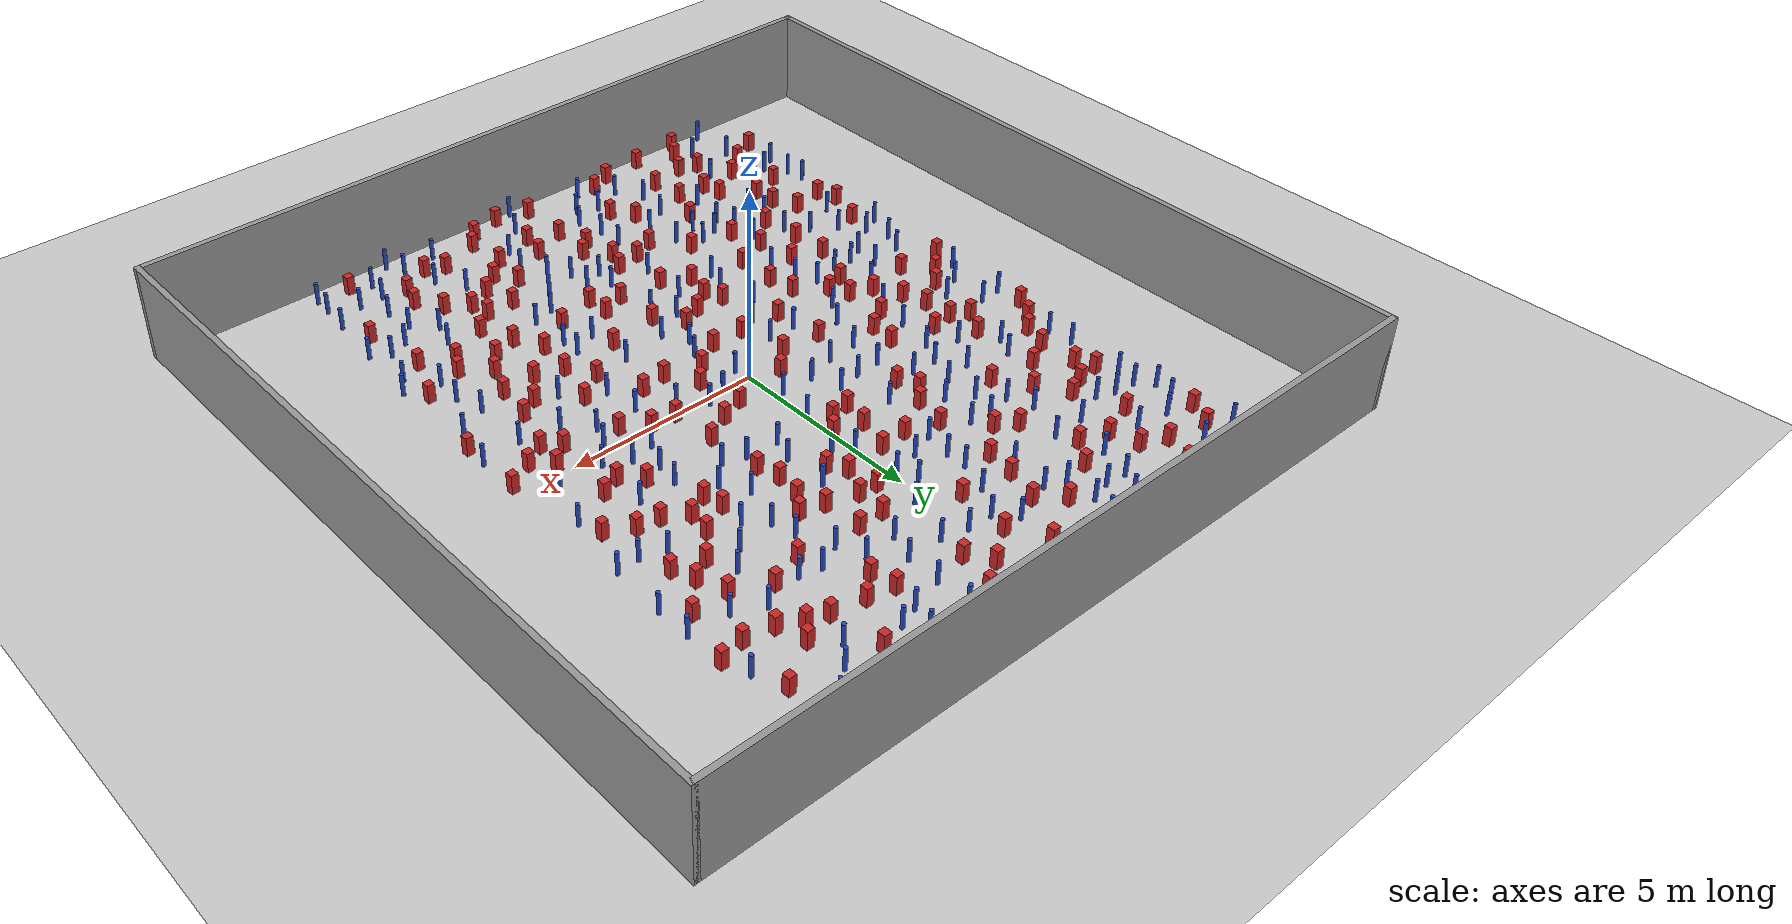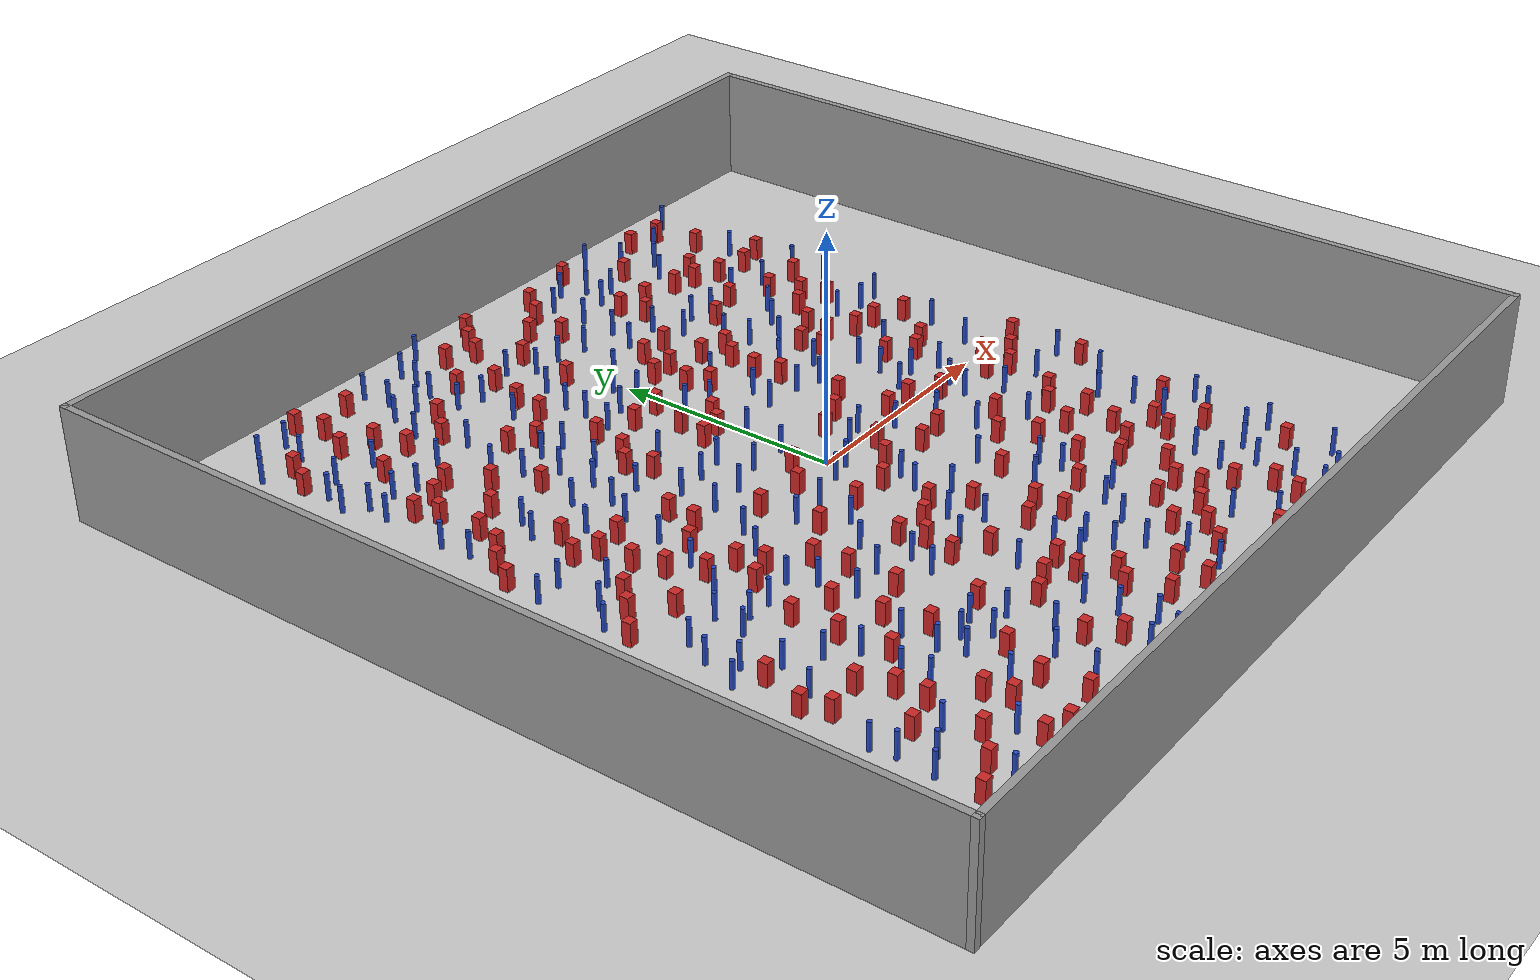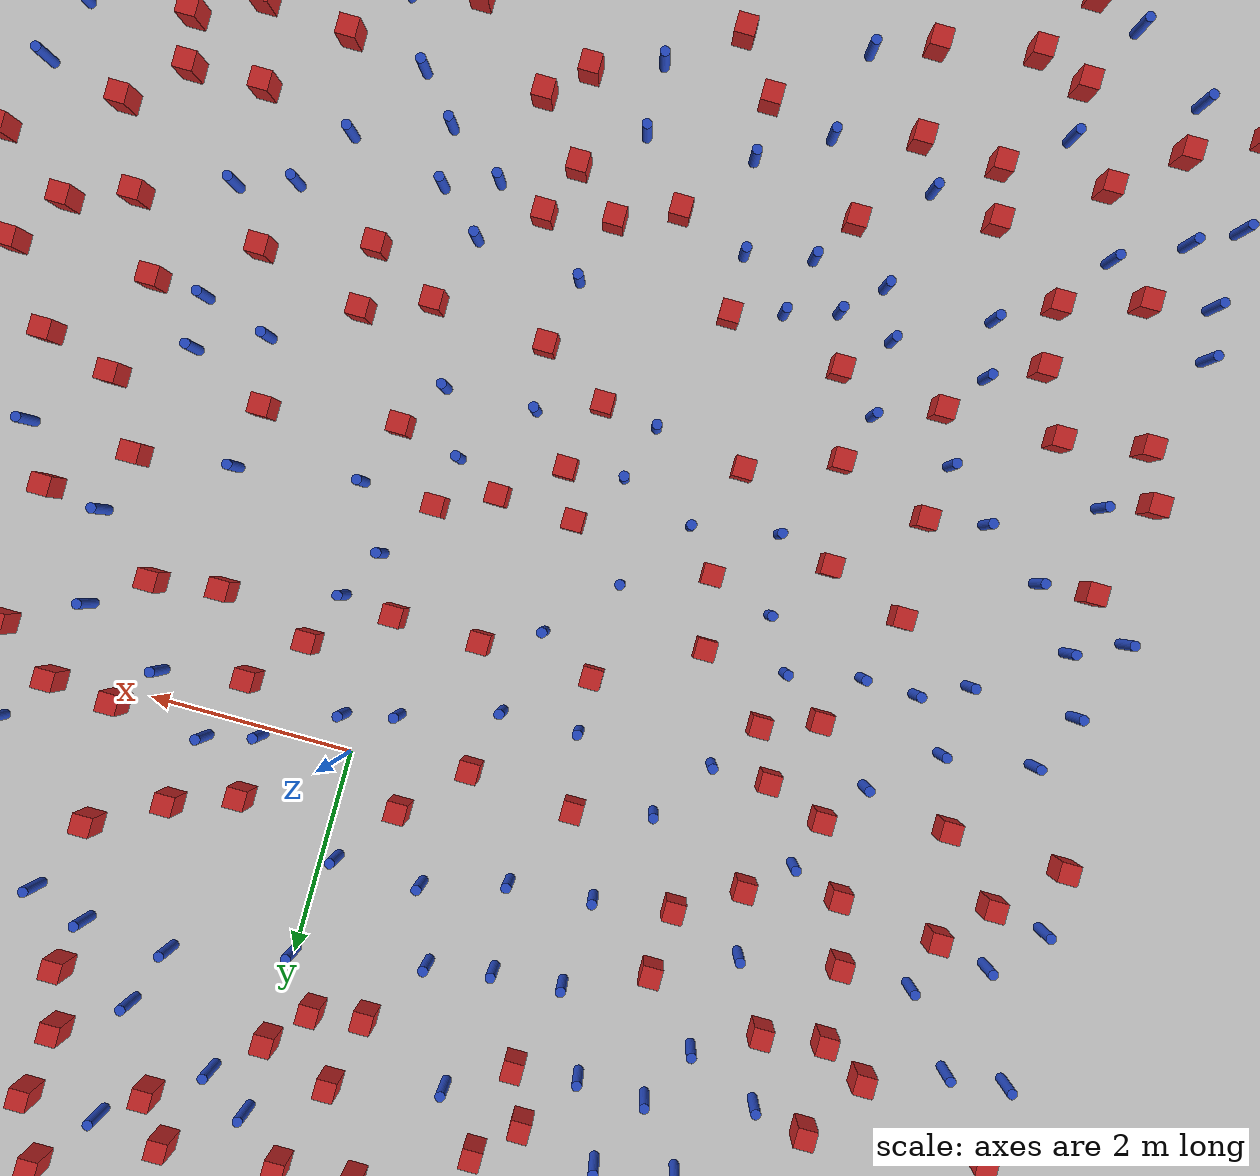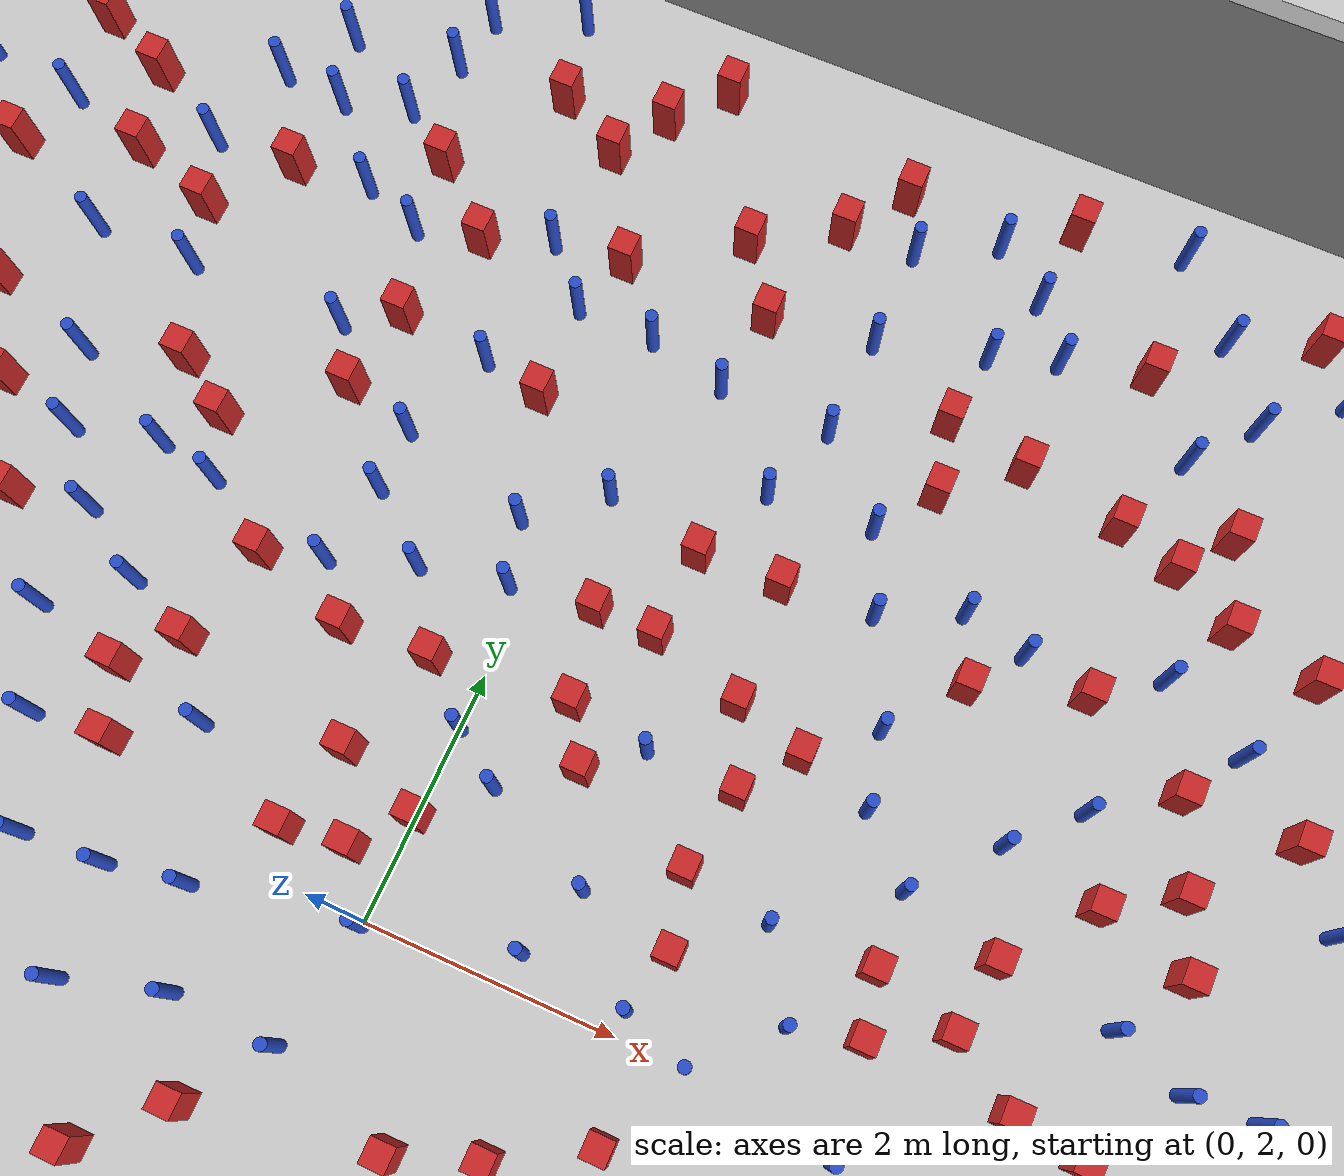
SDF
<sdf version="1.6">
 <world name="default">
  <light name="sun" type="directional">
   <pose>0 0 1000 0 -0 0</pose>
   <diffuse>0.8 0.8 0.8 1</diffuse>
   <specular>0.1 0.1 0.1 1</specular>
   <attenuation>
    <range>1000</range>
    <constant>0.9</constant>
    <linear>0.01</linear>
    <quadratic>0.001</quadratic>
   </attenuation>
   <direction>-0.5 0.5 -1</direction>
  </light>
  <model name="ground_plane">
   <static>1</static>
   <link name="link">
    <collision name="collision">
     <geometry><plane><normal>0 0 1</normal><size>100 100</size></plane></geometry>
     <surface><friction><ode><mu>100</mu><mu2>50</mu2></ode></friction></surface>
    </collision>
    <visual name="visual">
     <cast_shadows>0</cast_shadows>
     <geometry><plane><normal>0 0 1</normal><size>100 100</size></plane></geometry>
     <material>
      <ambient>1.0 1.0 1.0 1.0</ambient>
      <diffuse>0.8 0.8 0.8 1.0</diffuse>
      <specular>0.01 0.01 0.01 1.000000</specular>
     </material>
    </visual>
   </link>
  </model>
  <gravity>0 0 -9.8</gravity>
  <magnetic_field>6e-06 2.3e-05 -4.2e-05</magnetic_field>
  <atmosphere type="adiabatic"/>
  <physics name="default_physics" default="0" type="ode">
   <max_step_size>0.001</max_step_size>
   <real_time_factor>1</real_time_factor>
   <real_time_update_rate>1000</real_time_update_rate>
  </physics>
  <scene><ambient>0.4 0.4 0.4 1</ambient><background>0.7 0.7 0.7 1</background><shadows>1</shadows></scene>
  <spherical_coordinates>
   <surface_model>EARTH_WGS84</surface_model>
   <latitude_deg>0</latitude_deg>
   <longitude_deg>0</longitude_deg>
   <elevation>0</elevation>
   <heading_deg>0</heading_deg>
  </spherical_coordinates>
  <plugin name="gazebo_occupancy_map" filename="libgazebo_2Dmap_plugin.so">
   <map_resolution>0.05</map_resolution>
   <map_topic>generated_map</map_topic>
   <map_height>0.01</map_height>
   <map_size_x>50</map_size_x>
   <map_size_y>50</map_size_y>
  </plugin>
  <model name="NamedLocations">
   <static>true</static>
   <link name="DefaultStart"><pose>8.5 0 0 0 0 3.14</pose></link>
  </model>
  <model name="20x20_walls">
   <pose>0.044518 0.176112 0 0 -0 0</pose>
   <link name="Wall_1">
    <collision name="Wall_1_Collision">
     <geometry><box><size>20 0.15 2.5</size></box></geometry>
     <pose>0 0 1.25 0 -0 0</pose>
    </collision>
    <visual name="Wall_1_Visual">
     <pose>0 0 1.25 0 -0 0</pose>
     <geometry><box><size>20 0.15 2.5</size></box></geometry>
     <material>
      <script><uri>file://media/materials/scripts/gazebo.material</uri><name>Gazebo/Grey</name></script>
      <ambient>0.976471 0.992157 1 1</ambient>
     </material>
     <meta><layer>0</layer></meta>
    </visual>
    <pose>0 9.925 0 0 -0 0</pose>
   </link>
   <link name="Wall_3">
    <collision name="Wall_3_Collision">
     <geometry><box><size>20 0.15 2.5</size></box></geometry>
     <pose>0 0 1.25 0 -0 0</pose>
    </collision>
    <visual name="Wall_3_Visual">
     <pose>0 0 1.25 0 -0 0</pose>
     <geometry><box><size>20 0.15 2.5</size></box></geometry>
     <material>
      <script><uri>file://media/materials/scripts/gazebo.material</uri><name>Gazebo/Grey</name></script>
      <ambient>0.976471 0.992157 1 1</ambient>
     </material>
     <meta><layer>0</layer></meta>
    </visual>
    <pose>9.925 0 0 0 0 -1.5708</pose>
   </link>
   <link name="Wall_4">
    <collision name="Wall_4_Collision">
     <geometry><box><size>20 0.15 2.5</size></box></geometry>
     <pose>0 0 1.25 0 -0 0</pose>
    </collision>
    <visual name="Wall_4_Visual">
     <pose>0 0 1.25 0 -0 0</pose>
     <geometry><box><size>20 0.15 2.5</size></box></geometry>
     <material>
      <script><uri>file://media/materials/scripts/gazebo.material</uri><name>Gazebo/Grey</name></script>
      <ambient>0.976471 0.992157 1 1</ambient>
     </material>
     <meta><layer>0</layer></meta>
    </visual>
    <pose>0 -9.925 0 0 -0 3.14159</pose>
   </link>
   <link name="Wall_5">
    <collision name="Wall_5_Collision">
     <geometry><box><size>20 0.15 2.5</size></box></geometry>
     <pose>0 0 1.25 0 -0 0</pose>
    </collision>
    <visual name="Wall_5_Visual">
     <pose>0 0 1.25 0 -0 0</pose>
     <geometry><box><size>20 0.15 2.5</size></box></geometry>
     <material>
      <script><uri>file://media/materials/scripts/gazebo.material</uri><name>Gazebo/Grey</name></script>
      <ambient>0.976471 0.992157 1 1</ambient>
     </material>
     <meta><layer>0</layer></meta>
    </visual>
    <pose>-9.925 0 0 0 -0 1.5708</pose>
   </link>
   <static>1</static>
  </model>
  <model name="pole_obstacle0">
   <static>true</static>
   <pose>5.79565178209 3.24629329432 7.38925637345e-09 -8.47170692798e-08 1.24976764937e-08 -1.74513093023e-07</pose>
   <link name="link">
    <pose>0 0 0.3 0 -0 0</pose>
    <inertial>
     <mass>1</mass>
     <inertia><ixx>0.145833</ixx><ixy>0</ixy><ixz>0</ixz><iyy>0.145833</iyy><iyz>0</iyz><izz>0.125</izz></inertia>
    </inertial>
    <collision name="collision">
     <geometry><cylinder><radius>0.05</radius><length>.6</length></cylinder></geometry>
    </collision>
    <visual name="visual">
     <geometry><cylinder><radius>0.05</radius><length>.6</length></cylinder></geometry>
     <material>
      <script><name>Gazebo/Blue</name><uri>file://media/materials/scripts/gazebo.material</uri></script>
     </material>
    </visual>
   </link>
  </model>
  <model name="pole_obstacle1">
   <static>true</static>
   <pose>-0.977106564519 -7.90810374782 7.38925637345e-09 -8.47170692799e-08 1.2497676509e-08 -1.74513093015e-07</pose>
   <link name="link">
    <pose>0 0 0.3 0 -0 0</pose>
    <inertial>
     <mass>1</mass>
     <inertia><ixx>0.145833</ixx><ixy>0</ixy><ixz>0</ixz><iyy>0.145833</iyy><iyz>0</iyz><izz>0.125</izz></inertia>
    </inertial>
    <collision name="collision">
     <geometry><cylinder><radius>0.05</radius><length>.6</length></cylinder></geometry>
    </collision>
    <visual name="visual">
     <geometry><cylinder><radius>0.05</radius><length>.6</length></cylinder></geometry>
     <material>
      <script><name>Gazebo/Blue</name><uri>file://media/materials/scripts/gazebo.material</uri></script>
     </material>
    </visual>
   </link>
  </model>
  <model name="square_post_obstacle0">
   <static>true</static>
   <pose>1.56605751356 -1.20422821467 1.91545236811e-07 -7.35059704564e-06 1.12565212e-07 2.39332434364e-05</pose>
   <link name="link">
    <pose>0 0 0.25 0 -0 0</pose>
    <inertial>
     <mass>100</mass>
     <inertia>
      <ixx>0.166667</ixx>
      <ixy>0</ixy>
      <ixz>0</ixz>
      <iyy>0.166667</iyy>
      <iyz>0</iyz>
      <izz>0.166667</izz>
     </inertia>
    </inertial>
    <collision name="collision"><geometry><box><size>.2 .2 .5</size></box></geometry></collision>
    <visual name="visual">
     <geometry><box><size>.2 .2 .5</size></box></geometry>
     <material>
      <script><name>Gazebo/Red</name><uri>file://media/materials/scripts/gazebo.material</uri></script>
     </material>
    </visual>
   </link>
  </model>
  <model name="square_post_obstacle1">
   <static>true</static>
   <pose>-6.20894556401 5.08491788929 1.91545236811e-07 -7.35059704564e-06 1.12565212e-07 2.39332434364e-05</pose>
   <link name="link">
    <pose>0 0 0.25 0 -0 0</pose>
    <inertial>
     <mass>100</mass>
     <inertia>
      <ixx>0.166667</ixx>
      <ixy>0</ixy>
      <ixz>0</ixz>
      <iyy>0.166667</iyy>
      <iyz>0</iyz>
      <izz>0.166667</izz>
     </inertia>
    </inertial>
    <collision name="collision"><geometry><box><size>.2 .2 .5</size></box></geometry></collision>
    <visual name="visual">
     <geometry><box><size>.2 .2 .5</size></box></geometry>
     <material>
      <script><name>Gazebo/Red</name><uri>file://media/materials/scripts/gazebo.material</uri></script>
     </material>
    </visual>
   </link>
  </model>
  <model name="pole_obstacle2">
   <static>true</static>
   <pose>5.5693059751 -4.40679341141 7.38925637345e-09 -8.47170692796e-08 1.24976764786e-08 -1.74513093032e-07</pose>
   <link name="link">
    <pose>0 0 0.3 0 -0 0</pose>
    <inertial>
     <mass>1</mass>
     <inertia><ixx>0.145833</ixx><ixy>0</ixy><ixz>0</ixz><iyy>0.145833</iyy><iyz>0</iyz><izz>0.125</izz></inertia>
    </inertial>
    <collision name="collision">
     <geometry><cylinder><radius>0.05</radius><length>.6</length></cylinder></geometry>
    </collision>
    <visual name="visual">
     <geometry><cylinder><radius>0.05</radius><length>.6</length></cylinder></geometry>
     <material>
      <script><name>Gazebo/Blue</name><uri>file://media/materials/scripts/gazebo.material</uri></script>
     </material>
    </visual>
   </link>
  </model>
  <model name="pole_obstacle3">
   <static>true</static>
   <pose>-6.47764836646 9.04078290669 7.38925637345e-09 -8.471706928e-08 1.24976765081e-08 -1.74513093015e-07</pose>
   <link name="link">
    <pose>0 0 0.3 0 -0 0</pose>
    <inertial>
     <mass>1</mass>
     <inertia><ixx>0.145833</ixx><ixy>0</ixy><ixz>0</ixz><iyy>0.145833</iyy><iyz>0</iyz><izz>0.125</izz></inertia>
    </inertial>
    <collision name="collision">
     <geometry><cylinder><radius>0.05</radius><length>.6</length></cylinder></geometry>
    </collision>
    <visual name="visual">
     <geometry><cylinder><radius>0.05</radius><length>.6</length></cylinder></geometry>
     <material>
      <script><name>Gazebo/Blue</name><uri>file://media/materials/scripts/gazebo.material</uri></script>
     </material>
    </visual>
   </link>
  </model>
  <model name="pole_obstacle4">
   <static>true</static>
   <pose>3.87765196162 -0.706936386413 7.38925637345e-09 -8.471706928e-08 1.24976765177e-08 -1.74513093012e-07</pose>
   <link name="link">
    <pose>0 0 0.3 0 -0 0</pose>
    <inertial>
     <mass>1</mass>
     <inertia><ixx>0.145833</ixx><ixy>0</ixy><ixz>0</ixz><iyy>0.145833</iyy><iyz>0</iyz><izz>0.125</izz></inertia>
    </inertial>
    <collision name="collision">
     <geometry><cylinder><radius>0.05</radius><length>.6</length></cylinder></geometry>
    </collision>
    <visual name="visual">
     <geometry><cylinder><radius>0.05</radius><length>.6</length></cylinder></geometry>
     <material>
      <script><name>Gazebo/Blue</name><uri>file://media/materials/scripts/gazebo.material</uri></script>
     </material>
    </visual>
   </link>
  </model>
  <model name="pole_obstacle5">
   <static>true</static>
   <pose>1.80005106796 -3.65741169704 7.38925637345e-09 -8.47170692799e-08 1.24976765053e-08 -1.74513093017e-07</pose>
   <link name="link">
    <pose>0 0 0.3 0 -0 0</pose>
    <inertial>
     <mass>1</mass>
     <inertia><ixx>0.145833</ixx><ixy>0</ixy><ixz>0</ixz><iyy>0.145833</iyy><iyz>0</iyz><izz>0.125</izz></inertia>
    </inertial>
    <collision name="collision">
     <geometry><cylinder><radius>0.05</radius><length>.6</length></cylinder></geometry>
    </collision>
    <visual name="visual">
     <geometry><cylinder><radius>0.05</radius><length>.6</length></cylinder></geometry>
     <material>
      <script><name>Gazebo/Blue</name><uri>file://media/materials/scripts/gazebo.material</uri></script>
     </material>
    </visual>
   </link>
  </model>
  <model name="pole_obstacle6">
   <static>true</static>
   <pose>4.70599011204 -8.35303087441 7.38925637345e-09 -8.471706928e-08 1.24976765081e-08 -1.74513093015e-07</pose>
   <link name="link">
    <pose>0 0 0.3 0 -0 0</pose>
    <inertial>
     <mass>1</mass>
     <inertia><ixx>0.145833</ixx><ixy>0</ixy><ixz>0</ixz><iyy>0.145833</iyy><iyz>0</iyz><izz>0.125</izz></inertia>
    </inertial>
    <collision name="collision">
     <geometry><cylinder><radius>0.05</radius><length>.6</length></cylinder></geometry>
    </collision>
    <visual name="visual">
     <geometry><cylinder><radius>0.05</radius><length>.6</length></cylinder></geometry>
     <material>
      <script><name>Gazebo/Blue</name><uri>file://media/materials/scripts/gazebo.material</uri></script>
     </material>
    </visual>
   </link>
  </model>
  <model name="square_post_obstacle2">
   <static>true</static>
   <pose>1.98064423771 3.28189115455 1.91545236811e-07 -7.35059704564e-06 1.12565212e-07 2.39332434364e-05</pose>
   <link name="link">
    <pose>0 0 0.25 0 -0 0</pose>
    <inertial>
     <mass>100</mass>
     <inertia>
      <ixx>0.166667</ixx>
      <ixy>0</ixy>
      <ixz>0</ixz>
      <iyy>0.166667</iyy>
      <iyz>0</iyz>
      <izz>0.166667</izz>
     </inertia>
    </inertial>
    <collision name="collision"><geometry><box><size>.2 .2 .5</size></box></geometry></collision>
    <visual name="visual">
     <geometry><box><size>.2 .2 .5</size></box></geometry>
     <material>
      <script><name>Gazebo/Red</name><uri>file://media/materials/scripts/gazebo.material</uri></script>
     </material>
    </visual>
   </link>
  </model>
  <model name="square_post_obstacle3">
   <static>true</static>
   <pose>-0.432793943756 7.54914708848 1.91545236811e-07 -7.35059704564e-06 1.12565212e-07 2.39332434364e-05</pose>
   <link name="link">
    <pose>0 0 0.25 0 -0 0</pose>
    <inertial>
     <mass>100</mass>
     <inertia>
      <ixx>0.166667</ixx>
      <ixy>0</ixy>
      <ixz>0</ixz>
      <iyy>0.166667</iyy>
      <iyz>0</iyz>
      <izz>0.166667</izz>
     </inertia>
    </inertial>
    <collision name="collision"><geometry><box><size>.2 .2 .5</size></box></geometry></collision>
    <visual name="visual">
     <geometry><box><size>.2 .2 .5</size></box></geometry>
     <material>
      <script><name>Gazebo/Red</name><uri>file://media/materials/scripts/gazebo.material</uri></script>
     </material>
    </visual>
   </link>
  </model>
  <model name="square_post_obstacle4">
   <static>true</static>
   <pose>-2.22750226786 -0.0658308857675 1.91545236811e-07 -7.35059704564e-06 1.12565212e-07 2.39332434364e-05</pose>
   <link name="link">
    <pose>0 0 0.25 0 -0 0</pose>
    <inertial>
     <mass>100</mass>
     <inertia>
      <ixx>0.166667</ixx>
      <ixy>0</ixy>
      <ixz>0</ixz>
      <iyy>0.166667</iyy>
      <iyz>0</iyz>
      <izz>0.166667</izz>
     </inertia>
    </inertial>
    <collision name="collision"><geometry><box><size>.2 .2 .5</size></box></geometry></collision>
    <visual name="visual">
     <geometry><box><size>.2 .2 .5</size></box></geometry>
     <material>
      <script><name>Gazebo/Red</name><uri>file://media/materials/scripts/gazebo.material</uri></script>
     </material>
    </visual>
   </link>
  </model>
  <model name="pole_obstacle7">
   <static>true</static>
   <pose>-5.94388062194 -3.34615520025 7.38925637345e-09 -8.47170692798e-08 1.24976764937e-08 -1.74513093023e-07</pose>
   <link name="link">
    <pose>0 0 0.3 0 -0 0</pose>
    <inertial>
     <mass>1</mass>
     <inertia><ixx>0.145833</ixx><ixy>0</ixy><ixz>0</ixz><iyy>0.145833</iyy><iyz>0</iyz><izz>0.125</izz></inertia>
    </inertial>
    <collision name="collision">
     <geometry><cylinder><radius>0.05</radius><length>.6</length></cylinder></geometry>
    </collision>
    <visual name="visual">
     <geometry><cylinder><radius>0.05</radius><length>.6</length></cylinder></geometry>
     <material>
      <script><name>Gazebo/Blue</name><uri>file://media/materials/scripts/gazebo.material</uri></script>
     </material>
    </visual>
   </link>
  </model>
  <model name="pole_obstacle8">
   <static>true</static>
   <pose>-5.89937046172 5.9574986893 7.38925637345e-09 -8.47170692796e-08 1.24976764786e-08 -1.74513093032e-07</pose>
   <link name="link">
    <pose>0 0 0.3 0 -0 0</pose>
    <inertial>
     <mass>1</mass>
     <inertia><ixx>0.145833</ixx><ixy>0</ixy><ixz>0</ixz><iyy>0.145833</iyy><iyz>0</iyz><izz>0.125</izz></inertia>
    </inertial>
    <collision name="collision">
     <geometry><cylinder><radius>0.05</radius><length>.6</length></cylinder></geometry>
    </collision>
    <visual name="visual">
     <geometry><cylinder><radius>0.05</radius><length>.6</length></cylinder></geometry>
     <material>
      <script><name>Gazebo/Blue</name><uri>file://media/materials/scripts/gazebo.material</uri></script>
     </material>
    </visual>
   </link>
  </model>
  <model name="square_post_obstacle5">
   <static>true</static>
   <pose>5.84599909969 -6.99812463571 1.91545236811e-07 -7.35059704564e-06 1.12565212e-07 2.39332434364e-05</pose>
   <link name="link">
    <pose>0 0 0.25 0 -0 0</pose>
    <inertial>
     <mass>100</mass>
     <inertia>
      <ixx>0.166667</ixx>
      <ixy>0</ixy>
      <ixz>0</ixz>
      <iyy>0.166667</iyy>
      <iyz>0</iyz>
      <izz>0.166667</izz>
     </inertia>
    </inertial>
    <collision name="collision"><geometry><box><size>.2 .2 .5</size></box></geometry></collision>
    <visual name="visual">
     <geometry><box><size>.2 .2 .5</size></box></geometry>
     <material>
      <script><name>Gazebo/Red</name><uri>file://media/materials/scripts/gazebo.material</uri></script>
     </material>
    </visual>
   </link>
  </model>
  <model name="square_post_obstacle6">
   <static>true</static>
   <pose>-4.73540818238 -3.65907289616 1.91545236811e-07 -7.35059704564e-06 1.12565212e-07 2.39332434364e-05</pose>
   <link name="link">
    <pose>0 0 0.25 0 -0 0</pose>
    <inertial>
     <mass>100</mass>
     <inertia>
      <ixx>0.166667</ixx>
      <ixy>0</ixy>
      <ixz>0</ixz>
      <iyy>0.166667</iyy>
      <iyz>0</iyz>
      <izz>0.166667</izz>
     </inertia>
    </inertial>
    <collision name="collision"><geometry><box><size>.2 .2 .5</size></box></geometry></collision>
    <visual name="visual">
     <geometry><box><size>.2 .2 .5</size></box></geometry>
     <material>
      <script><name>Gazebo/Red</name><uri>file://media/materials/scripts/gazebo.material</uri></script>
     </material>
    </visual>
   </link>
  </model>
  <model name="square_post_obstacle7">
   <static>true</static>
   <pose>3.74116895942 -5.48608894107 1.91545236811e-07 -7.35059704564e-06 1.12565212e-07 2.39332434364e-05</pose>
   <link name="link">
    <pose>0 0 0.25 0 -0 0</pose>
    <inertial>
     <mass>100</mass>
     <inertia>
      <ixx>0.166667</ixx>
      <ixy>0</ixy>
      <ixz>0</ixz>
      <iyy>0.166667</iyy>
      <iyz>0</iyz>
      <izz>0.166667</izz>
     </inertia>
    </inertial>
    <collision name="collision"><geometry><box><size>.2 .2 .5</size></box></geometry></collision>
    <visual name="visual">
     <geometry><box><size>.2 .2 .5</size></box></geometry>
     <material>
      <script><name>Gazebo/Red</name><uri>file://media/materials/scripts/gazebo.material</uri></script>
     </material>
    </visual>
   </link>
  </model>
  <model name="pole_obstacle9">
   <static>true</static>
   <pose>2.92601557178 -7.32535560312 7.38925637345e-09 -8.47170692798e-08 1.24976765033e-08 -1.74513093019e-07</pose>
   <link name="link">
    <pose>0 0 0.3 0 -0 0</pose>
    <inertial>
     <mass>1</mass>
     <inertia><ixx>0.145833</ixx><ixy>0</ixy><ixz>0</ixz><iyy>0.145833</iyy><iyz>0</iyz><izz>0.125</izz></inertia>
    </inertial>
    <collision name="collision">
     <geometry><cylinder><radius>0.05</radius><length>.6</length></cylinder></geometry>
    </collision>
    <visual name="visual">
     <geometry><cylinder><radius>0.05</radius><length>.6</length></cylinder></geometry>
     <material>
      <script><name>Gazebo/Blue</name><uri>file://media/materials/scripts/gazebo.material</uri></script>
     </material>
    </visual>
   </link>
  </model>
  <model name="pole_obstacle10">
   <static>true</static>
   <pose>6.43006931525 5.59276663731 7.38925637345e-09 -8.47170692796e-08 1.24976764786e-08 -1.74513093032e-07</pose>
   <link name="link">
    <pose>0 0 0.3 0 -0 0</pose>
    <inertial>
     <mass>1</mass>
     <inertia><ixx>0.145833</ixx><ixy>0</ixy><ixz>0</ixz><iyy>0.145833</iyy><iyz>0</iyz><izz>0.125</izz></inertia>
    </inertial>
    <collision name="collision">
     <geometry><cylinder><radius>0.05</radius><length>.6</length></cylinder></geometry>
    </collision>
    <visual name="visual">
     <geometry><cylinder><radius>0.05</radius><length>.6</length></cylinder></geometry>
     <material>
      <script><name>Gazebo/Blue</name><uri>file://media/materials/scripts/gazebo.material</uri></script>
     </material>
    </visual>
   </link>
  </model>
  <model name="pole_obstacle11">
   <static>true</static>
   <pose>-4.01556916504 7.21280507882 7.38925637345e-09 -8.47170692795e-08 1.24976764731e-08 -1.74513093035e-07</pose>
   <link name="link">
    <pose>0 0 0.3 0 -0 0</pose>
    <inertial>
     <mass>1</mass>
     <inertia><ixx>0.145833</ixx><ixy>0</ixy><ixz>0</ixz><iyy>0.145833</iyy><iyz>0</iyz><izz>0.125</izz></inertia>
    </inertial>
    <collision name="collision">
     <geometry><cylinder><radius>0.05</radius><length>.6</length></cylinder></geometry>
    </collision>
    <visual name="visual">
     <geometry><cylinder><radius>0.05</radius><length>.6</length></cylinder></geometry>
     <material>
      <script><name>Gazebo/Blue</name><uri>file://media/materials/scripts/gazebo.material</uri></script>
     </material>
    </visual>
   </link>
  </model>
  <model name="pole_obstacle12">
   <static>true</static>
   <pose>6.43960804948 4.71248183484 7.38925637345e-09 -8.47170692796e-08 1.24976764786e-08 -1.74513093032e-07</pose>
   <link name="link">
    <pose>0 0 0.3 0 -0 0</pose>
    <inertial>
     <mass>1</mass>
     <inertia><ixx>0.145833</ixx><ixy>0</ixy><ixz>0</ixz><iyy>0.145833</iyy><iyz>0</iyz><izz>0.125</izz></inertia>
    </inertial>
    <collision name="collision">
     <geometry><cylinder><radius>0.05</radius><length>.6</length></cylinder></geometry>
    </collision>
    <visual name="visual">
     <geometry><cylinder><radius>0.05</radius><length>.6</length></cylinder></geometry>
     <material>
      <script><name>Gazebo/Blue</name><uri>file://media/materials/scripts/gazebo.material</uri></script>
     </material>
    </visual>
   </link>
  </model>
  <model name="square_post_obstacle8">
   <static>true</static>
   <pose>-2.33978747263 2.45094389933 1.91545236811e-07 -7.35059704564e-06 1.12565212e-07 2.39332434364e-05</pose>
   <link name="link">
    <pose>0 0 0.25 0 -0 0</pose>
    <inertial>
     <mass>100</mass>
     <inertia>
      <ixx>0.166667</ixx>
      <ixy>0</ixy>
      <ixz>0</ixz>
      <iyy>0.166667</iyy>
      <iyz>0</iyz>
      <izz>0.166667</izz>
     </inertia>
    </inertial>
    <collision name="collision"><geometry><box><size>.2 .2 .5</size></box></geometry></collision>
    <visual name="visual">
     <geometry><box><size>.2 .2 .5</size></box></geometry>
     <material>
      <script><name>Gazebo/Red</name><uri>file://media/materials/scripts/gazebo.material</uri></script>
     </material>
    </visual>
   </link>
  </model>
  <model name="square_post_obstacle9">
   <static>true</static>
   <pose>1.453826613 -9.14333168105 1.91545236811e-07 -7.35059704564e-06 1.12565212e-07 2.39332434364e-05</pose>
   <link name="link">
    <pose>0 0 0.25 0 -0 0</pose>
    <inertial>
     <mass>100</mass>
     <inertia>
      <ixx>0.166667</ixx>
      <ixy>0</ixy>
      <ixz>0</ixz>
      <iyy>0.166667</iyy>
      <iyz>0</iyz>
      <izz>0.166667</izz>
     </inertia>
    </inertial>
    <collision name="collision"><geometry><box><size>.2 .2 .5</size></box></geometry></collision>
    <visual name="visual">
     <geometry><box><size>.2 .2 .5</size></box></geometry>
     <material>
      <script><name>Gazebo/Red</name><uri>file://media/materials/scripts/gazebo.material</uri></script>
     </material>
    </visual>
   </link>
  </model>
  <model name="pole_obstacle13">
   <static>true</static>
   <pose>0.557342866463 -2.55776858749 7.38925637345e-09 -8.47170692799e-08 1.2497676509e-08 -1.74513093016e-07</pose>
   <link name="link">
    <pose>0 0 0.3 0 -0 0</pose>
    <inertial>
     <mass>1</mass>
     <inertia><ixx>0.145833</ixx><ixy>0</ixy><ixz>0</ixz><iyy>0.145833</iyy><iyz>0</iyz><izz>0.125</izz></inertia>
    </inertial>
    <collision name="collision">
     <geometry><cylinder><radius>0.05</radius><length>.6</length></cylinder></geometry>
    </collision>
    <visual name="visual">
     <geometry><cylinder><radius>0.05</radius><length>.6</length></cylinder></geometry>
     <material>
      <script><name>Gazebo/Blue</name><uri>file://media/materials/scripts/gazebo.material</uri></script>
     </material>
    </visual>
   </link>
  </model>
  <model name="square_post_obstacle10">
   <static>true</static>
   <pose>-6.81502577648 -4.3608636634 1.91545236811e-07 -7.35059704564e-06 1.12565212e-07 2.39332434364e-05</pose>
   <link name="link">
    <pose>0 0 0.25 0 -0 0</pose>
    <inertial>
     <mass>100</mass>
     <inertia>
      <ixx>0.166667</ixx>
      <ixy>0</ixy>
      <ixz>0</ixz>
      <iyy>0.166667</iyy>
      <iyz>0</iyz>
      <izz>0.166667</izz>
     </inertia>
    </inertial>
    <collision name="collision"><geometry><box><size>.2 .2 .5</size></box></geometry></collision>
    <visual name="visual">
     <geometry><box><size>.2 .2 .5</size></box></geometry>
     <material>
      <script><name>Gazebo/Red</name><uri>file://media/materials/scripts/gazebo.material</uri></script>
     </material>
    </visual>
   </link>
  </model>
  <model name="square_post_obstacle11">
   <static>true</static>
   <pose>-2.06487871892 -1.3372170114 1.91545236811e-07 -7.35059704564e-06 1.12565212e-07 2.39332434364e-05</pose>
   <link name="link">
    <pose>0 0 0.25 0 -0 0</pose>
    <inertial>
     <mass>100</mass>
     <inertia>
      <ixx>0.166667</ixx>
      <ixy>0</ixy>
      <ixz>0</ixz>
      <iyy>0.166667</iyy>
      <iyz>0</iyz>
      <izz>0.166667</izz>
     </inertia>
    </inertial>
    <collision name="collision"><geometry><box><size>.2 .2 .5</size></box></geometry></collision>
    <visual name="visual">
     <geometry><box><size>.2 .2 .5</size></box></geometry>
     <material>
      <script><name>Gazebo/Red</name><uri>file://media/materials/scripts/gazebo.material</uri></script>
     </material>
    </visual>
   </link>
  </model>
  <model name="pole_obstacle14">
   <static>true</static>
   <pose>2.77887559729 -0.727295282629 7.38925637345e-09 -8.471706928e-08 1.24976765177e-08 -1.74513093012e-07</pose>
   <link name="link">
    <pose>0 0 0.3 0 -0 0</pose>
    <inertial>
     <mass>1</mass>
     <inertia><ixx>0.145833</ixx><ixy>0</ixy><ixz>0</ixz><iyy>0.145833</iyy><iyz>0</iyz><izz>0.125</izz></inertia>
    </inertial>
    <collision name="collision">
     <geometry><cylinder><radius>0.05</radius><length>.6</length></cylinder></geometry>
    </collision>
    <visual name="visual">
     <geometry><cylinder><radius>0.05</radius><length>.6</length></cylinder></geometry>
     <material>
      <script><name>Gazebo/Blue</name><uri>file://media/materials/scripts/gazebo.material</uri></script>
     </material>
    </visual>
   </link>
  </model>
  <model name="pole_obstacle15">
   <static>true</static>
   <pose>-0.00549938469334 1.96665930927 7.38925637345e-09 -8.471706928e-08 1.24976765085e-08 -1.74513093015e-07</pose>
   <link name="link">
    <pose>0 0 0.3 0 -0 0</pose>
    <inertial>
     <mass>1</mass>
     <inertia><ixx>0.145833</ixx><ixy>0</ixy><ixz>0</ixz><iyy>0.145833</iyy><iyz>0</iyz><izz>0.125</izz></inertia>
    </inertial>
    <collision name="collision">
     <geometry><cylinder><radius>0.05</radius><length>.6</length></cylinder></geometry>
    </collision>
    <visual name="visual">
     <geometry><cylinder><radius>0.05</radius><length>.6</length></cylinder></geometry>
     <material>
      <script><name>Gazebo/Blue</name><uri>file://media/materials/scripts/gazebo.material</uri></script>
     </material>
    </visual>
   </link>
  </model>
  <model name="square_post_obstacle12">
   <static>true</static>
   <pose>0.342677569145 -3.17985006614 1.91545236811e-07 -7.35059704564e-06 1.12565212e-07 2.39332434364e-05</pose>
   <link name="link">
    <pose>0 0 0.25 0 -0 0</pose>
    <inertial>
     <mass>100</mass>
     <inertia>
      <ixx>0.166667</ixx>
      <ixy>0</ixy>
      <ixz>0</ixz>
      <iyy>0.166667</iyy>
      <iyz>0</iyz>
      <izz>0.166667</izz>
     </inertia>
    </inertial>
    <collision name="collision"><geometry><box><size>.2 .2 .5</size></box></geometry></collision>
    <visual name="visual">
     <geometry><box><size>.2 .2 .5</size></box></geometry>
     <material>
      <script><name>Gazebo/Red</name><uri>file://media/materials/scripts/gazebo.material</uri></script>
     </material>
    </visual>
   </link>
  </model>
  <model name="pole_obstacle16">
   <static>true</static>
   <pose>2.56210407748 7.94373659365 7.38925637345e-09 -8.47170692798e-08 1.24976765033e-08 -1.74513093019e-07</pose>
   <link name="link">
    <pose>0 0 0.3 0 -0 0</pose>
    <inertial>
     <mass>1</mass>
     <inertia><ixx>0.145833</ixx><ixy>0</ixy><ixz>0</ixz><iyy>0.145833</iyy><iyz>0</iyz><izz>0.125</izz></inertia>
    </inertial>
    <collision name="collision">
     <geometry><cylinder><radius>0.05</radius><length>.6</length></cylinder></geometry>
    </collision>
    <visual name="visual">
     <geometry><cylinder><radius>0.05</radius><length>.6</length></cylinder></geometry>
     <material>
      <script><name>Gazebo/Blue</name><uri>file://media/materials/scripts/gazebo.material</uri></script>
     </material>
    </visual>
   </link>
  </model>
  <model name="pole_obstacle17">
   <static>true</static>
   <pose>3.67841027492 5.769085031 7.38925637345e-09 -8.47170692798e-08 1.24976765033e-08 -1.74513093019e-07</pose>
   <link name="link">
    <pose>0 0 0.3 0 -0 0</pose>
    <inertial>
     <mass>1</mass>
     <inertia><ixx>0.145833</ixx><ixy>0</ixy><ixz>0</ixz><iyy>0.145833</iyy><iyz>0</iyz><izz>0.125</izz></inertia>
    </inertial>
    <collision name="collision">
     <geometry><cylinder><radius>0.05</radius><length>.6</length></cylinder></geometry>
    </collision>
    <visual name="visual">
     <geometry><cylinder><radius>0.05</radius><length>.6</length></cylinder></geometry>
     <material>
      <script><name>Gazebo/Blue</name><uri>file://media/materials/scripts/gazebo.material</uri></script>
     </material>
    </visual>
   </link>
  </model>
  <model name="square_post_obstacle13">
   <static>true</static>
   <pose>2.60032660815 6.71405022309 1.91545236811e-07 -7.35059704564e-06 1.12565212e-07 2.39332434364e-05</pose>
   <link name="link">
    <pose>0 0 0.25 0 -0 0</pose>
    <inertial>
     <mass>100</mass>
     <inertia>
      <ixx>0.166667</ixx>
      <ixy>0</ixy>
      <ixz>0</ixz>
      <iyy>0.166667</iyy>
      <iyz>0</iyz>
      <izz>0.166667</izz>
     </inertia>
    </inertial>
    <collision name="collision"><geometry><box><size>.2 .2 .5</size></box></geometry></collision>
    <visual name="visual">
     <geometry><box><size>.2 .2 .5</size></box></geometry>
     <material>
      <script><name>Gazebo/Red</name><uri>file://media/materials/scripts/gazebo.material</uri></script>
     </material>
    </visual>
   </link>
  </model>
  <model name="pole_obstacle18">
   <static>true</static>
   <pose>-0.269620902724 5.22114954407 7.38925637345e-09 -8.47170692799e-08 1.24976765096e-08 -1.74513093014e-07</pose>
   <link name="link">
    <pose>0 0 0.3 0 -0 0</pose>
    <inertial>
     <mass>1</mass>
     <inertia><ixx>0.145833</ixx><ixy>0</ixy><ixz>0</ixz><iyy>0.145833</iyy><iyz>0</iyz><izz>0.125</izz></inertia>
    </inertial>
    <collision name="collision">
     <geometry><cylinder><radius>0.05</radius><length>.6</length></cylinder></geometry>
    </collision>
    <visual name="visual">
     <geometry><cylinder><radius>0.05</radius><length>.6</length></cylinder></geometry>
     <material>
      <script><name>Gazebo/Blue</name><uri>file://media/materials/scripts/gazebo.material</uri></script>
     </material>
    </visual>
   </link>
  </model>
  <model name="square_post_obstacle14">
   <static>true</static>
   <pose>-0.260426917664 9.33828999109 1.91545236811e-07 -7.35059704564e-06 1.12565212e-07 2.39332434364e-05</pose>
   <link name="link">
    <pose>0 0 0.25 0 -0 0</pose>
    <inertial>
     <mass>100</mass>
     <inertia>
      <ixx>0.166667</ixx>
      <ixy>0</ixy>
      <ixz>0</ixz>
      <iyy>0.166667</iyy>
      <iyz>0</iyz>
      <izz>0.166667</izz>
     </inertia>
    </inertial>
    <collision name="collision"><geometry><box><size>.2 .2 .5</size></box></geometry></collision>
    <visual name="visual">
     <geometry><box><size>.2 .2 .5</size></box></geometry>
     <material>
      <script><name>Gazebo/Red</name><uri>file://media/materials/scripts/gazebo.material</uri></script>
     </material>
    </visual>
   </link>
  </model>
  <model name="pole_obstacle19">
   <static>true</static>
   <pose>-2.98141069611 -0.236234702678 7.38925637345e-09 -8.47170692793e-08 1.24976764426e-08 -1.74513093041e-07</pose>
   <link name="link">
    <pose>0 0 0.3 0 -0 0</pose>
    <inertial>
     <mass>1</mass>
     <inertia><ixx>0.145833</ixx><ixy>0</ixy><ixz>0</ixz><iyy>0.145833</iyy><iyz>0</iyz><izz>0.125</izz></inertia>
    </inertial>
    <collision name="collision">
     <geometry><cylinder><radius>0.05</radius><length>.6</length></cylinder></geometry>
    </collision>
    <visual name="visual">
     <geometry><cylinder><radius>0.05</radius><length>.6</length></cylinder></geometry>
     <material>
      <script><name>Gazebo/Blue</name><uri>file://media/materials/scripts/gazebo.material</uri></script>
     </material>
    </visual>
   </link>
  </model>
  <model name="square_post_obstacle15">
   <static>true</static>
   <pose>-3.41333469753 0.588921729999 1.91545236811e-07 -7.35059704564e-06 1.12565212e-07 2.39332434364e-05</pose>
   <link name="link">
    <pose>0 0 0.25 0 -0 0</pose>
    <inertial>
     <mass>100</mass>
     <inertia>
      <ixx>0.166667</ixx>
      <ixy>0</ixy>
      <ixz>0</ixz>
      <iyy>0.166667</iyy>
      <iyz>0</iyz>
      <izz>0.166667</izz>
     </inertia>
    </inertial>
    <collision name="collision"><geometry><box><size>.2 .2 .5</size></box></geometry></collision>
    <visual name="visual">
     <geometry><box><size>.2 .2 .5</size></box></geometry>
     <material>
      <script><name>Gazebo/Red</name><uri>file://media/materials/scripts/gazebo.material</uri></script>
     </material>
    </visual>
   </link>
  </model>
  <model name="square_post_obstacle16">
   <static>true</static>
   <pose>1.10032722098 5.52364395335 1.91545236811e-07 -7.35059704564e-06 1.12565212e-07 2.39332434364e-05</pose>
   <link name="link">
    <pose>0 0 0.25 0 -0 0</pose>
    <inertial>
     <mass>100</mass>
     <inertia>
      <ixx>0.166667</ixx>
      <ixy>0</ixy>
      <ixz>0</ixz>
      <iyy>0.166667</iyy>
      <iyz>0</iyz>
      <izz>0.166667</izz>
     </inertia>
    </inertial>
    <collision name="collision"><geometry><box><size>.2 .2 .5</size></box></geometry></collision>
    <visual name="visual">
     <geometry><box><size>.2 .2 .5</size></box></geometry>
     <material>
      <script><name>Gazebo/Red</name><uri>file://media/materials/scripts/gazebo.material</uri></script>
     </material>
    </visual>
   </link>
  </model>
  <model name="square_post_obstacle17">
   <static>true</static>
   <pose>5.35984486681 4.55833261002 1.91545236811e-07 -7.35059704564e-06 1.12565212e-07 2.39332434364e-05</pose>
   <link name="link">
    <pose>0 0 0.25 0 -0 0</pose>
    <inertial>
     <mass>100</mass>
     <inertia>
      <ixx>0.166667</ixx>
      <ixy>0</ixy>
      <ixz>0</ixz>
      <iyy>0.166667</iyy>
      <iyz>0</iyz>
      <izz>0.166667</izz>
     </inertia>
    </inertial>
    <collision name="collision"><geometry><box><size>.2 .2 .5</size></box></geometry></collision>
    <visual name="visual">
     <geometry><box><size>.2 .2 .5</size></box></geometry>
     <material>
      <script><name>Gazebo/Red</name><uri>file://media/materials/scripts/gazebo.material</uri></script>
     </material>
    </visual>
   </link>
  </model>
  <model name="pole_obstacle20">
   <static>true</static>
   <pose>-1.66863566471 9.47693834386 7.38925637345e-09 -8.47170692798e-08 1.24976764881e-08 -1.74513093027e-07</pose>
   <link name="link">
    <pose>0 0 0.3 0 -0 0</pose>
    <inertial>
     <mass>1</mass>
     <inertia><ixx>0.145833</ixx><ixy>0</ixy><ixz>0</ixz><iyy>0.145833</iyy><iyz>0</iyz><izz>0.125</izz></inertia>
    </inertial>
    <collision name="collision">
     <geometry><cylinder><radius>0.05</radius><length>.6</length></cylinder></geometry>
    </collision>
    <visual name="visual">
     <geometry><cylinder><radius>0.05</radius><length>.6</length></cylinder></geometry>
     <material>
      <script><name>Gazebo/Blue</name><uri>file://media/materials/scripts/gazebo.material</uri></script>
     </material>
    </visual>
   </link>
  </model>
  <model name="pole_obstacle21">
   <static>true</static>
   <pose>0.0212298474387 3.55706874163 7.38925637345e-09 -8.471706928e-08 1.24976765089e-08 -1.74513093014e-07</pose>
   <link name="link">
    <pose>0 0 0.3 0 -0 0</pose>
    <inertial>
     <mass>1</mass>
     <inertia><ixx>0.145833</ixx><ixy>0</ixy><ixz>0</ixz><iyy>0.145833</iyy><iyz>0</iyz><izz>0.125</izz></inertia>
    </inertial>
    <collision name="collision">
     <geometry><cylinder><radius>0.05</radius><length>.6</length></cylinder></geometry>
    </collision>
    <visual name="visual">
     <geometry><cylinder><radius>0.05</radius><length>.6</length></cylinder></geometry>
     <material>
      <script><name>Gazebo/Blue</name><uri>file://media/materials/scripts/gazebo.material</uri></script>
     </material>
    </visual>
   </link>
  </model>
  <model name="pole_obstacle22">
   <static>true</static>
   <pose>5.41686952572 -2.97024607417 7.38925637345e-09 -8.47170692798e-08 1.24976764937e-08 -1.74513093023e-07</pose>
   <link name="link">
    <pose>0 0 0.3 0 -0 0</pose>
    <inertial>
     <mass>1</mass>
     <inertia><ixx>0.145833</ixx><ixy>0</ixy><ixz>0</ixz><iyy>0.145833</iyy><iyz>0</iyz><izz>0.125</izz></inertia>
    </inertial>
    <collision name="collision">
     <geometry><cylinder><radius>0.05</radius><length>.6</length></cylinder></geometry>
    </collision>
    <visual name="visual">
     <geometry><cylinder><radius>0.05</radius><length>.6</length></cylinder></geometry>
     <material>
      <script><name>Gazebo/Blue</name><uri>file://media/materials/scripts/gazebo.material</uri></script>
     </material>
    </visual>
   </link>
  </model>
  <model name="pole_obstacle23">
   <static>true</static>
   <pose>-1.17780498482 -6.50733422358 7.38925637345e-09 -8.47170692799e-08 1.24976765033e-08 -1.74513093018e-07</pose>
   <link name="link">
    <pose>0 0 0.3 0 -0 0</pose>
    <inertial>
     <mass>1</mass>
     <inertia><ixx>0.145833</ixx><ixy>0</ixy><ixz>0</ixz><iyy>0.145833</iyy><iyz>0</iyz><izz>0.125</izz></inertia>
    </inertial>
    <collision name="collision">
     <geometry><cylinder><radius>0.05</radius><length>.6</length></cylinder></geometry>
    </collision>
    <visual name="visual">
     <geometry><cylinder><radius>0.05</radius><length>.6</length></cylinder></geometry>
     <material>
      <script><name>Gazebo/Blue</name><uri>file://media/materials/scripts/gazebo.material</uri></script>
     </material>
    </visual>
   </link>
  </model>
  <model name="square_post_obstacle18">
   <static>true</static>
   <pose>-0.133258296363 -6.60814210632 1.91545236811e-07 -7.35059704564e-06 1.12565212e-07 2.39332434364e-05</pose>
   <link name="link">
    <pose>0 0 0.25 0 -0 0</pose>
    <inertial>
     <mass>100</mass>
     <inertia>
      <ixx>0.166667</ixx>
      <ixy>0</ixy>
      <ixz>0</ixz>
      <iyy>0.166667</iyy>
      <iyz>0</iyz>
      <izz>0.166667</izz>
     </inertia>
    </inertial>
    <collision name="collision"><geometry><box><size>.2 .2 .5</size></box></geometry></collision>
    <visual name="visual">
     <geometry><box><size>.2 .2 .5</size></box></geometry>
     <material>
      <script><name>Gazebo/Red</name><uri>file://media/materials/scripts/gazebo.material</uri></script>
     </material>
    </visual>
   </link>
  </model>
  <model name="pole_obstacle24">
   <static>true</static>
   <pose>0.29077984263 5.68026242619 7.38925637345e-09 -8.47170692799e-08 1.24976765101e-08 -1.74513093014e-07</pose>
   <link name="link">
    <pose>0 0 0.3 0 -0 0</pose>
    <inertial>
     <mass>1</mass>
     <inertia><ixx>0.145833</ixx><ixy>0</ixy><ixz>0</ixz><iyy>0.145833</iyy><iyz>0</iyz><izz>0.125</izz></inertia>
    </inertial>
    <collision name="collision">
     <geometry><cylinder><radius>0.05</radius><length>.6</length></cylinder></geometry>
    </collision>
    <visual name="visual">
     <geometry><cylinder><radius>0.05</radius><length>.6</length></cylinder></geometry>
     <material>
      <script><name>Gazebo/Blue</name><uri>file://media/materials/scripts/gazebo.material</uri></script>
     </material>
    </visual>
   </link>
  </model>
  <model name="pole_obstacle25">
   <static>true</static>
   <pose>2.79421802704 -9.0634090278 7.38925637345e-09 -8.47170692793e-08 1.24976764408e-08 -1.74513093041e-07</pose>
   <link name="link">
    <pose>0 0 0.3 0 -0 0</pose>
    <inertial>
     <mass>1</mass>
     <inertia><ixx>0.145833</ixx><ixy>0</ixy><ixz>0</ixz><iyy>0.145833</iyy><iyz>0</iyz><izz>0.125</izz></inertia>
    </inertial>
    <collision name="collision">
     <geometry><cylinder><radius>0.05</radius><length>.6</length></cylinder></geometry>
    </collision>
    <visual name="visual">
     <geometry><cylinder><radius>0.05</radius><length>.6</length></cylinder></geometry>
     <material>
      <script><name>Gazebo/Blue</name><uri>file://media/materials/scripts/gazebo.material</uri></script>
     </material>
    </visual>
   </link>
  </model>
  <model name="pole_obstacle26">
   <static>true</static>
   <pose>-3.55279495828 -2.36634477931 7.38925637345e-09 -8.471706928e-08 1.24976765098e-08 -1.74513093016e-07</pose>
   <link name="link">
    <pose>0 0 0.3 0 -0 0</pose>
    <inertial>
     <mass>1</mass>
     <inertia><ixx>0.145833</ixx><ixy>0</ixy><ixz>0</ixz><iyy>0.145833</iyy><iyz>0</iyz><izz>0.125</izz></inertia>
    </inertial>
    <collision name="collision">
     <geometry><cylinder><radius>0.05</radius><length>.6</length></cylinder></geometry>
    </collision>
    <visual name="visual">
     <geometry><cylinder><radius>0.05</radius><length>.6</length></cylinder></geometry>
     <material>
      <script><name>Gazebo/Blue</name><uri>file://media/materials/scripts/gazebo.material</uri></script>
     </material>
    </visual>
   </link>
  </model>
  <model name="pole_obstacle27">
   <static>true</static>
   <pose>6.32869426466 9.28908974941 7.38925637345e-09 -8.471706928e-08 1.24976765081e-08 -1.74513093015e-07</pose>
   <link name="link">
    <pose>0 0 0.3 0 -0 0</pose>
    <inertial>
     <mass>1</mass>
     <inertia><ixx>0.145833</ixx><ixy>0</ixy><ixz>0</ixz><iyy>0.145833</iyy><iyz>0</iyz><izz>0.125</izz></inertia>
    </inertial>
    <collision name="collision">
     <geometry><cylinder><radius>0.05</radius><length>.6</length></cylinder></geometry>
    </collision>
    <visual name="visual">
     <geometry><cylinder><radius>0.05</radius><length>.6</length></cylinder></geometry>
     <material>
      <script><name>Gazebo/Blue</name><uri>file://media/materials/scripts/gazebo.material</uri></script>
     </material>
    </visual>
   </link>
  </model>
  <model name="pole_obstacle28">
   <static>true</static>
   <pose>-3.11094032774 4.66303526766 7.38925637345e-09 -8.47170692794e-08 1.24976764468e-08 -1.7451309304e-07</pose>
   <link name="link">
    <pose>0 0 0.3 0 -0 0</pose>
    <inertial>
     <mass>1</mass>
     <inertia><ixx>0.145833</ixx><ixy>0</ixy><ixz>0</ixz><iyy>0.145833</iyy><iyz>0</iyz><izz>0.125</izz></inertia>
    </inertial>
    <collision name="collision">
     <geometry><cylinder><radius>0.05</radius><length>.6</length></cylinder></geometry>
    </collision>
    <visual name="visual">
     <geometry><cylinder><radius>0.05</radius><length>.6</length></cylinder></geometry>
     <material>
      <script><name>Gazebo/Blue</name><uri>file://media/materials/scripts/gazebo.material</uri></script>
     </material>
    </visual>
   </link>
  </model>
  <model name="square_post_obstacle19">
   <static>true</static>
   <pose>2.46940544794 -5.96693848248 1.91545236811e-07 -7.35059704564e-06 1.12565212e-07 2.39332434364e-05</pose>
   <link name="link">
    <pose>0 0 0.25 0 -0 0</pose>
    <inertial>
     <mass>100</mass>
     <inertia>
      <ixx>0.166667</ixx>
      <ixy>0</ixy>
      <ixz>0</ixz>
      <iyy>0.166667</iyy>
      <iyz>0</iyz>
      <izz>0.166667</izz>
     </inertia>
    </inertial>
    <collision name="collision"><geometry><box><size>.2 .2 .5</size></box></geometry></collision>
    <visual name="visual">
     <geometry><box><size>.2 .2 .5</size></box></geometry>
     <material>
      <script><name>Gazebo/Red</name><uri>file://media/materials/scripts/gazebo.material</uri></script>
     </material>
    </visual>
   </link>
  </model>
  <model name="square_post_obstacle20">
   <static>true</static>
   <pose>-2.86813609963 -9.24950000079 1.91545236811e-07 -7.35059704564e-06 1.12565212e-07 2.39332434364e-05</pose>
   <link name="link">
    <pose>0 0 0.25 0 -0 0</pose>
    <inertial>
     <mass>100</mass>
     <inertia>
      <ixx>0.166667</ixx>
      <ixy>0</ixy>
      <ixz>0</ixz>
      <iyy>0.166667</iyy>
      <iyz>0</iyz>
      <izz>0.166667</izz>
     </inertia>
    </inertial>
    <collision name="collision"><geometry><box><size>.2 .2 .5</size></box></geometry></collision>
    <visual name="visual">
     <geometry><box><size>.2 .2 .5</size></box></geometry>
     <material>
      <script><name>Gazebo/Red</name><uri>file://media/materials/scripts/gazebo.material</uri></script>
     </material>
    </visual>
   </link>
  </model>
  <model name="pole_obstacle29">
   <static>true</static>
   <pose>-6.45218036734 0.327798949229 7.38925637345e-09 -8.47170692798e-08 1.24976765003e-08 -1.7451309302e-07</pose>
   <link name="link">
    <pose>0 0 0.3 0 -0 0</pose>
    <inertial>
     <mass>1</mass>
     <inertia><ixx>0.145833</ixx><ixy>0</ixy><ixz>0</ixz><iyy>0.145833</iyy><iyz>0</iyz><izz>0.125</izz></inertia>
    </inertial>
    <collision name="collision">
     <geometry><cylinder><radius>0.05</radius><length>.6</length></cylinder></geometry>
    </collision>
    <visual name="visual">
     <geometry><cylinder><radius>0.05</radius><length>.6</length></cylinder></geometry>
     <material>
      <script><name>Gazebo/Blue</name><uri>file://media/materials/scripts/gazebo.material</uri></script>
     </material>
    </visual>
   </link>
  </model>
  <model name="square_post_obstacle21">
   <static>true</static>
   <pose>3.15343993238 7.18347738808 1.91545236811e-07 -7.35059704564e-06 1.12565212e-07 2.39332434364e-05</pose>
   <link name="link">
    <pose>0 0 0.25 0 -0 0</pose>
    <inertial>
     <mass>100</mass>
     <inertia>
      <ixx>0.166667</ixx>
      <ixy>0</ixy>
      <ixz>0</ixz>
      <iyy>0.166667</iyy>
      <iyz>0</iyz>
      <izz>0.166667</izz>
     </inertia>
    </inertial>
    <collision name="collision"><geometry><box><size>.2 .2 .5</size></box></geometry></collision>
    <visual name="visual">
     <geometry><box><size>.2 .2 .5</size></box></geometry>
     <material>
      <script><name>Gazebo/Red</name><uri>file://media/materials/scripts/gazebo.material</uri></script>
     </material>
    </visual>
   </link>
  </model>
  <model name="pole_obstacle30">
   <static>true</static>
   <pose>-6.63015865188 4.00339270121 7.38925637345e-09 -8.47170692797e-08 1.24976764805e-08 -1.74513093031e-07</pose>
   <link name="link">
    <pose>0 0 0.3 0 -0 0</pose>
    <inertial>
     <mass>1</mass>
     <inertia><ixx>0.145833</ixx><ixy>0</ixy><ixz>0</ixz><iyy>0.145833</iyy><iyz>0</iyz><izz>0.125</izz></inertia>
    </inertial>
    <collision name="collision">
     <geometry><cylinder><radius>0.05</radius><length>.6</length></cylinder></geometry>
    </collision>
    <visual name="visual">
     <geometry><cylinder><radius>0.05</radius><length>.6</length></cylinder></geometry>
     <material>
      <script><name>Gazebo/Blue</name><uri>file://media/materials/scripts/gazebo.material</uri></script>
     </material>
    </visual>
   </link>
  </model>
  <model name="square_post_obstacle22">
   <static>true</static>
   <pose>-0.620099074523 0.383778194402 1.91545236811e-07 -7.35059704564e-06 1.12565212e-07 2.39332434364e-05</pose>
   <link name="link">
    <pose>0 0 0.25 0 -0 0</pose>
    <inertial>
     <mass>100</mass>
     <inertia>
      <ixx>0.166667</ixx>
      <ixy>0</ixy>
      <ixz>0</ixz>
      <iyy>0.166667</iyy>
      <iyz>0</iyz>
      <izz>0.166667</izz>
     </inertia>
    </inertial>
    <collision name="collision"><geometry><box><size>.2 .2 .5</size></box></geometry></collision>
    <visual name="visual">
     <geometry><box><size>.2 .2 .5</size></box></geometry>
     <material>
      <script><name>Gazebo/Red</name><uri>file://media/materials/scripts/gazebo.material</uri></script>
     </material>
    </visual>
   </link>
  </model>
  <model name="square_post_obstacle23">
   <static>true</static>
   <pose>-5.994970781 4.63290797515 1.91545236811e-07 -7.35059704564e-06 1.12565212e-07 2.39332434364e-05</pose>
   <link name="link">
    <pose>0 0 0.25 0 -0 0</pose>
    <inertial>
     <mass>100</mass>
     <inertia>
      <ixx>0.166667</ixx>
      <ixy>0</ixy>
      <ixz>0</ixz>
      <iyy>0.166667</iyy>
      <iyz>0</iyz>
      <izz>0.166667</izz>
     </inertia>
    </inertial>
    <collision name="collision"><geometry><box><size>.2 .2 .5</size></box></geometry></collision>
    <visual name="visual">
     <geometry><box><size>.2 .2 .5</size></box></geometry>
     <material>
      <script><name>Gazebo/Red</name><uri>file://media/materials/scripts/gazebo.material</uri></script>
     </material>
    </visual>
   </link>
  </model>
  <model name="pole_obstacle31">
   <static>true</static>
   <pose>-2.90657559967 -6.9559049092 7.38925637345e-09 -8.47170692798e-08 1.24976765033e-08 -1.74513093019e-07</pose>
   <link name="link">
    <pose>0 0 0.3 0 -0 0</pose>
    <inertial>
     <mass>1</mass>
     <inertia><ixx>0.145833</ixx><ixy>0</ixy><ixz>0</ixz><iyy>0.145833</iyy><iyz>0</iyz><izz>0.125</izz></inertia>
    </inertial>
    <collision name="collision">
     <geometry><cylinder><radius>0.05</radius><length>.6</length></cylinder></geometry>
    </collision>
    <visual name="visual">
     <geometry><cylinder><radius>0.05</radius><length>.6</length></cylinder></geometry>
     <material>
      <script><name>Gazebo/Blue</name><uri>file://media/materials/scripts/gazebo.material</uri></script>
     </material>
    </visual>
   </link>
  </model>
  <model name="square_post_obstacle24">
   <static>true</static>
   <pose>-3.33205656357 -6.23677863321 1.91545236811e-07 -7.35059704564e-06 1.12565212e-07 2.39332434364e-05</pose>
   <link name="link">
    <pose>0 0 0.25 0 -0 0</pose>
    <inertial>
     <mass>100</mass>
     <inertia>
      <ixx>0.166667</ixx>
      <ixy>0</ixy>
      <ixz>0</ixz>
      <iyy>0.166667</iyy>
      <iyz>0</iyz>
      <izz>0.166667</izz>
     </inertia>
    </inertial>
    <collision name="collision"><geometry><box><size>.2 .2 .5</size></box></geometry></collision>
    <visual name="visual">
     <geometry><box><size>.2 .2 .5</size></box></geometry>
     <material>
      <script><name>Gazebo/Red</name><uri>file://media/materials/scripts/gazebo.material</uri></script>
     </material>
    </visual>
   </link>
  </model>
  <model name="square_post_obstacle25">
   <static>true</static>
   <pose>-4.00942511776 3.85305201055 1.91545236811e-07 -7.35059704564e-06 1.12565212e-07 2.39332434364e-05</pose>
   <link name="link">
    <pose>0 0 0.25 0 -0 0</pose>
    <inertial>
     <mass>100</mass>
     <inertia>
      <ixx>0.166667</ixx>
      <ixy>0</ixy>
      <ixz>0</ixz>
      <iyy>0.166667</iyy>
      <iyz>0</iyz>
      <izz>0.166667</izz>
     </inertia>
    </inertial>
    <collision name="collision"><geometry><box><size>.2 .2 .5</size></box></geometry></collision>
    <visual name="visual">
     <geometry><box><size>.2 .2 .5</size></box></geometry>
     <material>
      <script><name>Gazebo/Red</name><uri>file://media/materials/scripts/gazebo.material</uri></script>
     </material>
    </visual>
   </link>
  </model>
  <model name="square_post_obstacle26">
   <static>true</static>
   <pose>3.00298609804 -3.90435964276 1.91545236811e-07 -7.35059704564e-06 1.12565212e-07 2.39332434364e-05</pose>
   <link name="link">
    <pose>0 0 0.25 0 -0 0</pose>
    <inertial>
     <mass>100</mass>
     <inertia>
      <ixx>0.166667</ixx>
      <ixy>0</ixy>
      <ixz>0</ixz>
      <iyy>0.166667</iyy>
      <iyz>0</iyz>
      <izz>0.166667</izz>
     </inertia>
    </inertial>
    <collision name="collision"><geometry><box><size>.2 .2 .5</size></box></geometry></collision>
    <visual name="visual">
     <geometry><box><size>.2 .2 .5</size></box></geometry>
     <material>
      <script><name>Gazebo/Red</name><uri>file://media/materials/scripts/gazebo.material</uri></script>
     </material>
    </visual>
   </link>
  </model>
  <model name="pole_obstacle32">
   <static>true</static>
   <pose>-2.95998825719 2.37895637743 7.38925637345e-09 -8.47170692798e-08 1.24976764939e-08 -1.74513093025e-07</pose>
   <link name="link">
    <pose>0 0 0.3 0 -0 0</pose>
    <inertial>
     <mass>1</mass>
     <inertia><ixx>0.145833</ixx><ixy>0</ixy><ixz>0</ixz><iyy>0.145833</iyy><iyz>0</iyz><izz>0.125</izz></inertia>
    </inertial>
    <collision name="collision">
     <geometry><cylinder><radius>0.05</radius><length>.6</length></cylinder></geometry>
    </collision>
    <visual name="visual">
     <geometry><cylinder><radius>0.05</radius><length>.6</length></cylinder></geometry>
     <material>
      <script><name>Gazebo/Blue</name><uri>file://media/materials/scripts/gazebo.material</uri></script>
     </material>
    </visual>
   </link>
  </model>
  <model name="square_post_obstacle27">
   <static>true</static>
   <pose>0.416787845511 8.12097560887 1.91545236811e-07 -7.35059704564e-06 1.12565212e-07 2.39332434364e-05</pose>
   <link name="link">
    <pose>0 0 0.25 0 -0 0</pose>
    <inertial>
     <mass>100</mass>
     <inertia>
      <ixx>0.166667</ixx>
      <ixy>0</ixy>
      <ixz>0</ixz>
      <iyy>0.166667</iyy>
      <iyz>0</iyz>
      <izz>0.166667</izz>
     </inertia>
    </inertial>
    <collision name="collision"><geometry><box><size>.2 .2 .5</size></box></geometry></collision>
    <visual name="visual">
     <geometry><box><size>.2 .2 .5</size></box></geometry>
     <material>
      <script><name>Gazebo/Red</name><uri>file://media/materials/scripts/gazebo.material</uri></script>
     </material>
    </visual>
   </link>
  </model>
  <model name="square_post_obstacle28">
   <static>true</static>
   <pose>4.50222056311 6.87441107333 1.91545236811e-07 -7.35059704564e-06 1.12565212e-07 2.39332434364e-05</pose>
   <link name="link">
    <pose>0 0 0.25 0 -0 0</pose>
    <inertial>
     <mass>100</mass>
     <inertia>
      <ixx>0.166667</ixx>
      <ixy>0</ixy>
      <ixz>0</ixz>
      <iyy>0.166667</iyy>
      <iyz>0</iyz>
      <izz>0.166667</izz>
     </inertia>
    </inertial>
    <collision name="collision"><geometry><box><size>.2 .2 .5</size></box></geometry></collision>
    <visual name="visual">
     <geometry><box><size>.2 .2 .5</size></box></geometry>
     <material>
      <script><name>Gazebo/Red</name><uri>file://media/materials/scripts/gazebo.material</uri></script>
     </material>
    </visual>
   </link>
  </model>
  <model name="pole_obstacle33">
   <static>true</static>
   <pose>-4.06539118852 5.11988730379 7.38925637345e-09 -8.47170692796e-08 1.24976764786e-08 -1.74513093032e-07</pose>
   <link name="link">
    <pose>0 0 0.3 0 -0 0</pose>
    <inertial>
     <mass>1</mass>
     <inertia><ixx>0.145833</ixx><ixy>0</ixy><ixz>0</ixz><iyy>0.145833</iyy><iyz>0</iyz><izz>0.125</izz></inertia>
    </inertial>
    <collision name="collision">
     <geometry><cylinder><radius>0.05</radius><length>.6</length></cylinder></geometry>
    </collision>
    <visual name="visual">
     <geometry><cylinder><radius>0.05</radius><length>.6</length></cylinder></geometry>
     <material>
      <script><name>Gazebo/Blue</name><uri>file://media/materials/scripts/gazebo.material</uri></script>
     </material>
    </visual>
   </link>
  </model>
  <model name="pole_obstacle34">
   <static>true</static>
   <pose>4.71428031002 8.21276174655 7.38925637345e-09 -8.471706928e-08 1.24976765081e-08 -1.74513093015e-07</pose>
   <link name="link">
    <pose>0 0 0.3 0 -0 0</pose>
    <inertial>
     <mass>1</mass>
     <inertia><ixx>0.145833</ixx><ixy>0</ixy><ixz>0</ixz><iyy>0.145833</iyy><iyz>0</iyz><izz>0.125</izz></inertia>
    </inertial>
    <collision name="collision">
     <geometry><cylinder><radius>0.05</radius><length>.6</length></cylinder></geometry>
    </collision>
    <visual name="visual">
     <geometry><cylinder><radius>0.05</radius><length>.6</length></cylinder></geometry>
     <material>
      <script><name>Gazebo/Blue</name><uri>file://media/materials/scripts/gazebo.material</uri></script>
     </material>
    </visual>
   </link>
  </model>
  <model name="square_post_obstacle29">
   <static>true</static>
   <pose>-4.63807292708 -6.58877502498 1.91545236811e-07 -7.35059704564e-06 1.12565212e-07 2.39332434364e-05</pose>
   <link name="link">
    <pose>0 0 0.25 0 -0 0</pose>
    <inertial>
     <mass>100</mass>
     <inertia>
      <ixx>0.166667</ixx>
      <ixy>0</ixy>
      <ixz>0</ixz>
      <iyy>0.166667</iyy>
      <iyz>0</iyz>
      <izz>0.166667</izz>
     </inertia>
    </inertial>
    <collision name="collision"><geometry><box><size>.2 .2 .5</size></box></geometry></collision>
    <visual name="visual">
     <geometry><box><size>.2 .2 .5</size></box></geometry>
     <material>
      <script><name>Gazebo/Red</name><uri>file://media/materials/scripts/gazebo.material</uri></script>
     </material>
    </visual>
   </link>
  </model>
  <model name="pole_obstacle35">
   <static>true</static>
   <pose>-2.90774598871 -5.19703590711 7.38925637345e-09 -8.47170692798e-08 1.24976765033e-08 -1.74513093019e-07</pose>
   <link name="link">
    <pose>0 0 0.3 0 -0 0</pose>
    <inertial>
     <mass>1</mass>
     <inertia><ixx>0.145833</ixx><ixy>0</ixy><ixz>0</ixz><iyy>0.145833</iyy><iyz>0</iyz><izz>0.125</izz></inertia>
    </inertial>
    <collision name="collision">
     <geometry><cylinder><radius>0.05</radius><length>.6</length></cylinder></geometry>
    </collision>
    <visual name="visual">
     <geometry><cylinder><radius>0.05</radius><length>.6</length></cylinder></geometry>
     <material>
      <script><name>Gazebo/Blue</name><uri>file://media/materials/scripts/gazebo.material</uri></script>
     </material>
    </visual>
   </link>
  </model>
  <model name="square_post_obstacle30">
   <static>true</static>
   <pose>3.13526727466 -2.91828137353 1.91545236811e-07 -7.35059704564e-06 1.12565212e-07 2.39332434364e-05</pose>
   <link name="link">
    <pose>0 0 0.25 0 -0 0</pose>
    <inertial>
     <mass>100</mass>
     <inertia>
      <ixx>0.166667</ixx>
      <ixy>0</ixy>
      <ixz>0</ixz>
      <iyy>0.166667</iyy>
      <iyz>0</iyz>
      <izz>0.166667</izz>
     </inertia>
    </inertial>
    <collision name="collision"><geometry><box><size>.2 .2 .5</size></box></geometry></collision>
    <visual name="visual">
     <geometry><box><size>.2 .2 .5</size></box></geometry>
     <material>
      <script><name>Gazebo/Red</name><uri>file://media/materials/scripts/gazebo.material</uri></script>
     </material>
    </visual>
   </link>
  </model>
  <model name="pole_obstacle36">
   <static>true</static>
   <pose>-5.11671994762 -7.55337310261 7.38925637345e-09 -8.47170692796e-08 1.24976764786e-08 -1.74513093032e-07</pose>
   <link name="link">
    <pose>0 0 0.3 0 -0 0</pose>
    <inertial>
     <mass>1</mass>
     <inertia><ixx>0.145833</ixx><ixy>0</ixy><ixz>0</ixz><iyy>0.145833</iyy><iyz>0</iyz><izz>0.125</izz></inertia>
    </inertial>
    <collision name="collision">
     <geometry><cylinder><radius>0.05</radius><length>.6</length></cylinder></geometry>
    </collision>
    <visual name="visual">
     <geometry><cylinder><radius>0.05</radius><length>.6</length></cylinder></geometry>
     <material>
      <script><name>Gazebo/Blue</name><uri>file://media/materials/scripts/gazebo.material</uri></script>
     </material>
    </visual>
   </link>
  </model>
  <model name="pole_obstacle37">
   <static>true</static>
   <pose>-5.79323783633 -6.5178271556 7.38925637345e-09 -8.47170692796e-08 1.24976764786e-08 -1.74513093032e-07</pose>
   <link name="link">
    <pose>0 0 0.3 0 -0 0</pose>
    <inertial>
     <mass>1</mass>
     <inertia><ixx>0.145833</ixx><ixy>0</ixy><ixz>0</ixz><iyy>0.145833</iyy><iyz>0</iyz><izz>0.125</izz></inertia>
    </inertial>
    <collision name="collision">
     <geometry><cylinder><radius>0.05</radius><length>.6</length></cylinder></geometry>
    </collision>
    <visual name="visual">
     <geometry><cylinder><radius>0.05</radius><length>.6</length></cylinder></geometry>
     <material>
      <script><name>Gazebo/Blue</name><uri>file://media/materials/scripts/gazebo.material</uri></script>
     </material>
    </visual>
   </link>
  </model>
  <model name="pole_obstacle38">
   <static>true</static>
   <pose>6.25783375898 -6.40446437467 7.38925637345e-09 -8.47170692796e-08 1.24976764786e-08 -1.74513093032e-07</pose>
   <link name="link">
    <pose>0 0 0.3 0 -0 0</pose>
    <inertial>
     <mass>1</mass>
     <inertia><ixx>0.145833</ixx><ixy>0</ixy><ixz>0</ixz><iyy>0.145833</iyy><iyz>0</iyz><izz>0.125</izz></inertia>
    </inertial>
    <collision name="collision">
     <geometry><cylinder><radius>0.05</radius><length>.6</length></cylinder></geometry>
    </collision>
    <visual name="visual">
     <geometry><cylinder><radius>0.05</radius><length>.6</length></cylinder></geometry>
     <material>
      <script><name>Gazebo/Blue</name><uri>file://media/materials/scripts/gazebo.material</uri></script>
     </material>
    </visual>
   </link>
  </model>
  <model name="pole_obstacle39">
   <static>true</static>
   <pose>-3.78104056907 -5.6990967724 7.38925637345e-09 -8.47170692798e-08 1.24976765033e-08 -1.74513093019e-07</pose>
   <link name="link">
    <pose>0 0 0.3 0 -0 0</pose>
    <inertial>
     <mass>1</mass>
     <inertia><ixx>0.145833</ixx><ixy>0</ixy><ixz>0</ixz><iyy>0.145833</iyy><iyz>0</iyz><izz>0.125</izz></inertia>
    </inertial>
    <collision name="collision">
     <geometry><cylinder><radius>0.05</radius><length>.6</length></cylinder></geometry>
    </collision>
    <visual name="visual">
     <geometry><cylinder><radius>0.05</radius><length>.6</length></cylinder></geometry>
     <material>
      <script><name>Gazebo/Blue</name><uri>file://media/materials/scripts/gazebo.material</uri></script>
     </material>
    </visual>
   </link>
  </model>
  <model name="pole_obstacle40">
   <static>true</static>
   <pose>6.35808091005 3.28109023277 7.38925637345e-09 -8.47170692798e-08 1.24976764937e-08 -1.74513093023e-07</pose>
   <link name="link">
    <pose>0 0 0.3 0 -0 0</pose>
    <inertial>
     <mass>1</mass>
     <inertia><ixx>0.145833</ixx><ixy>0</ixy><ixz>0</ixz><iyy>0.145833</iyy><iyz>0</iyz><izz>0.125</izz></inertia>
    </inertial>
    <collision name="collision">
     <geometry><cylinder><radius>0.05</radius><length>.6</length></cylinder></geometry>
    </collision>
    <visual name="visual">
     <geometry><cylinder><radius>0.05</radius><length>.6</length></cylinder></geometry>
     <material>
      <script><name>Gazebo/Blue</name><uri>file://media/materials/scripts/gazebo.material</uri></script>
     </material>
    </visual>
   </link>
  </model>
  <model name="pole_obstacle41">
   <static>true</static>
   <pose>-1.26874110743 -8.43139247825 7.38925637345e-09 -8.47170692798e-08 1.24976764881e-08 -1.74513093027e-07</pose>
   <link name="link">
    <pose>0 0 0.3 0 -0 0</pose>
    <inertial>
     <mass>1</mass>
     <inertia><ixx>0.145833</ixx><ixy>0</ixy><ixz>0</ixz><iyy>0.145833</iyy><iyz>0</iyz><izz>0.125</izz></inertia>
    </inertial>
    <collision name="collision">
     <geometry><cylinder><radius>0.05</radius><length>.6</length></cylinder></geometry>
    </collision>
    <visual name="visual">
     <geometry><cylinder><radius>0.05</radius><length>.6</length></cylinder></geometry>
     <material>
      <script><name>Gazebo/Blue</name><uri>file://media/materials/scripts/gazebo.material</uri></script>
     </material>
    </visual>
   </link>
  </model>
  <model name="pole_obstacle42">
   <static>true</static>
   <pose>5.82190105534 -6.11238558837 7.38925637345e-09 -8.47170692796e-08 1.24976764786e-08 -1.74513093032e-07</pose>
   <link name="link">
    <pose>0 0 0.3 0 -0 0</pose>
    <inertial>
     <mass>1</mass>
     <inertia><ixx>0.145833</ixx><ixy>0</ixy><ixz>0</ixz><iyy>0.145833</iyy><iyz>0</iyz><izz>0.125</izz></inertia>
    </inertial>
    <collision name="collision">
     <geometry><cylinder><radius>0.05</radius><length>.6</length></cylinder></geometry>
    </collision>
    <visual name="visual">
     <geometry><cylinder><radius>0.05</radius><length>.6</length></cylinder></geometry>
     <material>
      <script><name>Gazebo/Blue</name><uri>file://media/materials/scripts/gazebo.material</uri></script>
     </material>
    </visual>
   </link>
  </model>
  <model name="square_post_obstacle31">
   <static>true</static>
   <pose>-5.74164734704 -0.841981144774 1.91545236811e-07 -7.35059704564e-06 1.12565212e-07 2.39332434364e-05</pose>
   <link name="link">
    <pose>0 0 0.25 0 -0 0</pose>
    <inertial>
     <mass>100</mass>
     <inertia>
      <ixx>0.166667</ixx>
      <ixy>0</ixy>
      <ixz>0</ixz>
      <iyy>0.166667</iyy>
      <iyz>0</iyz>
      <izz>0.166667</izz>
     </inertia>
    </inertial>
    <collision name="collision"><geometry><box><size>.2 .2 .5</size></box></geometry></collision>
    <visual name="visual">
     <geometry><box><size>.2 .2 .5</size></box></geometry>
     <material>
      <script><name>Gazebo/Red</name><uri>file://media/materials/scripts/gazebo.material</uri></script>
     </material>
    </visual>
   </link>
  </model>
  <model name="square_post_obstacle32">
   <static>true</static>
   <pose>-2.23821439525 -7.14210496996 1.91545236811e-07 -7.35059704564e-06 1.12565212e-07 2.39332434364e-05</pose>
   <link name="link">
    <pose>0 0 0.25 0 -0 0</pose>
    <inertial>
     <mass>100</mass>
     <inertia>
      <ixx>0.166667</ixx>
      <ixy>0</ixy>
      <ixz>0</ixz>
      <iyy>0.166667</iyy>
      <iyz>0</iyz>
      <izz>0.166667</izz>
     </inertia>
    </inertial>
    <collision name="collision"><geometry><box><size>.2 .2 .5</size></box></geometry></collision>
    <visual name="visual">
     <geometry><box><size>.2 .2 .5</size></box></geometry>
     <material>
      <script><name>Gazebo/Red</name><uri>file://media/materials/scripts/gazebo.material</uri></script>
     </material>
    </visual>
   </link>
  </model>
  <model name="square_post_obstacle33">
   <static>true</static>
   <pose>5.03672049876 6.58728582396 1.91545236811e-07 -7.35059704564e-06 1.12565212e-07 2.39332434364e-05</pose>
   <link name="link">
    <pose>0 0 0.25 0 -0 0</pose>
    <inertial>
     <mass>100</mass>
     <inertia>
      <ixx>0.166667</ixx>
      <ixy>0</ixy>
      <ixz>0</ixz>
      <iyy>0.166667</iyy>
      <iyz>0</iyz>
      <izz>0.166667</izz>
     </inertia>
    </inertial>
    <collision name="collision"><geometry><box><size>.2 .2 .5</size></box></geometry></collision>
    <visual name="visual">
     <geometry><box><size>.2 .2 .5</size></box></geometry>
     <material>
      <script><name>Gazebo/Red</name><uri>file://media/materials/scripts/gazebo.material</uri></script>
     </material>
    </visual>
   </link>
  </model>
  <model name="square_post_obstacle34">
   <static>true</static>
   <pose>0.560522421375 4.80439751572 1.91545236811e-07 -7.35059704564e-06 1.12565212e-07 2.39332434364e-05</pose>
   <link name="link">
    <pose>0 0 0.25 0 -0 0</pose>
    <inertial>
     <mass>100</mass>
     <inertia>
      <ixx>0.166667</ixx>
      <ixy>0</ixy>
      <ixz>0</ixz>
      <iyy>0.166667</iyy>
      <iyz>0</iyz>
      <izz>0.166667</izz>
     </inertia>
    </inertial>
    <collision name="collision"><geometry><box><size>.2 .2 .5</size></box></geometry></collision>
    <visual name="visual">
     <geometry><box><size>.2 .2 .5</size></box></geometry>
     <material>
      <script><name>Gazebo/Red</name><uri>file://media/materials/scripts/gazebo.material</uri></script>
     </material>
    </visual>
   </link>
  </model>
  <model name="pole_obstacle43">
   <static>true</static>
   <pose>-5.29233222057 7.10590205062 7.38925637345e-09 -8.47170692796e-08 1.24976764786e-08 -1.74513093032e-07</pose>
   <link name="link">
    <pose>0 0 0.3 0 -0 0</pose>
    <inertial>
     <mass>1</mass>
     <inertia><ixx>0.145833</ixx><ixy>0</ixy><ixz>0</ixz><iyy>0.145833</iyy><iyz>0</iyz><izz>0.125</izz></inertia>
    </inertial>
    <collision name="collision">
     <geometry><cylinder><radius>0.05</radius><length>.6</length></cylinder></geometry>
    </collision>
    <visual name="visual">
     <geometry><cylinder><radius>0.05</radius><length>.6</length></cylinder></geometry>
     <material>
      <script><name>Gazebo/Blue</name><uri>file://media/materials/scripts/gazebo.material</uri></script>
     </material>
    </visual>
   </link>
  </model>
  <model name="pole_obstacle44">
   <static>true</static>
   <pose>-6.88423760547 -0.145721273038 7.38925637345e-09 -8.471706928e-08 1.24976765188e-08 -1.74513093011e-07</pose>
   <link name="link">
    <pose>0 0 0.3 0 -0 0</pose>
    <inertial>
     <mass>1</mass>
     <inertia><ixx>0.145833</ixx><ixy>0</ixy><ixz>0</ixz><iyy>0.145833</iyy><iyz>0</iyz><izz>0.125</izz></inertia>
    </inertial>
    <collision name="collision">
     <geometry><cylinder><radius>0.05</radius><length>.6</length></cylinder></geometry>
    </collision>
    <visual name="visual">
     <geometry><cylinder><radius>0.05</radius><length>.6</length></cylinder></geometry>
     <material>
      <script><name>Gazebo/Blue</name><uri>file://media/materials/scripts/gazebo.material</uri></script>
     </material>
    </visual>
   </link>
  </model>
  <model name="pole_obstacle45">
   <static>true</static>
   <pose>-0.862436909936 -3.65951648229 7.38925637345e-09 -8.47170692799e-08 1.2497676509e-08 -1.74513093016e-07</pose>
   <link name="link">
    <pose>0 0 0.3 0 -0 0</pose>
    <inertial>
     <mass>1</mass>
     <inertia><ixx>0.145833</ixx><ixy>0</ixy><ixz>0</ixz><iyy>0.145833</iyy><iyz>0</iyz><izz>0.125</izz></inertia>
    </inertial>
    <collision name="collision">
     <geometry><cylinder><radius>0.05</radius><length>.6</length></cylinder></geometry>
    </collision>
    <visual name="visual">
     <geometry><cylinder><radius>0.05</radius><length>.6</length></cylinder></geometry>
     <material>
      <script><name>Gazebo/Blue</name><uri>file://media/materials/scripts/gazebo.material</uri></script>
     </material>
    </visual>
   </link>
  </model>
  <model name="square_post_obstacle35">
   <static>true</static>
   <pose>5.1023959828 5.23852591264 1.91545236811e-07 -7.35059704564e-06 1.12565212e-07 2.39332434364e-05</pose>
   <link name="link">
    <pose>0 0 0.25 0 -0 0</pose>
    <inertial>
     <mass>100</mass>
     <inertia>
      <ixx>0.166667</ixx>
      <ixy>0</ixy>
      <ixz>0</ixz>
      <iyy>0.166667</iyy>
      <iyz>0</iyz>
      <izz>0.166667</izz>
     </inertia>
    </inertial>
    <collision name="collision"><geometry><box><size>.2 .2 .5</size></box></geometry></collision>
    <visual name="visual">
     <geometry><box><size>.2 .2 .5</size></box></geometry>
     <material>
      <script><name>Gazebo/Red</name><uri>file://media/materials/scripts/gazebo.material</uri></script>
     </material>
    </visual>
   </link>
  </model>
  <model name="pole_obstacle46">
   <static>true</static>
   <pose>4.03932747048 4.36891801935 7.38925637345e-09 -8.47170692796e-08 1.24976764793e-08 -1.74513093032e-07</pose>
   <link name="link">
    <pose>0 0 0.3 0 -0 0</pose>
    <inertial>
     <mass>1</mass>
     <inertia><ixx>0.145833</ixx><ixy>0</ixy><ixz>0</ixz><iyy>0.145833</iyy><iyz>0</iyz><izz>0.125</izz></inertia>
    </inertial>
    <collision name="collision">
     <geometry><cylinder><radius>0.05</radius><length>.6</length></cylinder></geometry>
    </collision>
    <visual name="visual">
     <geometry><cylinder><radius>0.05</radius><length>.6</length></cylinder></geometry>
     <material>
      <script><name>Gazebo/Blue</name><uri>file://media/materials/scripts/gazebo.material</uri></script>
     </material>
    </visual>
   </link>
  </model>
  <model name="pole_obstacle47">
   <static>true</static>
   <pose>2.45340736785 -3.35891898372 7.38925637345e-09 -8.47170692798e-08 1.24976764939e-08 -1.74513093025e-07</pose>
   <link name="link">
    <pose>0 0 0.3 0 -0 0</pose>
    <inertial>
     <mass>1</mass>
     <inertia><ixx>0.145833</ixx><ixy>0</ixy><ixz>0</ixz><iyy>0.145833</iyy><iyz>0</iyz><izz>0.125</izz></inertia>
    </inertial>
    <collision name="collision">
     <geometry><cylinder><radius>0.05</radius><length>.6</length></cylinder></geometry>
    </collision>
    <visual name="visual">
     <geometry><cylinder><radius>0.05</radius><length>.6</length></cylinder></geometry>
     <material>
      <script><name>Gazebo/Blue</name><uri>file://media/materials/scripts/gazebo.material</uri></script>
     </material>
    </visual>
   </link>
  </model>
  <model name="square_post_obstacle36">
   <static>true</static>
   <pose>-4.99526958046 -8.95248441985 1.91545236811e-07 -7.35059704564e-06 1.12565212e-07 2.39332434364e-05</pose>
   <link name="link">
    <pose>0 0 0.25 0 -0 0</pose>
    <inertial>
     <mass>100</mass>
     <inertia>
      <ixx>0.166667</ixx>
      <ixy>0</ixy>
      <ixz>0</ixz>
      <iyy>0.166667</iyy>
      <iyz>0</iyz>
      <izz>0.166667</izz>
     </inertia>
    </inertial>
    <collision name="collision"><geometry><box><size>.2 .2 .5</size></box></geometry></collision>
    <visual name="visual">
     <geometry><box><size>.2 .2 .5</size></box></geometry>
     <material>
      <script><name>Gazebo/Red</name><uri>file://media/materials/scripts/gazebo.material</uri></script>
     </material>
    </visual>
   </link>
  </model>
  <model name="square_post_obstacle37">
   <static>true</static>
   <pose>-0.680453878484 3.09300651212 1.91545236811e-07 -7.35059704564e-06 1.12565212e-07 2.39332434364e-05</pose>
   <link name="link">
    <pose>0 0 0.25 0 -0 0</pose>
    <inertial>
     <mass>100</mass>
     <inertia>
      <ixx>0.166667</ixx>
      <ixy>0</ixy>
      <ixz>0</ixz>
      <iyy>0.166667</iyy>
      <iyz>0</iyz>
      <izz>0.166667</izz>
     </inertia>
    </inertial>
    <collision name="collision"><geometry><box><size>.2 .2 .5</size></box></geometry></collision>
    <visual name="visual">
     <geometry><box><size>.2 .2 .5</size></box></geometry>
     <material>
      <script><name>Gazebo/Red</name><uri>file://media/materials/scripts/gazebo.material</uri></script>
     </material>
    </visual>
   </link>
  </model>
  <model name="pole_obstacle48">
   <static>true</static>
   <pose>-6.82553633014 6.38991426187 7.38925637345e-09 -8.47170692796e-08 1.24976764786e-08 -1.74513093032e-07</pose>
   <link name="link">
    <pose>0 0 0.3 0 -0 0</pose>
    <inertial>
     <mass>1</mass>
     <inertia><ixx>0.145833</ixx><ixy>0</ixy><ixz>0</ixz><iyy>0.145833</iyy><iyz>0</iyz><izz>0.125</izz></inertia>
    </inertial>
    <collision name="collision">
     <geometry><cylinder><radius>0.05</radius><length>.6</length></cylinder></geometry>
    </collision>
    <visual name="visual">
     <geometry><cylinder><radius>0.05</radius><length>.6</length></cylinder></geometry>
     <material>
      <script><name>Gazebo/Blue</name><uri>file://media/materials/scripts/gazebo.material</uri></script>
     </material>
    </visual>
   </link>
  </model>
  <model name="square_post_obstacle38">
   <static>true</static>
   <pose>-1.50850280837 8.7493687069 1.91545236811e-07 -7.35059704564e-06 1.12565212e-07 2.39332434364e-05</pose>
   <link name="link">
    <pose>0 0 0.25 0 -0 0</pose>
    <inertial>
     <mass>100</mass>
     <inertia>
      <ixx>0.166667</ixx>
      <ixy>0</ixy>
      <ixz>0</ixz>
      <iyy>0.166667</iyy>
      <iyz>0</iyz>
      <izz>0.166667</izz>
     </inertia>
    </inertial>
    <collision name="collision"><geometry><box><size>.2 .2 .5</size></box></geometry></collision>
    <visual name="visual">
     <geometry><box><size>.2 .2 .5</size></box></geometry>
     <material>
      <script><name>Gazebo/Red</name><uri>file://media/materials/scripts/gazebo.material</uri></script>
     </material>
    </visual>
   </link>
  </model>
  <model name="square_post_obstacle39">
   <static>true</static>
   <pose>6.01422517366 5.24501323723 1.91545236811e-07 -7.35059704564e-06 1.12565212e-07 2.39332434364e-05</pose>
   <link name="link">
    <pose>0 0 0.25 0 -0 0</pose>
    <inertial>
     <mass>100</mass>
     <inertia>
      <ixx>0.166667</ixx>
      <ixy>0</ixy>
      <ixz>0</ixz>
      <iyy>0.166667</iyy>
      <iyz>0</iyz>
      <izz>0.166667</izz>
     </inertia>
    </inertial>
    <collision name="collision"><geometry><box><size>.2 .2 .5</size></box></geometry></collision>
    <visual name="visual">
     <geometry><box><size>.2 .2 .5</size></box></geometry>
     <material>
      <script><name>Gazebo/Red</name><uri>file://media/materials/scripts/gazebo.material</uri></script>
     </material>
    </visual>
   </link>
  </model>
  <model name="pole_obstacle49">
   <static>true</static>
   <pose>0.0575694196036 -5.68917199242 7.38925637345e-09 -8.471706928e-08 1.2497676505e-08 -1.74513093019e-07</pose>
   <link name="link">
    <pose>0 0 0.3 0 -0 0</pose>
    <inertial>
     <mass>1</mass>
     <inertia><ixx>0.145833</ixx><ixy>0</ixy><ixz>0</ixz><iyy>0.145833</iyy><iyz>0</iyz><izz>0.125</izz></inertia>
    </inertial>
    <collision name="collision">
     <geometry><cylinder><radius>0.05</radius><length>.6</length></cylinder></geometry>
    </collision>
    <visual name="visual">
     <geometry><cylinder><radius>0.05</radius><length>.6</length></cylinder></geometry>
     <material>
      <script><name>Gazebo/Blue</name><uri>file://media/materials/scripts/gazebo.material</uri></script>
     </material>
    </visual>
   </link>
  </model>
  <model name="pole_obstacle50">
   <static>true</static>
   <pose>1.03659716479 -6.53286727461 7.38925637345e-09 -8.47170692799e-08 1.24976765021e-08 -1.74513093019e-07</pose>
   <link name="link">
    <pose>0 0 0.3 0 -0 0</pose>
    <inertial>
     <mass>1</mass>
     <inertia><ixx>0.145833</ixx><ixy>0</ixy><ixz>0</ixz><iyy>0.145833</iyy><iyz>0</iyz><izz>0.125</izz></inertia>
    </inertial>
    <collision name="collision">
     <geometry><cylinder><radius>0.05</radius><length>.6</length></cylinder></geometry>
    </collision>
    <visual name="visual">
     <geometry><cylinder><radius>0.05</radius><length>.6</length></cylinder></geometry>
     <material>
      <script><name>Gazebo/Blue</name><uri>file://media/materials/scripts/gazebo.material</uri></script>
     </material>
    </visual>
   </link>
  </model>
  <model name="pole_obstacle51">
   <static>true</static>
   <pose>-2.48467582547 8.66880732625 7.38925637345e-09 -8.47170692793e-08 1.24976764408e-08 -1.74513093041e-07</pose>
   <link name="link">
    <pose>0 0 0.3 0 -0 0</pose>
    <inertial>
     <mass>1</mass>
     <inertia><ixx>0.145833</ixx><ixy>0</ixy><ixz>0</ixz><iyy>0.145833</iyy><iyz>0</iyz><izz>0.125</izz></inertia>
    </inertial>
    <collision name="collision">
     <geometry><cylinder><radius>0.05</radius><length>.6</length></cylinder></geometry>
    </collision>
    <visual name="visual">
     <geometry><cylinder><radius>0.05</radius><length>.6</length></cylinder></geometry>
     <material>
      <script><name>Gazebo/Blue</name><uri>file://media/materials/scripts/gazebo.material</uri></script>
     </material>
    </visual>
   </link>
  </model>
  <model name="pole_obstacle52">
   <static>true</static>
   <pose>2.54015641414 2.01648973834 7.38925637345e-09 -8.47170692799e-08 1.24976765087e-08 -1.74513093015e-07</pose>
   <link name="link">
    <pose>0 0 0.3 0 -0 0</pose>
    <inertial>
     <mass>1</mass>
     <inertia><ixx>0.145833</ixx><ixy>0</ixy><ixz>0</ixz><iyy>0.145833</iyy><iyz>0</iyz><izz>0.125</izz></inertia>
    </inertial>
    <collision name="collision">
     <geometry><cylinder><radius>0.05</radius><length>.6</length></cylinder></geometry>
    </collision>
    <visual name="visual">
     <geometry><cylinder><radius>0.05</radius><length>.6</length></cylinder></geometry>
     <material>
      <script><name>Gazebo/Blue</name><uri>file://media/materials/scripts/gazebo.material</uri></script>
     </material>
    </visual>
   </link>
  </model>
  <model name="pole_obstacle53">
   <static>true</static>
   <pose>-1.75028931363 2.81899844035 7.38925637345e-09 -8.47170692799e-08 1.24976765053e-08 -1.74513093017e-07</pose>
   <link name="link">
    <pose>0 0 0.3 0 -0 0</pose>
    <inertial>
     <mass>1</mass>
     <inertia><ixx>0.145833</ixx><ixy>0</ixy><ixz>0</ixz><iyy>0.145833</iyy><iyz>0</iyz><izz>0.125</izz></inertia>
    </inertial>
    <collision name="collision">
     <geometry><cylinder><radius>0.05</radius><length>.6</length></cylinder></geometry>
    </collision>
    <visual name="visual">
     <geometry><cylinder><radius>0.05</radius><length>.6</length></cylinder></geometry>
     <material>
      <script><name>Gazebo/Blue</name><uri>file://media/materials/scripts/gazebo.material</uri></script>
     </material>
    </visual>
   </link>
  </model>
  <model name="square_post_obstacle40">
   <static>true</static>
   <pose>-6.7552293985 7.4811414741 1.91545236811e-07 -7.35059704564e-06 1.12565212e-07 2.39332434364e-05</pose>
   <link name="link">
    <pose>0 0 0.25 0 -0 0</pose>
    <inertial>
     <mass>100</mass>
     <inertia>
      <ixx>0.166667</ixx>
      <ixy>0</ixy>
      <ixz>0</ixz>
      <iyy>0.166667</iyy>
      <iyz>0</iyz>
      <izz>0.166667</izz>
     </inertia>
    </inertial>
    <collision name="collision"><geometry><box><size>.2 .2 .5</size></box></geometry></collision>
    <visual name="visual">
     <geometry><box><size>.2 .2 .5</size></box></geometry>
     <material>
      <script><name>Gazebo/Red</name><uri>file://media/materials/scripts/gazebo.material</uri></script>
     </material>
    </visual>
   </link>
  </model>
  <model name="pole_obstacle54">
   <static>true</static>
   <pose>-5.57557685346 -2.21763375589 7.38925637345e-09 -8.47170692798e-08 1.24976764937e-08 -1.74513093023e-07</pose>
   <link name="link">
    <pose>0 0 0.3 0 -0 0</pose>
    <inertial>
     <mass>1</mass>
     <inertia><ixx>0.145833</ixx><ixy>0</ixy><ixz>0</ixz><iyy>0.145833</iyy><iyz>0</iyz><izz>0.125</izz></inertia>
    </inertial>
    <collision name="collision">
     <geometry><cylinder><radius>0.05</radius><length>.6</length></cylinder></geometry>
    </collision>
    <visual name="visual">
     <geometry><cylinder><radius>0.05</radius><length>.6</length></cylinder></geometry>
     <material>
      <script><name>Gazebo/Blue</name><uri>file://media/materials/scripts/gazebo.material</uri></script>
     </material>
    </visual>
   </link>
  </model>
  <model name="square_post_obstacle41">
   <static>true</static>
   <pose>5.1234105773 1.2262654958 1.91545236811e-07 -7.35059704564e-06 1.12565212e-07 2.39332434364e-05</pose>
   <link name="link">
    <pose>0 0 0.25 0 -0 0</pose>
    <inertial>
     <mass>100</mass>
     <inertia>
      <ixx>0.166667</ixx>
      <ixy>0</ixy>
      <ixz>0</ixz>
      <iyy>0.166667</iyy>
      <iyz>0</iyz>
      <izz>0.166667</izz>
     </inertia>
    </inertial>
    <collision name="collision"><geometry><box><size>.2 .2 .5</size></box></geometry></collision>
    <visual name="visual">
     <geometry><box><size>.2 .2 .5</size></box></geometry>
     <material>
      <script><name>Gazebo/Red</name><uri>file://media/materials/scripts/gazebo.material</uri></script>
     </material>
    </visual>
   </link>
  </model>
  <model name="pole_obstacle55">
   <static>true</static>
   <pose>-5.1566972211 3.32908339956 7.38925637345e-09 -8.47170692798e-08 1.24976764937e-08 -1.74513093023e-07</pose>
   <link name="link">
    <pose>0 0 0.3 0 -0 0</pose>
    <inertial>
     <mass>1</mass>
     <inertia><ixx>0.145833</ixx><ixy>0</ixy><ixz>0</ixz><iyy>0.145833</iyy><iyz>0</iyz><izz>0.125</izz></inertia>
    </inertial>
    <collision name="collision">
     <geometry><cylinder><radius>0.05</radius><length>.6</length></cylinder></geometry>
    </collision>
    <visual name="visual">
     <geometry><cylinder><radius>0.05</radius><length>.6</length></cylinder></geometry>
     <material>
      <script><name>Gazebo/Blue</name><uri>file://media/materials/scripts/gazebo.material</uri></script>
     </material>
    </visual>
   </link>
  </model>
  <model name="square_post_obstacle42">
   <static>true</static>
   <pose>-3.63885541461 -8.07731059607 1.91545236811e-07 -7.35059704564e-06 1.12565212e-07 2.39332434364e-05</pose>
   <link name="link">
    <pose>0 0 0.25 0 -0 0</pose>
    <inertial>
     <mass>100</mass>
     <inertia>
      <ixx>0.166667</ixx>
      <ixy>0</ixy>
      <ixz>0</ixz>
      <iyy>0.166667</iyy>
      <iyz>0</iyz>
      <izz>0.166667</izz>
     </inertia>
    </inertial>
    <collision name="collision"><geometry><box><size>.2 .2 .5</size></box></geometry></collision>
    <visual name="visual">
     <geometry><box><size>.2 .2 .5</size></box></geometry>
     <material>
      <script><name>Gazebo/Red</name><uri>file://media/materials/scripts/gazebo.material</uri></script>
     </material>
    </visual>
   </link>
  </model>
  <model name="square_post_obstacle43">
   <static>true</static>
   <pose>-0.0834088413614 -1.40109835113 1.91545236811e-07 -7.35059704564e-06 1.12565212e-07 2.39332434364e-05</pose>
   <link name="link">
    <pose>0 0 0.25 0 -0 0</pose>
    <inertial>
     <mass>100</mass>
     <inertia>
      <ixx>0.166667</ixx>
      <ixy>0</ixy>
      <ixz>0</ixz>
      <iyy>0.166667</iyy>
      <iyz>0</iyz>
      <izz>0.166667</izz>
     </inertia>
    </inertial>
    <collision name="collision"><geometry><box><size>.2 .2 .5</size></box></geometry></collision>
    <visual name="visual">
     <geometry><box><size>.2 .2 .5</size></box></geometry>
     <material>
      <script><name>Gazebo/Red</name><uri>file://media/materials/scripts/gazebo.material</uri></script>
     </material>
    </visual>
   </link>
  </model>
  <model name="pole_obstacle56">
   <static>true</static>
   <pose>6.14910653015 -5.08947522745 7.38925637345e-09 -8.47170692796e-08 1.24976764786e-08 -1.74513093032e-07</pose>
   <link name="link">
    <pose>0 0 0.3 0 -0 0</pose>
    <inertial>
     <mass>1</mass>
     <inertia><ixx>0.145833</ixx><ixy>0</ixy><ixz>0</ixz><iyy>0.145833</iyy><iyz>0</iyz><izz>0.125</izz></inertia>
    </inertial>
    <collision name="collision">
     <geometry><cylinder><radius>0.05</radius><length>.6</length></cylinder></geometry>
    </collision>
    <visual name="visual">
     <geometry><cylinder><radius>0.05</radius><length>.6</length></cylinder></geometry>
     <material>
      <script><name>Gazebo/Blue</name><uri>file://media/materials/scripts/gazebo.material</uri></script>
     </material>
    </visual>
   </link>
  </model>
  <model name="pole_obstacle57">
   <static>true</static>
   <pose>1.94600717163 -0.291093761508 7.38925637345e-09 -8.47170692798e-08 1.24976764989e-08 -1.74513093022e-07</pose>
   <link name="link">
    <pose>0 0 0.3 0 -0 0</pose>
    <inertial>
     <mass>1</mass>
     <inertia><ixx>0.145833</ixx><ixy>0</ixy><ixz>0</ixz><iyy>0.145833</iyy><iyz>0</iyz><izz>0.125</izz></inertia>
    </inertial>
    <collision name="collision">
     <geometry><cylinder><radius>0.05</radius><length>.6</length></cylinder></geometry>
    </collision>
    <visual name="visual">
     <geometry><cylinder><radius>0.05</radius><length>.6</length></cylinder></geometry>
     <material>
      <script><name>Gazebo/Blue</name><uri>file://media/materials/scripts/gazebo.material</uri></script>
     </material>
    </visual>
   </link>
  </model>
  <model name="pole_obstacle58">
   <static>true</static>
   <pose>-6.33474568096 1.4004835811 7.38925637345e-09 -8.471706928e-08 1.24976765134e-08 -1.74513093015e-07</pose>
   <link name="link">
    <pose>0 0 0.3 0 -0 0</pose>
    <inertial>
     <mass>1</mass>
     <inertia><ixx>0.145833</ixx><ixy>0</ixy><ixz>0</ixz><iyy>0.145833</iyy><iyz>0</iyz><izz>0.125</izz></inertia>
    </inertial>
    <collision name="collision">
     <geometry><cylinder><radius>0.05</radius><length>.6</length></cylinder></geometry>
    </collision>
    <visual name="visual">
     <geometry><cylinder><radius>0.05</radius><length>.6</length></cylinder></geometry>
     <material>
      <script><name>Gazebo/Blue</name><uri>file://media/materials/scripts/gazebo.material</uri></script>
     </material>
    </visual>
   </link>
  </model>
  <model name="square_post_obstacle44">
   <static>true</static>
   <pose>-6.9381495544 -8.05555435549 1.91545236811e-07 -7.35059704564e-06 1.12565212e-07 2.39332434364e-05</pose>
   <link name="link">
    <pose>0 0 0.25 0 -0 0</pose>
    <inertial>
     <mass>100</mass>
     <inertia>
      <ixx>0.166667</ixx>
      <ixy>0</ixy>
      <ixz>0</ixz>
      <iyy>0.166667</iyy>
      <iyz>0</iyz>
      <izz>0.166667</izz>
     </inertia>
    </inertial>
    <collision name="collision"><geometry><box><size>.2 .2 .5</size></box></geometry></collision>
    <visual name="visual">
     <geometry><box><size>.2 .2 .5</size></box></geometry>
     <material>
      <script><name>Gazebo/Red</name><uri>file://media/materials/scripts/gazebo.material</uri></script>
     </material>
    </visual>
   </link>
  </model>
  <model name="pole_obstacle59">
   <static>true</static>
   <pose>1.54319813354 -5.74601661786 7.38925637345e-09 -8.47170692799e-08 1.24976765033e-08 -1.74513093018e-07</pose>
   <link name="link">
    <pose>0 0 0.3 0 -0 0</pose>
    <inertial>
     <mass>1</mass>
     <inertia><ixx>0.145833</ixx><ixy>0</ixy><ixz>0</ixz><iyy>0.145833</iyy><iyz>0</iyz><izz>0.125</izz></inertia>
    </inertial>
    <collision name="collision">
     <geometry><cylinder><radius>0.05</radius><length>.6</length></cylinder></geometry>
    </collision>
    <visual name="visual">
     <geometry><cylinder><radius>0.05</radius><length>.6</length></cylinder></geometry>
     <material>
      <script><name>Gazebo/Blue</name><uri>file://media/materials/scripts/gazebo.material</uri></script>
     </material>
    </visual>
   </link>
  </model>
  <model name="square_post_obstacle45">
   <static>true</static>
   <pose>-4.53478364354 1.51665164048 1.91545236811e-07 -7.35059704564e-06 1.12565212e-07 2.39332434364e-05</pose>
   <link name="link">
    <pose>0 0 0.25 0 -0 0</pose>
    <inertial>
     <mass>100</mass>
     <inertia>
      <ixx>0.166667</ixx>
      <ixy>0</ixy>
      <ixz>0</ixz>
      <iyy>0.166667</iyy>
      <iyz>0</iyz>
      <izz>0.166667</izz>
     </inertia>
    </inertial>
    <collision name="collision"><geometry><box><size>.2 .2 .5</size></box></geometry></collision>
    <visual name="visual">
     <geometry><box><size>.2 .2 .5</size></box></geometry>
     <material>
      <script><name>Gazebo/Red</name><uri>file://media/materials/scripts/gazebo.material</uri></script>
     </material>
    </visual>
   </link>
  </model>
  <model name="pole_obstacle60">
   <static>true</static>
   <pose>-6.90901468647 -3.0073630846 7.38925637345e-09 -8.47170692798e-08 1.24976764937e-08 -1.74513093023e-07</pose>
   <link name="link">
    <pose>0 0 0.3 0 -0 0</pose>
    <inertial>
     <mass>1</mass>
     <inertia><ixx>0.145833</ixx><ixy>0</ixy><ixz>0</ixz><iyy>0.145833</iyy><iyz>0</iyz><izz>0.125</izz></inertia>
    </inertial>
    <collision name="collision">
     <geometry><cylinder><radius>0.05</radius><length>.6</length></cylinder></geometry>
    </collision>
    <visual name="visual">
     <geometry><cylinder><radius>0.05</radius><length>.6</length></cylinder></geometry>
     <material>
      <script><name>Gazebo/Blue</name><uri>file://media/materials/scripts/gazebo.material</uri></script>
     </material>
    </visual>
   </link>
  </model>
  <model name="square_post_obstacle46">
   <static>true</static>
   <pose>0.974590527266 3.6486881432 1.91545236811e-07 -7.35059704564e-06 1.12565212e-07 2.39332434364e-05</pose>
   <link name="link">
    <pose>0 0 0.25 0 -0 0</pose>
    <inertial>
     <mass>100</mass>
     <inertia>
      <ixx>0.166667</ixx>
      <ixy>0</ixy>
      <ixz>0</ixz>
      <iyy>0.166667</iyy>
      <iyz>0</iyz>
      <izz>0.166667</izz>
     </inertia>
    </inertial>
    <collision name="collision"><geometry><box><size>.2 .2 .5</size></box></geometry></collision>
    <visual name="visual">
     <geometry><box><size>.2 .2 .5</size></box></geometry>
     <material>
      <script><name>Gazebo/Red</name><uri>file://media/materials/scripts/gazebo.material</uri></script>
     </material>
    </visual>
   </link>
  </model>
  <model name="pole_obstacle61">
   <static>true</static>
   <pose>5.76309242376 0.512502309645 7.38925637345e-09 -8.471706928e-08 1.24976765164e-08 -1.74513093012e-07</pose>
   <link name="link">
    <pose>0 0 0.3 0 -0 0</pose>
    <inertial>
     <mass>1</mass>
     <inertia><ixx>0.145833</ixx><ixy>0</ixy><ixz>0</ixz><iyy>0.145833</iyy><iyz>0</iyz><izz>0.125</izz></inertia>
    </inertial>
    <collision name="collision">
     <geometry><cylinder><radius>0.05</radius><length>.6</length></cylinder></geometry>
    </collision>
    <visual name="visual">
     <geometry><cylinder><radius>0.05</radius><length>.6</length></cylinder></geometry>
     <material>
      <script><name>Gazebo/Blue</name><uri>file://media/materials/scripts/gazebo.material</uri></script>
     </material>
    </visual>
   </link>
  </model>
  <model name="square_post_obstacle47">
   <static>true</static>
   <pose>-4.14041567313 8.99041949778 1.91545236811e-07 -7.35059704564e-06 1.12565212e-07 2.39332434364e-05</pose>
   <link name="link">
    <pose>0 0 0.25 0 -0 0</pose>
    <inertial>
     <mass>100</mass>
     <inertia>
      <ixx>0.166667</ixx>
      <ixy>0</ixy>
      <ixz>0</ixz>
      <iyy>0.166667</iyy>
      <iyz>0</iyz>
      <izz>0.166667</izz>
     </inertia>
    </inertial>
    <collision name="collision"><geometry><box><size>.2 .2 .5</size></box></geometry></collision>
    <visual name="visual">
     <geometry><box><size>.2 .2 .5</size></box></geometry>
     <material>
      <script><name>Gazebo/Red</name><uri>file://media/materials/scripts/gazebo.material</uri></script>
     </material>
    </visual>
   </link>
  </model>
  <model name="pole_obstacle62">
   <static>true</static>
   <pose>1.76990866592 -2.36957148785 7.38925637345e-09 -8.47170692799e-08 1.24976765053e-08 -1.74513093017e-07</pose>
   <link name="link">
    <pose>0 0 0.3 0 -0 0</pose>
    <inertial>
     <mass>1</mass>
     <inertia><ixx>0.145833</ixx><ixy>0</ixy><ixz>0</ixz><iyy>0.145833</iyy><iyz>0</iyz><izz>0.125</izz></inertia>
    </inertial>
    <collision name="collision">
     <geometry><cylinder><radius>0.05</radius><length>.6</length></cylinder></geometry>
    </collision>
    <visual name="visual">
     <geometry><cylinder><radius>0.05</radius><length>.6</length></cylinder></geometry>
     <material>
      <script><name>Gazebo/Blue</name><uri>file://media/materials/scripts/gazebo.material</uri></script>
     </material>
    </visual>
   </link>
  </model>
  <model name="square_post_obstacle48">
   <static>true</static>
   <pose>4.17831034952 2.99418077874 1.91545236811e-07 -7.35059704564e-06 1.12565212e-07 2.39332434364e-05</pose>
   <link name="link">
    <pose>0 0 0.25 0 -0 0</pose>
    <inertial>
     <mass>100</mass>
     <inertia>
      <ixx>0.166667</ixx>
      <ixy>0</ixy>
      <ixz>0</ixz>
      <iyy>0.166667</iyy>
      <iyz>0</iyz>
      <izz>0.166667</izz>
     </inertia>
    </inertial>
    <collision name="collision"><geometry><box><size>.2 .2 .5</size></box></geometry></collision>
    <visual name="visual">
     <geometry><box><size>.2 .2 .5</size></box></geometry>
     <material>
      <script><name>Gazebo/Red</name><uri>file://media/materials/scripts/gazebo.material</uri></script>
     </material>
    </visual>
   </link>
  </model>
  <model name="square_post_obstacle49">
   <static>true</static>
   <pose>-2.4064913676 -5.04163717046 1.91545236811e-07 -7.35059704564e-06 1.12565212e-07 2.39332434364e-05</pose>
   <link name="link">
    <pose>0 0 0.25 0 -0 0</pose>
    <inertial>
     <mass>100</mass>
     <inertia>
      <ixx>0.166667</ixx>
      <ixy>0</ixy>
      <ixz>0</ixz>
      <iyy>0.166667</iyy>
      <iyz>0</iyz>
      <izz>0.166667</izz>
     </inertia>
    </inertial>
    <collision name="collision"><geometry><box><size>.2 .2 .5</size></box></geometry></collision>
    <visual name="visual">
     <geometry><box><size>.2 .2 .5</size></box></geometry>
     <material>
      <script><name>Gazebo/Red</name><uri>file://media/materials/scripts/gazebo.material</uri></script>
     </material>
    </visual>
   </link>
  </model>
  <model name="pole_obstacle63">
   <static>true</static>
   <pose>1.36518597686 0.2050313278 7.38925637345e-09 -8.47170692799e-08 1.24976765057e-08 -1.74513093016e-07</pose>
   <link name="link">
    <pose>0 0 0.3 0 -0 0</pose>
    <inertial>
     <mass>1</mass>
     <inertia><ixx>0.145833</ixx><ixy>0</ixy><ixz>0</ixz><iyy>0.145833</iyy><iyz>0</iyz><izz>0.125</izz></inertia>
    </inertial>
    <collision name="collision">
     <geometry><cylinder><radius>0.05</radius><length>.6</length></cylinder></geometry>
    </collision>
    <visual name="visual">
     <geometry><cylinder><radius>0.05</radius><length>.6</length></cylinder></geometry>
     <material>
      <script><name>Gazebo/Blue</name><uri>file://media/materials/scripts/gazebo.material</uri></script>
     </material>
    </visual>
   </link>
  </model>
  <model name="pole_obstacle64">
   <static>true</static>
   <pose>2.88937566656 -1.63205517936 7.38925637345e-09 -8.471706928e-08 1.24976765152e-08 -1.74513093012e-07</pose>
   <link name="link">
    <pose>0 0 0.3 0 -0 0</pose>
    <inertial>
     <mass>1</mass>
     <inertia><ixx>0.145833</ixx><ixy>0</ixy><ixz>0</ixz><iyy>0.145833</iyy><iyz>0</iyz><izz>0.125</izz></inertia>
    </inertial>
    <collision name="collision">
     <geometry><cylinder><radius>0.05</radius><length>.6</length></cylinder></geometry>
    </collision>
    <visual name="visual">
     <geometry><cylinder><radius>0.05</radius><length>.6</length></cylinder></geometry>
     <material>
      <script><name>Gazebo/Blue</name><uri>file://media/materials/scripts/gazebo.material</uri></script>
     </material>
    </visual>
   </link>
  </model>
  <model name="pole_obstacle65">
   <static>true</static>
   <pose>-0.377394728652 -0.490783637919 7.38925637345e-09 -8.47170692799e-08 1.24976765028e-08 -1.7451309302e-07</pose>
   <link name="link">
    <pose>0 0 0.3 0 -0 0</pose>
    <inertial>
     <mass>1</mass>
     <inertia><ixx>0.145833</ixx><ixy>0</ixy><ixz>0</ixz><iyy>0.145833</iyy><iyz>0</iyz><izz>0.125</izz></inertia>
    </inertial>
    <collision name="collision">
     <geometry><cylinder><radius>0.05</radius><length>.6</length></cylinder></geometry>
    </collision>
    <visual name="visual">
     <geometry><cylinder><radius>0.05</radius><length>.6</length></cylinder></geometry>
     <material>
      <script><name>Gazebo/Blue</name><uri>file://media/materials/scripts/gazebo.material</uri></script>
     </material>
    </visual>
   </link>
  </model>
  <model name="pole_obstacle66">
   <static>true</static>
   <pose>0.640128559874 -6.07977227123 7.38925637345e-09 -8.471706928e-08 1.24976765086e-08 -1.74513093015e-07</pose>
   <link name="link">
    <pose>0 0 0.3 0 -0 0</pose>
    <inertial>
     <mass>1</mass>
     <inertia><ixx>0.145833</ixx><ixy>0</ixy><ixz>0</ixz><iyy>0.145833</iyy><iyz>0</iyz><izz>0.125</izz></inertia>
    </inertial>
    <collision name="collision">
     <geometry><cylinder><radius>0.05</radius><length>.6</length></cylinder></geometry>
    </collision>
    <visual name="visual">
     <geometry><cylinder><radius>0.05</radius><length>.6</length></cylinder></geometry>
     <material>
      <script><name>Gazebo/Blue</name><uri>file://media/materials/scripts/gazebo.material</uri></script>
     </material>
    </visual>
   </link>
  </model>
  <model name="square_post_obstacle50">
   <static>true</static>
   <pose>5.1624968223 -9.11893360538 1.91545236811e-07 -7.35059704564e-06 1.12565212e-07 2.39332434364e-05</pose>
   <link name="link">
    <pose>0 0 0.25 0 -0 0</pose>
    <inertial>
     <mass>100</mass>
     <inertia>
      <ixx>0.166667</ixx>
      <ixy>0</ixy>
      <ixz>0</ixz>
      <iyy>0.166667</iyy>
      <iyz>0</iyz>
      <izz>0.166667</izz>
     </inertia>
    </inertial>
    <collision name="collision"><geometry><box><size>.2 .2 .5</size></box></geometry></collision>
    <visual name="visual">
     <geometry><box><size>.2 .2 .5</size></box></geometry>
     <material>
      <script><name>Gazebo/Red</name><uri>file://media/materials/scripts/gazebo.material</uri></script>
     </material>
    </visual>
   </link>
  </model>
  <model name="pole_obstacle67">
   <static>true</static>
   <pose>1.68659432122 8.56273934027 7.38925637345e-09 -8.47170692798e-08 1.24976764881e-08 -1.74513093027e-07</pose>
   <link name="link">
    <pose>0 0 0.3 0 -0 0</pose>
    <inertial>
     <mass>1</mass>
     <inertia><ixx>0.145833</ixx><ixy>0</ixy><ixz>0</ixz><iyy>0.145833</iyy><iyz>0</iyz><izz>0.125</izz></inertia>
    </inertial>
    <collision name="collision">
     <geometry><cylinder><radius>0.05</radius><length>.6</length></cylinder></geometry>
    </collision>
    <visual name="visual">
     <geometry><cylinder><radius>0.05</radius><length>.6</length></cylinder></geometry>
     <material>
      <script><name>Gazebo/Blue</name><uri>file://media/materials/scripts/gazebo.material</uri></script>
     </material>
    </visual>
   </link>
  </model>
  <model name="pole_obstacle68">
   <static>true</static>
   <pose>-6.17812981211 -9.38923308354 7.38925637345e-09 -8.471706928e-08 1.24976765081e-08 -1.74513093015e-07</pose>
   <link name="link">
    <pose>0 0 0.3 0 -0 0</pose>
    <inertial>
     <mass>1</mass>
     <inertia><ixx>0.145833</ixx><ixy>0</ixy><ixz>0</ixz><iyy>0.145833</iyy><iyz>0</iyz><izz>0.125</izz></inertia>
    </inertial>
    <collision name="collision">
     <geometry><cylinder><radius>0.05</radius><length>.6</length></cylinder></geometry>
    </collision>
    <visual name="visual">
     <geometry><cylinder><radius>0.05</radius><length>.6</length></cylinder></geometry>
     <material>
      <script><name>Gazebo/Blue</name><uri>file://media/materials/scripts/gazebo.material</uri></script>
     </material>
    </visual>
   </link>
  </model>
  <model name="square_post_obstacle51">
   <static>true</static>
   <pose>-0.634851174952 -6.02802221747 1.91545236811e-07 -7.35059704564e-06 1.12565212e-07 2.39332434364e-05</pose>
   <link name="link">
    <pose>0 0 0.25 0 -0 0</pose>
    <inertial>
     <mass>100</mass>
     <inertia>
      <ixx>0.166667</ixx>
      <ixy>0</ixy>
      <ixz>0</ixz>
      <iyy>0.166667</iyy>
      <iyz>0</iyz>
      <izz>0.166667</izz>
     </inertia>
    </inertial>
    <collision name="collision"><geometry><box><size>.2 .2 .5</size></box></geometry></collision>
    <visual name="visual">
     <geometry><box><size>.2 .2 .5</size></box></geometry>
     <material>
      <script><name>Gazebo/Red</name><uri>file://media/materials/scripts/gazebo.material</uri></script>
     </material>
    </visual>
   </link>
  </model>
  <model name="square_post_obstacle52">
   <static>true</static>
   <pose>0.354737820349 -4.40506372342 1.91545236811e-07 -7.35059704564e-06 1.12565212e-07 2.39332434364e-05</pose>
   <link name="link">
    <pose>0 0 0.25 0 -0 0</pose>
    <inertial>
     <mass>100</mass>
     <inertia>
      <ixx>0.166667</ixx>
      <ixy>0</ixy>
      <ixz>0</ixz>
      <iyy>0.166667</iyy>
      <iyz>0</iyz>
      <izz>0.166667</izz>
     </inertia>
    </inertial>
    <collision name="collision"><geometry><box><size>.2 .2 .5</size></box></geometry></collision>
    <visual name="visual">
     <geometry><box><size>.2 .2 .5</size></box></geometry>
     <material>
      <script><name>Gazebo/Red</name><uri>file://media/materials/scripts/gazebo.material</uri></script>
     </material>
    </visual>
   </link>
  </model>
  <model name="square_post_obstacle53">
   <static>true</static>
   <pose>-3.96557642792 -0.827961382626 1.91545236811e-07 -7.35059704564e-06 1.12565212e-07 2.39332434364e-05</pose>
   <link name="link">
    <pose>0 0 0.25 0 -0 0</pose>
    <inertial>
     <mass>100</mass>
     <inertia>
      <ixx>0.166667</ixx>
      <ixy>0</ixy>
      <ixz>0</ixz>
      <iyy>0.166667</iyy>
      <iyz>0</iyz>
      <izz>0.166667</izz>
     </inertia>
    </inertial>
    <collision name="collision"><geometry><box><size>.2 .2 .5</size></box></geometry></collision>
    <visual name="visual">
     <geometry><box><size>.2 .2 .5</size></box></geometry>
     <material>
      <script><name>Gazebo/Red</name><uri>file://media/materials/scripts/gazebo.material</uri></script>
     </material>
    </visual>
   </link>
  </model>
  <model name="square_post_obstacle54">
   <static>true</static>
   <pose>-1.59396003654 7.2768290439 1.91545236811e-07 -7.35059704564e-06 1.12565212e-07 2.39332434364e-05</pose>
   <link name="link">
    <pose>0 0 0.25 0 -0 0</pose>
    <inertial>
     <mass>100</mass>
     <inertia>
      <ixx>0.166667</ixx>
      <ixy>0</ixy>
      <ixz>0</ixz>
      <iyy>0.166667</iyy>
      <iyz>0</iyz>
      <izz>0.166667</izz>
     </inertia>
    </inertial>
    <collision name="collision"><geometry><box><size>.2 .2 .5</size></box></geometry></collision>
    <visual name="visual">
     <geometry><box><size>.2 .2 .5</size></box></geometry>
     <material>
      <script><name>Gazebo/Red</name><uri>file://media/materials/scripts/gazebo.material</uri></script>
     </material>
    </visual>
   </link>
  </model>
  <model name="square_post_obstacle55">
   <static>true</static>
   <pose>2.92520480954 0.059473413802 1.91545236811e-07 -7.35059704564e-06 1.12565212e-07 2.39332434364e-05</pose>
   <link name="link">
    <pose>0 0 0.25 0 -0 0</pose>
    <inertial>
     <mass>100</mass>
     <inertia>
      <ixx>0.166667</ixx>
      <ixy>0</ixy>
      <ixz>0</ixz>
      <iyy>0.166667</iyy>
      <iyz>0</iyz>
      <izz>0.166667</izz>
     </inertia>
    </inertial>
    <collision name="collision"><geometry><box><size>.2 .2 .5</size></box></geometry></collision>
    <visual name="visual">
     <geometry><box><size>.2 .2 .5</size></box></geometry>
     <material>
      <script><name>Gazebo/Red</name><uri>file://media/materials/scripts/gazebo.material</uri></script>
     </material>
    </visual>
   </link>
  </model>
  <model name="square_post_obstacle56">
   <static>true</static>
   <pose>-2.92931378749 -3.64690889225 1.91545236811e-07 -7.35059704564e-06 1.12565212e-07 2.39332434364e-05</pose>
   <link name="link">
    <pose>0 0 0.25 0 -0 0</pose>
    <inertial>
     <mass>100</mass>
     <inertia>
      <ixx>0.166667</ixx>
      <ixy>0</ixy>
      <ixz>0</ixz>
      <iyy>0.166667</iyy>
      <iyz>0</iyz>
      <izz>0.166667</izz>
     </inertia>
    </inertial>
    <collision name="collision"><geometry><box><size>.2 .2 .5</size></box></geometry></collision>
    <visual name="visual">
     <geometry><box><size>.2 .2 .5</size></box></geometry>
     <material>
      <script><name>Gazebo/Red</name><uri>file://media/materials/scripts/gazebo.material</uri></script>
     </material>
    </visual>
   </link>
  </model>
  <model name="square_post_obstacle57">
   <static>true</static>
   <pose>1.84150976464 4.57047507528 1.91545236811e-07 -7.35059704564e-06 1.12565212e-07 2.39332434364e-05</pose>
   <link name="link">
    <pose>0 0 0.25 0 -0 0</pose>
    <inertial>
     <mass>100</mass>
     <inertia>
      <ixx>0.166667</ixx>
      <ixy>0</ixy>
      <ixz>0</ixz>
      <iyy>0.166667</iyy>
      <iyz>0</iyz>
      <izz>0.166667</izz>
     </inertia>
    </inertial>
    <collision name="collision"><geometry><box><size>.2 .2 .5</size></box></geometry></collision>
    <visual name="visual">
     <geometry><box><size>.2 .2 .5</size></box></geometry>
     <material>
      <script><name>Gazebo/Red</name><uri>file://media/materials/scripts/gazebo.material</uri></script>
     </material>
    </visual>
   </link>
  </model>
  <model name="square_post_obstacle58">
   <static>true</static>
   <pose>-0.650520654761 8.89633776445 1.91545236811e-07 -7.35059704564e-06 1.12565212e-07 2.39332434364e-05</pose>
   <link name="link">
    <pose>0 0 0.25 0 -0 0</pose>
    <inertial>
     <mass>100</mass>
     <inertia>
      <ixx>0.166667</ixx>
      <ixy>0</ixy>
      <ixz>0</ixz>
      <iyy>0.166667</iyy>
      <iyz>0</iyz>
      <izz>0.166667</izz>
     </inertia>
    </inertial>
    <collision name="collision"><geometry><box><size>.2 .2 .5</size></box></geometry></collision>
    <visual name="visual">
     <geometry><box><size>.2 .2 .5</size></box></geometry>
     <material>
      <script><name>Gazebo/Red</name><uri>file://media/materials/scripts/gazebo.material</uri></script>
     </material>
    </visual>
   </link>
  </model>
  <model name="pole_obstacle69">
   <static>true</static>
   <pose>-5.46517937993 -8.7423076603 7.38925637345e-09 -8.471706928e-08 1.24976765081e-08 -1.74513093015e-07</pose>
   <link name="link">
    <pose>0 0 0.3 0 -0 0</pose>
    <inertial>
     <mass>1</mass>
     <inertia><ixx>0.145833</ixx><ixy>0</ixy><ixz>0</ixz><iyy>0.145833</iyy><iyz>0</iyz><izz>0.125</izz></inertia>
    </inertial>
    <collision name="collision">
     <geometry><cylinder><radius>0.05</radius><length>.6</length></cylinder></geometry>
    </collision>
    <visual name="visual">
     <geometry><cylinder><radius>0.05</radius><length>.6</length></cylinder></geometry>
     <material>
      <script><name>Gazebo/Blue</name><uri>file://media/materials/scripts/gazebo.material</uri></script>
     </material>
    </visual>
   </link>
  </model>
  <model name="pole_obstacle70">
   <static>true</static>
   <pose>3.31954316364 0.541795663118 7.38925637345e-09 -8.471706928e-08 1.24976765147e-08 -1.74513093014e-07</pose>
   <link name="link">
    <pose>0 0 0.3 0 -0 0</pose>
    <inertial>
     <mass>1</mass>
     <inertia><ixx>0.145833</ixx><ixy>0</ixy><ixz>0</ixz><iyy>0.145833</iyy><iyz>0</iyz><izz>0.125</izz></inertia>
    </inertial>
    <collision name="collision">
     <geometry><cylinder><radius>0.05</radius><length>.6</length></cylinder></geometry>
    </collision>
    <visual name="visual">
     <geometry><cylinder><radius>0.05</radius><length>.6</length></cylinder></geometry>
     <material>
      <script><name>Gazebo/Blue</name><uri>file://media/materials/scripts/gazebo.material</uri></script>
     </material>
    </visual>
   </link>
  </model>
  <model name="square_post_obstacle59">
   <static>true</static>
   <pose>-1.17717943759 -0.168715521329 1.91545236811e-07 -7.35059704564e-06 1.12565212e-07 2.39332434364e-05</pose>
   <link name="link">
    <pose>0 0 0.25 0 -0 0</pose>
    <inertial>
     <mass>100</mass>
     <inertia>
      <ixx>0.166667</ixx>
      <ixy>0</ixy>
      <ixz>0</ixz>
      <iyy>0.166667</iyy>
      <iyz>0</iyz>
      <izz>0.166667</izz>
     </inertia>
    </inertial>
    <collision name="collision"><geometry><box><size>.2 .2 .5</size></box></geometry></collision>
    <visual name="visual">
     <geometry><box><size>.2 .2 .5</size></box></geometry>
     <material>
      <script><name>Gazebo/Red</name><uri>file://media/materials/scripts/gazebo.material</uri></script>
     </material>
    </visual>
   </link>
  </model>
  <model name="square_post_obstacle60">
   <static>true</static>
   <pose>-0.844206883528 2.38499457655 1.91545236811e-07 -7.35059704564e-06 1.12565212e-07 2.39332434364e-05</pose>
   <link name="link">
    <pose>0 0 0.25 0 -0 0</pose>
    <inertial>
     <mass>100</mass>
     <inertia>
      <ixx>0.166667</ixx>
      <ixy>0</ixy>
      <ixz>0</ixz>
      <iyy>0.166667</iyy>
      <iyz>0</iyz>
      <izz>0.166667</izz>
     </inertia>
    </inertial>
    <collision name="collision"><geometry><box><size>.2 .2 .5</size></box></geometry></collision>
    <visual name="visual">
     <geometry><box><size>.2 .2 .5</size></box></geometry>
     <material>
      <script><name>Gazebo/Red</name><uri>file://media/materials/scripts/gazebo.material</uri></script>
     </material>
    </visual>
   </link>
  </model>
  <model name="square_post_obstacle61">
   <static>true</static>
   <pose>-6.61290565987 -4.87920839196 1.91545236811e-07 -7.35059704564e-06 1.12565212e-07 2.39332434364e-05</pose>
   <link name="link">
    <pose>0 0 0.25 0 -0 0</pose>
    <inertial>
     <mass>100</mass>
     <inertia>
      <ixx>0.166667</ixx>
      <ixy>0</ixy>
      <ixz>0</ixz>
      <iyy>0.166667</iyy>
      <iyz>0</iyz>
      <izz>0.166667</izz>
     </inertia>
    </inertial>
    <collision name="collision"><geometry><box><size>.2 .2 .5</size></box></geometry></collision>
    <visual name="visual">
     <geometry><box><size>.2 .2 .5</size></box></geometry>
     <material>
      <script><name>Gazebo/Red</name><uri>file://media/materials/scripts/gazebo.material</uri></script>
     </material>
    </visual>
   </link>
  </model>
  <model name="pole_obstacle71">
   <static>true</static>
   <pose>3.08557280857 2.55786393119 7.38925637345e-09 -8.47170692798e-08 1.24976764939e-08 -1.74513093025e-07</pose>
   <link name="link">
    <pose>0 0 0.3 0 -0 0</pose>
    <inertial>
     <mass>1</mass>
     <inertia><ixx>0.145833</ixx><ixy>0</ixy><ixz>0</ixz><iyy>0.145833</iyy><iyz>0</iyz><izz>0.125</izz></inertia>
    </inertial>
    <collision name="collision">
     <geometry><cylinder><radius>0.05</radius><length>.6</length></cylinder></geometry>
    </collision>
    <visual name="visual">
     <geometry><cylinder><radius>0.05</radius><length>.6</length></cylinder></geometry>
     <material>
      <script><name>Gazebo/Blue</name><uri>file://media/materials/scripts/gazebo.material</uri></script>
     </material>
    </visual>
   </link>
  </model>
  <model name="pole_obstacle72">
   <static>true</static>
   <pose>3.72161464787 1.84509760989 7.38925637345e-09 -8.471706928e-08 1.24976765152e-08 -1.74513093012e-07</pose>
   <link name="link">
    <pose>0 0 0.3 0 -0 0</pose>
    <inertial>
     <mass>1</mass>
     <inertia><ixx>0.145833</ixx><ixy>0</ixy><ixz>0</ixz><iyy>0.145833</iyy><iyz>0</iyz><izz>0.125</izz></inertia>
    </inertial>
    <collision name="collision">
     <geometry><cylinder><radius>0.05</radius><length>.6</length></cylinder></geometry>
    </collision>
    <visual name="visual">
     <geometry><cylinder><radius>0.05</radius><length>.6</length></cylinder></geometry>
     <material>
      <script><name>Gazebo/Blue</name><uri>file://media/materials/scripts/gazebo.material</uri></script>
     </material>
    </visual>
   </link>
  </model>
  <model name="square_post_obstacle62">
   <static>true</static>
   <pose>-5.06241855081 8.66214769846 1.91545236811e-07 -7.35059704564e-06 1.12565212e-07 2.39332434364e-05</pose>
   <link name="link">
    <pose>0 0 0.25 0 -0 0</pose>
    <inertial>
     <mass>100</mass>
     <inertia>
      <ixx>0.166667</ixx>
      <ixy>0</ixy>
      <ixz>0</ixz>
      <iyy>0.166667</iyy>
      <iyz>0</iyz>
      <izz>0.166667</izz>
     </inertia>
    </inertial>
    <collision name="collision"><geometry><box><size>.2 .2 .5</size></box></geometry></collision>
    <visual name="visual">
     <geometry><box><size>.2 .2 .5</size></box></geometry>
     <material>
      <script><name>Gazebo/Red</name><uri>file://media/materials/scripts/gazebo.material</uri></script>
     </material>
    </visual>
   </link>
  </model>
  <model name="square_post_obstacle63">
   <static>true</static>
   <pose>4.81793300384 4.22754852804 1.91545236811e-07 -7.35059704564e-06 1.12565212e-07 2.39332434364e-05</pose>
   <link name="link">
    <pose>0 0 0.25 0 -0 0</pose>
    <inertial>
     <mass>100</mass>
     <inertia>
      <ixx>0.166667</ixx>
      <ixy>0</ixy>
      <ixz>0</ixz>
      <iyy>0.166667</iyy>
      <iyz>0</iyz>
      <izz>0.166667</izz>
     </inertia>
    </inertial>
    <collision name="collision"><geometry><box><size>.2 .2 .5</size></box></geometry></collision>
    <visual name="visual">
     <geometry><box><size>.2 .2 .5</size></box></geometry>
     <material>
      <script><name>Gazebo/Red</name><uri>file://media/materials/scripts/gazebo.material</uri></script>
     </material>
    </visual>
   </link>
  </model>
  <model name="pole_obstacle73">
   <static>true</static>
   <pose>-4.52147539146 6.12141185137 7.38925637345e-09 -8.47170692796e-08 1.24976764786e-08 -1.74513093032e-07</pose>
   <link name="link">
    <pose>0 0 0.3 0 -0 0</pose>
    <inertial>
     <mass>1</mass>
     <inertia><ixx>0.145833</ixx><ixy>0</ixy><ixz>0</ixz><iyy>0.145833</iyy><iyz>0</iyz><izz>0.125</izz></inertia>
    </inertial>
    <collision name="collision">
     <geometry><cylinder><radius>0.05</radius><length>.6</length></cylinder></geometry>
    </collision>
    <visual name="visual">
     <geometry><cylinder><radius>0.05</radius><length>.6</length></cylinder></geometry>
     <material>
      <script><name>Gazebo/Blue</name><uri>file://media/materials/scripts/gazebo.material</uri></script>
     </material>
    </visual>
   </link>
  </model>
  <model name="pole_obstacle74">
   <static>true</static>
   <pose>6.00557308897 -9.20032743257 7.38925637345e-09 -8.471706928e-08 1.24976765081e-08 -1.74513093015e-07</pose>
   <link name="link">
    <pose>0 0 0.3 0 -0 0</pose>
    <inertial>
     <mass>1</mass>
     <inertia><ixx>0.145833</ixx><ixy>0</ixy><ixz>0</ixz><iyy>0.145833</iyy><iyz>0</iyz><izz>0.125</izz></inertia>
    </inertial>
    <collision name="collision">
     <geometry><cylinder><radius>0.05</radius><length>.6</length></cylinder></geometry>
    </collision>
    <visual name="visual">
     <geometry><cylinder><radius>0.05</radius><length>.6</length></cylinder></geometry>
     <material>
      <script><name>Gazebo/Blue</name><uri>file://media/materials/scripts/gazebo.material</uri></script>
     </material>
    </visual>
   </link>
  </model>
  <model name="square_post_obstacle64">
   <static>true</static>
   <pose>-0.236108590649 -9.14486215484 1.91545236811e-07 -7.35059704564e-06 1.12565212e-07 2.39332434364e-05</pose>
   <link name="link">
    <pose>0 0 0.25 0 -0 0</pose>
    <inertial>
     <mass>100</mass>
     <inertia>
      <ixx>0.166667</ixx>
      <ixy>0</ixy>
      <ixz>0</ixz>
      <iyy>0.166667</iyy>
      <iyz>0</iyz>
      <izz>0.166667</izz>
     </inertia>
    </inertial>
    <collision name="collision"><geometry><box><size>.2 .2 .5</size></box></geometry></collision>
    <visual name="visual">
     <geometry><box><size>.2 .2 .5</size></box></geometry>
     <material>
      <script><name>Gazebo/Red</name><uri>file://media/materials/scripts/gazebo.material</uri></script>
     </material>
    </visual>
   </link>
  </model>
  <model name="pole_obstacle75">
   <static>true</static>
   <pose>2.4912127473 -4.98205959685 7.38925637345e-09 -8.47170692798e-08 1.24976765033e-08 -1.74513093019e-07</pose>
   <link name="link">
    <pose>0 0 0.3 0 -0 0</pose>
    <inertial>
     <mass>1</mass>
     <inertia><ixx>0.145833</ixx><ixy>0</ixy><ixz>0</ixz><iyy>0.145833</iyy><iyz>0</iyz><izz>0.125</izz></inertia>
    </inertial>
    <collision name="collision">
     <geometry><cylinder><radius>0.05</radius><length>.6</length></cylinder></geometry>
    </collision>
    <visual name="visual">
     <geometry><cylinder><radius>0.05</radius><length>.6</length></cylinder></geometry>
     <material>
      <script><name>Gazebo/Blue</name><uri>file://media/materials/scripts/gazebo.material</uri></script>
     </material>
    </visual>
   </link>
  </model>
  <model name="pole_obstacle76">
   <static>true</static>
   <pose>-6.63257505246 -2.20439051434 7.38925637345e-09 -8.47170692798e-08 1.24976764937e-08 -1.74513093023e-07</pose>
   <link name="link">
    <pose>0 0 0.3 0 -0 0</pose>
    <inertial>
     <mass>1</mass>
     <inertia><ixx>0.145833</ixx><ixy>0</ixy><ixz>0</ixz><iyy>0.145833</iyy><iyz>0</iyz><izz>0.125</izz></inertia>
    </inertial>
    <collision name="collision">
     <geometry><cylinder><radius>0.05</radius><length>.6</length></cylinder></geometry>
    </collision>
    <visual name="visual">
     <geometry><cylinder><radius>0.05</radius><length>.6</length></cylinder></geometry>
     <material>
      <script><name>Gazebo/Blue</name><uri>file://media/materials/scripts/gazebo.material</uri></script>
     </material>
    </visual>
   </link>
  </model>
  <model name="square_post_obstacle65">
   <static>true</static>
   <pose>-4.77397939209 -2.6804581082 1.91545236811e-07 -7.35059704564e-06 1.12565212e-07 2.39332434364e-05</pose>
   <link name="link">
    <pose>0 0 0.25 0 -0 0</pose>
    <inertial>
     <mass>100</mass>
     <inertia>
      <ixx>0.166667</ixx>
      <ixy>0</ixy>
      <ixz>0</ixz>
      <iyy>0.166667</iyy>
      <iyz>0</iyz>
      <izz>0.166667</izz>
     </inertia>
    </inertial>
    <collision name="collision"><geometry><box><size>.2 .2 .5</size></box></geometry></collision>
    <visual name="visual">
     <geometry><box><size>.2 .2 .5</size></box></geometry>
     <material>
      <script><name>Gazebo/Red</name><uri>file://media/materials/scripts/gazebo.material</uri></script>
     </material>
    </visual>
   </link>
  </model>
  <model name="pole_obstacle77">
   <static>true</static>
   <pose>-4.86102485555 -5.67017103879 7.38925637345e-09 -8.47170692796e-08 1.24976764786e-08 -1.74513093032e-07</pose>
   <link name="link">
    <pose>0 0 0.3 0 -0 0</pose>
    <inertial>
     <mass>1</mass>
     <inertia><ixx>0.145833</ixx><ixy>0</ixy><ixz>0</ixz><iyy>0.145833</iyy><iyz>0</iyz><izz>0.125</izz></inertia>
    </inertial>
    <collision name="collision">
     <geometry><cylinder><radius>0.05</radius><length>.6</length></cylinder></geometry>
    </collision>
    <visual name="visual">
     <geometry><cylinder><radius>0.05</radius><length>.6</length></cylinder></geometry>
     <material>
      <script><name>Gazebo/Blue</name><uri>file://media/materials/scripts/gazebo.material</uri></script>
     </material>
    </visual>
   </link>
  </model>
  <model name="square_post_obstacle66">
   <static>true</static>
   <pose>-5.38205923849 7.89868391297 1.91545236811e-07 -7.35059704564e-06 1.12565212e-07 2.39332434364e-05</pose>
   <link name="link">
    <pose>0 0 0.25 0 -0 0</pose>
    <inertial>
     <mass>100</mass>
     <inertia>
      <ixx>0.166667</ixx>
      <ixy>0</ixy>
      <ixz>0</ixz>
      <iyy>0.166667</iyy>
      <iyz>0</iyz>
      <izz>0.166667</izz>
     </inertia>
    </inertial>
    <collision name="collision"><geometry><box><size>.2 .2 .5</size></box></geometry></collision>
    <visual name="visual">
     <geometry><box><size>.2 .2 .5</size></box></geometry>
     <material>
      <script><name>Gazebo/Red</name><uri>file://media/materials/scripts/gazebo.material</uri></script>
     </material>
    </visual>
   </link>
  </model>
  <model name="pole_obstacle78">
   <static>true</static>
   <pose>-1.38136382829 5.00737316137 7.38925637345e-09 -8.47170692799e-08 1.24976765033e-08 -1.74513093018e-07</pose>
   <link name="link">
    <pose>0 0 0.3 0 -0 0</pose>
    <inertial>
     <mass>1</mass>
     <inertia><ixx>0.145833</ixx><ixy>0</ixy><ixz>0</ixz><iyy>0.145833</iyy><iyz>0</iyz><izz>0.125</izz></inertia>
    </inertial>
    <collision name="collision">
     <geometry><cylinder><radius>0.05</radius><length>.6</length></cylinder></geometry>
    </collision>
    <visual name="visual">
     <geometry><cylinder><radius>0.05</radius><length>.6</length></cylinder></geometry>
     <material>
      <script><name>Gazebo/Blue</name><uri>file://media/materials/scripts/gazebo.material</uri></script>
     </material>
    </visual>
   </link>
  </model>
  <model name="pole_obstacle79">
   <static>true</static>
   <pose>4.54980420007 -5.67227279406 7.38925637345e-09 -8.47170692796e-08 1.24976764786e-08 -1.74513093032e-07</pose>
   <link name="link">
    <pose>0 0 0.3 0 -0 0</pose>
    <inertial>
     <mass>1</mass>
     <inertia><ixx>0.145833</ixx><ixy>0</ixy><ixz>0</ixz><iyy>0.145833</iyy><iyz>0</iyz><izz>0.125</izz></inertia>
    </inertial>
    <collision name="collision">
     <geometry><cylinder><radius>0.05</radius><length>.6</length></cylinder></geometry>
    </collision>
    <visual name="visual">
     <geometry><cylinder><radius>0.05</radius><length>.6</length></cylinder></geometry>
     <material>
      <script><name>Gazebo/Blue</name><uri>file://media/materials/scripts/gazebo.material</uri></script>
     </material>
    </visual>
   </link>
  </model>
  <model name="square_post_obstacle67">
   <static>true</static>
   <pose>-6.34809884327 -0.239472677701 1.91545236811e-07 -7.35059704564e-06 1.12565212e-07 2.39332434364e-05</pose>
   <link name="link">
    <pose>0 0 0.25 0 -0 0</pose>
    <inertial>
     <mass>100</mass>
     <inertia>
      <ixx>0.166667</ixx>
      <ixy>0</ixy>
      <ixz>0</ixz>
      <iyy>0.166667</iyy>
      <iyz>0</iyz>
      <izz>0.166667</izz>
     </inertia>
    </inertial>
    <collision name="collision"><geometry><box><size>.2 .2 .5</size></box></geometry></collision>
    <visual name="visual">
     <geometry><box><size>.2 .2 .5</size></box></geometry>
     <material>
      <script><name>Gazebo/Red</name><uri>file://media/materials/scripts/gazebo.material</uri></script>
     </material>
    </visual>
   </link>
  </model>
  <model name="square_post_obstacle68">
   <static>true</static>
   <pose>0.697495034961 -7.36135825145 1.91545236811e-07 -7.35059704564e-06 1.12565212e-07 2.39332434364e-05</pose>
   <link name="link">
    <pose>0 0 0.25 0 -0 0</pose>
    <inertial>
     <mass>100</mass>
     <inertia>
      <ixx>0.166667</ixx>
      <ixy>0</ixy>
      <ixz>0</ixz>
      <iyy>0.166667</iyy>
      <iyz>0</iyz>
      <izz>0.166667</izz>
     </inertia>
    </inertial>
    <collision name="collision"><geometry><box><size>.2 .2 .5</size></box></geometry></collision>
    <visual name="visual">
     <geometry><box><size>.2 .2 .5</size></box></geometry>
     <material>
      <script><name>Gazebo/Red</name><uri>file://media/materials/scripts/gazebo.material</uri></script>
     </material>
    </visual>
   </link>
  </model>
  <model name="pole_obstacle80">
   <static>true</static>
   <pose>-3.62786413242 2.41393067678 7.38925637345e-09 -8.471706928e-08 1.24976765098e-08 -1.74513093016e-07</pose>
   <link name="link">
    <pose>0 0 0.3 0 -0 0</pose>
    <inertial>
     <mass>1</mass>
     <inertia><ixx>0.145833</ixx><ixy>0</ixy><ixz>0</ixz><iyy>0.145833</iyy><iyz>0</iyz><izz>0.125</izz></inertia>
    </inertial>
    <collision name="collision">
     <geometry><cylinder><radius>0.05</radius><length>.6</length></cylinder></geometry>
    </collision>
    <visual name="visual">
     <geometry><cylinder><radius>0.05</radius><length>.6</length></cylinder></geometry>
     <material>
      <script><name>Gazebo/Blue</name><uri>file://media/materials/scripts/gazebo.material</uri></script>
     </material>
    </visual>
   </link>
  </model>
  <model name="square_post_obstacle69">
   <static>true</static>
   <pose>-0.410595506703 3.96939497935 1.91545236811e-07 -7.35059704564e-06 1.12565212e-07 2.39332434364e-05</pose>
   <link name="link">
    <pose>0 0 0.25 0 -0 0</pose>
    <inertial>
     <mass>100</mass>
     <inertia>
      <ixx>0.166667</ixx>
      <ixy>0</ixy>
      <ixz>0</ixz>
      <iyy>0.166667</iyy>
      <iyz>0</iyz>
      <izz>0.166667</izz>
     </inertia>
    </inertial>
    <collision name="collision"><geometry><box><size>.2 .2 .5</size></box></geometry></collision>
    <visual name="visual">
     <geometry><box><size>.2 .2 .5</size></box></geometry>
     <material>
      <script><name>Gazebo/Red</name><uri>file://media/materials/scripts/gazebo.material</uri></script>
     </material>
    </visual>
   </link>
  </model>
  <model name="pole_obstacle81">
   <static>true</static>
   <pose>-6.37307822142 -1.64967215871 7.38925637345e-09 -8.471706928e-08 1.24976765134e-08 -1.74513093015e-07</pose>
   <link name="link">
    <pose>0 0 0.3 0 -0 0</pose>
    <inertial>
     <mass>1</mass>
     <inertia><ixx>0.145833</ixx><ixy>0</ixy><ixz>0</ixz><iyy>0.145833</iyy><iyz>0</iyz><izz>0.125</izz></inertia>
    </inertial>
    <collision name="collision">
     <geometry><cylinder><radius>0.05</radius><length>.6</length></cylinder></geometry>
    </collision>
    <visual name="visual">
     <geometry><cylinder><radius>0.05</radius><length>.6</length></cylinder></geometry>
     <material>
      <script><name>Gazebo/Blue</name><uri>file://media/materials/scripts/gazebo.material</uri></script>
     </material>
    </visual>
   </link>
  </model>
  <model name="square_post_obstacle70">
   <static>true</static>
   <pose>1.08526609354 8.54279947761 1.91545236811e-07 -7.35059704564e-06 1.12565212e-07 2.39332434364e-05</pose>
   <link name="link">
    <pose>0 0 0.25 0 -0 0</pose>
    <inertial>
     <mass>100</mass>
     <inertia>
      <ixx>0.166667</ixx>
      <ixy>0</ixy>
      <ixz>0</ixz>
      <iyy>0.166667</iyy>
      <iyz>0</iyz>
      <izz>0.166667</izz>
     </inertia>
    </inertial>
    <collision name="collision"><geometry><box><size>.2 .2 .5</size></box></geometry></collision>
    <visual name="visual">
     <geometry><box><size>.2 .2 .5</size></box></geometry>
     <material>
      <script><name>Gazebo/Red</name><uri>file://media/materials/scripts/gazebo.material</uri></script>
     </material>
    </visual>
   </link>
  </model>
  <model name="pole_obstacle82">
   <static>true</static>
   <pose>-0.827822380422 4.5623789507 7.38925637345e-09 -8.471706928e-08 1.24976765086e-08 -1.74513093015e-07</pose>
   <link name="link">
    <pose>0 0 0.3 0 -0 0</pose>
    <inertial>
     <mass>1</mass>
     <inertia><ixx>0.145833</ixx><ixy>0</ixy><ixz>0</ixz><iyy>0.145833</iyy><iyz>0</iyz><izz>0.125</izz></inertia>
    </inertial>
    <collision name="collision">
     <geometry><cylinder><radius>0.05</radius><length>.6</length></cylinder></geometry>
    </collision>
    <visual name="visual">
     <geometry><cylinder><radius>0.05</radius><length>.6</length></cylinder></geometry>
     <material>
      <script><name>Gazebo/Blue</name><uri>file://media/materials/scripts/gazebo.material</uri></script>
     </material>
    </visual>
   </link>
  </model>
  <model name="square_post_obstacle71">
   <static>true</static>
   <pose>3.31854605052 -6.45728962562 1.91545236811e-07 -7.35059704564e-06 1.12565212e-07 2.39332434364e-05</pose>
   <link name="link">
    <pose>0 0 0.25 0 -0 0</pose>
    <inertial>
     <mass>100</mass>
     <inertia>
      <ixx>0.166667</ixx>
      <ixy>0</ixy>
      <ixz>0</ixz>
      <iyy>0.166667</iyy>
      <iyz>0</iyz>
      <izz>0.166667</izz>
     </inertia>
    </inertial>
    <collision name="collision"><geometry><box><size>.2 .2 .5</size></box></geometry></collision>
    <visual name="visual">
     <geometry><box><size>.2 .2 .5</size></box></geometry>
     <material>
      <script><name>Gazebo/Red</name><uri>file://media/materials/scripts/gazebo.material</uri></script>
     </material>
    </visual>
   </link>
  </model>
  <model name="square_post_obstacle72">
   <static>true</static>
   <pose>-2.18340389201 7.79481858662 1.91545236811e-07 -7.35059704564e-06 1.12565212e-07 2.39332434364e-05</pose>
   <link name="link">
    <pose>0 0 0.25 0 -0 0</pose>
    <inertial>
     <mass>100</mass>
     <inertia>
      <ixx>0.166667</ixx>
      <ixy>0</ixy>
      <ixz>0</ixz>
      <iyy>0.166667</iyy>
      <iyz>0</iyz>
      <izz>0.166667</izz>
     </inertia>
    </inertial>
    <collision name="collision"><geometry><box><size>.2 .2 .5</size></box></geometry></collision>
    <visual name="visual">
     <geometry><box><size>.2 .2 .5</size></box></geometry>
     <material>
      <script><name>Gazebo/Red</name><uri>file://media/materials/scripts/gazebo.material</uri></script>
     </material>
    </visual>
   </link>
  </model>
  <model name="pole_obstacle83">
   <static>true</static>
   <pose>-2.09022237962 -2.26540634989 7.38925637345e-09 -8.47170692798e-08 1.24976764939e-08 -1.74513093025e-07</pose>
   <link name="link">
    <pose>0 0 0.3 0 -0 0</pose>
    <inertial>
     <mass>1</mass>
     <inertia><ixx>0.145833</ixx><ixy>0</ixy><ixz>0</ixz><iyy>0.145833</iyy><iyz>0</iyz><izz>0.125</izz></inertia>
    </inertial>
    <collision name="collision">
     <geometry><cylinder><radius>0.05</radius><length>.6</length></cylinder></geometry>
    </collision>
    <visual name="visual">
     <geometry><cylinder><radius>0.05</radius><length>.6</length></cylinder></geometry>
     <material>
      <script><name>Gazebo/Blue</name><uri>file://media/materials/scripts/gazebo.material</uri></script>
     </material>
    </visual>
   </link>
  </model>
  <model name="pole_obstacle84">
   <static>true</static>
   <pose>-1.782549432 -9.07870129123 7.38925637345e-09 -8.47170692798e-08 1.24976764881e-08 -1.74513093027e-07</pose>
   <link name="link">
    <pose>0 0 0.3 0 -0 0</pose>
    <inertial>
     <mass>1</mass>
     <inertia><ixx>0.145833</ixx><ixy>0</ixy><ixz>0</ixz><iyy>0.145833</iyy><iyz>0</iyz><izz>0.125</izz></inertia>
    </inertial>
    <collision name="collision">
     <geometry><cylinder><radius>0.05</radius><length>.6</length></cylinder></geometry>
    </collision>
    <visual name="visual">
     <geometry><cylinder><radius>0.05</radius><length>.6</length></cylinder></geometry>
     <material>
      <script><name>Gazebo/Blue</name><uri>file://media/materials/scripts/gazebo.material</uri></script>
     </material>
    </visual>
   </link>
  </model>
  <model name="pole_obstacle85">
   <static>true</static>
   <pose>-2.38964520613 -5.64353657449 7.38925637345e-09 -8.47170692798e-08 1.24976765033e-08 -1.74513093019e-07</pose>
   <link name="link">
    <pose>0 0 0.3 0 -0 0</pose>
    <inertial>
     <mass>1</mass>
     <inertia><ixx>0.145833</ixx><ixy>0</ixy><ixz>0</ixz><iyy>0.145833</iyy><iyz>0</iyz><izz>0.125</izz></inertia>
    </inertial>
    <collision name="collision">
     <geometry><cylinder><radius>0.05</radius><length>.6</length></cylinder></geometry>
    </collision>
    <visual name="visual">
     <geometry><cylinder><radius>0.05</radius><length>.6</length></cylinder></geometry>
     <material>
      <script><name>Gazebo/Blue</name><uri>file://media/materials/scripts/gazebo.material</uri></script>
     </material>
    </visual>
   </link>
  </model>
  <model name="square_post_obstacle73">
   <static>true</static>
   <pose>-0.7331725384 -2.77816850859 1.91545236811e-07 -7.35059704564e-06 1.12565212e-07 2.39332434364e-05</pose>
   <link name="link">
    <pose>0 0 0.25 0 -0 0</pose>
    <inertial>
     <mass>100</mass>
     <inertia>
      <ixx>0.166667</ixx>
      <ixy>0</ixy>
      <ixz>0</ixz>
      <iyy>0.166667</iyy>
      <iyz>0</iyz>
      <izz>0.166667</izz>
     </inertia>
    </inertial>
    <collision name="collision"><geometry><box><size>.2 .2 .5</size></box></geometry></collision>
    <visual name="visual">
     <geometry><box><size>.2 .2 .5</size></box></geometry>
     <material>
      <script><name>Gazebo/Red</name><uri>file://media/materials/scripts/gazebo.material</uri></script>
     </material>
    </visual>
   </link>
  </model>
  <model name="pole_obstacle86">
   <static>true</static>
   <pose>-0.611810210772 7.02652283224 7.38925637345e-09 -8.471706928e-08 1.24976765086e-08 -1.74513093015e-07</pose>
   <link name="link">
    <pose>0 0 0.3 0 -0 0</pose>
    <inertial>
     <mass>1</mass>
     <inertia><ixx>0.145833</ixx><ixy>0</ixy><ixz>0</ixz><iyy>0.145833</iyy><iyz>0</iyz><izz>0.125</izz></inertia>
    </inertial>
    <collision name="collision">
     <geometry><cylinder><radius>0.05</radius><length>.6</length></cylinder></geometry>
    </collision>
    <visual name="visual">
     <geometry><cylinder><radius>0.05</radius><length>.6</length></cylinder></geometry>
     <material>
      <script><name>Gazebo/Blue</name><uri>file://media/materials/scripts/gazebo.material</uri></script>
     </material>
    </visual>
   </link>
  </model>
  <model name="square_post_obstacle74">
   <static>true</static>
   <pose>4.82086356385 -0.648624399507 1.91545236811e-07 -7.35059704564e-06 1.12565212e-07 2.39332434364e-05</pose>
   <link name="link">
    <pose>0 0 0.25 0 -0 0</pose>
    <inertial>
     <mass>100</mass>
     <inertia>
      <ixx>0.166667</ixx>
      <ixy>0</ixy>
      <ixz>0</ixz>
      <iyy>0.166667</iyy>
      <iyz>0</iyz>
      <izz>0.166667</izz>
     </inertia>
    </inertial>
    <collision name="collision"><geometry><box><size>.2 .2 .5</size></box></geometry></collision>
    <visual name="visual">
     <geometry><box><size>.2 .2 .5</size></box></geometry>
     <material>
      <script><name>Gazebo/Red</name><uri>file://media/materials/scripts/gazebo.material</uri></script>
     </material>
    </visual>
   </link>
  </model>
  <model name="pole_obstacle87">
   <static>true</static>
   <pose>4.53662758272 0.3645337959 7.38925637345e-09 -8.47170692798e-08 1.24976765003e-08 -1.7451309302e-07</pose>
   <link name="link">
    <pose>0 0 0.3 0 -0 0</pose>
    <inertial>
     <mass>1</mass>
     <inertia><ixx>0.145833</ixx><ixy>0</ixy><ixz>0</ixz><iyy>0.145833</iyy><iyz>0</iyz><izz>0.125</izz></inertia>
    </inertial>
    <collision name="collision">
     <geometry><cylinder><radius>0.05</radius><length>.6</length></cylinder></geometry>
    </collision>
    <visual name="visual">
     <geometry><cylinder><radius>0.05</radius><length>.6</length></cylinder></geometry>
     <material>
      <script><name>Gazebo/Blue</name><uri>file://media/materials/scripts/gazebo.material</uri></script>
     </material>
    </visual>
   </link>
  </model>
  <model name="pole_obstacle88">
   <static>true</static>
   <pose>4.67086178598 1.86783521227 7.38925637345e-09 -8.471706928e-08 1.24976765134e-08 -1.74513093015e-07</pose>
   <link name="link">
    <pose>0 0 0.3 0 -0 0</pose>
    <inertial>
     <mass>1</mass>
     <inertia><ixx>0.145833</ixx><ixy>0</ixy><ixz>0</ixz><iyy>0.145833</iyy><iyz>0</iyz><izz>0.125</izz></inertia>
    </inertial>
    <collision name="collision">
     <geometry><cylinder><radius>0.05</radius><length>.6</length></cylinder></geometry>
    </collision>
    <visual name="visual">
     <geometry><cylinder><radius>0.05</radius><length>.6</length></cylinder></geometry>
     <material>
      <script><name>Gazebo/Blue</name><uri>file://media/materials/scripts/gazebo.material</uri></script>
     </material>
    </visual>
   </link>
  </model>
  <model name="square_post_obstacle75">
   <static>true</static>
   <pose>-1.47056482709 -3.8908368284 1.91545236811e-07 -7.35059704564e-06 1.12565212e-07 2.39332434364e-05</pose>
   <link name="link">
    <pose>0 0 0.25 0 -0 0</pose>
    <inertial>
     <mass>100</mass>
     <inertia>
      <ixx>0.166667</ixx>
      <ixy>0</ixy>
      <ixz>0</ixz>
      <iyy>0.166667</iyy>
      <iyz>0</iyz>
      <izz>0.166667</izz>
     </inertia>
    </inertial>
    <collision name="collision"><geometry><box><size>.2 .2 .5</size></box></geometry></collision>
    <visual name="visual">
     <geometry><box><size>.2 .2 .5</size></box></geometry>
     <material>
      <script><name>Gazebo/Red</name><uri>file://media/materials/scripts/gazebo.material</uri></script>
     </material>
    </visual>
   </link>
  </model>
  <model name="square_post_obstacle76">
   <static>true</static>
   <pose>5.5669575468 4.0092460769 1.91545236811e-07 -7.35059704564e-06 1.12565212e-07 2.39332434364e-05</pose>
   <link name="link">
    <pose>0 0 0.25 0 -0 0</pose>
    <inertial>
     <mass>100</mass>
     <inertia>
      <ixx>0.166667</ixx>
      <ixy>0</ixy>
      <ixz>0</ixz>
      <iyy>0.166667</iyy>
      <iyz>0</iyz>
      <izz>0.166667</izz>
     </inertia>
    </inertial>
    <collision name="collision"><geometry><box><size>.2 .2 .5</size></box></geometry></collision>
    <visual name="visual">
     <geometry><box><size>.2 .2 .5</size></box></geometry>
     <material>
      <script><name>Gazebo/Red</name><uri>file://media/materials/scripts/gazebo.material</uri></script>
     </material>
    </visual>
   </link>
  </model>
  <model name="square_post_obstacle77">
   <static>true</static>
   <pose>-1.14425140568 3.91658641043 1.91545236811e-07 -7.35059704564e-06 1.12565212e-07 2.39332434364e-05</pose>
   <link name="link">
    <pose>0 0 0.25 0 -0 0</pose>
    <inertial>
     <mass>100</mass>
     <inertia>
      <ixx>0.166667</ixx>
      <ixy>0</ixy>
      <ixz>0</ixz>
      <iyy>0.166667</iyy>
      <iyz>0</iyz>
      <izz>0.166667</izz>
     </inertia>
    </inertial>
    <collision name="collision"><geometry><box><size>.2 .2 .5</size></box></geometry></collision>
    <visual name="visual">
     <geometry><box><size>.2 .2 .5</size></box></geometry>
     <material>
      <script><name>Gazebo/Red</name><uri>file://media/materials/scripts/gazebo.material</uri></script>
     </material>
    </visual>
   </link>
  </model>
  <model name="square_post_obstacle78">
   <static>true</static>
   <pose>4.1712971239 1.46283462826 1.91545236811e-07 -7.35059704564e-06 1.12565212e-07 2.39332434364e-05</pose>
   <link name="link">
    <pose>0 0 0.25 0 -0 0</pose>
    <inertial>
     <mass>100</mass>
     <inertia>
      <ixx>0.166667</ixx>
      <ixy>0</ixy>
      <ixz>0</ixz>
      <iyy>0.166667</iyy>
      <iyz>0</iyz>
      <izz>0.166667</izz>
     </inertia>
    </inertial>
    <collision name="collision"><geometry><box><size>.2 .2 .5</size></box></geometry></collision>
    <visual name="visual">
     <geometry><box><size>.2 .2 .5</size></box></geometry>
     <material>
      <script><name>Gazebo/Red</name><uri>file://media/materials/scripts/gazebo.material</uri></script>
     </material>
    </visual>
   </link>
  </model>
  <model name="pole_obstacle89">
   <static>true</static>
   <pose>-1.81432175826 -8.21068067207 7.38925637345e-09 -8.47170692798e-08 1.24976764881e-08 -1.74513093027e-07</pose>
   <link name="link">
    <pose>0 0 0.3 0 -0 0</pose>
    <inertial>
     <mass>1</mass>
     <inertia><ixx>0.145833</ixx><ixy>0</ixy><ixz>0</ixz><iyy>0.145833</iyy><iyz>0</iyz><izz>0.125</izz></inertia>
    </inertial>
    <collision name="collision">
     <geometry><cylinder><radius>0.05</radius><length>.6</length></cylinder></geometry>
    </collision>
    <visual name="visual">
     <geometry><cylinder><radius>0.05</radius><length>.6</length></cylinder></geometry>
     <material>
      <script><name>Gazebo/Blue</name><uri>file://media/materials/scripts/gazebo.material</uri></script>
     </material>
    </visual>
   </link>
  </model>
  <model name="square_post_obstacle79">
   <static>true</static>
   <pose>-1.68980765462 -5.87723704939 1.91545236811e-07 -7.35059704564e-06 1.12565212e-07 2.39332434364e-05</pose>
   <link name="link">
    <pose>0 0 0.25 0 -0 0</pose>
    <inertial>
     <mass>100</mass>
     <inertia>
      <ixx>0.166667</ixx>
      <ixy>0</ixy>
      <ixz>0</ixz>
      <iyy>0.166667</iyy>
      <iyz>0</iyz>
      <izz>0.166667</izz>
     </inertia>
    </inertial>
    <collision name="collision"><geometry><box><size>.2 .2 .5</size></box></geometry></collision>
    <visual name="visual">
     <geometry><box><size>.2 .2 .5</size></box></geometry>
     <material>
      <script><name>Gazebo/Red</name><uri>file://media/materials/scripts/gazebo.material</uri></script>
     </material>
    </visual>
   </link>
  </model>
  <model name="square_post_obstacle80">
   <static>true</static>
   <pose>-3.81728191332 -3.97964767526 1.91545236811e-07 -7.35059704564e-06 1.12565212e-07 2.39332434364e-05</pose>
   <link name="link">
    <pose>0 0 0.25 0 -0 0</pose>
    <inertial>
     <mass>100</mass>
     <inertia>
      <ixx>0.166667</ixx>
      <ixy>0</ixy>
      <ixz>0</ixz>
      <iyy>0.166667</iyy>
      <iyz>0</iyz>
      <izz>0.166667</izz>
     </inertia>
    </inertial>
    <collision name="collision"><geometry><box><size>.2 .2 .5</size></box></geometry></collision>
    <visual name="visual">
     <geometry><box><size>.2 .2 .5</size></box></geometry>
     <material>
      <script><name>Gazebo/Red</name><uri>file://media/materials/scripts/gazebo.material</uri></script>
     </material>
    </visual>
   </link>
  </model>
  <model name="square_post_obstacle81">
   <static>true</static>
   <pose>-0.21473652017 -7.75049130402 1.91545236811e-07 -7.35059704564e-06 1.12565212e-07 2.39332434364e-05</pose>
   <link name="link">
    <pose>0 0 0.25 0 -0 0</pose>
    <inertial>
     <mass>100</mass>
     <inertia>
      <ixx>0.166667</ixx>
      <ixy>0</ixy>
      <ixz>0</ixz>
      <iyy>0.166667</iyy>
      <iyz>0</iyz>
      <izz>0.166667</izz>
     </inertia>
    </inertial>
    <collision name="collision"><geometry><box><size>.2 .2 .5</size></box></geometry></collision>
    <visual name="visual">
     <geometry><box><size>.2 .2 .5</size></box></geometry>
     <material>
      <script><name>Gazebo/Red</name><uri>file://media/materials/scripts/gazebo.material</uri></script>
     </material>
    </visual>
   </link>
  </model>
  <model name="pole_obstacle90">
   <static>true</static>
   <pose>2.48086086843 -3.86652673992 7.38925637345e-09 -8.47170692798e-08 1.24976764939e-08 -1.74513093025e-07</pose>
   <link name="link">
    <pose>0 0 0.3 0 -0 0</pose>
    <inertial>
     <mass>1</mass>
     <inertia><ixx>0.145833</ixx><ixy>0</ixy><ixz>0</ixz><iyy>0.145833</iyy><iyz>0</iyz><izz>0.125</izz></inertia>
    </inertial>
    <collision name="collision">
     <geometry><cylinder><radius>0.05</radius><length>.6</length></cylinder></geometry>
    </collision>
    <visual name="visual">
     <geometry><cylinder><radius>0.05</radius><length>.6</length></cylinder></geometry>
     <material>
      <script><name>Gazebo/Blue</name><uri>file://media/materials/scripts/gazebo.material</uri></script>
     </material>
    </visual>
   </link>
  </model>
  <model name="square_post_obstacle82">
   <static>true</static>
   <pose>-5.09588993658 0.690518674509 1.91545236811e-07 -7.35059704564e-06 1.12565212e-07 2.39332434364e-05</pose>
   <link name="link">
    <pose>0 0 0.25 0 -0 0</pose>
    <inertial>
     <mass>100</mass>
     <inertia>
      <ixx>0.166667</ixx>
      <ixy>0</ixy>
      <ixz>0</ixz>
      <iyy>0.166667</iyy>
      <iyz>0</iyz>
      <izz>0.166667</izz>
     </inertia>
    </inertial>
    <collision name="collision"><geometry><box><size>.2 .2 .5</size></box></geometry></collision>
    <visual name="visual">
     <geometry><box><size>.2 .2 .5</size></box></geometry>
     <material>
      <script><name>Gazebo/Red</name><uri>file://media/materials/scripts/gazebo.material</uri></script>
     </material>
    </visual>
   </link>
  </model>
  <model name="square_post_obstacle83">
   <static>true</static>
   <pose>-4.53171537747 -7.11707636548 1.91545236811e-07 -7.35059704564e-06 1.12565212e-07 2.39332434364e-05</pose>
   <link name="link">
    <pose>0 0 0.25 0 -0 0</pose>
    <inertial>
     <mass>100</mass>
     <inertia>
      <ixx>0.166667</ixx>
      <ixy>0</ixy>
      <ixz>0</ixz>
      <iyy>0.166667</iyy>
      <iyz>0</iyz>
      <izz>0.166667</izz>
     </inertia>
    </inertial>
    <collision name="collision"><geometry><box><size>.2 .2 .5</size></box></geometry></collision>
    <visual name="visual">
     <geometry><box><size>.2 .2 .5</size></box></geometry>
     <material>
      <script><name>Gazebo/Red</name><uri>file://media/materials/scripts/gazebo.material</uri></script>
     </material>
    </visual>
   </link>
  </model>
  <model name="square_post_obstacle84">
   <static>true</static>
   <pose>3.79416221275 8.32659065259 1.91545236811e-07 -7.35059704564e-06 1.12565212e-07 2.39332434364e-05</pose>
   <link name="link">
    <pose>0 0 0.25 0 -0 0</pose>
    <inertial>
     <mass>100</mass>
     <inertia>
      <ixx>0.166667</ixx>
      <ixy>0</ixy>
      <ixz>0</ixz>
      <iyy>0.166667</iyy>
      <iyz>0</iyz>
      <izz>0.166667</izz>
     </inertia>
    </inertial>
    <collision name="collision"><geometry><box><size>.2 .2 .5</size></box></geometry></collision>
    <visual name="visual">
     <geometry><box><size>.2 .2 .5</size></box></geometry>
     <material>
      <script><name>Gazebo/Red</name><uri>file://media/materials/scripts/gazebo.material</uri></script>
     </material>
    </visual>
   </link>
  </model>
  <model name="pole_obstacle91">
   <static>true</static>
   <pose>4.45293449601 -1.30264957533 7.38925637345e-09 -8.471706928e-08 1.24976765134e-08 -1.74513093015e-07</pose>
   <link name="link">
    <pose>0 0 0.3 0 -0 0</pose>
    <inertial>
     <mass>1</mass>
     <inertia><ixx>0.145833</ixx><ixy>0</ixy><ixz>0</ixz><iyy>0.145833</iyy><iyz>0</iyz><izz>0.125</izz></inertia>
    </inertial>
    <collision name="collision">
     <geometry><cylinder><radius>0.05</radius><length>.6</length></cylinder></geometry>
    </collision>
    <visual name="visual">
     <geometry><cylinder><radius>0.05</radius><length>.6</length></cylinder></geometry>
     <material>
      <script><name>Gazebo/Blue</name><uri>file://media/materials/scripts/gazebo.material</uri></script>
     </material>
    </visual>
   </link>
  </model>
  <model name="square_post_obstacle85">
   <static>true</static>
   <pose>4.97808028679 9.11191016525 1.91545236811e-07 -7.35059704564e-06 1.12565212e-07 2.39332434364e-05</pose>
   <link name="link">
    <pose>0 0 0.25 0 -0 0</pose>
    <inertial>
     <mass>100</mass>
     <inertia>
      <ixx>0.166667</ixx>
      <ixy>0</ixy>
      <ixz>0</ixz>
      <iyy>0.166667</iyy>
      <iyz>0</iyz>
      <izz>0.166667</izz>
     </inertia>
    </inertial>
    <collision name="collision"><geometry><box><size>.2 .2 .5</size></box></geometry></collision>
    <visual name="visual">
     <geometry><box><size>.2 .2 .5</size></box></geometry>
     <material>
      <script><name>Gazebo/Red</name><uri>file://media/materials/scripts/gazebo.material</uri></script>
     </material>
    </visual>
   </link>
  </model>
  <model name="pole_obstacle92">
   <static>true</static>
   <pose>-1.50362877253 -1.63610454778 7.38925637345e-09 -8.471706928e-08 1.24976765079e-08 -1.74513093017e-07</pose>
   <link name="link">
    <pose>0 0 0.3 0 -0 0</pose>
    <inertial>
     <mass>1</mass>
     <inertia><ixx>0.145833</ixx><ixy>0</ixy><ixz>0</ixz><iyy>0.145833</iyy><iyz>0</iyz><izz>0.125</izz></inertia>
    </inertial>
    <collision name="collision">
     <geometry><cylinder><radius>0.05</radius><length>.6</length></cylinder></geometry>
    </collision>
    <visual name="visual">
     <geometry><cylinder><radius>0.05</radius><length>.6</length></cylinder></geometry>
     <material>
      <script><name>Gazebo/Blue</name><uri>file://media/materials/scripts/gazebo.material</uri></script>
     </material>
    </visual>
   </link>
  </model>
  <model name="pole_obstacle93">
   <static>true</static>
   <pose>-1.27901055153 1.728733593 7.38925637345e-09 -8.471706928e-08 1.24976765079e-08 -1.74513093017e-07</pose>
   <link name="link">
    <pose>0 0 0.3 0 -0 0</pose>
    <inertial>
     <mass>1</mass>
     <inertia><ixx>0.145833</ixx><ixy>0</ixy><ixz>0</ixz><iyy>0.145833</iyy><iyz>0</iyz><izz>0.125</izz></inertia>
    </inertial>
    <collision name="collision">
     <geometry><cylinder><radius>0.05</radius><length>.6</length></cylinder></geometry>
    </collision>
    <visual name="visual">
     <geometry><cylinder><radius>0.05</radius><length>.6</length></cylinder></geometry>
     <material>
      <script><name>Gazebo/Blue</name><uri>file://media/materials/scripts/gazebo.material</uri></script>
     </material>
    </visual>
   </link>
  </model>
  <model name="square_post_obstacle86">
   <static>true</static>
   <pose>-3.30049789746 7.26936227035 1.91545236811e-07 -7.35059704564e-06 1.12565212e-07 2.39332434364e-05</pose>
   <link name="link">
    <pose>0 0 0.25 0 -0 0</pose>
    <inertial>
     <mass>100</mass>
     <inertia>
      <ixx>0.166667</ixx>
      <ixy>0</ixy>
      <ixz>0</ixz>
      <iyy>0.166667</iyy>
      <iyz>0</iyz>
      <izz>0.166667</izz>
     </inertia>
    </inertial>
    <collision name="collision"><geometry><box><size>.2 .2 .5</size></box></geometry></collision>
    <visual name="visual">
     <geometry><box><size>.2 .2 .5</size></box></geometry>
     <material>
      <script><name>Gazebo/Red</name><uri>file://media/materials/scripts/gazebo.material</uri></script>
     </material>
    </visual>
   </link>
  </model>
  <model name="pole_obstacle94">
   <static>true</static>
   <pose>-4.40679869833 -0.117076137188 7.38925637345e-09 -8.47170692799e-08 1.24976765077e-08 -1.74513093018e-07</pose>
   <link name="link">
    <pose>0 0 0.3 0 -0 0</pose>
    <inertial>
     <mass>1</mass>
     <inertia><ixx>0.145833</ixx><ixy>0</ixy><ixz>0</ixz><iyy>0.145833</iyy><iyz>0</iyz><izz>0.125</izz></inertia>
    </inertial>
    <collision name="collision">
     <geometry><cylinder><radius>0.05</radius><length>.6</length></cylinder></geometry>
    </collision>
    <visual name="visual">
     <geometry><cylinder><radius>0.05</radius><length>.6</length></cylinder></geometry>
     <material>
      <script><name>Gazebo/Blue</name><uri>file://media/materials/scripts/gazebo.material</uri></script>
     </material>
    </visual>
   </link>
  </model>
  <model name="square_post_obstacle87">
   <static>true</static>
   <pose>4.84510086539 -2.12609679039 1.91545236811e-07 -7.35059704564e-06 1.12565212e-07 2.39332434364e-05</pose>
   <link name="link">
    <pose>0 0 0.25 0 -0 0</pose>
    <inertial>
     <mass>100</mass>
     <inertia>
      <ixx>0.166667</ixx>
      <ixy>0</ixy>
      <ixz>0</ixz>
      <iyy>0.166667</iyy>
      <iyz>0</iyz>
      <izz>0.166667</izz>
     </inertia>
    </inertial>
    <collision name="collision"><geometry><box><size>.2 .2 .5</size></box></geometry></collision>
    <visual name="visual">
     <geometry><box><size>.2 .2 .5</size></box></geometry>
     <material>
      <script><name>Gazebo/Red</name><uri>file://media/materials/scripts/gazebo.material</uri></script>
     </material>
    </visual>
   </link>
  </model>
  <model name="pole_obstacle95">
   <static>true</static>
   <pose>-3.78122057764 7.99986493769 7.38925637345e-09 -8.471706928e-08 1.24976765193e-08 -1.74513093011e-07</pose>
   <link name="link">
    <pose>0 0 0.3 0 -0 0</pose>
    <inertial>
     <mass>1</mass>
     <inertia><ixx>0.145833</ixx><ixy>0</ixy><ixz>0</ixz><iyy>0.145833</iyy><iyz>0</iyz><izz>0.125</izz></inertia>
    </inertial>
    <collision name="collision">
     <geometry><cylinder><radius>0.05</radius><length>.6</length></cylinder></geometry>
    </collision>
    <visual name="visual">
     <geometry><cylinder><radius>0.05</radius><length>.6</length></cylinder></geometry>
     <material>
      <script><name>Gazebo/Blue</name><uri>file://media/materials/scripts/gazebo.material</uri></script>
     </material>
    </visual>
   </link>
  </model>
  <model name="square_post_obstacle88">
   <static>true</static>
   <pose>1.78398663204 -8.73605744649 1.91545236811e-07 -7.35059704564e-06 1.12565212e-07 2.39332434364e-05</pose>
   <link name="link">
    <pose>0 0 0.25 0 -0 0</pose>
    <inertial>
     <mass>100</mass>
     <inertia>
      <ixx>0.166667</ixx>
      <ixy>0</ixy>
      <ixz>0</ixz>
      <iyy>0.166667</iyy>
      <iyz>0</iyz>
      <izz>0.166667</izz>
     </inertia>
    </inertial>
    <collision name="collision"><geometry><box><size>.2 .2 .5</size></box></geometry></collision>
    <visual name="visual">
     <geometry><box><size>.2 .2 .5</size></box></geometry>
     <material>
      <script><name>Gazebo/Red</name><uri>file://media/materials/scripts/gazebo.material</uri></script>
     </material>
    </visual>
   </link>
  </model>
  <model name="pole_obstacle96">
   <static>true</static>
   <pose>-3.99236062209 -4.47538304341 7.38925637345e-09 -8.47170692799e-08 1.24976764985e-08 -1.74513093022e-07</pose>
   <link name="link">
    <pose>0 0 0.3 0 -0 0</pose>
    <inertial>
     <mass>1</mass>
     <inertia><ixx>0.145833</ixx><ixy>0</ixy><ixz>0</ixz><iyy>0.145833</iyy><iyz>0</iyz><izz>0.125</izz></inertia>
    </inertial>
    <collision name="collision">
     <geometry><cylinder><radius>0.05</radius><length>.6</length></cylinder></geometry>
    </collision>
    <visual name="visual">
     <geometry><cylinder><radius>0.05</radius><length>.6</length></cylinder></geometry>
     <material>
      <script><name>Gazebo/Blue</name><uri>file://media/materials/scripts/gazebo.material</uri></script>
     </material>
    </visual>
   </link>
  </model>
  <model name="pole_obstacle97">
   <static>true</static>
   <pose>-3.04838690185 -5.78160519611 7.38925637345e-09 -8.47170692798e-08 1.24976765033e-08 -1.74513093019e-07</pose>
   <link name="link">
    <pose>0 0 0.3 0 -0 0</pose>
    <inertial>
     <mass>1</mass>
     <inertia><ixx>0.145833</ixx><ixy>0</ixy><ixz>0</ixz><iyy>0.145833</iyy><iyz>0</iyz><izz>0.125</izz></inertia>
    </inertial>
    <collision name="collision">
     <geometry><cylinder><radius>0.05</radius><length>.6</length></cylinder></geometry>
    </collision>
    <visual name="visual">
     <geometry><cylinder><radius>0.05</radius><length>.6</length></cylinder></geometry>
     <material>
      <script><name>Gazebo/Blue</name><uri>file://media/materials/scripts/gazebo.material</uri></script>
     </material>
    </visual>
   </link>
  </model>
  <model name="square_post_obstacle89">
   <static>true</static>
   <pose>3.3332385579 -8.57081382859 1.91545236811e-07 -7.35059704564e-06 1.12565212e-07 2.39332434364e-05</pose>
   <link name="link">
    <pose>0 0 0.25 0 -0 0</pose>
    <inertial>
     <mass>100</mass>
     <inertia>
      <ixx>0.166667</ixx>
      <ixy>0</ixy>
      <ixz>0</ixz>
      <iyy>0.166667</iyy>
      <iyz>0</iyz>
      <izz>0.166667</izz>
     </inertia>
    </inertial>
    <collision name="collision"><geometry><box><size>.2 .2 .5</size></box></geometry></collision>
    <visual name="visual">
     <geometry><box><size>.2 .2 .5</size></box></geometry>
     <material>
      <script><name>Gazebo/Red</name><uri>file://media/materials/scripts/gazebo.material</uri></script>
     </material>
    </visual>
   </link>
  </model>
  <model name="pole_obstacle98">
   <static>true</static>
   <pose>-1.15943687055 -7.21081775933 7.38925637345e-09 -8.47170692799e-08 1.24976765033e-08 -1.74513093018e-07</pose>
   <link name="link">
    <pose>0 0 0.3 0 -0 0</pose>
    <inertial>
     <mass>1</mass>
     <inertia><ixx>0.145833</ixx><ixy>0</ixy><ixz>0</ixz><iyy>0.145833</iyy><iyz>0</iyz><izz>0.125</izz></inertia>
    </inertial>
    <collision name="collision">
     <geometry><cylinder><radius>0.05</radius><length>.6</length></cylinder></geometry>
    </collision>
    <visual name="visual">
     <geometry><cylinder><radius>0.05</radius><length>.6</length></cylinder></geometry>
     <material>
      <script><name>Gazebo/Blue</name><uri>file://media/materials/scripts/gazebo.material</uri></script>
     </material>
    </visual>
   </link>
  </model>
  <model name="pole_obstacle99">
   <static>true</static>
   <pose>-2.59130317387 -2.99053562379 7.38925637345e-09 -8.47170692798e-08 1.24976764939e-08 -1.74513093025e-07</pose>
   <link name="link">
    <pose>0 0 0.3 0 -0 0</pose>
    <inertial>
     <mass>1</mass>
     <inertia><ixx>0.145833</ixx><ixy>0</ixy><ixz>0</ixz><iyy>0.145833</iyy><iyz>0</iyz><izz>0.125</izz></inertia>
    </inertial>
    <collision name="collision">
     <geometry><cylinder><radius>0.05</radius><length>.6</length></cylinder></geometry>
    </collision>
    <visual name="visual">
     <geometry><cylinder><radius>0.05</radius><length>.6</length></cylinder></geometry>
     <material>
      <script><name>Gazebo/Blue</name><uri>file://media/materials/scripts/gazebo.material</uri></script>
     </material>
    </visual>
   </link>
  </model>
  <model name="square_post_obstacle90">
   <static>true</static>
   <pose>-5.15296940357 1.42869639152 1.91545236811e-07 -7.35059704564e-06 1.12565212e-07 2.39332434364e-05</pose>
   <link name="link">
    <pose>0 0 0.25 0 -0 0</pose>
    <inertial>
     <mass>100</mass>
     <inertia>
      <ixx>0.166667</ixx>
      <ixy>0</ixy>
      <ixz>0</ixz>
      <iyy>0.166667</iyy>
      <iyz>0</iyz>
      <izz>0.166667</izz>
     </inertia>
    </inertial>
    <collision name="collision"><geometry><box><size>.2 .2 .5</size></box></geometry></collision>
    <visual name="visual">
     <geometry><box><size>.2 .2 .5</size></box></geometry>
     <material>
      <script><name>Gazebo/Red</name><uri>file://media/materials/scripts/gazebo.material</uri></script>
     </material>
    </visual>
   </link>
  </model>
  <model name="square_post_obstacle91">
   <static>true</static>
   <pose>-5.58121292517 5.17262892646 1.91545236811e-07 -7.35059704564e-06 1.12565212e-07 2.39332434364e-05</pose>
   <link name="link">
    <pose>0 0 0.25 0 -0 0</pose>
    <inertial>
     <mass>100</mass>
     <inertia>
      <ixx>0.166667</ixx>
      <ixy>0</ixy>
      <ixz>0</ixz>
      <iyy>0.166667</iyy>
      <iyz>0</iyz>
      <izz>0.166667</izz>
     </inertia>
    </inertial>
    <collision name="collision"><geometry><box><size>.2 .2 .5</size></box></geometry></collision>
    <visual name="visual">
     <geometry><box><size>.2 .2 .5</size></box></geometry>
     <material>
      <script><name>Gazebo/Red</name><uri>file://media/materials/scripts/gazebo.material</uri></script>
     </material>
    </visual>
   </link>
  </model>
  <model name="pole_obstacle100">
   <static>true</static>
   <pose>-2.65486168831 7.32882470483 7.38925637345e-09 -8.47170692798e-08 1.24976765033e-08 -1.74513093019e-07</pose>
   <link name="link">
    <pose>0 0 0.3 0 -0 0</pose>
    <inertial>
     <mass>1</mass>
     <inertia><ixx>0.145833</ixx><ixy>0</ixy><ixz>0</ixz><iyy>0.145833</iyy><iyz>0</iyz><izz>0.125</izz></inertia>
    </inertial>
    <collision name="collision">
     <geometry><cylinder><radius>0.05</radius><length>.6</length></cylinder></geometry>
    </collision>
    <visual name="visual">
     <geometry><cylinder><radius>0.05</radius><length>.6</length></cylinder></geometry>
     <material>
      <script><name>Gazebo/Blue</name><uri>file://media/materials/scripts/gazebo.material</uri></script>
     </material>
    </visual>
   </link>
  </model>
  <model name="square_post_obstacle92">
   <static>true</static>
   <pose>-3.73751621265 -1.31862667795 1.91545236811e-07 -7.35059704564e-06 1.12565212e-07 2.39332434364e-05</pose>
   <link name="link">
    <pose>0 0 0.25 0 -0 0</pose>
    <inertial>
     <mass>100</mass>
     <inertia>
      <ixx>0.166667</ixx>
      <ixy>0</ixy>
      <ixz>0</ixz>
      <iyy>0.166667</iyy>
      <iyz>0</iyz>
      <izz>0.166667</izz>
     </inertia>
    </inertial>
    <collision name="collision"><geometry><box><size>.2 .2 .5</size></box></geometry></collision>
    <visual name="visual">
     <geometry><box><size>.2 .2 .5</size></box></geometry>
     <material>
      <script><name>Gazebo/Red</name><uri>file://media/materials/scripts/gazebo.material</uri></script>
     </material>
    </visual>
   </link>
  </model>
  <model name="pole_obstacle101">
   <static>true</static>
   <pose>4.63817925059 -8.93773486941 7.38925637345e-09 -8.471706928e-08 1.24976765081e-08 -1.74513093015e-07</pose>
   <link name="link">
    <pose>0 0 0.3 0 -0 0</pose>
    <inertial>
     <mass>1</mass>
     <inertia><ixx>0.145833</ixx><ixy>0</ixy><ixz>0</ixz><iyy>0.145833</iyy><iyz>0</iyz><izz>0.125</izz></inertia>
    </inertial>
    <collision name="collision">
     <geometry><cylinder><radius>0.05</radius><length>.6</length></cylinder></geometry>
    </collision>
    <visual name="visual">
     <geometry><cylinder><radius>0.05</radius><length>.6</length></cylinder></geometry>
     <material>
      <script><name>Gazebo/Blue</name><uri>file://media/materials/scripts/gazebo.material</uri></script>
     </material>
    </visual>
   </link>
  </model>
  <model name="square_post_obstacle93">
   <static>true</static>
   <pose>5.92090708836 2.19788748319 1.91545236811e-07 -7.35059704564e-06 1.12565212e-07 2.39332434364e-05</pose>
   <link name="link">
    <pose>0 0 0.25 0 -0 0</pose>
    <inertial>
     <mass>100</mass>
     <inertia>
      <ixx>0.166667</ixx>
      <ixy>0</ixy>
      <ixz>0</ixz>
      <iyy>0.166667</iyy>
      <iyz>0</iyz>
      <izz>0.166667</izz>
     </inertia>
    </inertial>
    <collision name="collision"><geometry><box><size>.2 .2 .5</size></box></geometry></collision>
    <visual name="visual">
     <geometry><box><size>.2 .2 .5</size></box></geometry>
     <material>
      <script><name>Gazebo/Red</name><uri>file://media/materials/scripts/gazebo.material</uri></script>
     </material>
    </visual>
   </link>
  </model>
  <model name="square_post_obstacle94">
   <static>true</static>
   <pose>2.72178388772 -2.23603873982 1.91545236811e-07 -7.35059704564e-06 1.12565212e-07 2.39332434364e-05</pose>
   <link name="link">
    <pose>0 0 0.25 0 -0 0</pose>
    <inertial>
     <mass>100</mass>
     <inertia>
      <ixx>0.166667</ixx>
      <ixy>0</ixy>
      <ixz>0</ixz>
      <iyy>0.166667</iyy>
      <iyz>0</iyz>
      <izz>0.166667</izz>
     </inertia>
    </inertial>
    <collision name="collision"><geometry><box><size>.2 .2 .5</size></box></geometry></collision>
    <visual name="visual">
     <geometry><box><size>.2 .2 .5</size></box></geometry>
     <material>
      <script><name>Gazebo/Red</name><uri>file://media/materials/scripts/gazebo.material</uri></script>
     </material>
    </visual>
   </link>
  </model>
  <model name="square_post_obstacle95">
   <static>true</static>
   <pose>1.02875866102 -4.77887500821 1.91545236811e-07 -7.35059704564e-06 1.12565212e-07 2.39332434364e-05</pose>
   <link name="link">
    <pose>0 0 0.25 0 -0 0</pose>
    <inertial>
     <mass>100</mass>
     <inertia>
      <ixx>0.166667</ixx>
      <ixy>0</ixy>
      <ixz>0</ixz>
      <iyy>0.166667</iyy>
      <iyz>0</iyz>
      <izz>0.166667</izz>
     </inertia>
    </inertial>
    <collision name="collision"><geometry><box><size>.2 .2 .5</size></box></geometry></collision>
    <visual name="visual">
     <geometry><box><size>.2 .2 .5</size></box></geometry>
     <material>
      <script><name>Gazebo/Red</name><uri>file://media/materials/scripts/gazebo.material</uri></script>
     </material>
    </visual>
   </link>
  </model>
  <model name="square_post_obstacle96">
   <static>true</static>
   <pose>1.66711459529 -7.69625989773 1.91545236811e-07 -7.35059704564e-06 1.12565212e-07 2.39332434364e-05</pose>
   <link name="link">
    <pose>0 0 0.25 0 -0 0</pose>
    <inertial>
     <mass>100</mass>
     <inertia>
      <ixx>0.166667</ixx>
      <ixy>0</ixy>
      <ixz>0</ixz>
      <iyy>0.166667</iyy>
      <iyz>0</iyz>
      <izz>0.166667</izz>
     </inertia>
    </inertial>
    <collision name="collision"><geometry><box><size>.2 .2 .5</size></box></geometry></collision>
    <visual name="visual">
     <geometry><box><size>.2 .2 .5</size></box></geometry>
     <material>
      <script><name>Gazebo/Red</name><uri>file://media/materials/scripts/gazebo.material</uri></script>
     </material>
    </visual>
   </link>
  </model>
  <model name="square_post_obstacle97">
   <static>true</static>
   <pose>4.71272334829 -3.11097765199 1.91545236811e-07 -7.35059704564e-06 1.12565212e-07 2.39332434364e-05</pose>
   <link name="link">
    <pose>0 0 0.25 0 -0 0</pose>
    <inertial>
     <mass>100</mass>
     <inertia>
      <ixx>0.166667</ixx>
      <ixy>0</ixy>
      <ixz>0</ixz>
      <iyy>0.166667</iyy>
      <iyz>0</iyz>
      <izz>0.166667</izz>
     </inertia>
    </inertial>
    <collision name="collision"><geometry><box><size>.2 .2 .5</size></box></geometry></collision>
    <visual name="visual">
     <geometry><box><size>.2 .2 .5</size></box></geometry>
     <material>
      <script><name>Gazebo/Red</name><uri>file://media/materials/scripts/gazebo.material</uri></script>
     </material>
    </visual>
   </link>
  </model>
  <model name="pole_obstacle102">
   <static>true</static>
   <pose>0.136498360251 -0.362591946324 7.38925637345e-09 -8.47170692799e-08 1.24976764981e-08 -1.74513093021e-07</pose>
   <link name="link">
    <pose>0 0 0.3 0 -0 0</pose>
    <inertial>
     <mass>1</mass>
     <inertia><ixx>0.145833</ixx><ixy>0</ixy><ixz>0</ixz><iyy>0.145833</iyy><iyz>0</iyz><izz>0.125</izz></inertia>
    </inertial>
    <collision name="collision">
     <geometry><cylinder><radius>0.05</radius><length>.6</length></cylinder></geometry>
    </collision>
    <visual name="visual">
     <geometry><cylinder><radius>0.05</radius><length>.6</length></cylinder></geometry>
     <material>
      <script><name>Gazebo/Blue</name><uri>file://media/materials/scripts/gazebo.material</uri></script>
     </material>
    </visual>
   </link>
  </model>
  <model name="pole_obstacle103">
   <static>true</static>
   <pose>-3.84371440662 -1.868275788 7.38925637345e-09 -8.471706928e-08 1.24976765152e-08 -1.74513093012e-07</pose>
   <link name="link">
    <pose>0 0 0.3 0 -0 0</pose>
    <inertial>
     <mass>1</mass>
     <inertia><ixx>0.145833</ixx><ixy>0</ixy><ixz>0</ixz><iyy>0.145833</iyy><iyz>0</iyz><izz>0.125</izz></inertia>
    </inertial>
    <collision name="collision">
     <geometry><cylinder><radius>0.05</radius><length>.6</length></cylinder></geometry>
    </collision>
    <visual name="visual">
     <geometry><cylinder><radius>0.05</radius><length>.6</length></cylinder></geometry>
     <material>
      <script><name>Gazebo/Blue</name><uri>file://media/materials/scripts/gazebo.material</uri></script>
     </material>
    </visual>
   </link>
  </model>
  <model name="square_post_obstacle98">
   <static>true</static>
   <pose>-4.60083637587 -8.26176480397 1.91545236811e-07 -7.35059704564e-06 1.12565212e-07 2.39332434364e-05</pose>
   <link name="link">
    <pose>0 0 0.25 0 -0 0</pose>
    <inertial>
     <mass>100</mass>
     <inertia>
      <ixx>0.166667</ixx>
      <ixy>0</ixy>
      <ixz>0</ixz>
      <iyy>0.166667</iyy>
      <iyz>0</iyz>
      <izz>0.166667</izz>
     </inertia>
    </inertial>
    <collision name="collision"><geometry><box><size>.2 .2 .5</size></box></geometry></collision>
    <visual name="visual">
     <geometry><box><size>.2 .2 .5</size></box></geometry>
     <material>
      <script><name>Gazebo/Red</name><uri>file://media/materials/scripts/gazebo.material</uri></script>
     </material>
    </visual>
   </link>
  </model>
  <model name="square_post_obstacle99">
   <static>true</static>
   <pose>1.06667808192 4.79684515471 1.91545236811e-07 -7.35059704564e-06 1.12565212e-07 2.39332434364e-05</pose>
   <link name="link">
    <pose>0 0 0.25 0 -0 0</pose>
    <inertial>
     <mass>100</mass>
     <inertia>
      <ixx>0.166667</ixx>
      <ixy>0</ixy>
      <ixz>0</ixz>
      <iyy>0.166667</iyy>
      <iyz>0</iyz>
      <izz>0.166667</izz>
     </inertia>
    </inertial>
    <collision name="collision"><geometry><box><size>.2 .2 .5</size></box></geometry></collision>
    <visual name="visual">
     <geometry><box><size>.2 .2 .5</size></box></geometry>
     <material>
      <script><name>Gazebo/Red</name><uri>file://media/materials/scripts/gazebo.material</uri></script>
     </material>
    </visual>
   </link>
  </model>
  <model name="pole_obstacle104">
   <static>true</static>
   <pose>-2.57791465388 1.57006568848 7.38925637345e-09 -8.471706928e-08 1.24976765152e-08 -1.74513093012e-07</pose>
   <link name="link">
    <pose>0 0 0.3 0 -0 0</pose>
    <inertial>
     <mass>1</mass>
     <inertia><ixx>0.145833</ixx><ixy>0</ixy><ixz>0</ixz><iyy>0.145833</iyy><iyz>0</iyz><izz>0.125</izz></inertia>
    </inertial>
    <collision name="collision">
     <geometry><cylinder><radius>0.05</radius><length>.6</length></cylinder></geometry>
    </collision>
    <visual name="visual">
     <geometry><cylinder><radius>0.05</radius><length>.6</length></cylinder></geometry>
     <material>
      <script><name>Gazebo/Blue</name><uri>file://media/materials/scripts/gazebo.material</uri></script>
     </material>
    </visual>
   </link>
  </model>
  <model name="pole_obstacle105">
   <static>true</static>
   <pose>-2.62448096984 -8.547050092 7.38925637345e-09 -8.47170692793e-08 1.24976764408e-08 -1.74513093041e-07</pose>
   <link name="link">
    <pose>0 0 0.3 0 -0 0</pose>
    <inertial>
     <mass>1</mass>
     <inertia><ixx>0.145833</ixx><ixy>0</ixy><ixz>0</ixz><iyy>0.145833</iyy><iyz>0</iyz><izz>0.125</izz></inertia>
    </inertial>
    <collision name="collision">
     <geometry><cylinder><radius>0.05</radius><length>.6</length></cylinder></geometry>
    </collision>
    <visual name="visual">
     <geometry><cylinder><radius>0.05</radius><length>.6</length></cylinder></geometry>
     <material>
      <script><name>Gazebo/Blue</name><uri>file://media/materials/scripts/gazebo.material</uri></script>
     </material>
    </visual>
   </link>
  </model>
  <model name="square_post_obstacle100">
   <static>true</static>
   <pose>-0.498190368255 -6.95895025386 1.91545236811e-07 -7.35059704564e-06 1.12565212e-07 2.39332434364e-05</pose>
   <link name="link">
    <pose>0 0 0.25 0 -0 0</pose>
    <inertial>
     <mass>100</mass>
     <inertia>
      <ixx>0.166667</ixx>
      <ixy>0</ixy>
      <ixz>0</ixz>
      <iyy>0.166667</iyy>
      <iyz>0</iyz>
      <izz>0.166667</izz>
     </inertia>
    </inertial>
    <collision name="collision"><geometry><box><size>.2 .2 .5</size></box></geometry></collision>
    <visual name="visual">
     <geometry><box><size>.2 .2 .5</size></box></geometry>
     <material>
      <script><name>Gazebo/Red</name><uri>file://media/materials/scripts/gazebo.material</uri></script>
     </material>
    </visual>
   </link>
  </model>
  <model name="pole_obstacle106">
   <static>true</static>
   <pose>3.71770598092 9.41233565927 7.38925637345e-09 -8.47170692793e-08 1.24976764408e-08 -1.74513093041e-07</pose>
   <link name="link">
    <pose>0 0 0.3 0 -0 0</pose>
    <inertial>
     <mass>1</mass>
     <inertia><ixx>0.145833</ixx><ixy>0</ixy><ixz>0</ixz><iyy>0.145833</iyy><iyz>0</iyz><izz>0.125</izz></inertia>
    </inertial>
    <collision name="collision">
     <geometry><cylinder><radius>0.05</radius><length>.6</length></cylinder></geometry>
    </collision>
    <visual name="visual">
     <geometry><cylinder><radius>0.05</radius><length>.6</length></cylinder></geometry>
     <material>
      <script><name>Gazebo/Blue</name><uri>file://media/materials/scripts/gazebo.material</uri></script>
     </material>
    </visual>
   </link>
  </model>
  <model name="square_post_obstacle101">
   <static>true</static>
   <pose>5.90411930405 7.95217327398 1.91545236811e-07 -7.35059704564e-06 1.12565212e-07 2.39332434364e-05</pose>
   <link name="link">
    <pose>0 0 0.25 0 -0 0</pose>
    <inertial>
     <mass>100</mass>
     <inertia>
      <ixx>0.166667</ixx>
      <ixy>0</ixy>
      <ixz>0</ixz>
      <iyy>0.166667</iyy>
      <iyz>0</iyz>
      <izz>0.166667</izz>
     </inertia>
    </inertial>
    <collision name="collision"><geometry><box><size>.2 .2 .5</size></box></geometry></collision>
    <visual name="visual">
     <geometry><box><size>.2 .2 .5</size></box></geometry>
     <material>
      <script><name>Gazebo/Red</name><uri>file://media/materials/scripts/gazebo.material</uri></script>
     </material>
    </visual>
   </link>
  </model>
  <model name="square_post_obstacle102">
   <static>true</static>
   <pose>4.3520857731 -2.41901332991 1.91545236811e-07 -7.35059704564e-06 1.12565212e-07 2.39332434364e-05</pose>
   <link name="link">
    <pose>0 0 0.25 0 -0 0</pose>
    <inertial>
     <mass>100</mass>
     <inertia>
      <ixx>0.166667</ixx>
      <ixy>0</ixy>
      <ixz>0</ixz>
      <iyy>0.166667</iyy>
      <iyz>0</iyz>
      <izz>0.166667</izz>
     </inertia>
    </inertial>
    <collision name="collision"><geometry><box><size>.2 .2 .5</size></box></geometry></collision>
    <visual name="visual">
     <geometry><box><size>.2 .2 .5</size></box></geometry>
     <material>
      <script><name>Gazebo/Red</name><uri>file://media/materials/scripts/gazebo.material</uri></script>
     </material>
    </visual>
   </link>
  </model>
  <model name="pole_obstacle107">
   <static>true</static>
   <pose>-2.29865022578 6.14065715365 7.38925637345e-09 -8.47170692798e-08 1.24976765033e-08 -1.74513093019e-07</pose>
   <link name="link">
    <pose>0 0 0.3 0 -0 0</pose>
    <inertial>
     <mass>1</mass>
     <inertia><ixx>0.145833</ixx><ixy>0</ixy><ixz>0</ixz><iyy>0.145833</iyy><iyz>0</iyz><izz>0.125</izz></inertia>
    </inertial>
    <collision name="collision">
     <geometry><cylinder><radius>0.05</radius><length>.6</length></cylinder></geometry>
    </collision>
    <visual name="visual">
     <geometry><cylinder><radius>0.05</radius><length>.6</length></cylinder></geometry>
     <material>
      <script><name>Gazebo/Blue</name><uri>file://media/materials/scripts/gazebo.material</uri></script>
     </material>
    </visual>
   </link>
  </model>
  <model name="pole_obstacle108">
   <static>true</static>
   <pose>6.45805664238 -1.36048299394 7.38925637345e-09 -8.471706928e-08 1.24976765134e-08 -1.74513093015e-07</pose>
   <link name="link">
    <pose>0 0 0.3 0 -0 0</pose>
    <inertial>
     <mass>1</mass>
     <inertia><ixx>0.145833</ixx><ixy>0</ixy><ixz>0</ixz><iyy>0.145833</iyy><iyz>0</iyz><izz>0.125</izz></inertia>
    </inertial>
    <collision name="collision">
     <geometry><cylinder><radius>0.05</radius><length>.6</length></cylinder></geometry>
    </collision>
    <visual name="visual">
     <geometry><cylinder><radius>0.05</radius><length>.6</length></cylinder></geometry>
     <material>
      <script><name>Gazebo/Blue</name><uri>file://media/materials/scripts/gazebo.material</uri></script>
     </material>
    </visual>
   </link>
  </model>
  <model name="pole_obstacle109">
   <static>true</static>
   <pose>1.14858013794 2.2610682756 7.38925637345e-09 -8.47170692799e-08 1.24976765053e-08 -1.74513093017e-07</pose>
   <link name="link">
    <pose>0 0 0.3 0 -0 0</pose>
    <inertial>
     <mass>1</mass>
     <inertia><ixx>0.145833</ixx><ixy>0</ixy><ixz>0</ixz><iyy>0.145833</iyy><iyz>0</iyz><izz>0.125</izz></inertia>
    </inertial>
    <collision name="collision">
     <geometry><cylinder><radius>0.05</radius><length>.6</length></cylinder></geometry>
    </collision>
    <visual name="visual">
     <geometry><cylinder><radius>0.05</radius><length>.6</length></cylinder></geometry>
     <material>
      <script><name>Gazebo/Blue</name><uri>file://media/materials/scripts/gazebo.material</uri></script>
     </material>
    </visual>
   </link>
  </model>
  <model name="pole_obstacle110">
   <static>true</static>
   <pose>-2.02359654257 -3.81249796567 7.38925637345e-09 -8.47170692793e-08 1.24976764444e-08 -1.74513093039e-07</pose>
   <link name="link">
    <pose>0 0 0.3 0 -0 0</pose>
    <inertial>
     <mass>1</mass>
     <inertia><ixx>0.145833</ixx><ixy>0</ixy><ixz>0</ixz><iyy>0.145833</iyy><iyz>0</iyz><izz>0.125</izz></inertia>
    </inertial>
    <collision name="collision">
     <geometry><cylinder><radius>0.05</radius><length>.6</length></cylinder></geometry>
    </collision>
    <visual name="visual">
     <geometry><cylinder><radius>0.05</radius><length>.6</length></cylinder></geometry>
     <material>
      <script><name>Gazebo/Blue</name><uri>file://media/materials/scripts/gazebo.material</uri></script>
     </material>
    </visual>
   </link>
  </model>
  <model name="square_post_obstacle103">
   <static>true</static>
   <pose>2.24120867763 -1.10874590142 1.91545236811e-07 -7.35059704564e-06 1.12565212e-07 2.39332434364e-05</pose>
   <link name="link">
    <pose>0 0 0.25 0 -0 0</pose>
    <inertial>
     <mass>100</mass>
     <inertia>
      <ixx>0.166667</ixx>
      <ixy>0</ixy>
      <ixz>0</ixz>
      <iyy>0.166667</iyy>
      <iyz>0</iyz>
      <izz>0.166667</izz>
     </inertia>
    </inertial>
    <collision name="collision"><geometry><box><size>.2 .2 .5</size></box></geometry></collision>
    <visual name="visual">
     <geometry><box><size>.2 .2 .5</size></box></geometry>
     <material>
      <script><name>Gazebo/Red</name><uri>file://media/materials/scripts/gazebo.material</uri></script>
     </material>
    </visual>
   </link>
  </model>
  <model name="square_post_obstacle104">
   <static>true</static>
   <pose>3.53037236977 -0.343867124099 1.91545236811e-07 -7.35059704564e-06 1.12565212e-07 2.39332434364e-05</pose>
   <link name="link">
    <pose>0 0 0.25 0 -0 0</pose>
    <inertial>
     <mass>100</mass>
     <inertia>
      <ixx>0.166667</ixx>
      <ixy>0</ixy>
      <ixz>0</ixz>
      <iyy>0.166667</iyy>
      <iyz>0</iyz>
      <izz>0.166667</izz>
     </inertia>
    </inertial>
    <collision name="collision"><geometry><box><size>.2 .2 .5</size></box></geometry></collision>
    <visual name="visual">
     <geometry><box><size>.2 .2 .5</size></box></geometry>
     <material>
      <script><name>Gazebo/Red</name><uri>file://media/materials/scripts/gazebo.material</uri></script>
     </material>
    </visual>
   </link>
  </model>
  <model name="square_post_obstacle105">
   <static>true</static>
   <pose>1.00795548463 -4.14534480002 1.91545236811e-07 -7.35059704564e-06 1.12565212e-07 2.39332434364e-05</pose>
   <link name="link">
    <pose>0 0 0.25 0 -0 0</pose>
    <inertial>
     <mass>100</mass>
     <inertia>
      <ixx>0.166667</ixx>
      <ixy>0</ixy>
      <ixz>0</ixz>
      <iyy>0.166667</iyy>
      <iyz>0</iyz>
      <izz>0.166667</izz>
     </inertia>
    </inertial>
    <collision name="collision"><geometry><box><size>.2 .2 .5</size></box></geometry></collision>
    <visual name="visual">
     <geometry><box><size>.2 .2 .5</size></box></geometry>
     <material>
      <script><name>Gazebo/Red</name><uri>file://media/materials/scripts/gazebo.material</uri></script>
     </material>
    </visual>
   </link>
  </model>
  <model name="pole_obstacle111">
   <static>true</static>
   <pose>-5.79566953623 0.705536205193 7.38925637345e-09 -8.47170692799e-08 1.24976765038e-08 -1.74513093018e-07</pose>
   <link name="link">
    <pose>0 0 0.3 0 -0 0</pose>
    <inertial>
     <mass>1</mass>
     <inertia><ixx>0.145833</ixx><ixy>0</ixy><ixz>0</ixz><iyy>0.145833</iyy><iyz>0</iyz><izz>0.125</izz></inertia>
    </inertial>
    <collision name="collision">
     <geometry><cylinder><radius>0.05</radius><length>.6</length></cylinder></geometry>
    </collision>
    <visual name="visual">
     <geometry><cylinder><radius>0.05</radius><length>.6</length></cylinder></geometry>
     <material>
      <script><name>Gazebo/Blue</name><uri>file://media/materials/scripts/gazebo.material</uri></script>
     </material>
    </visual>
   </link>
  </model>
  <model name="square_post_obstacle106">
   <static>true</static>
   <pose>-2.79856461067 5.06059939009 1.91545236811e-07 -7.35059704564e-06 1.12565212e-07 2.39332434364e-05</pose>
   <link name="link">
    <pose>0 0 0.25 0 -0 0</pose>
    <inertial>
     <mass>100</mass>
     <inertia>
      <ixx>0.166667</ixx>
      <ixy>0</ixy>
      <ixz>0</ixz>
      <iyy>0.166667</iyy>
      <iyz>0</iyz>
      <izz>0.166667</izz>
     </inertia>
    </inertial>
    <collision name="collision"><geometry><box><size>.2 .2 .5</size></box></geometry></collision>
    <visual name="visual">
     <geometry><box><size>.2 .2 .5</size></box></geometry>
     <material>
      <script><name>Gazebo/Red</name><uri>file://media/materials/scripts/gazebo.material</uri></script>
     </material>
    </visual>
   </link>
  </model>
  <model name="square_post_obstacle107">
   <static>true</static>
   <pose>5.58822938069 -5.32369948415 1.91545236811e-07 -7.35059704564e-06 1.12565212e-07 2.39332434364e-05</pose>
   <link name="link">
    <pose>0 0 0.25 0 -0 0</pose>
    <inertial>
     <mass>100</mass>
     <inertia>
      <ixx>0.166667</ixx>
      <ixy>0</ixy>
      <ixz>0</ixz>
      <iyy>0.166667</iyy>
      <iyz>0</iyz>
      <izz>0.166667</izz>
     </inertia>
    </inertial>
    <collision name="collision"><geometry><box><size>.2 .2 .5</size></box></geometry></collision>
    <visual name="visual">
     <geometry><box><size>.2 .2 .5</size></box></geometry>
     <material>
      <script><name>Gazebo/Red</name><uri>file://media/materials/scripts/gazebo.material</uri></script>
     </material>
    </visual>
   </link>
  </model>
  <model name="square_post_obstacle108">
   <static>true</static>
   <pose>6.42050475981 6.61042274541 1.91545236811e-07 -7.35059704564e-06 1.12565212e-07 2.39332434364e-05</pose>
   <link name="link">
    <pose>0 0 0.25 0 -0 0</pose>
    <inertial>
     <mass>100</mass>
     <inertia>
      <ixx>0.166667</ixx>
      <ixy>0</ixy>
      <ixz>0</ixz>
      <iyy>0.166667</iyy>
      <iyz>0</iyz>
      <izz>0.166667</izz>
     </inertia>
    </inertial>
    <collision name="collision"><geometry><box><size>.2 .2 .5</size></box></geometry></collision>
    <visual name="visual">
     <geometry><box><size>.2 .2 .5</size></box></geometry>
     <material>
      <script><name>Gazebo/Red</name><uri>file://media/materials/scripts/gazebo.material</uri></script>
     </material>
    </visual>
   </link>
  </model>
  <model name="pole_obstacle112">
   <static>true</static>
   <pose>-6.47332131638 6.01118612711 7.38925637345e-09 -8.47170692796e-08 1.24976764786e-08 -1.74513093032e-07</pose>
   <link name="link">
    <pose>0 0 0.3 0 -0 0</pose>
    <inertial>
     <mass>1</mass>
     <inertia><ixx>0.145833</ixx><ixy>0</ixy><ixz>0</ixz><iyy>0.145833</iyy><iyz>0</iyz><izz>0.125</izz></inertia>
    </inertial>
    <collision name="collision">
     <geometry><cylinder><radius>0.05</radius><length>.6</length></cylinder></geometry>
    </collision>
    <visual name="visual">
     <geometry><cylinder><radius>0.05</radius><length>.6</length></cylinder></geometry>
     <material>
      <script><name>Gazebo/Blue</name><uri>file://media/materials/scripts/gazebo.material</uri></script>
     </material>
    </visual>
   </link>
  </model>
  <model name="square_post_obstacle109">
   <static>true</static>
   <pose>-4.28912192892 -1.51493048483 1.91545236811e-07 -7.35059704564e-06 1.12565212e-07 2.39332434364e-05</pose>
   <link name="link">
    <pose>0 0 0.25 0 -0 0</pose>
    <inertial>
     <mass>100</mass>
     <inertia>
      <ixx>0.166667</ixx>
      <ixy>0</ixy>
      <ixz>0</ixz>
      <iyy>0.166667</iyy>
      <iyz>0</iyz>
      <izz>0.166667</izz>
     </inertia>
    </inertial>
    <collision name="collision"><geometry><box><size>.2 .2 .5</size></box></geometry></collision>
    <visual name="visual">
     <geometry><box><size>.2 .2 .5</size></box></geometry>
     <material>
      <script><name>Gazebo/Red</name><uri>file://media/materials/scripts/gazebo.material</uri></script>
     </material>
    </visual>
   </link>
  </model>
  <model name="square_post_obstacle110">
   <static>true</static>
   <pose>-5.18621304127 2.31897797227 1.91545236811e-07 -7.35059704564e-06 1.12565212e-07 2.39332434364e-05</pose>
   <link name="link">
    <pose>0 0 0.25 0 -0 0</pose>
    <inertial>
     <mass>100</mass>
     <inertia>
      <ixx>0.166667</ixx>
      <ixy>0</ixy>
      <ixz>0</ixz>
      <iyy>0.166667</iyy>
      <iyz>0</iyz>
      <izz>0.166667</izz>
     </inertia>
    </inertial>
    <collision name="collision"><geometry><box><size>.2 .2 .5</size></box></geometry></collision>
    <visual name="visual">
     <geometry><box><size>.2 .2 .5</size></box></geometry>
     <material>
      <script><name>Gazebo/Red</name><uri>file://media/materials/scripts/gazebo.material</uri></script>
     </material>
    </visual>
   </link>
  </model>
  <model name="pole_obstacle113">
   <static>true</static>
   <pose>-6.46648329556 -6.86375321901 7.38925637345e-09 -8.47170692796e-08 1.24976764786e-08 -1.74513093032e-07</pose>
   <link name="link">
    <pose>0 0 0.3 0 -0 0</pose>
    <inertial>
     <mass>1</mass>
     <inertia><ixx>0.145833</ixx><ixy>0</ixy><ixz>0</ixz><iyy>0.145833</iyy><iyz>0</iyz><izz>0.125</izz></inertia>
    </inertial>
    <collision name="collision">
     <geometry><cylinder><radius>0.05</radius><length>.6</length></cylinder></geometry>
    </collision>
    <visual name="visual">
     <geometry><cylinder><radius>0.05</radius><length>.6</length></cylinder></geometry>
     <material>
      <script><name>Gazebo/Blue</name><uri>file://media/materials/scripts/gazebo.material</uri></script>
     </material>
    </visual>
   </link>
  </model>
  <model name="pole_obstacle114">
   <static>true</static>
   <pose>-1.82261623037 0.76684819179 7.38925637345e-09 -8.47170692799e-08 1.24976765075e-08 -1.74513093017e-07</pose>
   <link name="link">
    <pose>0 0 0.3 0 -0 0</pose>
    <inertial>
     <mass>1</mass>
     <inertia><ixx>0.145833</ixx><ixy>0</ixy><ixz>0</ixz><iyy>0.145833</iyy><iyz>0</iyz><izz>0.125</izz></inertia>
    </inertial>
    <collision name="collision">
     <geometry><cylinder><radius>0.05</radius><length>.6</length></cylinder></geometry>
    </collision>
    <visual name="visual">
     <geometry><cylinder><radius>0.05</radius><length>.6</length></cylinder></geometry>
     <material>
      <script><name>Gazebo/Blue</name><uri>file://media/materials/scripts/gazebo.material</uri></script>
     </material>
    </visual>
   </link>
  </model>
  <model name="square_post_obstacle111">
   <static>true</static>
   <pose>0.812612014045 7.56063428257 1.91545236811e-07 -7.35059704564e-06 1.12565212e-07 2.39332434364e-05</pose>
   <link name="link">
    <pose>0 0 0.25 0 -0 0</pose>
    <inertial>
     <mass>100</mass>
     <inertia>
      <ixx>0.166667</ixx>
      <ixy>0</ixy>
      <ixz>0</ixz>
      <iyy>0.166667</iyy>
      <iyz>0</iyz>
      <izz>0.166667</izz>
     </inertia>
    </inertial>
    <collision name="collision"><geometry><box><size>.2 .2 .5</size></box></geometry></collision>
    <visual name="visual">
     <geometry><box><size>.2 .2 .5</size></box></geometry>
     <material>
      <script><name>Gazebo/Red</name><uri>file://media/materials/scripts/gazebo.material</uri></script>
     </material>
    </visual>
   </link>
  </model>
  <model name="pole_obstacle115">
   <static>true</static>
   <pose>-5.78686398361 9.02503411449 7.38925637345e-09 -8.471706928e-08 1.24976765081e-08 -1.74513093015e-07</pose>
   <link name="link">
    <pose>0 0 0.3 0 -0 0</pose>
    <inertial>
     <mass>1</mass>
     <inertia><ixx>0.145833</ixx><ixy>0</ixy><ixz>0</ixz><iyy>0.145833</iyy><iyz>0</iyz><izz>0.125</izz></inertia>
    </inertial>
    <collision name="collision">
     <geometry><cylinder><radius>0.05</radius><length>.6</length></cylinder></geometry>
    </collision>
    <visual name="visual">
     <geometry><cylinder><radius>0.05</radius><length>.6</length></cylinder></geometry>
     <material>
      <script><name>Gazebo/Blue</name><uri>file://media/materials/scripts/gazebo.material</uri></script>
     </material>
    </visual>
   </link>
  </model>
  <model name="square_post_obstacle112">
   <static>true</static>
   <pose>-1.99038155106 5.70092643401 1.91545236811e-07 -7.35059704564e-06 1.12565212e-07 2.39332434364e-05</pose>
   <link name="link">
    <pose>0 0 0.25 0 -0 0</pose>
    <inertial>
     <mass>100</mass>
     <inertia>
      <ixx>0.166667</ixx>
      <ixy>0</ixy>
      <ixz>0</ixz>
      <iyy>0.166667</iyy>
      <iyz>0</iyz>
      <izz>0.166667</izz>
     </inertia>
    </inertial>
    <collision name="collision"><geometry><box><size>.2 .2 .5</size></box></geometry></collision>
    <visual name="visual">
     <geometry><box><size>.2 .2 .5</size></box></geometry>
     <material>
      <script><name>Gazebo/Red</name><uri>file://media/materials/scripts/gazebo.material</uri></script>
     </material>
    </visual>
   </link>
  </model>
  <model name="square_post_obstacle113">
   <static>true</static>
   <pose>-0.573171763078 6.22128911317 1.91545236811e-07 -7.35059704564e-06 1.12565212e-07 2.39332434364e-05</pose>
   <link name="link">
    <pose>0 0 0.25 0 -0 0</pose>
    <inertial>
     <mass>100</mass>
     <inertia>
      <ixx>0.166667</ixx>
      <ixy>0</ixy>
      <ixz>0</ixz>
      <iyy>0.166667</iyy>
      <iyz>0</iyz>
      <izz>0.166667</izz>
     </inertia>
    </inertial>
    <collision name="collision"><geometry><box><size>.2 .2 .5</size></box></geometry></collision>
    <visual name="visual">
     <geometry><box><size>.2 .2 .5</size></box></geometry>
     <material>
      <script><name>Gazebo/Red</name><uri>file://media/materials/scripts/gazebo.material</uri></script>
     </material>
    </visual>
   </link>
  </model>
  <model name="square_post_obstacle114">
   <static>true</static>
   <pose>2.0864557551 -4.45977559731 1.91545236811e-07 -7.35059704564e-06 1.12565212e-07 2.39332434364e-05</pose>
   <link name="link">
    <pose>0 0 0.25 0 -0 0</pose>
    <inertial>
     <mass>100</mass>
     <inertia>
      <ixx>0.166667</ixx>
      <ixy>0</ixy>
      <ixz>0</ixz>
      <iyy>0.166667</iyy>
      <iyz>0</iyz>
      <izz>0.166667</izz>
     </inertia>
    </inertial>
    <collision name="collision"><geometry><box><size>.2 .2 .5</size></box></geometry></collision>
    <visual name="visual">
     <geometry><box><size>.2 .2 .5</size></box></geometry>
     <material>
      <script><name>Gazebo/Red</name><uri>file://media/materials/scripts/gazebo.material</uri></script>
     </material>
    </visual>
   </link>
  </model>
  <model name="square_post_obstacle115">
   <static>true</static>
   <pose>3.84787254571 -3.14655600087 1.91545236811e-07 -7.35059704564e-06 1.12565212e-07 2.39332434364e-05</pose>
   <link name="link">
    <pose>0 0 0.25 0 -0 0</pose>
    <inertial>
     <mass>100</mass>
     <inertia>
      <ixx>0.166667</ixx>
      <ixy>0</ixy>
      <ixz>0</ixz>
      <iyy>0.166667</iyy>
      <iyz>0</iyz>
      <izz>0.166667</izz>
     </inertia>
    </inertial>
    <collision name="collision"><geometry><box><size>.2 .2 .5</size></box></geometry></collision>
    <visual name="visual">
     <geometry><box><size>.2 .2 .5</size></box></geometry>
     <material>
      <script><name>Gazebo/Red</name><uri>file://media/materials/scripts/gazebo.material</uri></script>
     </material>
    </visual>
   </link>
  </model>
  <model name="pole_obstacle116">
   <static>true</static>
   <pose>-6.56308543086 3.35217252368 7.38925637345e-09 -8.47170692798e-08 1.24976764937e-08 -1.74513093023e-07</pose>
   <link name="link">
    <pose>0 0 0.3 0 -0 0</pose>
    <inertial>
     <mass>1</mass>
     <inertia><ixx>0.145833</ixx><ixy>0</ixy><ixz>0</ixz><iyy>0.145833</iyy><iyz>0</iyz><izz>0.125</izz></inertia>
    </inertial>
    <collision name="collision">
     <geometry><cylinder><radius>0.05</radius><length>.6</length></cylinder></geometry>
    </collision>
    <visual name="visual">
     <geometry><cylinder><radius>0.05</radius><length>.6</length></cylinder></geometry>
     <material>
      <script><name>Gazebo/Blue</name><uri>file://media/materials/scripts/gazebo.material</uri></script>
     </material>
    </visual>
   </link>
  </model>
  <model name="pole_obstacle117">
   <static>true</static>
   <pose>1.36367780519 2.84333499804 7.38925637345e-09 -8.47170692799e-08 1.24976765053e-08 -1.74513093017e-07</pose>
   <link name="link">
    <pose>0 0 0.3 0 -0 0</pose>
    <inertial>
     <mass>1</mass>
     <inertia><ixx>0.145833</ixx><ixy>0</ixy><ixz>0</ixz><iyy>0.145833</iyy><iyz>0</iyz><izz>0.125</izz></inertia>
    </inertial>
    <collision name="collision">
     <geometry><cylinder><radius>0.05</radius><length>.6</length></cylinder></geometry>
    </collision>
    <visual name="visual">
     <geometry><cylinder><radius>0.05</radius><length>.6</length></cylinder></geometry>
     <material>
      <script><name>Gazebo/Blue</name><uri>file://media/materials/scripts/gazebo.material</uri></script>
     </material>
    </visual>
   </link>
  </model>
  <model name="square_post_obstacle116">
   <static>true</static>
   <pose>3.99164832399 7.0336885954 1.91545236811e-07 -7.35059704564e-06 1.12565212e-07 2.39332434364e-05</pose>
   <link name="link">
    <pose>0 0 0.25 0 -0 0</pose>
    <inertial>
     <mass>100</mass>
     <inertia>
      <ixx>0.166667</ixx>
      <ixy>0</ixy>
      <ixz>0</ixz>
      <iyy>0.166667</iyy>
      <iyz>0</iyz>
      <izz>0.166667</izz>
     </inertia>
    </inertial>
    <collision name="collision"><geometry><box><size>.2 .2 .5</size></box></geometry></collision>
    <visual name="visual">
     <geometry><box><size>.2 .2 .5</size></box></geometry>
     <material>
      <script><name>Gazebo/Red</name><uri>file://media/materials/scripts/gazebo.material</uri></script>
     </material>
    </visual>
   </link>
  </model>
  <model name="square_post_obstacle117">
   <static>true</static>
   <pose>0.556778686371 -8.07036091322 1.91545236811e-07 -7.35059704564e-06 1.12565212e-07 2.39332434364e-05</pose>
   <link name="link">
    <pose>0 0 0.25 0 -0 0</pose>
    <inertial>
     <mass>100</mass>
     <inertia>
      <ixx>0.166667</ixx>
      <ixy>0</ixy>
      <ixz>0</ixz>
      <iyy>0.166667</iyy>
      <iyz>0</iyz>
      <izz>0.166667</izz>
     </inertia>
    </inertial>
    <collision name="collision"><geometry><box><size>.2 .2 .5</size></box></geometry></collision>
    <visual name="visual">
     <geometry><box><size>.2 .2 .5</size></box></geometry>
     <material>
      <script><name>Gazebo/Red</name><uri>file://media/materials/scripts/gazebo.material</uri></script>
     </material>
    </visual>
   </link>
  </model>
  <model name="square_post_obstacle118">
   <static>true</static>
   <pose>0.874296091192 0.661331358179 1.91545236811e-07 -7.35059704564e-06 1.12565212e-07 2.39332434364e-05</pose>
   <link name="link">
    <pose>0 0 0.25 0 -0 0</pose>
    <inertial>
     <mass>100</mass>
     <inertia>
      <ixx>0.166667</ixx>
      <ixy>0</ixy>
      <ixz>0</ixz>
      <iyy>0.166667</iyy>
      <iyz>0</iyz>
      <izz>0.166667</izz>
     </inertia>
    </inertial>
    <collision name="collision"><geometry><box><size>.2 .2 .5</size></box></geometry></collision>
    <visual name="visual">
     <geometry><box><size>.2 .2 .5</size></box></geometry>
     <material>
      <script><name>Gazebo/Red</name><uri>file://media/materials/scripts/gazebo.material</uri></script>
     </material>
    </visual>
   </link>
  </model>
  <model name="pole_obstacle118">
   <static>true</static>
   <pose>-1.90553903615 1.61863445745 7.38925637345e-09 -8.471706928e-08 1.24976765079e-08 -1.74513093017e-07</pose>
   <link name="link">
    <pose>0 0 0.3 0 -0 0</pose>
    <inertial>
     <mass>1</mass>
     <inertia><ixx>0.145833</ixx><ixy>0</ixy><ixz>0</ixz><iyy>0.145833</iyy><iyz>0</iyz><izz>0.125</izz></inertia>
    </inertial>
    <collision name="collision">
     <geometry><cylinder><radius>0.05</radius><length>.6</length></cylinder></geometry>
    </collision>
    <visual name="visual">
     <geometry><cylinder><radius>0.05</radius><length>.6</length></cylinder></geometry>
     <material>
      <script><name>Gazebo/Blue</name><uri>file://media/materials/scripts/gazebo.material</uri></script>
     </material>
    </visual>
   </link>
  </model>
  <model name="square_post_obstacle119">
   <static>true</static>
   <pose>0.706404112785 4.07528308677 1.91545236811e-07 -7.35059704564e-06 1.12565212e-07 2.39332434364e-05</pose>
   <link name="link">
    <pose>0 0 0.25 0 -0 0</pose>
    <inertial>
     <mass>100</mass>
     <inertia>
      <ixx>0.166667</ixx>
      <ixy>0</ixy>
      <ixz>0</ixz>
      <iyy>0.166667</iyy>
      <iyz>0</iyz>
      <izz>0.166667</izz>
     </inertia>
    </inertial>
    <collision name="collision"><geometry><box><size>.2 .2 .5</size></box></geometry></collision>
    <visual name="visual">
     <geometry><box><size>.2 .2 .5</size></box></geometry>
     <material>
      <script><name>Gazebo/Red</name><uri>file://media/materials/scripts/gazebo.material</uri></script>
     </material>
    </visual>
   </link>
  </model>
  <model name="square_post_obstacle120">
   <static>true</static>
   <pose>5.77942741619 -0.624229935115 1.91545236811e-07 -7.35059704564e-06 1.12565212e-07 2.39332434364e-05</pose>
   <link name="link">
    <pose>0 0 0.25 0 -0 0</pose>
    <inertial>
     <mass>100</mass>
     <inertia>
      <ixx>0.166667</ixx>
      <ixy>0</ixy>
      <ixz>0</ixz>
      <iyy>0.166667</iyy>
      <iyz>0</iyz>
      <izz>0.166667</izz>
     </inertia>
    </inertial>
    <collision name="collision"><geometry><box><size>.2 .2 .5</size></box></geometry></collision>
    <visual name="visual">
     <geometry><box><size>.2 .2 .5</size></box></geometry>
     <material>
      <script><name>Gazebo/Red</name><uri>file://media/materials/scripts/gazebo.material</uri></script>
     </material>
    </visual>
   </link>
  </model>
  <model name="pole_obstacle119">
   <static>true</static>
   <pose>1.99579034423 2.20148113534 7.38925637345e-09 -8.47170692799e-08 1.24976765015e-08 -1.74513093019e-07</pose>
   <link name="link">
    <pose>0 0 0.3 0 -0 0</pose>
    <inertial>
     <mass>1</mass>
     <inertia><ixx>0.145833</ixx><ixy>0</ixy><ixz>0</ixz><iyy>0.145833</iyy><iyz>0</iyz><izz>0.125</izz></inertia>
    </inertial>
    <collision name="collision">
     <geometry><cylinder><radius>0.05</radius><length>.6</length></cylinder></geometry>
    </collision>
    <visual name="visual">
     <geometry><cylinder><radius>0.05</radius><length>.6</length></cylinder></geometry>
     <material>
      <script><name>Gazebo/Blue</name><uri>file://media/materials/scripts/gazebo.material</uri></script>
     </material>
    </visual>
   </link>
  </model>
  <model name="pole_obstacle120">
   <static>true</static>
   <pose>0.0504425942291 7.0064989169 7.38925637345e-09 -8.471706928e-08 1.2497676505e-08 -1.74513093019e-07</pose>
   <link name="link">
    <pose>0 0 0.3 0 -0 0</pose>
    <inertial>
     <mass>1</mass>
     <inertia><ixx>0.145833</ixx><ixy>0</ixy><ixz>0</ixz><iyy>0.145833</iyy><iyz>0</iyz><izz>0.125</izz></inertia>
    </inertial>
    <collision name="collision">
     <geometry><cylinder><radius>0.05</radius><length>.6</length></cylinder></geometry>
    </collision>
    <visual name="visual">
     <geometry><cylinder><radius>0.05</radius><length>.6</length></cylinder></geometry>
     <material>
      <script><name>Gazebo/Blue</name><uri>file://media/materials/scripts/gazebo.material</uri></script>
     </material>
    </visual>
   </link>
  </model>
  <model name="pole_obstacle121">
   <static>true</static>
   <pose>2.76947962669 8.56069283262 7.38925637345e-09 -8.47170692793e-08 1.24976764408e-08 -1.74513093041e-07</pose>
   <link name="link">
    <pose>0 0 0.3 0 -0 0</pose>
    <inertial>
     <mass>1</mass>
     <inertia><ixx>0.145833</ixx><ixy>0</ixy><ixz>0</ixz><iyy>0.145833</iyy><iyz>0</iyz><izz>0.125</izz></inertia>
    </inertial>
    <collision name="collision">
     <geometry><cylinder><radius>0.05</radius><length>.6</length></cylinder></geometry>
    </collision>
    <visual name="visual">
     <geometry><cylinder><radius>0.05</radius><length>.6</length></cylinder></geometry>
     <material>
      <script><name>Gazebo/Blue</name><uri>file://media/materials/scripts/gazebo.material</uri></script>
     </material>
    </visual>
   </link>
  </model>
  <model name="square_post_obstacle121">
   <static>true</static>
   <pose>-5.94882767587 3.65777719625 1.91545236811e-07 -7.35059704564e-06 1.12565212e-07 2.39332434364e-05</pose>
   <link name="link">
    <pose>0 0 0.25 0 -0 0</pose>
    <inertial>
     <mass>100</mass>
     <inertia>
      <ixx>0.166667</ixx>
      <ixy>0</ixy>
      <ixz>0</ixz>
      <iyy>0.166667</iyy>
      <iyz>0</iyz>
      <izz>0.166667</izz>
     </inertia>
    </inertial>
    <collision name="collision"><geometry><box><size>.2 .2 .5</size></box></geometry></collision>
    <visual name="visual">
     <geometry><box><size>.2 .2 .5</size></box></geometry>
     <material>
      <script><name>Gazebo/Red</name><uri>file://media/materials/scripts/gazebo.material</uri></script>
     </material>
    </visual>
   </link>
  </model>
  <model name="pole_obstacle122">
   <static>true</static>
   <pose>-3.22174271805 7.94805608816 7.38925637345e-09 -8.47170692798e-08 1.24976765033e-08 -1.74513093019e-07</pose>
   <link name="link">
    <pose>0 0 0.3 0 -0 0</pose>
    <inertial>
     <mass>1</mass>
     <inertia><ixx>0.145833</ixx><ixy>0</ixy><ixz>0</ixz><iyy>0.145833</iyy><iyz>0</iyz><izz>0.125</izz></inertia>
    </inertial>
    <collision name="collision">
     <geometry><cylinder><radius>0.05</radius><length>.6</length></cylinder></geometry>
    </collision>
    <visual name="visual">
     <geometry><cylinder><radius>0.05</radius><length>.6</length></cylinder></geometry>
     <material>
      <script><name>Gazebo/Blue</name><uri>file://media/materials/scripts/gazebo.material</uri></script>
     </material>
    </visual>
   </link>
  </model>
  <model name="pole_obstacle123">
   <static>true</static>
   <pose>3.79976673872 -2.26965349444 7.38925637345e-09 -8.47170692798e-08 1.24976764939e-08 -1.74513093025e-07</pose>
   <link name="link">
    <pose>0 0 0.3 0 -0 0</pose>
    <inertial>
     <mass>1</mass>
     <inertia><ixx>0.145833</ixx><ixy>0</ixy><ixz>0</ixz><iyy>0.145833</iyy><iyz>0</iyz><izz>0.125</izz></inertia>
    </inertial>
    <collision name="collision">
     <geometry><cylinder><radius>0.05</radius><length>.6</length></cylinder></geometry>
    </collision>
    <visual name="visual">
     <geometry><cylinder><radius>0.05</radius><length>.6</length></cylinder></geometry>
     <material>
      <script><name>Gazebo/Blue</name><uri>file://media/materials/scripts/gazebo.material</uri></script>
     </material>
    </visual>
   </link>
  </model>
  <model name="pole_obstacle124">
   <static>true</static>
   <pose>-2.24048149863 -6.55366146217 7.38925637345e-09 -8.47170692798e-08 1.24976765033e-08 -1.74513093019e-07</pose>
   <link name="link">
    <pose>0 0 0.3 0 -0 0</pose>
    <inertial>
     <mass>1</mass>
     <inertia><ixx>0.145833</ixx><ixy>0</ixy><ixz>0</ixz><iyy>0.145833</iyy><iyz>0</iyz><izz>0.125</izz></inertia>
    </inertial>
    <collision name="collision">
     <geometry><cylinder><radius>0.05</radius><length>.6</length></cylinder></geometry>
    </collision>
    <visual name="visual">
     <geometry><cylinder><radius>0.05</radius><length>.6</length></cylinder></geometry>
     <material>
      <script><name>Gazebo/Blue</name><uri>file://media/materials/scripts/gazebo.material</uri></script>
     </material>
    </visual>
   </link>
  </model>
  <model name="pole_obstacle125">
   <static>true</static>
   <pose>6.10894767228 -7.88280483212 7.38925637345e-09 -8.47170692796e-08 1.24976764786e-08 -1.74513093032e-07</pose>
   <link name="link">
    <pose>0 0 0.3 0 -0 0</pose>
    <inertial>
     <mass>1</mass>
     <inertia><ixx>0.145833</ixx><ixy>0</ixy><ixz>0</ixz><iyy>0.145833</iyy><iyz>0</iyz><izz>0.125</izz></inertia>
    </inertial>
    <collision name="collision">
     <geometry><cylinder><radius>0.05</radius><length>.6</length></cylinder></geometry>
    </collision>
    <visual name="visual">
     <geometry><cylinder><radius>0.05</radius><length>.6</length></cylinder></geometry>
     <material>
      <script><name>Gazebo/Blue</name><uri>file://media/materials/scripts/gazebo.material</uri></script>
     </material>
    </visual>
   </link>
  </model>
  <model name="pole_obstacle126">
   <static>true</static>
   <pose>1.36977288866 3.96485658691 7.38925637345e-09 -8.47170692799e-08 1.24976765077e-08 -1.74513093019e-07</pose>
   <link name="link">
    <pose>0 0 0.3 0 -0 0</pose>
    <inertial>
     <mass>1</mass>
     <inertia><ixx>0.145833</ixx><ixy>0</ixy><ixz>0</ixz><iyy>0.145833</iyy><iyz>0</iyz><izz>0.125</izz></inertia>
    </inertial>
    <collision name="collision">
     <geometry><cylinder><radius>0.05</radius><length>.6</length></cylinder></geometry>
    </collision>
    <visual name="visual">
     <geometry><cylinder><radius>0.05</radius><length>.6</length></cylinder></geometry>
     <material>
      <script><name>Gazebo/Blue</name><uri>file://media/materials/scripts/gazebo.material</uri></script>
     </material>
    </visual>
   </link>
  </model>
  <model name="square_post_obstacle122">
   <static>true</static>
   <pose>0.644417306333 -9.36694796628 1.91545236811e-07 -7.35059704564e-06 1.12565212e-07 2.39332434364e-05</pose>
   <link name="link">
    <pose>0 0 0.25 0 -0 0</pose>
    <inertial>
     <mass>100</mass>
     <inertia>
      <ixx>0.166667</ixx>
      <ixy>0</ixy>
      <ixz>0</ixz>
      <iyy>0.166667</iyy>
      <iyz>0</iyz>
      <izz>0.166667</izz>
     </inertia>
    </inertial>
    <collision name="collision"><geometry><box><size>.2 .2 .5</size></box></geometry></collision>
    <visual name="visual">
     <geometry><box><size>.2 .2 .5</size></box></geometry>
     <material>
      <script><name>Gazebo/Red</name><uri>file://media/materials/scripts/gazebo.material</uri></script>
     </material>
    </visual>
   </link>
  </model>
  <model name="pole_obstacle127">
   <static>true</static>
   <pose>-6.91901229952 -7.12209717429 7.38925637345e-09 -8.47170692796e-08 1.24976764786e-08 -1.74513093032e-07</pose>
   <link name="link">
    <pose>0 0 0.3 0 -0 0</pose>
    <inertial>
     <mass>1</mass>
     <inertia><ixx>0.145833</ixx><ixy>0</ixy><ixz>0</ixz><iyy>0.145833</iyy><iyz>0</iyz><izz>0.125</izz></inertia>
    </inertial>
    <collision name="collision">
     <geometry><cylinder><radius>0.05</radius><length>.6</length></cylinder></geometry>
    </collision>
    <visual name="visual">
     <geometry><cylinder><radius>0.05</radius><length>.6</length></cylinder></geometry>
     <material>
      <script><name>Gazebo/Blue</name><uri>file://media/materials/scripts/gazebo.material</uri></script>
     </material>
    </visual>
   </link>
  </model>
  <model name="square_post_obstacle123">
   <static>true</static>
   <pose>-5.03913984219 5.40950445573 1.91545236811e-07 -7.35059704564e-06 1.12565212e-07 2.39332434364e-05</pose>
   <link name="link">
    <pose>0 0 0.25 0 -0 0</pose>
    <inertial>
     <mass>100</mass>
     <inertia>
      <ixx>0.166667</ixx>
      <ixy>0</ixy>
      <ixz>0</ixz>
      <iyy>0.166667</iyy>
      <iyz>0</iyz>
      <izz>0.166667</izz>
     </inertia>
    </inertial>
    <collision name="collision"><geometry><box><size>.2 .2 .5</size></box></geometry></collision>
    <visual name="visual">
     <geometry><box><size>.2 .2 .5</size></box></geometry>
     <material>
      <script><name>Gazebo/Red</name><uri>file://media/materials/scripts/gazebo.material</uri></script>
     </material>
    </visual>
   </link>
  </model>
  <model name="pole_obstacle128">
   <static>true</static>
   <pose>-3.33074037647 3.1413902827 7.38925637345e-09 -8.47170692798e-08 1.24976764939e-08 -1.74513093025e-07</pose>
   <link name="link">
    <pose>0 0 0.3 0 -0 0</pose>
    <inertial>
     <mass>1</mass>
     <inertia><ixx>0.145833</ixx><ixy>0</ixy><ixz>0</ixz><iyy>0.145833</iyy><iyz>0</iyz><izz>0.125</izz></inertia>
    </inertial>
    <collision name="collision">
     <geometry><cylinder><radius>0.05</radius><length>.6</length></cylinder></geometry>
    </collision>
    <visual name="visual">
     <geometry><cylinder><radius>0.05</radius><length>.6</length></cylinder></geometry>
     <material>
      <script><name>Gazebo/Blue</name><uri>file://media/materials/scripts/gazebo.material</uri></script>
     </material>
    </visual>
   </link>
  </model>
  <model name="square_post_obstacle124">
   <static>true</static>
   <pose>-1.10650806067 -5.62486031278 1.91545236811e-07 -7.35059704564e-06 1.12565212e-07 2.39332434364e-05</pose>
   <link name="link">
    <pose>0 0 0.25 0 -0 0</pose>
    <inertial>
     <mass>100</mass>
     <inertia>
      <ixx>0.166667</ixx>
      <ixy>0</ixy>
      <ixz>0</ixz>
      <iyy>0.166667</iyy>
      <iyz>0</iyz>
      <izz>0.166667</izz>
     </inertia>
    </inertial>
    <collision name="collision"><geometry><box><size>.2 .2 .5</size></box></geometry></collision>
    <visual name="visual">
     <geometry><box><size>.2 .2 .5</size></box></geometry>
     <material>
      <script><name>Gazebo/Red</name><uri>file://media/materials/scripts/gazebo.material</uri></script>
     </material>
    </visual>
   </link>
  </model>
  <model name="pole_obstacle129">
   <static>true</static>
   <pose>1.64110255069 6.84719852452 7.38925637345e-09 -8.47170692799e-08 1.24976765033e-08 -1.74513093018e-07</pose>
   <link name="link">
    <pose>0 0 0.3 0 -0 0</pose>
    <inertial>
     <mass>1</mass>
     <inertia><ixx>0.145833</ixx><ixy>0</ixy><ixz>0</ixz><iyy>0.145833</iyy><iyz>0</iyz><izz>0.125</izz></inertia>
    </inertial>
    <collision name="collision">
     <geometry><cylinder><radius>0.05</radius><length>.6</length></cylinder></geometry>
    </collision>
    <visual name="visual">
     <geometry><cylinder><radius>0.05</radius><length>.6</length></cylinder></geometry>
     <material>
      <script><name>Gazebo/Blue</name><uri>file://media/materials/scripts/gazebo.material</uri></script>
     </material>
    </visual>
   </link>
  </model>
  <model name="square_post_obstacle125">
   <static>true</static>
   <pose>6.4564451114 -0.241779276434 1.91545236811e-07 -7.35059704564e-06 1.12565212e-07 2.39332434364e-05</pose>
   <link name="link">
    <pose>0 0 0.25 0 -0 0</pose>
    <inertial>
     <mass>100</mass>
     <inertia>
      <ixx>0.166667</ixx>
      <ixy>0</ixy>
      <ixz>0</ixz>
      <iyy>0.166667</iyy>
      <iyz>0</iyz>
      <izz>0.166667</izz>
     </inertia>
    </inertial>
    <collision name="collision"><geometry><box><size>.2 .2 .5</size></box></geometry></collision>
    <visual name="visual">
     <geometry><box><size>.2 .2 .5</size></box></geometry>
     <material>
      <script><name>Gazebo/Red</name><uri>file://media/materials/scripts/gazebo.material</uri></script>
     </material>
    </visual>
   </link>
  </model>
  <model name="pole_obstacle130">
   <static>true</static>
   <pose>-3.04354601416 -7.84832495521 7.38925637345e-09 -8.47170692798e-08 1.24976765033e-08 -1.74513093019e-07</pose>
   <link name="link">
    <pose>0 0 0.3 0 -0 0</pose>
    <inertial>
     <mass>1</mass>
     <inertia><ixx>0.145833</ixx><ixy>0</ixy><ixz>0</ixz><iyy>0.145833</iyy><iyz>0</iyz><izz>0.125</izz></inertia>
    </inertial>
    <collision name="collision">
     <geometry><cylinder><radius>0.05</radius><length>.6</length></cylinder></geometry>
    </collision>
    <visual name="visual">
     <geometry><cylinder><radius>0.05</radius><length>.6</length></cylinder></geometry>
     <material>
      <script><name>Gazebo/Blue</name><uri>file://media/materials/scripts/gazebo.material</uri></script>
     </material>
    </visual>
   </link>
  </model>
  <model name="pole_obstacle131">
   <static>true</static>
   <pose>-4.65198011732 2.18592005505 7.38925637345e-09 -8.47170692798e-08 1.24976764937e-08 -1.74513093023e-07</pose>
   <link name="link">
    <pose>0 0 0.3 0 -0 0</pose>
    <inertial>
     <mass>1</mass>
     <inertia><ixx>0.145833</ixx><ixy>0</ixy><ixz>0</ixz><iyy>0.145833</iyy><iyz>0</iyz><izz>0.125</izz></inertia>
    </inertial>
    <collision name="collision">
     <geometry><cylinder><radius>0.05</radius><length>.6</length></cylinder></geometry>
    </collision>
    <visual name="visual">
     <geometry><cylinder><radius>0.05</radius><length>.6</length></cylinder></geometry>
     <material>
      <script><name>Gazebo/Blue</name><uri>file://media/materials/scripts/gazebo.material</uri></script>
     </material>
    </visual>
   </link>
  </model>
  <model name="square_post_obstacle126">
   <static>true</static>
   <pose>1.51753951992 0.897637026937 1.91545236811e-07 -7.35059704564e-06 1.12565212e-07 2.39332434364e-05</pose>
   <link name="link">
    <pose>0 0 0.25 0 -0 0</pose>
    <inertial>
     <mass>100</mass>
     <inertia>
      <ixx>0.166667</ixx>
      <ixy>0</ixy>
      <ixz>0</ixz>
      <iyy>0.166667</iyy>
      <iyz>0</iyz>
      <izz>0.166667</izz>
     </inertia>
    </inertial>
    <collision name="collision"><geometry><box><size>.2 .2 .5</size></box></geometry></collision>
    <visual name="visual">
     <geometry><box><size>.2 .2 .5</size></box></geometry>
     <material>
      <script><name>Gazebo/Red</name><uri>file://media/materials/scripts/gazebo.material</uri></script>
     </material>
    </visual>
   </link>
  </model>
  <model name="square_post_obstacle127">
   <static>true</static>
   <pose>-2.18422892414 3.35816358822 1.91545236811e-07 -7.35059704564e-06 1.12565212e-07 2.39332434364e-05</pose>
   <link name="link">
    <pose>0 0 0.25 0 -0 0</pose>
    <inertial>
     <mass>100</mass>
     <inertia>
      <ixx>0.166667</ixx>
      <ixy>0</ixy>
      <ixz>0</ixz>
      <iyy>0.166667</iyy>
      <iyz>0</iyz>
      <izz>0.166667</izz>
     </inertia>
    </inertial>
    <collision name="collision"><geometry><box><size>.2 .2 .5</size></box></geometry></collision>
    <visual name="visual">
     <geometry><box><size>.2 .2 .5</size></box></geometry>
     <material>
      <script><name>Gazebo/Red</name><uri>file://media/materials/scripts/gazebo.material</uri></script>
     </material>
    </visual>
   </link>
  </model>
  <model name="square_post_obstacle128">
   <static>true</static>
   <pose>1.65365242469 -2.99448041922 1.91545236811e-07 -7.35059704564e-06 1.12565212e-07 2.39332434364e-05</pose>
   <link name="link">
    <pose>0 0 0.25 0 -0 0</pose>
    <inertial>
     <mass>100</mass>
     <inertia>
      <ixx>0.166667</ixx>
      <ixy>0</ixy>
      <ixz>0</ixz>
      <iyy>0.166667</iyy>
      <iyz>0</iyz>
      <izz>0.166667</izz>
     </inertia>
    </inertial>
    <collision name="collision"><geometry><box><size>.2 .2 .5</size></box></geometry></collision>
    <visual name="visual">
     <geometry><box><size>.2 .2 .5</size></box></geometry>
     <material>
      <script><name>Gazebo/Red</name><uri>file://media/materials/scripts/gazebo.material</uri></script>
     </material>
    </visual>
   </link>
  </model>
  <model name="pole_obstacle132">
   <static>true</static>
   <pose>1.40105028251 6.17930076612 7.38925637345e-09 -8.47170692799e-08 1.24976765033e-08 -1.74513093018e-07</pose>
   <link name="link">
    <pose>0 0 0.3 0 -0 0</pose>
    <inertial>
     <mass>1</mass>
     <inertia><ixx>0.145833</ixx><ixy>0</ixy><ixz>0</ixz><iyy>0.145833</iyy><iyz>0</iyz><izz>0.125</izz></inertia>
    </inertial>
    <collision name="collision">
     <geometry><cylinder><radius>0.05</radius><length>.6</length></cylinder></geometry>
    </collision>
    <visual name="visual">
     <geometry><cylinder><radius>0.05</radius><length>.6</length></cylinder></geometry>
     <material>
      <script><name>Gazebo/Blue</name><uri>file://media/materials/scripts/gazebo.material</uri></script>
     </material>
    </visual>
   </link>
  </model>
  <model name="square_post_obstacle129">
   <static>true</static>
   <pose>-1.87731808479 6.41770010816 1.91545236811e-07 -7.35059704564e-06 1.12565212e-07 2.39332434364e-05</pose>
   <link name="link">
    <pose>0 0 0.25 0 -0 0</pose>
    <inertial>
     <mass>100</mass>
     <inertia>
      <ixx>0.166667</ixx>
      <ixy>0</ixy>
      <ixz>0</ixz>
      <iyy>0.166667</iyy>
      <iyz>0</iyz>
      <izz>0.166667</izz>
     </inertia>
    </inertial>
    <collision name="collision"><geometry><box><size>.2 .2 .5</size></box></geometry></collision>
    <visual name="visual">
     <geometry><box><size>.2 .2 .5</size></box></geometry>
     <material>
      <script><name>Gazebo/Red</name><uri>file://media/materials/scripts/gazebo.material</uri></script>
     </material>
    </visual>
   </link>
  </model>
  <model name="square_post_obstacle130">
   <static>true</static>
   <pose>-4.9104704109 0.0658060221546 1.91545236811e-07 -7.35059704564e-06 1.12565212e-07 2.39332434364e-05</pose>
   <link name="link">
    <pose>0 0 0.25 0 -0 0</pose>
    <inertial>
     <mass>100</mass>
     <inertia>
      <ixx>0.166667</ixx>
      <ixy>0</ixy>
      <ixz>0</ixz>
      <iyy>0.166667</iyy>
      <iyz>0</iyz>
      <izz>0.166667</izz>
     </inertia>
    </inertial>
    <collision name="collision"><geometry><box><size>.2 .2 .5</size></box></geometry></collision>
    <visual name="visual">
     <geometry><box><size>.2 .2 .5</size></box></geometry>
     <material>
      <script><name>Gazebo/Red</name><uri>file://media/materials/scripts/gazebo.material</uri></script>
     </material>
    </visual>
   </link>
  </model>
  <model name="square_post_obstacle131">
   <static>true</static>
   <pose>-1.98611464895 4.19078153891 1.91545236811e-07 -7.35059704564e-06 1.12565212e-07 2.39332434364e-05</pose>
   <link name="link">
    <pose>0 0 0.25 0 -0 0</pose>
    <inertial>
     <mass>100</mass>
     <inertia>
      <ixx>0.166667</ixx>
      <ixy>0</ixy>
      <ixz>0</ixz>
      <iyy>0.166667</iyy>
      <iyz>0</iyz>
      <izz>0.166667</izz>
     </inertia>
    </inertial>
    <collision name="collision"><geometry><box><size>.2 .2 .5</size></box></geometry></collision>
    <visual name="visual">
     <geometry><box><size>.2 .2 .5</size></box></geometry>
     <material>
      <script><name>Gazebo/Red</name><uri>file://media/materials/scripts/gazebo.material</uri></script>
     </material>
    </visual>
   </link>
  </model>
  <model name="square_post_obstacle132">
   <static>true</static>
   <pose>4.02426703436 -4.4208707428 1.91545236811e-07 -7.35059704564e-06 1.12565212e-07 2.39332434364e-05</pose>
   <link name="link">
    <pose>0 0 0.25 0 -0 0</pose>
    <inertial>
     <mass>100</mass>
     <inertia>
      <ixx>0.166667</ixx>
      <ixy>0</ixy>
      <ixz>0</ixz>
      <iyy>0.166667</iyy>
      <iyz>0</iyz>
      <izz>0.166667</izz>
     </inertia>
    </inertial>
    <collision name="collision"><geometry><box><size>.2 .2 .5</size></box></geometry></collision>
    <visual name="visual">
     <geometry><box><size>.2 .2 .5</size></box></geometry>
     <material>
      <script><name>Gazebo/Red</name><uri>file://media/materials/scripts/gazebo.material</uri></script>
     </material>
    </visual>
   </link>
  </model>
  <model name="pole_obstacle133">
   <static>true</static>
   <pose>-3.97204801791 -6.70621015783 7.38925637345e-09 -8.471706928e-08 1.24976765147e-08 -1.74513093014e-07</pose>
   <link name="link">
    <pose>0 0 0.3 0 -0 0</pose>
    <inertial>
     <mass>1</mass>
     <inertia><ixx>0.145833</ixx><ixy>0</ixy><ixz>0</ixz><iyy>0.145833</iyy><iyz>0</iyz><izz>0.125</izz></inertia>
    </inertial>
    <collision name="collision">
     <geometry><cylinder><radius>0.05</radius><length>.6</length></cylinder></geometry>
    </collision>
    <visual name="visual">
     <geometry><cylinder><radius>0.05</radius><length>.6</length></cylinder></geometry>
     <material>
      <script><name>Gazebo/Blue</name><uri>file://media/materials/scripts/gazebo.material</uri></script>
     </material>
    </visual>
   </link>
  </model>
  <model name="pole_obstacle134">
   <static>true</static>
   <pose>-4.87314368583 -1.02428389079 7.38925637345e-09 -8.471706928e-08 1.24976765101e-08 -1.74513093015e-07</pose>
   <link name="link">
    <pose>0 0 0.3 0 -0 0</pose>
    <inertial>
     <mass>1</mass>
     <inertia><ixx>0.145833</ixx><ixy>0</ixy><ixz>0</ixz><iyy>0.145833</iyy><iyz>0</iyz><izz>0.125</izz></inertia>
    </inertial>
    <collision name="collision">
     <geometry><cylinder><radius>0.05</radius><length>.6</length></cylinder></geometry>
    </collision>
    <visual name="visual">
     <geometry><cylinder><radius>0.05</radius><length>.6</length></cylinder></geometry>
     <material>
      <script><name>Gazebo/Blue</name><uri>file://media/materials/scripts/gazebo.material</uri></script>
     </material>
    </visual>
   </link>
  </model>
  <model name="pole_obstacle135">
   <static>true</static>
   <pose>-2.08202143886 -0.799659344443 7.38925637345e-09 -8.471706928e-08 1.24976765177e-08 -1.74513093012e-07</pose>
   <link name="link">
    <pose>0 0 0.3 0 -0 0</pose>
    <inertial>
     <mass>1</mass>
     <inertia><ixx>0.145833</ixx><ixy>0</ixy><ixz>0</ixz><iyy>0.145833</iyy><iyz>0</iyz><izz>0.125</izz></inertia>
    </inertial>
    <collision name="collision">
     <geometry><cylinder><radius>0.05</radius><length>.6</length></cylinder></geometry>
    </collision>
    <visual name="visual">
     <geometry><cylinder><radius>0.05</radius><length>.6</length></cylinder></geometry>
     <material>
      <script><name>Gazebo/Blue</name><uri>file://media/materials/scripts/gazebo.material</uri></script>
     </material>
    </visual>
   </link>
  </model>
  <model name="pole_obstacle136">
   <static>true</static>
   <pose>4.06237920323 -0.214498292958 7.38925637345e-09 -8.471706928e-08 1.24976765089e-08 -1.74513093017e-07</pose>
   <link name="link">
    <pose>0 0 0.3 0 -0 0</pose>
    <inertial>
     <mass>1</mass>
     <inertia><ixx>0.145833</ixx><ixy>0</ixy><ixz>0</ixz><iyy>0.145833</iyy><iyz>0</iyz><izz>0.125</izz></inertia>
    </inertial>
    <collision name="collision">
     <geometry><cylinder><radius>0.05</radius><length>.6</length></cylinder></geometry>
    </collision>
    <visual name="visual">
     <geometry><cylinder><radius>0.05</radius><length>.6</length></cylinder></geometry>
     <material>
      <script><name>Gazebo/Blue</name><uri>file://media/materials/scripts/gazebo.material</uri></script>
     </material>
    </visual>
   </link>
  </model>
  <model name="square_post_obstacle133">
   <static>true</static>
   <pose>3.61314633003 2.69601375244 1.91545236811e-07 -7.35059704564e-06 1.12565212e-07 2.39332434364e-05</pose>
   <link name="link">
    <pose>0 0 0.25 0 -0 0</pose>
    <inertial>
     <mass>100</mass>
     <inertia>
      <ixx>0.166667</ixx>
      <ixy>0</ixy>
      <ixz>0</ixz>
      <iyy>0.166667</iyy>
      <iyz>0</iyz>
      <izz>0.166667</izz>
     </inertia>
    </inertial>
    <collision name="collision"><geometry><box><size>.2 .2 .5</size></box></geometry></collision>
    <visual name="visual">
     <geometry><box><size>.2 .2 .5</size></box></geometry>
     <material>
      <script><name>Gazebo/Red</name><uri>file://media/materials/scripts/gazebo.material</uri></script>
     </material>
    </visual>
   </link>
  </model>
  <model name="pole_obstacle137">
   <static>true</static>
   <pose>5.6284973033 -3.67878608347 7.38925637345e-09 -8.47170692798e-08 1.24976764937e-08 -1.74513093023e-07</pose>
   <link name="link">
    <pose>0 0 0.3 0 -0 0</pose>
    <inertial>
     <mass>1</mass>
     <inertia><ixx>0.145833</ixx><ixy>0</ixy><ixz>0</ixz><iyy>0.145833</iyy><iyz>0</iyz><izz>0.125</izz></inertia>
    </inertial>
    <collision name="collision">
     <geometry><cylinder><radius>0.05</radius><length>.6</length></cylinder></geometry>
    </collision>
    <visual name="visual">
     <geometry><cylinder><radius>0.05</radius><length>.6</length></cylinder></geometry>
     <material>
      <script><name>Gazebo/Blue</name><uri>file://media/materials/scripts/gazebo.material</uri></script>
     </material>
    </visual>
   </link>
  </model>
  <model name="pole_obstacle138">
   <static>true</static>
   <pose>-2.40298603883 9.17294578273 7.38925637345e-09 -8.47170692793e-08 1.24976764408e-08 -1.74513093041e-07</pose>
   <link name="link">
    <pose>0 0 0.3 0 -0 0</pose>
    <inertial>
     <mass>1</mass>
     <inertia><ixx>0.145833</ixx><ixy>0</ixy><ixz>0</ixz><iyy>0.145833</iyy><iyz>0</iyz><izz>0.125</izz></inertia>
    </inertial>
    <collision name="collision">
     <geometry><cylinder><radius>0.05</radius><length>.6</length></cylinder></geometry>
    </collision>
    <visual name="visual">
     <geometry><cylinder><radius>0.05</radius><length>.6</length></cylinder></geometry>
     <material>
      <script><name>Gazebo/Blue</name><uri>file://media/materials/scripts/gazebo.material</uri></script>
     </material>
    </visual>
   </link>
  </model>
  <model name="square_post_obstacle134">
   <static>true</static>
   <pose>-4.61774809925 -4.71078899462 1.91545236811e-07 -7.35059704564e-06 1.12565212e-07 2.39332434364e-05</pose>
   <link name="link">
    <pose>0 0 0.25 0 -0 0</pose>
    <inertial>
     <mass>100</mass>
     <inertia>
      <ixx>0.166667</ixx>
      <ixy>0</ixy>
      <ixz>0</ixz>
      <iyy>0.166667</iyy>
      <iyz>0</iyz>
      <izz>0.166667</izz>
     </inertia>
    </inertial>
    <collision name="collision"><geometry><box><size>.2 .2 .5</size></box></geometry></collision>
    <visual name="visual">
     <geometry><box><size>.2 .2 .5</size></box></geometry>
     <material>
      <script><name>Gazebo/Red</name><uri>file://media/materials/scripts/gazebo.material</uri></script>
     </material>
    </visual>
   </link>
  </model>
  <model name="pole_obstacle139">
   <static>true</static>
   <pose>-2.64179179855 0.698819181721 7.38925637345e-09 -8.471706928e-08 1.24976765177e-08 -1.74513093012e-07</pose>
   <link name="link">
    <pose>0 0 0.3 0 -0 0</pose>
    <inertial>
     <mass>1</mass>
     <inertia><ixx>0.145833</ixx><ixy>0</ixy><ixz>0</ixz><iyy>0.145833</iyy><iyz>0</iyz><izz>0.125</izz></inertia>
    </inertial>
    <collision name="collision">
     <geometry><cylinder><radius>0.05</radius><length>.6</length></cylinder></geometry>
    </collision>
    <visual name="visual">
     <geometry><cylinder><radius>0.05</radius><length>.6</length></cylinder></geometry>
     <material>
      <script><name>Gazebo/Blue</name><uri>file://media/materials/scripts/gazebo.material</uri></script>
     </material>
    </visual>
   </link>
  </model>
  <model name="pole_obstacle140">
   <static>true</static>
   <pose>4.36152807272 -6.32047424083 7.38925637345e-09 -8.47170692796e-08 1.24976764786e-08 -1.74513093032e-07</pose>
   <link name="link">
    <pose>0 0 0.3 0 -0 0</pose>
    <inertial>
     <mass>1</mass>
     <inertia><ixx>0.145833</ixx><ixy>0</ixy><ixz>0</ixz><iyy>0.145833</iyy><iyz>0</iyz><izz>0.125</izz></inertia>
    </inertial>
    <collision name="collision">
     <geometry><cylinder><radius>0.05</radius><length>.6</length></cylinder></geometry>
    </collision>
    <visual name="visual">
     <geometry><cylinder><radius>0.05</radius><length>.6</length></cylinder></geometry>
     <material>
      <script><name>Gazebo/Blue</name><uri>file://media/materials/scripts/gazebo.material</uri></script>
     </material>
    </visual>
   </link>
  </model>
  <model name="square_post_obstacle135">
   <static>true</static>
   <pose>2.21392008811 1.29315399457 1.91545236811e-07 -7.35059704564e-06 1.12565212e-07 2.39332434364e-05</pose>
   <link name="link">
    <pose>0 0 0.25 0 -0 0</pose>
    <inertial>
     <mass>100</mass>
     <inertia>
      <ixx>0.166667</ixx>
      <ixy>0</ixy>
      <ixz>0</ixz>
      <iyy>0.166667</iyy>
      <iyz>0</iyz>
      <izz>0.166667</izz>
     </inertia>
    </inertial>
    <collision name="collision"><geometry><box><size>.2 .2 .5</size></box></geometry></collision>
    <visual name="visual">
     <geometry><box><size>.2 .2 .5</size></box></geometry>
     <material>
      <script><name>Gazebo/Red</name><uri>file://media/materials/scripts/gazebo.material</uri></script>
     </material>
    </visual>
   </link>
  </model>
  <model name="square_post_obstacle136">
   <static>true</static>
   <pose>4.22741774872 5.67500038639 1.91545236811e-07 -7.35059704564e-06 1.12565212e-07 2.39332434364e-05</pose>
   <link name="link">
    <pose>0 0 0.25 0 -0 0</pose>
    <inertial>
     <mass>100</mass>
     <inertia>
      <ixx>0.166667</ixx>
      <ixy>0</ixy>
      <ixz>0</ixz>
      <iyy>0.166667</iyy>
      <iyz>0</iyz>
      <izz>0.166667</izz>
     </inertia>
    </inertial>
    <collision name="collision"><geometry><box><size>.2 .2 .5</size></box></geometry></collision>
    <visual name="visual">
     <geometry><box><size>.2 .2 .5</size></box></geometry>
     <material>
      <script><name>Gazebo/Red</name><uri>file://media/materials/scripts/gazebo.material</uri></script>
     </material>
    </visual>
   </link>
  </model>
  <model name="square_post_obstacle137">
   <static>true</static>
   <pose>-6.58857665248 2.64833133731 1.91545236811e-07 -7.35059704564e-06 1.12565212e-07 2.39332434364e-05</pose>
   <link name="link">
    <pose>0 0 0.25 0 -0 0</pose>
    <inertial>
     <mass>100</mass>
     <inertia>
      <ixx>0.166667</ixx>
      <ixy>0</ixy>
      <ixz>0</ixz>
      <iyy>0.166667</iyy>
      <iyz>0</iyz>
      <izz>0.166667</izz>
     </inertia>
    </inertial>
    <collision name="collision"><geometry><box><size>.2 .2 .5</size></box></geometry></collision>
    <visual name="visual">
     <geometry><box><size>.2 .2 .5</size></box></geometry>
     <material>
      <script><name>Gazebo/Red</name><uri>file://media/materials/scripts/gazebo.material</uri></script>
     </material>
    </visual>
   </link>
  </model>
  <model name="pole_obstacle141">
   <static>true</static>
   <pose>4.26581797627 8.81837719685 7.38925637345e-09 -8.471706928e-08 1.24976765081e-08 -1.74513093015e-07</pose>
   <link name="link">
    <pose>0 0 0.3 0 -0 0</pose>
    <inertial>
     <mass>1</mass>
     <inertia><ixx>0.145833</ixx><ixy>0</ixy><ixz>0</ixz><iyy>0.145833</iyy><iyz>0</iyz><izz>0.125</izz></inertia>
    </inertial>
    <collision name="collision">
     <geometry><cylinder><radius>0.05</radius><length>.6</length></cylinder></geometry>
    </collision>
    <visual name="visual">
     <geometry><cylinder><radius>0.05</radius><length>.6</length></cylinder></geometry>
     <material>
      <script><name>Gazebo/Blue</name><uri>file://media/materials/scripts/gazebo.material</uri></script>
     </material>
    </visual>
   </link>
  </model>
  <model name="square_post_obstacle138">
   <static>true</static>
   <pose>-3.98095347135 -2.97939822098 1.91545236811e-07 -7.35059704564e-06 1.12565212e-07 2.39332434364e-05</pose>
   <link name="link">
    <pose>0 0 0.25 0 -0 0</pose>
    <inertial>
     <mass>100</mass>
     <inertia>
      <ixx>0.166667</ixx>
      <ixy>0</ixy>
      <ixz>0</ixz>
      <iyy>0.166667</iyy>
      <iyz>0</iyz>
      <izz>0.166667</izz>
     </inertia>
    </inertial>
    <collision name="collision"><geometry><box><size>.2 .2 .5</size></box></geometry></collision>
    <visual name="visual">
     <geometry><box><size>.2 .2 .5</size></box></geometry>
     <material>
      <script><name>Gazebo/Red</name><uri>file://media/materials/scripts/gazebo.material</uri></script>
     </material>
    </visual>
   </link>
  </model>
  <model name="pole_obstacle142">
   <static>true</static>
   <pose>-6.23647437491 -8.20198909685 7.38925637345e-09 -8.471706928e-08 1.24976765081e-08 -1.74513093015e-07</pose>
   <link name="link">
    <pose>0 0 0.3 0 -0 0</pose>
    <inertial>
     <mass>1</mass>
     <inertia><ixx>0.145833</ixx><ixy>0</ixy><ixz>0</ixz><iyy>0.145833</iyy><iyz>0</iyz><izz>0.125</izz></inertia>
    </inertial>
    <collision name="collision">
     <geometry><cylinder><radius>0.05</radius><length>.6</length></cylinder></geometry>
    </collision>
    <visual name="visual">
     <geometry><cylinder><radius>0.05</radius><length>.6</length></cylinder></geometry>
     <material>
      <script><name>Gazebo/Blue</name><uri>file://media/materials/scripts/gazebo.material</uri></script>
     </material>
    </visual>
   </link>
  </model>
  <model name="square_post_obstacle139">
   <static>true</static>
   <pose>-0.934914515662 8.42577003512 1.91545236811e-07 -7.35059704564e-06 1.12565212e-07 2.39332434364e-05</pose>
   <link name="link">
    <pose>0 0 0.25 0 -0 0</pose>
    <inertial>
     <mass>100</mass>
     <inertia>
      <ixx>0.166667</ixx>
      <ixy>0</ixy>
      <ixz>0</ixz>
      <iyy>0.166667</iyy>
      <iyz>0</iyz>
      <izz>0.166667</izz>
     </inertia>
    </inertial>
    <collision name="collision"><geometry><box><size>.2 .2 .5</size></box></geometry></collision>
    <visual name="visual">
     <geometry><box><size>.2 .2 .5</size></box></geometry>
     <material>
      <script><name>Gazebo/Red</name><uri>file://media/materials/scripts/gazebo.material</uri></script>
     </material>
    </visual>
   </link>
  </model>
  <model name="pole_obstacle143">
   <static>true</static>
   <pose>0.849795752767 0.0499306801016 7.38925637345e-09 -8.471706928e-08 1.24976765065e-08 -1.74513093017e-07</pose>
   <link name="link">
    <pose>0 0 0.3 0 -0 0</pose>
    <inertial>
     <mass>1</mass>
     <inertia><ixx>0.145833</ixx><ixy>0</ixy><ixz>0</ixz><iyy>0.145833</iyy><iyz>0</iyz><izz>0.125</izz></inertia>
    </inertial>
    <collision name="collision">
     <geometry><cylinder><radius>0.05</radius><length>.6</length></cylinder></geometry>
    </collision>
    <visual name="visual">
     <geometry><cylinder><radius>0.05</radius><length>.6</length></cylinder></geometry>
     <material>
      <script><name>Gazebo/Blue</name><uri>file://media/materials/scripts/gazebo.material</uri></script>
     </material>
    </visual>
   </link>
  </model>
  <model name="pole_obstacle144">
   <static>true</static>
   <pose>-0.278573533643 -3.02141912128 7.38925637345e-09 -8.471706928e-08 1.24976765139e-08 -1.74513093014e-07</pose>
   <link name="link">
    <pose>0 0 0.3 0 -0 0</pose>
    <inertial>
     <mass>1</mass>
     <inertia><ixx>0.145833</ixx><ixy>0</ixy><ixz>0</ixz><iyy>0.145833</iyy><iyz>0</iyz><izz>0.125</izz></inertia>
    </inertial>
    <collision name="collision">
     <geometry><cylinder><radius>0.05</radius><length>.6</length></cylinder></geometry>
    </collision>
    <visual name="visual">
     <geometry><cylinder><radius>0.05</radius><length>.6</length></cylinder></geometry>
     <material>
      <script><name>Gazebo/Blue</name><uri>file://media/materials/scripts/gazebo.material</uri></script>
     </material>
    </visual>
   </link>
  </model>
  <model name="pole_obstacle145">
   <static>true</static>
   <pose>-4.93717919328 -5.11330743757 7.38925637345e-09 -8.47170692796e-08 1.24976764786e-08 -1.74513093032e-07</pose>
   <link name="link">
    <pose>0 0 0.3 0 -0 0</pose>
    <inertial>
     <mass>1</mass>
     <inertia><ixx>0.145833</ixx><ixy>0</ixy><ixz>0</ixz><iyy>0.145833</iyy><iyz>0</iyz><izz>0.125</izz></inertia>
    </inertial>
    <collision name="collision">
     <geometry><cylinder><radius>0.05</radius><length>.6</length></cylinder></geometry>
    </collision>
    <visual name="visual">
     <geometry><cylinder><radius>0.05</radius><length>.6</length></cylinder></geometry>
     <material>
      <script><name>Gazebo/Blue</name><uri>file://media/materials/scripts/gazebo.material</uri></script>
     </material>
    </visual>
   </link>
  </model>
  <model name="square_post_obstacle140">
   <static>true</static>
   <pose>-3.97621520019 -9.3370335656 1.91545236811e-07 -7.35059704564e-06 1.12565212e-07 2.39332434364e-05</pose>
   <link name="link">
    <pose>0 0 0.25 0 -0 0</pose>
    <inertial>
     <mass>100</mass>
     <inertia>
      <ixx>0.166667</ixx>
      <ixy>0</ixy>
      <ixz>0</ixz>
      <iyy>0.166667</iyy>
      <iyz>0</iyz>
      <izz>0.166667</izz>
     </inertia>
    </inertial>
    <collision name="collision"><geometry><box><size>.2 .2 .5</size></box></geometry></collision>
    <visual name="visual">
     <geometry><box><size>.2 .2 .5</size></box></geometry>
     <material>
      <script><name>Gazebo/Red</name><uri>file://media/materials/scripts/gazebo.material</uri></script>
     </material>
    </visual>
   </link>
  </model>
  <model name="pole_obstacle146">
   <static>true</static>
   <pose>-4.09482120883 3.01478834572 7.38925637345e-09 -8.47170692798e-08 1.24976764937e-08 -1.74513093023e-07</pose>
   <link name="link">
    <pose>0 0 0.3 0 -0 0</pose>
    <inertial>
     <mass>1</mass>
     <inertia><ixx>0.145833</ixx><ixy>0</ixy><ixz>0</ixz><iyy>0.145833</iyy><iyz>0</iyz><izz>0.125</izz></inertia>
    </inertial>
    <collision name="collision">
     <geometry><cylinder><radius>0.05</radius><length>.6</length></cylinder></geometry>
    </collision>
    <visual name="visual">
     <geometry><cylinder><radius>0.05</radius><length>.6</length></cylinder></geometry>
     <material>
      <script><name>Gazebo/Blue</name><uri>file://media/materials/scripts/gazebo.material</uri></script>
     </material>
    </visual>
   </link>
  </model>
  <model name="pole_obstacle147">
   <static>true</static>
   <pose>-6.85775502637 -6.34219939677 7.38925637345e-09 -8.47170692796e-08 1.24976764786e-08 -1.74513093032e-07</pose>
   <link name="link">
    <pose>0 0 0.3 0 -0 0</pose>
    <inertial>
     <mass>1</mass>
     <inertia><ixx>0.145833</ixx><ixy>0</ixy><ixz>0</ixz><iyy>0.145833</iyy><iyz>0</iyz><izz>0.125</izz></inertia>
    </inertial>
    <collision name="collision">
     <geometry><cylinder><radius>0.05</radius><length>.6</length></cylinder></geometry>
    </collision>
    <visual name="visual">
     <geometry><cylinder><radius>0.05</radius><length>.6</length></cylinder></geometry>
     <material>
      <script><name>Gazebo/Blue</name><uri>file://media/materials/scripts/gazebo.material</uri></script>
     </material>
    </visual>
   </link>
  </model>
  <model name="square_post_obstacle141">
   <static>true</static>
   <pose>-3.80790569587 6.65970384939 1.91545236811e-07 -7.35059704564e-06 1.12565212e-07 2.39332434364e-05</pose>
   <link name="link">
    <pose>0 0 0.25 0 -0 0</pose>
    <inertial>
     <mass>100</mass>
     <inertia>
      <ixx>0.166667</ixx>
      <ixy>0</ixy>
      <ixz>0</ixz>
      <iyy>0.166667</iyy>
      <iyz>0</iyz>
      <izz>0.166667</izz>
     </inertia>
    </inertial>
    <collision name="collision"><geometry><box><size>.2 .2 .5</size></box></geometry></collision>
    <visual name="visual">
     <geometry><box><size>.2 .2 .5</size></box></geometry>
     <material>
      <script><name>Gazebo/Red</name><uri>file://media/materials/scripts/gazebo.material</uri></script>
     </material>
    </visual>
   </link>
  </model>
  <model name="pole_obstacle148">
   <static>true</static>
   <pose>-3.36359717908 3.96652836449 7.38925637345e-09 -8.47170692796e-08 1.24976764799e-08 -1.74513093033e-07</pose>
   <link name="link">
    <pose>0 0 0.3 0 -0 0</pose>
    <inertial>
     <mass>1</mass>
     <inertia><ixx>0.145833</ixx><ixy>0</ixy><ixz>0</ixz><iyy>0.145833</iyy><iyz>0</iyz><izz>0.125</izz></inertia>
    </inertial>
    <collision name="collision">
     <geometry><cylinder><radius>0.05</radius><length>.6</length></cylinder></geometry>
    </collision>
    <visual name="visual">
     <geometry><cylinder><radius>0.05</radius><length>.6</length></cylinder></geometry>
     <material>
      <script><name>Gazebo/Blue</name><uri>file://media/materials/scripts/gazebo.material</uri></script>
     </material>
    </visual>
   </link>
  </model>
  <model name="pole_obstacle149">
   <static>true</static>
   <pose>2.31026397383 8.91384483538 7.38925637345e-09 -8.47170692793e-08 1.24976764408e-08 -1.74513093041e-07</pose>
   <link name="link">
    <pose>0 0 0.3 0 -0 0</pose>
    <inertial>
     <mass>1</mass>
     <inertia><ixx>0.145833</ixx><ixy>0</ixy><ixz>0</ixz><iyy>0.145833</iyy><iyz>0</iyz><izz>0.125</izz></inertia>
    </inertial>
    <collision name="collision">
     <geometry><cylinder><radius>0.05</radius><length>.6</length></cylinder></geometry>
    </collision>
    <visual name="visual">
     <geometry><cylinder><radius>0.05</radius><length>.6</length></cylinder></geometry>
     <material>
      <script><name>Gazebo/Blue</name><uri>file://media/materials/scripts/gazebo.material</uri></script>
     </material>
    </visual>
   </link>
  </model>
  <model name="square_post_obstacle142">
   <static>true</static>
   <pose>-6.17979077827 3.02335153809 1.91545236811e-07 -7.35059704564e-06 1.12565212e-07 2.39332434364e-05</pose>
   <link name="link">
    <pose>0 0 0.25 0 -0 0</pose>
    <inertial>
     <mass>100</mass>
     <inertia>
      <ixx>0.166667</ixx>
      <ixy>0</ixy>
      <ixz>0</ixz>
      <iyy>0.166667</iyy>
      <iyz>0</iyz>
      <izz>0.166667</izz>
     </inertia>
    </inertial>
    <collision name="collision"><geometry><box><size>.2 .2 .5</size></box></geometry></collision>
    <visual name="visual">
     <geometry><box><size>.2 .2 .5</size></box></geometry>
     <material>
      <script><name>Gazebo/Red</name><uri>file://media/materials/scripts/gazebo.material</uri></script>
     </material>
    </visual>
   </link>
  </model>
  <model name="square_post_obstacle143">
   <static>true</static>
   <pose>-4.54613400608 4.66030063636 1.91545236811e-07 -7.35059704564e-06 1.12565212e-07 2.39332434364e-05</pose>
   <link name="link">
    <pose>0 0 0.25 0 -0 0</pose>
    <inertial>
     <mass>100</mass>
     <inertia>
      <ixx>0.166667</ixx>
      <ixy>0</ixy>
      <ixz>0</ixz>
      <iyy>0.166667</iyy>
      <iyz>0</iyz>
      <izz>0.166667</izz>
     </inertia>
    </inertial>
    <collision name="collision"><geometry><box><size>.2 .2 .5</size></box></geometry></collision>
    <visual name="visual">
     <geometry><box><size>.2 .2 .5</size></box></geometry>
     <material>
      <script><name>Gazebo/Red</name><uri>file://media/materials/scripts/gazebo.material</uri></script>
     </material>
    </visual>
   </link>
  </model>
  <model name="square_post_obstacle144">
   <static>true</static>
   <pose>-0.439004716006 -5.49582249831 1.91545236811e-07 -7.35059704564e-06 1.12565212e-07 2.39332434364e-05</pose>
   <link name="link">
    <pose>0 0 0.25 0 -0 0</pose>
    <inertial>
     <mass>100</mass>
     <inertia>
      <ixx>0.166667</ixx>
      <ixy>0</ixy>
      <ixz>0</ixz>
      <iyy>0.166667</iyy>
      <iyz>0</iyz>
      <izz>0.166667</izz>
     </inertia>
    </inertial>
    <collision name="collision"><geometry><box><size>.2 .2 .5</size></box></geometry></collision>
    <visual name="visual">
     <geometry><box><size>.2 .2 .5</size></box></geometry>
     <material>
      <script><name>Gazebo/Red</name><uri>file://media/materials/scripts/gazebo.material</uri></script>
     </material>
    </visual>
   </link>
  </model>
  <model name="pole_obstacle150">
   <static>true</static>
   <pose>-6.99057628273 8.40293337798 7.38925637345e-09 -8.471706928e-08 1.24976765081e-08 -1.74513093015e-07</pose>
   <link name="link">
    <pose>0 0 0.3 0 -0 0</pose>
    <inertial>
     <mass>1</mass>
     <inertia><ixx>0.145833</ixx><ixy>0</ixy><ixz>0</ixz><iyy>0.145833</iyy><iyz>0</iyz><izz>0.125</izz></inertia>
    </inertial>
    <collision name="collision">
     <geometry><cylinder><radius>0.05</radius><length>.6</length></cylinder></geometry>
    </collision>
    <visual name="visual">
     <geometry><cylinder><radius>0.05</radius><length>.6</length></cylinder></geometry>
     <material>
      <script><name>Gazebo/Blue</name><uri>file://media/materials/scripts/gazebo.material</uri></script>
     </material>
    </visual>
   </link>
  </model>
  <model name="pole_obstacle151">
   <static>true</static>
   <pose>-3.40278954824 8.54389842489 7.38925637345e-09 -8.47170692793e-08 1.24976764408e-08 -1.74513093041e-07</pose>
   <link name="link">
    <pose>0 0 0.3 0 -0 0</pose>
    <inertial>
     <mass>1</mass>
     <inertia><ixx>0.145833</ixx><ixy>0</ixy><ixz>0</ixz><iyy>0.145833</iyy><iyz>0</iyz><izz>0.125</izz></inertia>
    </inertial>
    <collision name="collision">
     <geometry><cylinder><radius>0.05</radius><length>.6</length></cylinder></geometry>
    </collision>
    <visual name="visual">
     <geometry><cylinder><radius>0.05</radius><length>.6</length></cylinder></geometry>
     <material>
      <script><name>Gazebo/Blue</name><uri>file://media/materials/scripts/gazebo.material</uri></script>
     </material>
    </visual>
   </link>
  </model>
  <model name="pole_obstacle152">
   <static>true</static>
   <pose>3.63840151549 1.23918178074 7.38925637345e-09 -8.471706928e-08 1.24976765152e-08 -1.74513093012e-07</pose>
   <link name="link">
    <pose>0 0 0.3 0 -0 0</pose>
    <inertial>
     <mass>1</mass>
     <inertia><ixx>0.145833</ixx><ixy>0</ixy><ixz>0</ixz><iyy>0.145833</iyy><iyz>0</iyz><izz>0.125</izz></inertia>
    </inertial>
    <collision name="collision">
     <geometry><cylinder><radius>0.05</radius><length>.6</length></cylinder></geometry>
    </collision>
    <visual name="visual">
     <geometry><cylinder><radius>0.05</radius><length>.6</length></cylinder></geometry>
     <material>
      <script><name>Gazebo/Blue</name><uri>file://media/materials/scripts/gazebo.material</uri></script>
     </material>
    </visual>
   </link>
  </model>
  <model name="square_post_obstacle145">
   <static>true</static>
   <pose>1.10652170008 -0.440370324306 1.91545236811e-07 -7.35059704564e-06 1.12565212e-07 2.39332434364e-05</pose>
   <link name="link">
    <pose>0 0 0.25 0 -0 0</pose>
    <inertial>
     <mass>100</mass>
     <inertia>
      <ixx>0.166667</ixx>
      <ixy>0</ixy>
      <ixz>0</ixz>
      <iyy>0.166667</iyy>
      <iyz>0</iyz>
      <izz>0.166667</izz>
     </inertia>
    </inertial>
    <collision name="collision"><geometry><box><size>.2 .2 .5</size></box></geometry></collision>
    <visual name="visual">
     <geometry><box><size>.2 .2 .5</size></box></geometry>
     <material>
      <script><name>Gazebo/Red</name><uri>file://media/materials/scripts/gazebo.material</uri></script>
     </material>
    </visual>
   </link>
  </model>
  <model name="square_post_obstacle146">
   <static>true</static>
   <pose>5.05030395034 -4.46795227399 1.91545236811e-07 -7.35059704564e-06 1.12565212e-07 2.39332434364e-05</pose>
   <link name="link">
    <pose>0 0 0.25 0 -0 0</pose>
    <inertial>
     <mass>100</mass>
     <inertia>
      <ixx>0.166667</ixx>
      <ixy>0</ixy>
      <ixz>0</ixz>
      <iyy>0.166667</iyy>
      <iyz>0</iyz>
      <izz>0.166667</izz>
     </inertia>
    </inertial>
    <collision name="collision"><geometry><box><size>.2 .2 .5</size></box></geometry></collision>
    <visual name="visual">
     <geometry><box><size>.2 .2 .5</size></box></geometry>
     <material>
      <script><name>Gazebo/Red</name><uri>file://media/materials/scripts/gazebo.material</uri></script>
     </material>
    </visual>
   </link>
  </model>
  <model name="square_post_obstacle147">
   <static>true</static>
   <pose>-6.21933493021 -6.21586419886 1.91545236811e-07 -7.35059704564e-06 1.12565212e-07 2.39332434364e-05</pose>
   <link name="link">
    <pose>0 0 0.25 0 -0 0</pose>
    <inertial>
     <mass>100</mass>
     <inertia>
      <ixx>0.166667</ixx>
      <ixy>0</ixy>
      <ixz>0</ixz>
      <iyy>0.166667</iyy>
      <iyz>0</iyz>
      <izz>0.166667</izz>
     </inertia>
    </inertial>
    <collision name="collision"><geometry><box><size>.2 .2 .5</size></box></geometry></collision>
    <visual name="visual">
     <geometry><box><size>.2 .2 .5</size></box></geometry>
     <material>
      <script><name>Gazebo/Red</name><uri>file://media/materials/scripts/gazebo.material</uri></script>
     </material>
    </visual>
   </link>
  </model>
  <model name="square_post_obstacle148">
   <static>true</static>
   <pose>-3.03806844948 -1.88731373733 1.91545236811e-07 -7.35059704564e-06 1.12565212e-07 2.39332434364e-05</pose>
   <link name="link">
    <pose>0 0 0.25 0 -0 0</pose>
    <inertial>
     <mass>100</mass>
     <inertia>
      <ixx>0.166667</ixx>
      <ixy>0</ixy>
      <ixz>0</ixz>
      <iyy>0.166667</iyy>
      <iyz>0</iyz>
      <izz>0.166667</izz>
     </inertia>
    </inertial>
    <collision name="collision"><geometry><box><size>.2 .2 .5</size></box></geometry></collision>
    <visual name="visual">
     <geometry><box><size>.2 .2 .5</size></box></geometry>
     <material>
      <script><name>Gazebo/Red</name><uri>file://media/materials/scripts/gazebo.material</uri></script>
     </material>
    </visual>
   </link>
  </model>
  <model name="square_post_obstacle149">
   <static>true</static>
   <pose>-4.53985675156 6.90543369407 1.91545236811e-07 -7.35059704564e-06 1.12565212e-07 2.39332434364e-05</pose>
   <link name="link">
    <pose>0 0 0.25 0 -0 0</pose>
    <inertial>
     <mass>100</mass>
     <inertia>
      <ixx>0.166667</ixx>
      <ixy>0</ixy>
      <ixz>0</ixz>
      <iyy>0.166667</iyy>
      <iyz>0</iyz>
      <izz>0.166667</izz>
     </inertia>
    </inertial>
    <collision name="collision"><geometry><box><size>.2 .2 .5</size></box></geometry></collision>
    <visual name="visual">
     <geometry><box><size>.2 .2 .5</size></box></geometry>
     <material>
      <script><name>Gazebo/Red</name><uri>file://media/materials/scripts/gazebo.material</uri></script>
     </material>
    </visual>
   </link>
  </model>
  <model name="square_post_obstacle150">
   <static>true</static>
   <pose>-0.792779107913 -4.29560409738 1.91545236811e-07 -7.35059704564e-06 1.12565212e-07 2.39332434364e-05</pose>
   <link name="link">
    <pose>0 0 0.25 0 -0 0</pose>
    <inertial>
     <mass>100</mass>
     <inertia>
      <ixx>0.166667</ixx>
      <ixy>0</ixy>
      <ixz>0</ixz>
      <iyy>0.166667</iyy>
      <iyz>0</iyz>
      <izz>0.166667</izz>
     </inertia>
    </inertial>
    <collision name="collision"><geometry><box><size>.2 .2 .5</size></box></geometry></collision>
    <visual name="visual">
     <geometry><box><size>.2 .2 .5</size></box></geometry>
     <material>
      <script><name>Gazebo/Red</name><uri>file://media/materials/scripts/gazebo.material</uri></script>
     </material>
    </visual>
   </link>
  </model>
  <model name="pole_obstacle153">
   <static>true</static>
   <pose>5.31361686569 8.70877145318 7.38925637345e-09 -8.471706928e-08 1.24976765081e-08 -1.74513093015e-07</pose>
   <link name="link">
    <pose>0 0 0.3 0 -0 0</pose>
    <inertial>
     <mass>1</mass>
     <inertia><ixx>0.145833</ixx><ixy>0</ixy><ixz>0</ixz><iyy>0.145833</iyy><iyz>0</iyz><izz>0.125</izz></inertia>
    </inertial>
    <collision name="collision">
     <geometry><cylinder><radius>0.05</radius><length>.6</length></cylinder></geometry>
    </collision>
    <visual name="visual">
     <geometry><cylinder><radius>0.05</radius><length>.6</length></cylinder></geometry>
     <material>
      <script><name>Gazebo/Blue</name><uri>file://media/materials/scripts/gazebo.material</uri></script>
     </material>
    </visual>
   </link>
  </model>
  <model name="pole_obstacle154">
   <static>true</static>
   <pose>-5.42445744412 2.84584897891 7.38925637345e-09 -8.47170692798e-08 1.24976764937e-08 -1.74513093023e-07</pose>
   <link name="link">
    <pose>0 0 0.3 0 -0 0</pose>
    <inertial>
     <mass>1</mass>
     <inertia><ixx>0.145833</ixx><ixy>0</ixy><ixz>0</ixz><iyy>0.145833</iyy><iyz>0</iyz><izz>0.125</izz></inertia>
    </inertial>
    <collision name="collision">
     <geometry><cylinder><radius>0.05</radius><length>.6</length></cylinder></geometry>
    </collision>
    <visual name="visual">
     <geometry><cylinder><radius>0.05</radius><length>.6</length></cylinder></geometry>
     <material>
      <script><name>Gazebo/Blue</name><uri>file://media/materials/scripts/gazebo.material</uri></script>
     </material>
    </visual>
   </link>
  </model>
  <model name="square_post_obstacle151">
   <static>true</static>
   <pose>-1.82551699711 -7.69340392312 1.91545236811e-07 -7.35059704564e-06 1.12565212e-07 2.39332434364e-05</pose>
   <link name="link">
    <pose>0 0 0.25 0 -0 0</pose>
    <inertial>
     <mass>100</mass>
     <inertia>
      <ixx>0.166667</ixx>
      <ixy>0</ixy>
      <ixz>0</ixz>
      <iyy>0.166667</iyy>
      <iyz>0</iyz>
      <izz>0.166667</izz>
     </inertia>
    </inertial>
    <collision name="collision"><geometry><box><size>.2 .2 .5</size></box></geometry></collision>
    <visual name="visual">
     <geometry><box><size>.2 .2 .5</size></box></geometry>
     <material>
      <script><name>Gazebo/Red</name><uri>file://media/materials/scripts/gazebo.material</uri></script>
     </material>
    </visual>
   </link>
  </model>
  <model name="pole_obstacle155">
   <static>true</static>
   <pose>6.17875227643 7.18255026079 7.38925637345e-09 -8.47170692796e-08 1.24976764786e-08 -1.74513093032e-07</pose>
   <link name="link">
    <pose>0 0 0.3 0 -0 0</pose>
    <inertial>
     <mass>1</mass>
     <inertia><ixx>0.145833</ixx><ixy>0</ixy><ixz>0</ixz><iyy>0.145833</iyy><iyz>0</iyz><izz>0.125</izz></inertia>
    </inertial>
    <collision name="collision">
     <geometry><cylinder><radius>0.05</radius><length>.6</length></cylinder></geometry>
    </collision>
    <visual name="visual">
     <geometry><cylinder><radius>0.05</radius><length>.6</length></cylinder></geometry>
     <material>
      <script><name>Gazebo/Blue</name><uri>file://media/materials/scripts/gazebo.material</uri></script>
     </material>
    </visual>
   </link>
  </model>
  <model name="pole_obstacle156">
   <static>true</static>
   <pose>0.572919057052 -5.50793135223 7.38925637345e-09 -8.471706928e-08 1.24976765086e-08 -1.74513093015e-07</pose>
   <link name="link">
    <pose>0 0 0.3 0 -0 0</pose>
    <inertial>
     <mass>1</mass>
     <inertia><ixx>0.145833</ixx><ixy>0</ixy><ixz>0</ixz><iyy>0.145833</iyy><iyz>0</iyz><izz>0.125</izz></inertia>
    </inertial>
    <collision name="collision">
     <geometry><cylinder><radius>0.05</radius><length>.6</length></cylinder></geometry>
    </collision>
    <visual name="visual">
     <geometry><cylinder><radius>0.05</radius><length>.6</length></cylinder></geometry>
     <material>
      <script><name>Gazebo/Blue</name><uri>file://media/materials/scripts/gazebo.material</uri></script>
     </material>
    </visual>
   </link>
  </model>
  <model name="square_post_obstacle152">
   <static>true</static>
   <pose>5.33647236741 -0.200746390709 1.91545236811e-07 -7.35059704564e-06 1.12565212e-07 2.39332434364e-05</pose>
   <link name="link">
    <pose>0 0 0.25 0 -0 0</pose>
    <inertial>
     <mass>100</mass>
     <inertia>
      <ixx>0.166667</ixx>
      <ixy>0</ixy>
      <ixz>0</ixz>
      <iyy>0.166667</iyy>
      <iyz>0</iyz>
      <izz>0.166667</izz>
     </inertia>
    </inertial>
    <collision name="collision"><geometry><box><size>.2 .2 .5</size></box></geometry></collision>
    <visual name="visual">
     <geometry><box><size>.2 .2 .5</size></box></geometry>
     <material>
      <script><name>Gazebo/Red</name><uri>file://media/materials/scripts/gazebo.material</uri></script>
     </material>
    </visual>
   </link>
  </model>
  <model name="pole_obstacle157">
   <static>true</static>
   <pose>3.10108925175 8.13134203097 7.38925637345e-09 -8.47170692793e-08 1.24976764408e-08 -1.74513093041e-07</pose>
   <link name="link">
    <pose>0 0 0.3 0 -0 0</pose>
    <inertial>
     <mass>1</mass>
     <inertia><ixx>0.145833</ixx><ixy>0</ixy><ixz>0</ixz><iyy>0.145833</iyy><iyz>0</iyz><izz>0.125</izz></inertia>
    </inertial>
    <collision name="collision">
     <geometry><cylinder><radius>0.05</radius><length>.6</length></cylinder></geometry>
    </collision>
    <visual name="visual">
     <geometry><cylinder><radius>0.05</radius><length>.6</length></cylinder></geometry>
     <material>
      <script><name>Gazebo/Blue</name><uri>file://media/materials/scripts/gazebo.material</uri></script>
     </material>
    </visual>
   </link>
  </model>
  <model name="pole_obstacle158">
   <static>true</static>
   <pose>0.4464275178 3.25878107382 7.38925637345e-09 -8.471706928e-08 1.24976765084e-08 -1.74513093017e-07</pose>
   <link name="link">
    <pose>0 0 0.3 0 -0 0</pose>
    <inertial>
     <mass>1</mass>
     <inertia><ixx>0.145833</ixx><ixy>0</ixy><ixz>0</ixz><iyy>0.145833</iyy><iyz>0</iyz><izz>0.125</izz></inertia>
    </inertial>
    <collision name="collision">
     <geometry><cylinder><radius>0.05</radius><length>.6</length></cylinder></geometry>
    </collision>
    <visual name="visual">
     <geometry><cylinder><radius>0.05</radius><length>.6</length></cylinder></geometry>
     <material>
      <script><name>Gazebo/Blue</name><uri>file://media/materials/scripts/gazebo.material</uri></script>
     </material>
    </visual>
   </link>
  </model>
  <model name="square_post_obstacle153">
   <static>true</static>
   <pose>5.23159076357 -0.957997536874 1.91545236811e-07 -7.35059704564e-06 1.12565212e-07 2.39332434364e-05</pose>
   <link name="link">
    <pose>0 0 0.25 0 -0 0</pose>
    <inertial>
     <mass>100</mass>
     <inertia>
      <ixx>0.166667</ixx>
      <ixy>0</ixy>
      <ixz>0</ixz>
      <iyy>0.166667</iyy>
      <iyz>0</iyz>
      <izz>0.166667</izz>
     </inertia>
    </inertial>
    <collision name="collision"><geometry><box><size>.2 .2 .5</size></box></geometry></collision>
    <visual name="visual">
     <geometry><box><size>.2 .2 .5</size></box></geometry>
     <material>
      <script><name>Gazebo/Red</name><uri>file://media/materials/scripts/gazebo.material</uri></script>
     </material>
    </visual>
   </link>
  </model>
  <model name="pole_obstacle159">
   <static>true</static>
   <pose>0.442890695282 -1.45950016363 7.38925637345e-09 -8.47170692798e-08 1.24976765025e-08 -1.74513093018e-07</pose>
   <link name="link">
    <pose>0 0 0.3 0 -0 0</pose>
    <inertial>
     <mass>1</mass>
     <inertia><ixx>0.145833</ixx><ixy>0</ixy><ixz>0</ixz><iyy>0.145833</iyy><iyz>0</iyz><izz>0.125</izz></inertia>
    </inertial>
    <collision name="collision">
     <geometry><cylinder><radius>0.05</radius><length>.6</length></cylinder></geometry>
    </collision>
    <visual name="visual">
     <geometry><cylinder><radius>0.05</radius><length>.6</length></cylinder></geometry>
     <material>
      <script><name>Gazebo/Blue</name><uri>file://media/materials/scripts/gazebo.material</uri></script>
     </material>
    </visual>
   </link>
  </model>
  <model name="pole_obstacle160">
   <static>true</static>
   <pose>3.49769047025 3.77084705179 7.38925637345e-09 -8.47170692798e-08 1.24976764939e-08 -1.74513093025e-07</pose>
   <link name="link">
    <pose>0 0 0.3 0 -0 0</pose>
    <inertial>
     <mass>1</mass>
     <inertia><ixx>0.145833</ixx><ixy>0</ixy><ixz>0</ixz><iyy>0.145833</iyy><iyz>0</iyz><izz>0.125</izz></inertia>
    </inertial>
    <collision name="collision">
     <geometry><cylinder><radius>0.05</radius><length>.6</length></cylinder></geometry>
    </collision>
    <visual name="visual">
     <geometry><cylinder><radius>0.05</radius><length>.6</length></cylinder></geometry>
     <material>
      <script><name>Gazebo/Blue</name><uri>file://media/materials/scripts/gazebo.material</uri></script>
     </material>
    </visual>
   </link>
  </model>
  <model name="pole_obstacle161">
   <static>true</static>
   <pose>-5.43060582658 5.78286021294 7.38925637345e-09 -8.47170692796e-08 1.24976764786e-08 -1.74513093032e-07</pose>
   <link name="link">
    <pose>0 0 0.3 0 -0 0</pose>
    <inertial>
     <mass>1</mass>
     <inertia><ixx>0.145833</ixx><ixy>0</ixy><ixz>0</ixz><iyy>0.145833</iyy><iyz>0</iyz><izz>0.125</izz></inertia>
    </inertial>
    <collision name="collision">
     <geometry><cylinder><radius>0.05</radius><length>.6</length></cylinder></geometry>
    </collision>
    <visual name="visual">
     <geometry><cylinder><radius>0.05</radius><length>.6</length></cylinder></geometry>
     <material>
      <script><name>Gazebo/Blue</name><uri>file://media/materials/scripts/gazebo.material</uri></script>
     </material>
    </visual>
   </link>
  </model>
  <model name="pole_obstacle162">
   <static>true</static>
   <pose>3.95597797329 0.689983834419 7.38925637345e-09 -8.471706928e-08 1.24976765197e-08 -1.74513093011e-07</pose>
   <link name="link">
    <pose>0 0 0.3 0 -0 0</pose>
    <inertial>
     <mass>1</mass>
     <inertia><ixx>0.145833</ixx><ixy>0</ixy><ixz>0</ixz><iyy>0.145833</iyy><iyz>0</iyz><izz>0.125</izz></inertia>
    </inertial>
    <collision name="collision">
     <geometry><cylinder><radius>0.05</radius><length>.6</length></cylinder></geometry>
    </collision>
    <visual name="visual">
     <geometry><cylinder><radius>0.05</radius><length>.6</length></cylinder></geometry>
     <material>
      <script><name>Gazebo/Blue</name><uri>file://media/materials/scripts/gazebo.material</uri></script>
     </material>
    </visual>
   </link>
  </model>
  <model name="pole_obstacle163">
   <static>true</static>
   <pose>3.03412758927 4.21098841876 7.38925637345e-09 -8.47170692798e-08 1.24976765033e-08 -1.74513093019e-07</pose>
   <link name="link">
    <pose>0 0 0.3 0 -0 0</pose>
    <inertial>
     <mass>1</mass>
     <inertia><ixx>0.145833</ixx><ixy>0</ixy><ixz>0</ixz><iyy>0.145833</iyy><iyz>0</iyz><izz>0.125</izz></inertia>
    </inertial>
    <collision name="collision">
     <geometry><cylinder><radius>0.05</radius><length>.6</length></cylinder></geometry>
    </collision>
    <visual name="visual">
     <geometry><cylinder><radius>0.05</radius><length>.6</length></cylinder></geometry>
     <material>
      <script><name>Gazebo/Blue</name><uri>file://media/materials/scripts/gazebo.material</uri></script>
     </material>
    </visual>
   </link>
  </model>
  <model name="square_post_obstacle154">
   <static>true</static>
   <pose>2.09719562698 3.95430755695 1.91545236811e-07 -7.35059704564e-06 1.12565212e-07 2.39332434364e-05</pose>
   <link name="link">
    <pose>0 0 0.25 0 -0 0</pose>
    <inertial>
     <mass>100</mass>
     <inertia>
      <ixx>0.166667</ixx>
      <ixy>0</ixy>
      <ixz>0</ixz>
      <iyy>0.166667</iyy>
      <iyz>0</iyz>
      <izz>0.166667</izz>
     </inertia>
    </inertial>
    <collision name="collision"><geometry><box><size>.2 .2 .5</size></box></geometry></collision>
    <visual name="visual">
     <geometry><box><size>.2 .2 .5</size></box></geometry>
     <material>
      <script><name>Gazebo/Red</name><uri>file://media/materials/scripts/gazebo.material</uri></script>
     </material>
    </visual>
   </link>
  </model>
  <model name="pole_obstacle164">
   <static>true</static>
   <pose>6.42087392475 -4.66194891586 7.38925637345e-09 -8.47170692796e-08 1.24976764786e-08 -1.74513093032e-07</pose>
   <link name="link">
    <pose>0 0 0.3 0 -0 0</pose>
    <inertial>
     <mass>1</mass>
     <inertia><ixx>0.145833</ixx><ixy>0</ixy><ixz>0</ixz><iyy>0.145833</iyy><iyz>0</iyz><izz>0.125</izz></inertia>
    </inertial>
    <collision name="collision">
     <geometry><cylinder><radius>0.05</radius><length>.6</length></cylinder></geometry>
    </collision>
    <visual name="visual">
     <geometry><cylinder><radius>0.05</radius><length>.6</length></cylinder></geometry>
     <material>
      <script><name>Gazebo/Blue</name><uri>file://media/materials/scripts/gazebo.material</uri></script>
     </material>
    </visual>
   </link>
  </model>
  <model name="square_post_obstacle155">
   <static>true</static>
   <pose>0.00804916464883 2.84520469133 1.91545236811e-07 -7.35059704564e-06 1.12565212e-07 2.39332434364e-05</pose>
   <link name="link">
    <pose>0 0 0.25 0 -0 0</pose>
    <inertial>
     <mass>100</mass>
     <inertia>
      <ixx>0.166667</ixx>
      <ixy>0</ixy>
      <ixz>0</ixz>
      <iyy>0.166667</iyy>
      <iyz>0</iyz>
      <izz>0.166667</izz>
     </inertia>
    </inertial>
    <collision name="collision"><geometry><box><size>.2 .2 .5</size></box></geometry></collision>
    <visual name="visual">
     <geometry><box><size>.2 .2 .5</size></box></geometry>
     <material>
      <script><name>Gazebo/Red</name><uri>file://media/materials/scripts/gazebo.material</uri></script>
     </material>
    </visual>
   </link>
  </model>
  <model name="square_post_obstacle156">
   <static>true</static>
   <pose>-1.49911568286 -2.73598503399 1.91545236811e-07 -7.35059704564e-06 1.12565212e-07 2.39332434364e-05</pose>
   <link name="link">
    <pose>0 0 0.25 0 -0 0</pose>
    <inertial>
     <mass>100</mass>
     <inertia>
      <ixx>0.166667</ixx>
      <ixy>0</ixy>
      <ixz>0</ixz>
      <iyy>0.166667</iyy>
      <iyz>0</iyz>
      <izz>0.166667</izz>
     </inertia>
    </inertial>
    <collision name="collision"><geometry><box><size>.2 .2 .5</size></box></geometry></collision>
    <visual name="visual">
     <geometry><box><size>.2 .2 .5</size></box></geometry>
     <material>
      <script><name>Gazebo/Red</name><uri>file://media/materials/scripts/gazebo.material</uri></script>
     </material>
    </visual>
   </link>
  </model>
  <model name="square_post_obstacle157">
   <static>true</static>
   <pose>-4.00932753875 0.222665757574 1.91545236811e-07 -7.35059704564e-06 1.12565212e-07 2.39332434364e-05</pose>
   <link name="link">
    <pose>0 0 0.25 0 -0 0</pose>
    <inertial>
     <mass>100</mass>
     <inertia>
      <ixx>0.166667</ixx>
      <ixy>0</ixy>
      <ixz>0</ixz>
      <iyy>0.166667</iyy>
      <iyz>0</iyz>
      <izz>0.166667</izz>
     </inertia>
    </inertial>
    <collision name="collision"><geometry><box><size>.2 .2 .5</size></box></geometry></collision>
    <visual name="visual">
     <geometry><box><size>.2 .2 .5</size></box></geometry>
     <material>
      <script><name>Gazebo/Red</name><uri>file://media/materials/scripts/gazebo.material</uri></script>
     </material>
    </visual>
   </link>
  </model>
  <model name="square_post_obstacle158">
   <static>true</static>
   <pose>1.45315813037 9.04551744333 1.91545236811e-07 -7.35059704564e-06 1.12565212e-07 2.39332434364e-05</pose>
   <link name="link">
    <pose>0 0 0.25 0 -0 0</pose>
    <inertial>
     <mass>100</mass>
     <inertia>
      <ixx>0.166667</ixx>
      <ixy>0</ixy>
      <ixz>0</ixz>
      <iyy>0.166667</iyy>
      <iyz>0</iyz>
      <izz>0.166667</izz>
     </inertia>
    </inertial>
    <collision name="collision"><geometry><box><size>.2 .2 .5</size></box></geometry></collision>
    <visual name="visual">
     <geometry><box><size>.2 .2 .5</size></box></geometry>
     <material>
      <script><name>Gazebo/Red</name><uri>file://media/materials/scripts/gazebo.material</uri></script>
     </material>
    </visual>
   </link>
  </model>
  <model name="pole_obstacle165">
   <static>true</static>
   <pose>-0.121538445485 4.70385264058 7.38925637345e-09 -8.47170692798e-08 1.2497676502e-08 -1.7451309302e-07</pose>
   <link name="link">
    <pose>0 0 0.3 0 -0 0</pose>
    <inertial>
     <mass>1</mass>
     <inertia><ixx>0.145833</ixx><ixy>0</ixy><ixz>0</ixz><iyy>0.145833</iyy><iyz>0</iyz><izz>0.125</izz></inertia>
    </inertial>
    <collision name="collision">
     <geometry><cylinder><radius>0.05</radius><length>.6</length></cylinder></geometry>
    </collision>
    <visual name="visual">
     <geometry><cylinder><radius>0.05</radius><length>.6</length></cylinder></geometry>
     <material>
      <script><name>Gazebo/Blue</name><uri>file://media/materials/scripts/gazebo.material</uri></script>
     </material>
    </visual>
   </link>
  </model>
  <model name="square_post_obstacle159">
   <static>true</static>
   <pose>4.12752347349 -8.09570269114 1.91545236811e-07 -7.35059704564e-06 1.12565212e-07 2.39332434364e-05</pose>
   <link name="link">
    <pose>0 0 0.25 0 -0 0</pose>
    <inertial>
     <mass>100</mass>
     <inertia>
      <ixx>0.166667</ixx>
      <ixy>0</ixy>
      <ixz>0</ixz>
      <iyy>0.166667</iyy>
      <iyz>0</iyz>
      <izz>0.166667</izz>
     </inertia>
    </inertial>
    <collision name="collision"><geometry><box><size>.2 .2 .5</size></box></geometry></collision>
    <visual name="visual">
     <geometry><box><size>.2 .2 .5</size></box></geometry>
     <material>
      <script><name>Gazebo/Red</name><uri>file://media/materials/scripts/gazebo.material</uri></script>
     </material>
    </visual>
   </link>
  </model>
  <model name="square_post_obstacle160">
   <static>true</static>
   <pose>-0.330229896656 2.45808597967 1.91545236811e-07 -7.35059704564e-06 1.12565212e-07 2.39332434364e-05</pose>
   <link name="link">
    <pose>0 0 0.25 0 -0 0</pose>
    <inertial>
     <mass>100</mass>
     <inertia>
      <ixx>0.166667</ixx>
      <ixy>0</ixy>
      <ixz>0</ixz>
      <iyy>0.166667</iyy>
      <iyz>0</iyz>
      <izz>0.166667</izz>
     </inertia>
    </inertial>
    <collision name="collision"><geometry><box><size>.2 .2 .5</size></box></geometry></collision>
    <visual name="visual">
     <geometry><box><size>.2 .2 .5</size></box></geometry>
     <material>
      <script><name>Gazebo/Red</name><uri>file://media/materials/scripts/gazebo.material</uri></script>
     </material>
    </visual>
   </link>
  </model>
  <model name="square_post_obstacle161">
   <static>true</static>
   <pose>-5.2760360326 9.28049502806 1.91545236811e-07 -7.35059704564e-06 1.12565212e-07 2.39332434364e-05</pose>
   <link name="link">
    <pose>0 0 0.25 0 -0 0</pose>
    <inertial>
     <mass>100</mass>
     <inertia>
      <ixx>0.166667</ixx>
      <ixy>0</ixy>
      <ixz>0</ixz>
      <iyy>0.166667</iyy>
      <iyz>0</iyz>
      <izz>0.166667</izz>
     </inertia>
    </inertial>
    <collision name="collision"><geometry><box><size>.2 .2 .5</size></box></geometry></collision>
    <visual name="visual">
     <geometry><box><size>.2 .2 .5</size></box></geometry>
     <material>
      <script><name>Gazebo/Red</name><uri>file://media/materials/scripts/gazebo.material</uri></script>
     </material>
    </visual>
   </link>
  </model>
  <model name="square_post_obstacle162">
   <static>true</static>
   <pose>-5.5077103867 6.56934866774 1.91545236811e-07 -7.35059704564e-06 1.12565212e-07 2.39332434364e-05</pose>
   <link name="link">
    <pose>0 0 0.25 0 -0 0</pose>
    <inertial>
     <mass>100</mass>
     <inertia>
      <ixx>0.166667</ixx>
      <ixy>0</ixy>
      <ixz>0</ixz>
      <iyy>0.166667</iyy>
      <iyz>0</iyz>
      <izz>0.166667</izz>
     </inertia>
    </inertial>
    <collision name="collision"><geometry><box><size>.2 .2 .5</size></box></geometry></collision>
    <visual name="visual">
     <geometry><box><size>.2 .2 .5</size></box></geometry>
     <material>
      <script><name>Gazebo/Red</name><uri>file://media/materials/scripts/gazebo.material</uri></script>
     </material>
    </visual>
   </link>
  </model>
  <model name="square_post_obstacle163">
   <static>true</static>
   <pose>-5.28826664409 -9.42646814962 1.91545236811e-07 -7.35059704564e-06 1.12565212e-07 2.39332434364e-05</pose>
   <link name="link">
    <pose>0 0 0.25 0 -0 0</pose>
    <inertial>
     <mass>100</mass>
     <inertia>
      <ixx>0.166667</ixx>
      <ixy>0</ixy>
      <ixz>0</ixz>
      <iyy>0.166667</iyy>
      <iyz>0</iyz>
      <izz>0.166667</izz>
     </inertia>
    </inertial>
    <collision name="collision"><geometry><box><size>.2 .2 .5</size></box></geometry></collision>
    <visual name="visual">
     <geometry><box><size>.2 .2 .5</size></box></geometry>
     <material>
      <script><name>Gazebo/Red</name><uri>file://media/materials/scripts/gazebo.material</uri></script>
     </material>
    </visual>
   </link>
  </model>
  <model name="pole_obstacle166">
   <static>true</static>
   <pose>-2.59456441569 4.562367043 7.38925637345e-09 -8.47170692798e-08 1.24976765033e-08 -1.74513093019e-07</pose>
   <link name="link">
    <pose>0 0 0.3 0 -0 0</pose>
    <inertial>
     <mass>1</mass>
     <inertia><ixx>0.145833</ixx><ixy>0</ixy><ixz>0</ixz><iyy>0.145833</iyy><iyz>0</iyz><izz>0.125</izz></inertia>
    </inertial>
    <collision name="collision">
     <geometry><cylinder><radius>0.05</radius><length>.6</length></cylinder></geometry>
    </collision>
    <visual name="visual">
     <geometry><cylinder><radius>0.05</radius><length>.6</length></cylinder></geometry>
     <material>
      <script><name>Gazebo/Blue</name><uri>file://media/materials/scripts/gazebo.material</uri></script>
     </material>
    </visual>
   </link>
  </model>
  <model name="square_post_obstacle164">
   <static>true</static>
   <pose>2.12077987471 2.69887344729 1.91545236811e-07 -7.35059704564e-06 1.12565212e-07 2.39332434364e-05</pose>
   <link name="link">
    <pose>0 0 0.25 0 -0 0</pose>
    <inertial>
     <mass>100</mass>
     <inertia>
      <ixx>0.166667</ixx>
      <ixy>0</ixy>
      <ixz>0</ixz>
      <iyy>0.166667</iyy>
      <iyz>0</iyz>
      <izz>0.166667</izz>
     </inertia>
    </inertial>
    <collision name="collision"><geometry><box><size>.2 .2 .5</size></box></geometry></collision>
    <visual name="visual">
     <geometry><box><size>.2 .2 .5</size></box></geometry>
     <material>
      <script><name>Gazebo/Red</name><uri>file://media/materials/scripts/gazebo.material</uri></script>
     </material>
    </visual>
   </link>
  </model>
  <model name="pole_obstacle167">
   <static>true</static>
   <pose>-3.92993768587 1.83883543617 7.38925637345e-09 -8.47170692796e-08 1.24976764713e-08 -1.74513093037e-07</pose>
   <link name="link">
    <pose>0 0 0.3 0 -0 0</pose>
    <inertial>
     <mass>1</mass>
     <inertia><ixx>0.145833</ixx><ixy>0</ixy><ixz>0</ixz><iyy>0.145833</iyy><iyz>0</iyz><izz>0.125</izz></inertia>
    </inertial>
    <collision name="collision">
     <geometry><cylinder><radius>0.05</radius><length>.6</length></cylinder></geometry>
    </collision>
    <visual name="visual">
     <geometry><cylinder><radius>0.05</radius><length>.6</length></cylinder></geometry>
     <material>
      <script><name>Gazebo/Blue</name><uri>file://media/materials/scripts/gazebo.material</uri></script>
     </material>
    </visual>
   </link>
  </model>
  <model name="pole_obstacle168">
   <static>true</static>
   <pose>-1.49687039897 4.32656863151 7.38925637345e-09 -8.47170692799e-08 1.24976765033e-08 -1.74513093018e-07</pose>
   <link name="link">
    <pose>0 0 0.3 0 -0 0</pose>
    <inertial>
     <mass>1</mass>
     <inertia><ixx>0.145833</ixx><ixy>0</ixy><ixz>0</ixz><iyy>0.145833</iyy><iyz>0</iyz><izz>0.125</izz></inertia>
    </inertial>
    <collision name="collision">
     <geometry><cylinder><radius>0.05</radius><length>.6</length></cylinder></geometry>
    </collision>
    <visual name="visual">
     <geometry><cylinder><radius>0.05</radius><length>.6</length></cylinder></geometry>
     <material>
      <script><name>Gazebo/Blue</name><uri>file://media/materials/scripts/gazebo.material</uri></script>
     </material>
    </visual>
   </link>
  </model>
  <model name="square_post_obstacle165">
   <static>true</static>
   <pose>2.28201541743 0.114228856318 1.91545236811e-07 -7.35059704564e-06 1.12565212e-07 2.39332434364e-05</pose>
   <link name="link">
    <pose>0 0 0.25 0 -0 0</pose>
    <inertial>
     <mass>100</mass>
     <inertia>
      <ixx>0.166667</ixx>
      <ixy>0</ixy>
      <ixz>0</ixz>
      <iyy>0.166667</iyy>
      <iyz>0</iyz>
      <izz>0.166667</izz>
     </inertia>
    </inertial>
    <collision name="collision"><geometry><box><size>.2 .2 .5</size></box></geometry></collision>
    <visual name="visual">
     <geometry><box><size>.2 .2 .5</size></box></geometry>
     <material>
      <script><name>Gazebo/Red</name><uri>file://media/materials/scripts/gazebo.material</uri></script>
     </material>
    </visual>
   </link>
  </model>
  <model name="square_post_obstacle166">
   <static>true</static>
   <pose>0.647654409453 -0.945806761585 1.91545236811e-07 -7.35059704564e-06 1.12565212e-07 2.39332434364e-05</pose>
   <link name="link">
    <pose>0 0 0.25 0 -0 0</pose>
    <inertial>
     <mass>100</mass>
     <inertia>
      <ixx>0.166667</ixx>
      <ixy>0</ixy>
      <ixz>0</ixz>
      <iyy>0.166667</iyy>
      <iyz>0</iyz>
      <izz>0.166667</izz>
     </inertia>
    </inertial>
    <collision name="collision"><geometry><box><size>.2 .2 .5</size></box></geometry></collision>
    <visual name="visual">
     <geometry><box><size>.2 .2 .5</size></box></geometry>
     <material>
      <script><name>Gazebo/Red</name><uri>file://media/materials/scripts/gazebo.material</uri></script>
     </material>
    </visual>
   </link>
  </model>
  <model name="square_post_obstacle167">
   <static>true</static>
   <pose>-6.9179760603 -0.766219376828 1.91545236811e-07 -7.35059704564e-06 1.12565212e-07 2.39332434364e-05</pose>
   <link name="link">
    <pose>0 0 0.25 0 -0 0</pose>
    <inertial>
     <mass>100</mass>
     <inertia>
      <ixx>0.166667</ixx>
      <ixy>0</ixy>
      <ixz>0</ixz>
      <iyy>0.166667</iyy>
      <iyz>0</iyz>
      <izz>0.166667</izz>
     </inertia>
    </inertial>
    <collision name="collision"><geometry><box><size>.2 .2 .5</size></box></geometry></collision>
    <visual name="visual">
     <geometry><box><size>.2 .2 .5</size></box></geometry>
     <material>
      <script><name>Gazebo/Red</name><uri>file://media/materials/scripts/gazebo.material</uri></script>
     </material>
    </visual>
   </link>
  </model>
  <model name="pole_obstacle169">
   <static>true</static>
   <pose>-0.163406027281 0.987653286441 7.38925637345e-09 -8.47170692797e-08 1.24976764951e-08 -1.74513093022e-07</pose>
   <link name="link">
    <pose>0 0 0.3 0 -0 0</pose>
    <inertial>
     <mass>1</mass>
     <inertia><ixx>0.145833</ixx><ixy>0</ixy><ixz>0</ixz><iyy>0.145833</iyy><iyz>0</iyz><izz>0.125</izz></inertia>
    </inertial>
    <collision name="collision">
     <geometry><cylinder><radius>0.05</radius><length>.6</length></cylinder></geometry>
    </collision>
    <visual name="visual">
     <geometry><cylinder><radius>0.05</radius><length>.6</length></cylinder></geometry>
     <material>
      <script><name>Gazebo/Blue</name><uri>file://media/materials/scripts/gazebo.material</uri></script>
     </material>
    </visual>
   </link>
  </model>
  <model name="square_post_obstacle168">
   <static>true</static>
   <pose>-5.59120082966 1.68380625413 1.91545236811e-07 -7.35059704564e-06 1.12565212e-07 2.39332434364e-05</pose>
   <link name="link">
    <pose>0 0 0.25 0 -0 0</pose>
    <inertial>
     <mass>100</mass>
     <inertia>
      <ixx>0.166667</ixx>
      <ixy>0</ixy>
      <ixz>0</ixz>
      <iyy>0.166667</iyy>
      <iyz>0</iyz>
      <izz>0.166667</izz>
     </inertia>
    </inertial>
    <collision name="collision"><geometry><box><size>.2 .2 .5</size></box></geometry></collision>
    <visual name="visual">
     <geometry><box><size>.2 .2 .5</size></box></geometry>
     <material>
      <script><name>Gazebo/Red</name><uri>file://media/materials/scripts/gazebo.material</uri></script>
     </material>
    </visual>
   </link>
  </model>
  <model name="square_post_obstacle169">
   <static>true</static>
   <pose>2.83301664918 9.30504171652 1.91545236811e-07 -7.35059704564e-06 1.12565212e-07 2.39332434364e-05</pose>
   <link name="link">
    <pose>0 0 0.25 0 -0 0</pose>
    <inertial>
     <mass>100</mass>
     <inertia>
      <ixx>0.166667</ixx>
      <ixy>0</ixy>
      <ixz>0</ixz>
      <iyy>0.166667</iyy>
      <iyz>0</iyz>
      <izz>0.166667</izz>
     </inertia>
    </inertial>
    <collision name="collision"><geometry><box><size>.2 .2 .5</size></box></geometry></collision>
    <visual name="visual">
     <geometry><box><size>.2 .2 .5</size></box></geometry>
     <material>
      <script><name>Gazebo/Red</name><uri>file://media/materials/scripts/gazebo.material</uri></script>
     </material>
    </visual>
   </link>
  </model>
  <model name="square_post_obstacle170">
   <static>true</static>
   <pose>-5.58530820553 -7.18717249324 1.91545236811e-07 -7.35059704564e-06 1.12565212e-07 2.39332434364e-05</pose>
   <link name="link">
    <pose>0 0 0.25 0 -0 0</pose>
    <inertial>
     <mass>100</mass>
     <inertia>
      <ixx>0.166667</ixx>
      <ixy>0</ixy>
      <ixz>0</ixz>
      <iyy>0.166667</iyy>
      <iyz>0</iyz>
      <izz>0.166667</izz>
     </inertia>
    </inertial>
    <collision name="collision"><geometry><box><size>.2 .2 .5</size></box></geometry></collision>
    <visual name="visual">
     <geometry><box><size>.2 .2 .5</size></box></geometry>
     <material>
      <script><name>Gazebo/Red</name><uri>file://media/materials/scripts/gazebo.material</uri></script>
     </material>
    </visual>
   </link>
  </model>
  <model name="square_post_obstacle171">
   <static>true</static>
   <pose>-1.29175986971 -3.20224305962 1.91545236811e-07 -7.35059704564e-06 1.12565212e-07 2.39332434364e-05</pose>
   <link name="link">
    <pose>0 0 0.25 0 -0 0</pose>
    <inertial>
     <mass>100</mass>
     <inertia>
      <ixx>0.166667</ixx>
      <ixy>0</ixy>
      <ixz>0</ixz>
      <iyy>0.166667</iyy>
      <iyz>0</iyz>
      <izz>0.166667</izz>
     </inertia>
    </inertial>
    <collision name="collision"><geometry><box><size>.2 .2 .5</size></box></geometry></collision>
    <visual name="visual">
     <geometry><box><size>.2 .2 .5</size></box></geometry>
     <material>
      <script><name>Gazebo/Red</name><uri>file://media/materials/scripts/gazebo.material</uri></script>
     </material>
    </visual>
   </link>
  </model>
  <model name="pole_obstacle170">
   <static>true</static>
   <pose>-3.65096773998 6.13245183753 7.38925637345e-09 -8.47170692794e-08 1.24976764468e-08 -1.7451309304e-07</pose>
   <link name="link">
    <pose>0 0 0.3 0 -0 0</pose>
    <inertial>
     <mass>1</mass>
     <inertia><ixx>0.145833</ixx><ixy>0</ixy><ixz>0</ixz><iyy>0.145833</iyy><iyz>0</iyz><izz>0.125</izz></inertia>
    </inertial>
    <collision name="collision">
     <geometry><cylinder><radius>0.05</radius><length>.6</length></cylinder></geometry>
    </collision>
    <visual name="visual">
     <geometry><cylinder><radius>0.05</radius><length>.6</length></cylinder></geometry>
     <material>
      <script><name>Gazebo/Blue</name><uri>file://media/materials/scripts/gazebo.material</uri></script>
     </material>
    </visual>
   </link>
  </model>
  <model name="pole_obstacle171">
   <static>true</static>
   <pose>-0.930157932235 -4.9758569295 7.38925637345e-09 -8.471706928e-08 1.24976765086e-08 -1.74513093015e-07</pose>
   <link name="link">
    <pose>0 0 0.3 0 -0 0</pose>
    <inertial>
     <mass>1</mass>
     <inertia><ixx>0.145833</ixx><ixy>0</ixy><ixz>0</ixz><iyy>0.145833</iyy><iyz>0</iyz><izz>0.125</izz></inertia>
    </inertial>
    <collision name="collision">
     <geometry><cylinder><radius>0.05</radius><length>.6</length></cylinder></geometry>
    </collision>
    <visual name="visual">
     <geometry><cylinder><radius>0.05</radius><length>.6</length></cylinder></geometry>
     <material>
      <script><name>Gazebo/Blue</name><uri>file://media/materials/scripts/gazebo.material</uri></script>
     </material>
    </visual>
   </link>
  </model>
  <model name="pole_obstacle172">
   <static>true</static>
   <pose>0.199574274905 -1.94272371837 7.38925637345e-09 -8.471706928e-08 1.24976765082e-08 -1.74513093016e-07</pose>
   <link name="link">
    <pose>0 0 0.3 0 -0 0</pose>
    <inertial>
     <mass>1</mass>
     <inertia><ixx>0.145833</ixx><ixy>0</ixy><ixz>0</ixz><iyy>0.145833</iyy><iyz>0</iyz><izz>0.125</izz></inertia>
    </inertial>
    <collision name="collision">
     <geometry><cylinder><radius>0.05</radius><length>.6</length></cylinder></geometry>
    </collision>
    <visual name="visual">
     <geometry><cylinder><radius>0.05</radius><length>.6</length></cylinder></geometry>
     <material>
      <script><name>Gazebo/Blue</name><uri>file://media/materials/scripts/gazebo.material</uri></script>
     </material>
    </visual>
   </link>
  </model>
  <model name="pole_obstacle173">
   <static>true</static>
   <pose>3.15534650727 5.89325367252 7.38925637345e-09 -8.47170692798e-08 1.24976765033e-08 -1.74513093019e-07</pose>
   <link name="link">
    <pose>0 0 0.3 0 -0 0</pose>
    <inertial>
     <mass>1</mass>
     <inertia><ixx>0.145833</ixx><ixy>0</ixy><ixz>0</ixz><iyy>0.145833</iyy><iyz>0</iyz><izz>0.125</izz></inertia>
    </inertial>
    <collision name="collision">
     <geometry><cylinder><radius>0.05</radius><length>.6</length></cylinder></geometry>
    </collision>
    <visual name="visual">
     <geometry><cylinder><radius>0.05</radius><length>.6</length></cylinder></geometry>
     <material>
      <script><name>Gazebo/Blue</name><uri>file://media/materials/scripts/gazebo.material</uri></script>
     </material>
    </visual>
   </link>
  </model>
  <model name="pole_obstacle174">
   <static>true</static>
   <pose>-3.97509477348 -5.2174930269 7.38925637345e-09 -8.47170692799e-08 1.24976764985e-08 -1.74513093022e-07</pose>
   <link name="link">
    <pose>0 0 0.3 0 -0 0</pose>
    <inertial>
     <mass>1</mass>
     <inertia><ixx>0.145833</ixx><ixy>0</ixy><ixz>0</ixz><iyy>0.145833</iyy><iyz>0</iyz><izz>0.125</izz></inertia>
    </inertial>
    <collision name="collision">
     <geometry><cylinder><radius>0.05</radius><length>.6</length></cylinder></geometry>
    </collision>
    <visual name="visual">
     <geometry><cylinder><radius>0.05</radius><length>.6</length></cylinder></geometry>
     <material>
      <script><name>Gazebo/Blue</name><uri>file://media/materials/scripts/gazebo.material</uri></script>
     </material>
    </visual>
   </link>
  </model>
  <model name="square_post_obstacle172">
   <static>true</static>
   <pose>-5.92270998763 0.200878233561 1.91545236811e-07 -7.35059704564e-06 1.12565212e-07 2.39332434364e-05</pose>
   <link name="link">
    <pose>0 0 0.25 0 -0 0</pose>
    <inertial>
     <mass>100</mass>
     <inertia>
      <ixx>0.166667</ixx>
      <ixy>0</ixy>
      <ixz>0</ixz>
      <iyy>0.166667</iyy>
      <iyz>0</iyz>
      <izz>0.166667</izz>
     </inertia>
    </inertial>
    <collision name="collision"><geometry><box><size>.2 .2 .5</size></box></geometry></collision>
    <visual name="visual">
     <geometry><box><size>.2 .2 .5</size></box></geometry>
     <material>
      <script><name>Gazebo/Red</name><uri>file://media/materials/scripts/gazebo.material</uri></script>
     </material>
    </visual>
   </link>
  </model>
  <model name="square_post_obstacle173">
   <static>true</static>
   <pose>4.73627132165 2.64170982437 1.91545236811e-07 -7.35059704564e-06 1.12565212e-07 2.39332434364e-05</pose>
   <link name="link">
    <pose>0 0 0.25 0 -0 0</pose>
    <inertial>
     <mass>100</mass>
     <inertia>
      <ixx>0.166667</ixx>
      <ixy>0</ixy>
      <ixz>0</ixz>
      <iyy>0.166667</iyy>
      <iyz>0</iyz>
      <izz>0.166667</izz>
     </inertia>
    </inertial>
    <collision name="collision"><geometry><box><size>.2 .2 .5</size></box></geometry></collision>
    <visual name="visual">
     <geometry><box><size>.2 .2 .5</size></box></geometry>
     <material>
      <script><name>Gazebo/Red</name><uri>file://media/materials/scripts/gazebo.material</uri></script>
     </material>
    </visual>
   </link>
  </model>
  <model name="pole_obstacle175">
   <static>true</static>
   <pose>1.38078817405 -7.20682874212 7.38925637345e-09 -8.47170692799e-08 1.24976765033e-08 -1.74513093018e-07</pose>
   <link name="link">
    <pose>0 0 0.3 0 -0 0</pose>
    <inertial>
     <mass>1</mass>
     <inertia><ixx>0.145833</ixx><ixy>0</ixy><ixz>0</ixz><iyy>0.145833</iyy><iyz>0</iyz><izz>0.125</izz></inertia>
    </inertial>
    <collision name="collision">
     <geometry><cylinder><radius>0.05</radius><length>.6</length></cylinder></geometry>
    </collision>
    <visual name="visual">
     <geometry><cylinder><radius>0.05</radius><length>.6</length></cylinder></geometry>
     <material>
      <script><name>Gazebo/Blue</name><uri>file://media/materials/scripts/gazebo.material</uri></script>
     </material>
    </visual>
   </link>
  </model>
  <model name="pole_obstacle176">
   <static>true</static>
   <pose>-6.93302903725 -5.84582676979 7.38925637345e-09 -8.47170692796e-08 1.24976764786e-08 -1.74513093032e-07</pose>
   <link name="link">
    <pose>0 0 0.3 0 -0 0</pose>
    <inertial>
     <mass>1</mass>
     <inertia><ixx>0.145833</ixx><ixy>0</ixy><ixz>0</ixz><iyy>0.145833</iyy><iyz>0</iyz><izz>0.125</izz></inertia>
    </inertial>
    <collision name="collision">
     <geometry><cylinder><radius>0.05</radius><length>.6</length></cylinder></geometry>
    </collision>
    <visual name="visual">
     <geometry><cylinder><radius>0.05</radius><length>.6</length></cylinder></geometry>
     <material>
      <script><name>Gazebo/Blue</name><uri>file://media/materials/scripts/gazebo.material</uri></script>
     </material>
    </visual>
   </link>
  </model>
  <model name="square_post_obstacle174">
   <static>true</static>
   <pose>-6.21908312646 -7.69856174175 1.91545236811e-07 -7.35059704564e-06 1.12565212e-07 2.39332434364e-05</pose>
   <link name="link">
    <pose>0 0 0.25 0 -0 0</pose>
    <inertial>
     <mass>100</mass>
     <inertia>
      <ixx>0.166667</ixx>
      <ixy>0</ixy>
      <ixz>0</ixz>
      <iyy>0.166667</iyy>
      <iyz>0</iyz>
      <izz>0.166667</izz>
     </inertia>
    </inertial>
    <collision name="collision"><geometry><box><size>.2 .2 .5</size></box></geometry></collision>
    <visual name="visual">
     <geometry><box><size>.2 .2 .5</size></box></geometry>
     <material>
      <script><name>Gazebo/Red</name><uri>file://media/materials/scripts/gazebo.material</uri></script>
     </material>
    </visual>
   </link>
  </model>
  <model name="pole_obstacle177">
   <static>true</static>
   <pose>-2.65871727689 8.11239152562 7.38925637345e-09 -8.47170692793e-08 1.24976764408e-08 -1.74513093041e-07</pose>
   <link name="link">
    <pose>0 0 0.3 0 -0 0</pose>
    <inertial>
     <mass>1</mass>
     <inertia><ixx>0.145833</ixx><ixy>0</ixy><ixz>0</ixz><iyy>0.145833</iyy><iyz>0</iyz><izz>0.125</izz></inertia>
    </inertial>
    <collision name="collision">
     <geometry><cylinder><radius>0.05</radius><length>.6</length></cylinder></geometry>
    </collision>
    <visual name="visual">
     <geometry><cylinder><radius>0.05</radius><length>.6</length></cylinder></geometry>
     <material>
      <script><name>Gazebo/Blue</name><uri>file://media/materials/scripts/gazebo.material</uri></script>
     </material>
    </visual>
   </link>
  </model>
  <model name="pole_obstacle178">
   <static>true</static>
   <pose>6.06681580017 1.56288946759 7.38925637345e-09 -8.471706928e-08 1.24976765134e-08 -1.74513093015e-07</pose>
   <link name="link">
    <pose>0 0 0.3 0 -0 0</pose>
    <inertial>
     <mass>1</mass>
     <inertia><ixx>0.145833</ixx><ixy>0</ixy><ixz>0</ixz><iyy>0.145833</iyy><iyz>0</iyz><izz>0.125</izz></inertia>
    </inertial>
    <collision name="collision">
     <geometry><cylinder><radius>0.05</radius><length>.6</length></cylinder></geometry>
    </collision>
    <visual name="visual">
     <geometry><cylinder><radius>0.05</radius><length>.6</length></cylinder></geometry>
     <material>
      <script><name>Gazebo/Blue</name><uri>file://media/materials/scripts/gazebo.material</uri></script>
     </material>
    </visual>
   </link>
  </model>
  <model name="pole_obstacle179">
   <static>true</static>
   <pose>0.714197364284 6.85307138688 7.38925637345e-09 -8.471706928e-08 1.24976765086e-08 -1.74513093015e-07</pose>
   <link name="link">
    <pose>0 0 0.3 0 -0 0</pose>
    <inertial>
     <mass>1</mass>
     <inertia><ixx>0.145833</ixx><ixy>0</ixy><ixz>0</ixz><iyy>0.145833</iyy><iyz>0</iyz><izz>0.125</izz></inertia>
    </inertial>
    <collision name="collision">
     <geometry><cylinder><radius>0.05</radius><length>.6</length></cylinder></geometry>
    </collision>
    <visual name="visual">
     <geometry><cylinder><radius>0.05</radius><length>.6</length></cylinder></geometry>
     <material>
      <script><name>Gazebo/Blue</name><uri>file://media/materials/scripts/gazebo.material</uri></script>
     </material>
    </visual>
   </link>
  </model>
  <model name="square_post_obstacle175">
   <static>true</static>
   <pose>4.79861822334 -4.92269634674 1.91545236811e-07 -7.35059704564e-06 1.12565212e-07 2.39332434364e-05</pose>
   <link name="link">
    <pose>0 0 0.25 0 -0 0</pose>
    <inertial>
     <mass>100</mass>
     <inertia>
      <ixx>0.166667</ixx>
      <ixy>0</ixy>
      <ixz>0</ixz>
      <iyy>0.166667</iyy>
      <iyz>0</iyz>
      <izz>0.166667</izz>
     </inertia>
    </inertial>
    <collision name="collision"><geometry><box><size>.2 .2 .5</size></box></geometry></collision>
    <visual name="visual">
     <geometry><box><size>.2 .2 .5</size></box></geometry>
     <material>
      <script><name>Gazebo/Red</name><uri>file://media/materials/scripts/gazebo.material</uri></script>
     </material>
    </visual>
   </link>
  </model>
  <model name="square_post_obstacle176">
   <static>true</static>
   <pose>-2.27376617928 -8.97742923486 1.91545236811e-07 -7.35059704564e-06 1.12565212e-07 2.39332434364e-05</pose>
   <link name="link">
    <pose>0 0 0.25 0 -0 0</pose>
    <inertial>
     <mass>100</mass>
     <inertia>
      <ixx>0.166667</ixx>
      <ixy>0</ixy>
      <ixz>0</ixz>
      <iyy>0.166667</iyy>
      <iyz>0</iyz>
      <izz>0.166667</izz>
     </inertia>
    </inertial>
    <collision name="collision"><geometry><box><size>.2 .2 .5</size></box></geometry></collision>
    <visual name="visual">
     <geometry><box><size>.2 .2 .5</size></box></geometry>
     <material>
      <script><name>Gazebo/Red</name><uri>file://media/materials/scripts/gazebo.material</uri></script>
     </material>
    </visual>
   </link>
  </model>
  <model name="square_post_obstacle177">
   <static>true</static>
   <pose>-2.55627414765 2.97626790236 1.91545236811e-07 -7.35059704564e-06 1.12565212e-07 2.39332434364e-05</pose>
   <link name="link">
    <pose>0 0 0.25 0 -0 0</pose>
    <inertial>
     <mass>100</mass>
     <inertia>
      <ixx>0.166667</ixx>
      <ixy>0</ixy>
      <ixz>0</ixz>
      <iyy>0.166667</iyy>
      <iyz>0</iyz>
      <izz>0.166667</izz>
     </inertia>
    </inertial>
    <collision name="collision"><geometry><box><size>.2 .2 .5</size></box></geometry></collision>
    <visual name="visual">
     <geometry><box><size>.2 .2 .5</size></box></geometry>
     <material>
      <script><name>Gazebo/Red</name><uri>file://media/materials/scripts/gazebo.material</uri></script>
     </material>
    </visual>
   </link>
  </model>
  <model name="square_post_obstacle178">
   <static>true</static>
   <pose>-6.90986172 2.11099497461 1.91545236811e-07 -7.35059704564e-06 1.12565212e-07 2.39332434364e-05</pose>
   <link name="link">
    <pose>0 0 0.25 0 -0 0</pose>
    <inertial>
     <mass>100</mass>
     <inertia>
      <ixx>0.166667</ixx>
      <ixy>0</ixy>
      <ixz>0</ixz>
      <iyy>0.166667</iyy>
      <iyz>0</iyz>
      <izz>0.166667</izz>
     </inertia>
    </inertial>
    <collision name="collision"><geometry><box><size>.2 .2 .5</size></box></geometry></collision>
    <visual name="visual">
     <geometry><box><size>.2 .2 .5</size></box></geometry>
     <material>
      <script><name>Gazebo/Red</name><uri>file://media/materials/scripts/gazebo.material</uri></script>
     </material>
    </visual>
   </link>
  </model>
  <model name="square_post_obstacle179">
   <static>true</static>
   <pose>-5.23386599695 4.0256424194 1.91545236811e-07 -7.35059704564e-06 1.12565212e-07 2.39332434364e-05</pose>
   <link name="link">
    <pose>0 0 0.25 0 -0 0</pose>
    <inertial>
     <mass>100</mass>
     <inertia>
      <ixx>0.166667</ixx>
      <ixy>0</ixy>
      <ixz>0</ixz>
      <iyy>0.166667</iyy>
      <iyz>0</iyz>
      <izz>0.166667</izz>
     </inertia>
    </inertial>
    <collision name="collision"><geometry><box><size>.2 .2 .5</size></box></geometry></collision>
    <visual name="visual">
     <geometry><box><size>.2 .2 .5</size></box></geometry>
     <material>
      <script><name>Gazebo/Red</name><uri>file://media/materials/scripts/gazebo.material</uri></script>
     </material>
    </visual>
   </link>
  </model>
  <model name="pole_obstacle180">
   <static>true</static>
   <pose>-5.10457354169 -2.00496358759 7.38925637345e-09 -8.471706928e-08 1.2497676506e-08 -1.74513093017e-07</pose>
   <link name="link">
    <pose>0 0 0.3 0 -0 0</pose>
    <inertial>
     <mass>1</mass>
     <inertia><ixx>0.145833</ixx><ixy>0</ixy><ixz>0</ixz><iyy>0.145833</iyy><iyz>0</iyz><izz>0.125</izz></inertia>
    </inertial>
    <collision name="collision">
     <geometry><cylinder><radius>0.05</radius><length>.6</length></cylinder></geometry>
    </collision>
    <visual name="visual">
     <geometry><cylinder><radius>0.05</radius><length>.6</length></cylinder></geometry>
     <material>
      <script><name>Gazebo/Blue</name><uri>file://media/materials/scripts/gazebo.material</uri></script>
     </material>
    </visual>
   </link>
  </model>
  <model name="square_post_obstacle180">
   <static>true</static>
   <pose>-5.76424267718 -4.73267825555 1.91545236811e-07 -7.35059704564e-06 1.12565212e-07 2.39332434364e-05</pose>
   <link name="link">
    <pose>0 0 0.25 0 -0 0</pose>
    <inertial>
     <mass>100</mass>
     <inertia>
      <ixx>0.166667</ixx>
      <ixy>0</ixy>
      <ixz>0</ixz>
      <iyy>0.166667</iyy>
      <iyz>0</iyz>
      <izz>0.166667</izz>
     </inertia>
    </inertial>
    <collision name="collision"><geometry><box><size>.2 .2 .5</size></box></geometry></collision>
    <visual name="visual">
     <geometry><box><size>.2 .2 .5</size></box></geometry>
     <material>
      <script><name>Gazebo/Red</name><uri>file://media/materials/scripts/gazebo.material</uri></script>
     </material>
    </visual>
   </link>
  </model>
  <model name="pole_obstacle181">
   <static>true</static>
   <pose>-6.32926447148 -4.20570229769 7.38925637345e-09 -8.47170692796e-08 1.24976764786e-08 -1.74513093032e-07</pose>
   <link name="link">
    <pose>0 0 0.3 0 -0 0</pose>
    <inertial>
     <mass>1</mass>
     <inertia><ixx>0.145833</ixx><ixy>0</ixy><ixz>0</ixz><iyy>0.145833</iyy><iyz>0</iyz><izz>0.125</izz></inertia>
    </inertial>
    <collision name="collision">
     <geometry><cylinder><radius>0.05</radius><length>.6</length></cylinder></geometry>
    </collision>
    <visual name="visual">
     <geometry><cylinder><radius>0.05</radius><length>.6</length></cylinder></geometry>
     <material>
      <script><name>Gazebo/Blue</name><uri>file://media/materials/scripts/gazebo.material</uri></script>
     </material>
    </visual>
   </link>
  </model>
  <model name="square_post_obstacle181">
   <static>true</static>
   <pose>4.40596271197 -3.90310515017 1.91545236811e-07 -7.35059704564e-06 1.12565212e-07 2.39332434364e-05</pose>
   <link name="link">
    <pose>0 0 0.25 0 -0 0</pose>
    <inertial>
     <mass>100</mass>
     <inertia>
      <ixx>0.166667</ixx>
      <ixy>0</ixy>
      <ixz>0</ixz>
      <iyy>0.166667</iyy>
      <iyz>0</iyz>
      <izz>0.166667</izz>
     </inertia>
    </inertial>
    <collision name="collision"><geometry><box><size>.2 .2 .5</size></box></geometry></collision>
    <visual name="visual">
     <geometry><box><size>.2 .2 .5</size></box></geometry>
     <material>
      <script><name>Gazebo/Red</name><uri>file://media/materials/scripts/gazebo.material</uri></script>
     </material>
    </visual>
   </link>
  </model>
  <model name="pole_obstacle182">
   <static>true</static>
   <pose>4.29794148621 7.72686234314 7.38925637345e-09 -8.47170692796e-08 1.24976764786e-08 -1.74513093032e-07</pose>
   <link name="link">
    <pose>0 0 0.3 0 -0 0</pose>
    <inertial>
     <mass>1</mass>
     <inertia><ixx>0.145833</ixx><ixy>0</ixy><ixz>0</ixz><iyy>0.145833</iyy><iyz>0</iyz><izz>0.125</izz></inertia>
    </inertial>
    <collision name="collision">
     <geometry><cylinder><radius>0.05</radius><length>.6</length></cylinder></geometry>
    </collision>
    <visual name="visual">
     <geometry><cylinder><radius>0.05</radius><length>.6</length></cylinder></geometry>
     <material>
      <script><name>Gazebo/Blue</name><uri>file://media/materials/scripts/gazebo.material</uri></script>
     </material>
    </visual>
   </link>
  </model>
  <model name="square_post_obstacle182">
   <static>true</static>
   <pose>-3.57067647708 -4.8256587301 1.91545236811e-07 -7.35059704564e-06 1.12565212e-07 2.39332434364e-05</pose>
   <link name="link">
    <pose>0 0 0.25 0 -0 0</pose>
    <inertial>
     <mass>100</mass>
     <inertia>
      <ixx>0.166667</ixx>
      <ixy>0</ixy>
      <ixz>0</ixz>
      <iyy>0.166667</iyy>
      <iyz>0</iyz>
      <izz>0.166667</izz>
     </inertia>
    </inertial>
    <collision name="collision"><geometry><box><size>.2 .2 .5</size></box></geometry></collision>
    <visual name="visual">
     <geometry><box><size>.2 .2 .5</size></box></geometry>
     <material>
      <script><name>Gazebo/Red</name><uri>file://media/materials/scripts/gazebo.material</uri></script>
     </material>
    </visual>
   </link>
  </model>
  <model name="pole_obstacle183">
   <static>true</static>
   <pose>-4.83848557065 -4.21399602477 7.38925637345e-09 -8.47170692796e-08 1.24976764786e-08 -1.74513093032e-07</pose>
   <link name="link">
    <pose>0 0 0.3 0 -0 0</pose>
    <inertial>
     <mass>1</mass>
     <inertia><ixx>0.145833</ixx><ixy>0</ixy><ixz>0</ixz><iyy>0.145833</iyy><iyz>0</iyz><izz>0.125</izz></inertia>
    </inertial>
    <collision name="collision">
     <geometry><cylinder><radius>0.05</radius><length>.6</length></cylinder></geometry>
    </collision>
    <visual name="visual">
     <geometry><cylinder><radius>0.05</radius><length>.6</length></cylinder></geometry>
     <material>
      <script><name>Gazebo/Blue</name><uri>file://media/materials/scripts/gazebo.material</uri></script>
     </material>
    </visual>
   </link>
  </model>
  <model name="square_post_obstacle183">
   <static>true</static>
   <pose>6.06688957128 -4.09850834131 1.91545236811e-07 -7.35059704564e-06 1.12565212e-07 2.39332434364e-05</pose>
   <link name="link">
    <pose>0 0 0.25 0 -0 0</pose>
    <inertial>
     <mass>100</mass>
     <inertia>
      <ixx>0.166667</ixx>
      <ixy>0</ixy>
      <ixz>0</ixz>
      <iyy>0.166667</iyy>
      <iyz>0</iyz>
      <izz>0.166667</izz>
     </inertia>
    </inertial>
    <collision name="collision"><geometry><box><size>.2 .2 .5</size></box></geometry></collision>
    <visual name="visual">
     <geometry><box><size>.2 .2 .5</size></box></geometry>
     <material>
      <script><name>Gazebo/Red</name><uri>file://media/materials/scripts/gazebo.material</uri></script>
     </material>
    </visual>
   </link>
  </model>
  <model name="pole_obstacle184">
   <static>true</static>
   <pose>-5.48784877902 -1.51883947463 7.38925637345e-09 -8.471706928e-08 1.24976765134e-08 -1.74513093015e-07</pose>
   <link name="link">
    <pose>0 0 0.3 0 -0 0</pose>
    <inertial>
     <mass>1</mass>
     <inertia><ixx>0.145833</ixx><ixy>0</ixy><ixz>0</ixz><iyy>0.145833</iyy><iyz>0</iyz><izz>0.125</izz></inertia>
    </inertial>
    <collision name="collision">
     <geometry><cylinder><radius>0.05</radius><length>.6</length></cylinder></geometry>
    </collision>
    <visual name="visual">
     <geometry><cylinder><radius>0.05</radius><length>.6</length></cylinder></geometry>
     <material>
      <script><name>Gazebo/Blue</name><uri>file://media/materials/scripts/gazebo.material</uri></script>
     </material>
    </visual>
   </link>
  </model>
  <model name="pole_obstacle185">
   <static>true</static>
   <pose>3.70150022474 -8.93795715473 7.38925637345e-09 -8.47170692793e-08 1.24976764408e-08 -1.74513093041e-07</pose>
   <link name="link">
    <pose>0 0 0.3 0 -0 0</pose>
    <inertial>
     <mass>1</mass>
     <inertia><ixx>0.145833</ixx><ixy>0</ixy><ixz>0</ixz><iyy>0.145833</iyy><iyz>0</iyz><izz>0.125</izz></inertia>
    </inertial>
    <collision name="collision">
     <geometry><cylinder><radius>0.05</radius><length>.6</length></cylinder></geometry>
    </collision>
    <visual name="visual">
     <geometry><cylinder><radius>0.05</radius><length>.6</length></cylinder></geometry>
     <material>
      <script><name>Gazebo/Blue</name><uri>file://media/materials/scripts/gazebo.material</uri></script>
     </material>
    </visual>
   </link>
  </model>
  <model name="square_post_obstacle184">
   <static>true</static>
   <pose>1.80700718027 -6.670379069 1.91545236811e-07 -7.35059704564e-06 1.12565212e-07 2.39332434364e-05</pose>
   <link name="link">
    <pose>0 0 0.25 0 -0 0</pose>
    <inertial>
     <mass>100</mass>
     <inertia>
      <ixx>0.166667</ixx>
      <ixy>0</ixy>
      <ixz>0</ixz>
      <iyy>0.166667</iyy>
      <iyz>0</iyz>
      <izz>0.166667</izz>
     </inertia>
    </inertial>
    <collision name="collision"><geometry><box><size>.2 .2 .5</size></box></geometry></collision>
    <visual name="visual">
     <geometry><box><size>.2 .2 .5</size></box></geometry>
     <material>
      <script><name>Gazebo/Red</name><uri>file://media/materials/scripts/gazebo.material</uri></script>
     </material>
    </visual>
   </link>
  </model>
  <model name="square_post_obstacle185">
   <static>true</static>
   <pose>-6.43045054895 8.09145812866 1.91545236811e-07 -7.35059704564e-06 1.12565212e-07 2.39332434364e-05</pose>
   <link name="link">
    <pose>0 0 0.25 0 -0 0</pose>
    <inertial>
     <mass>100</mass>
     <inertia>
      <ixx>0.166667</ixx>
      <ixy>0</ixy>
      <ixz>0</ixz>
      <iyy>0.166667</iyy>
      <iyz>0</iyz>
      <izz>0.166667</izz>
     </inertia>
    </inertial>
    <collision name="collision"><geometry><box><size>.2 .2 .5</size></box></geometry></collision>
    <visual name="visual">
     <geometry><box><size>.2 .2 .5</size></box></geometry>
     <material>
      <script><name>Gazebo/Red</name><uri>file://media/materials/scripts/gazebo.material</uri></script>
     </material>
    </visual>
   </link>
  </model>
  <model name="square_post_obstacle186">
   <static>true</static>
   <pose>3.37850080374 -4.6451664982 1.91545236811e-07 -7.35059704564e-06 1.12565212e-07 2.39332434364e-05</pose>
   <link name="link">
    <pose>0 0 0.25 0 -0 0</pose>
    <inertial>
     <mass>100</mass>
     <inertia>
      <ixx>0.166667</ixx>
      <ixy>0</ixy>
      <ixz>0</ixz>
      <iyy>0.166667</iyy>
      <iyz>0</iyz>
      <izz>0.166667</izz>
     </inertia>
    </inertial>
    <collision name="collision"><geometry><box><size>.2 .2 .5</size></box></geometry></collision>
    <visual name="visual">
     <geometry><box><size>.2 .2 .5</size></box></geometry>
     <material>
      <script><name>Gazebo/Red</name><uri>file://media/materials/scripts/gazebo.material</uri></script>
     </material>
    </visual>
   </link>
  </model>
  <model name="pole_obstacle186">
   <static>true</static>
   <pose>-6.40150181885 -2.77898577577 7.38925637345e-09 -8.47170692798e-08 1.24976764937e-08 -1.74513093023e-07</pose>
   <link name="link">
    <pose>0 0 0.3 0 -0 0</pose>
    <inertial>
     <mass>1</mass>
     <inertia><ixx>0.145833</ixx><ixy>0</ixy><ixz>0</ixz><iyy>0.145833</iyy><iyz>0</iyz><izz>0.125</izz></inertia>
    </inertial>
    <collision name="collision">
     <geometry><cylinder><radius>0.05</radius><length>.6</length></cylinder></geometry>
    </collision>
    <visual name="visual">
     <geometry><cylinder><radius>0.05</radius><length>.6</length></cylinder></geometry>
     <material>
      <script><name>Gazebo/Blue</name><uri>file://media/materials/scripts/gazebo.material</uri></script>
     </material>
    </visual>
   </link>
  </model>
  <model name="square_post_obstacle187">
   <static>true</static>
   <pose>3.2069366247 -5.95479263228 1.91545236811e-07 -7.35059704564e-06 1.12565212e-07 2.39332434364e-05</pose>
   <link name="link">
    <pose>0 0 0.25 0 -0 0</pose>
    <inertial>
     <mass>100</mass>
     <inertia>
      <ixx>0.166667</ixx>
      <ixy>0</ixy>
      <ixz>0</ixz>
      <iyy>0.166667</iyy>
      <iyz>0</iyz>
      <izz>0.166667</izz>
     </inertia>
    </inertial>
    <collision name="collision"><geometry><box><size>.2 .2 .5</size></box></geometry></collision>
    <visual name="visual">
     <geometry><box><size>.2 .2 .5</size></box></geometry>
     <material>
      <script><name>Gazebo/Red</name><uri>file://media/materials/scripts/gazebo.material</uri></script>
     </material>
    </visual>
   </link>
  </model>
  <model name="square_post_obstacle188">
   <static>true</static>
   <pose>4.29068738623 -7.5290952042 1.91545236811e-07 -7.35059704564e-06 1.12565212e-07 2.39332434364e-05</pose>
   <link name="link">
    <pose>0 0 0.25 0 -0 0</pose>
    <inertial>
     <mass>100</mass>
     <inertia>
      <ixx>0.166667</ixx>
      <ixy>0</ixy>
      <ixz>0</ixz>
      <iyy>0.166667</iyy>
      <iyz>0</iyz>
      <izz>0.166667</izz>
     </inertia>
    </inertial>
    <collision name="collision"><geometry><box><size>.2 .2 .5</size></box></geometry></collision>
    <visual name="visual">
     <geometry><box><size>.2 .2 .5</size></box></geometry>
     <material>
      <script><name>Gazebo/Red</name><uri>file://media/materials/scripts/gazebo.material</uri></script>
     </material>
    </visual>
   </link>
  </model>
  <model name="square_post_obstacle189">
   <static>true</static>
   <pose>2.47132772497 7.31695706378 1.91545236811e-07 -7.35059704564e-06 1.12565212e-07 2.39332434364e-05</pose>
   <link name="link">
    <pose>0 0 0.25 0 -0 0</pose>
    <inertial>
     <mass>100</mass>
     <inertia>
      <ixx>0.166667</ixx>
      <ixy>0</ixy>
      <ixz>0</ixz>
      <iyy>0.166667</iyy>
      <iyz>0</iyz>
      <izz>0.166667</izz>
     </inertia>
    </inertial>
    <collision name="collision"><geometry><box><size>.2 .2 .5</size></box></geometry></collision>
    <visual name="visual">
     <geometry><box><size>.2 .2 .5</size></box></geometry>
     <material>
      <script><name>Gazebo/Red</name><uri>file://media/materials/scripts/gazebo.material</uri></script>
     </material>
    </visual>
   </link>
  </model>
  <model name="square_post_obstacle190">
   <static>true</static>
   <pose>-3.72990742519 -7.16499567615 1.91545236811e-07 -7.35059704564e-06 1.12565212e-07 2.39332434364e-05</pose>
   <link name="link">
    <pose>0 0 0.25 0 -0 0</pose>
    <inertial>
     <mass>100</mass>
     <inertia>
      <ixx>0.166667</ixx>
      <ixy>0</ixy>
      <ixz>0</ixz>
      <iyy>0.166667</iyy>
      <iyz>0</iyz>
      <izz>0.166667</izz>
     </inertia>
    </inertial>
    <collision name="collision"><geometry><box><size>.2 .2 .5</size></box></geometry></collision>
    <visual name="visual">
     <geometry><box><size>.2 .2 .5</size></box></geometry>
     <material>
      <script><name>Gazebo/Red</name><uri>file://media/materials/scripts/gazebo.material</uri></script>
     </material>
    </visual>
   </link>
  </model>
  <model name="square_post_obstacle191">
   <static>true</static>
   <pose>4.82918430139 7.27922156745 1.91545236811e-07 -7.35059704564e-06 1.12565212e-07 2.39332434364e-05</pose>
   <link name="link">
    <pose>0 0 0.25 0 -0 0</pose>
    <inertial>
     <mass>100</mass>
     <inertia>
      <ixx>0.166667</ixx>
      <ixy>0</ixy>
      <ixz>0</ixz>
      <iyy>0.166667</iyy>
      <iyz>0</iyz>
      <izz>0.166667</izz>
     </inertia>
    </inertial>
    <collision name="collision"><geometry><box><size>.2 .2 .5</size></box></geometry></collision>
    <visual name="visual">
     <geometry><box><size>.2 .2 .5</size></box></geometry>
     <material>
      <script><name>Gazebo/Red</name><uri>file://media/materials/scripts/gazebo.material</uri></script>
     </material>
    </visual>
   </link>
  </model>
  <model name="square_post_obstacle192">
   <static>true</static>
   <pose>5.75776878765 8.99495347816 1.91545236811e-07 -7.35059704564e-06 1.12565212e-07 2.39332434364e-05</pose>
   <link name="link">
    <pose>0 0 0.25 0 -0 0</pose>
    <inertial>
     <mass>100</mass>
     <inertia>
      <ixx>0.166667</ixx>
      <ixy>0</ixy>
      <ixz>0</ixz>
      <iyy>0.166667</iyy>
      <iyz>0</iyz>
      <izz>0.166667</izz>
     </inertia>
    </inertial>
    <collision name="collision"><geometry><box><size>.2 .2 .5</size></box></geometry></collision>
    <visual name="visual">
     <geometry><box><size>.2 .2 .5</size></box></geometry>
     <material>
      <script><name>Gazebo/Red</name><uri>file://media/materials/scripts/gazebo.material</uri></script>
     </material>
    </visual>
   </link>
  </model>
  <model name="pole_obstacle187">
   <static>true</static>
   <pose>2.6936249242 3.16740386555 7.38925637345e-09 -8.47170692798e-08 1.24976764939e-08 -1.74513093025e-07</pose>
   <link name="link">
    <pose>0 0 0.3 0 -0 0</pose>
    <inertial>
     <mass>1</mass>
     <inertia><ixx>0.145833</ixx><ixy>0</ixy><ixz>0</ixz><iyy>0.145833</iyy><iyz>0</iyz><izz>0.125</izz></inertia>
    </inertial>
    <collision name="collision">
     <geometry><cylinder><radius>0.05</radius><length>.6</length></cylinder></geometry>
    </collision>
    <visual name="visual">
     <geometry><cylinder><radius>0.05</radius><length>.6</length></cylinder></geometry>
     <material>
      <script><name>Gazebo/Blue</name><uri>file://media/materials/scripts/gazebo.material</uri></script>
     </material>
    </visual>
   </link>
  </model>
  <model name="square_post_obstacle193">
   <static>true</static>
   <pose>4.63312527328 1.00726321167 1.91545236811e-07 -7.35059704564e-06 1.12565212e-07 2.39332434364e-05</pose>
   <link name="link">
    <pose>0 0 0.25 0 -0 0</pose>
    <inertial>
     <mass>100</mass>
     <inertia>
      <ixx>0.166667</ixx>
      <ixy>0</ixy>
      <ixz>0</ixz>
      <iyy>0.166667</iyy>
      <iyz>0</iyz>
      <izz>0.166667</izz>
     </inertia>
    </inertial>
    <collision name="collision"><geometry><box><size>.2 .2 .5</size></box></geometry></collision>
    <visual name="visual">
     <geometry><box><size>.2 .2 .5</size></box></geometry>
     <material>
      <script><name>Gazebo/Red</name><uri>file://media/materials/scripts/gazebo.material</uri></script>
     </material>
    </visual>
   </link>
  </model>
  <model name="square_post_obstacle194">
   <static>true</static>
   <pose>6.46530125231 -1.93704901757 1.91545236811e-07 -7.35059704564e-06 1.12565212e-07 2.39332434364e-05</pose>
   <link name="link">
    <pose>0 0 0.25 0 -0 0</pose>
    <inertial>
     <mass>100</mass>
     <inertia>
      <ixx>0.166667</ixx>
      <ixy>0</ixy>
      <ixz>0</ixz>
      <iyy>0.166667</iyy>
      <iyz>0</iyz>
      <izz>0.166667</izz>
     </inertia>
    </inertial>
    <collision name="collision"><geometry><box><size>.2 .2 .5</size></box></geometry></collision>
    <visual name="visual">
     <geometry><box><size>.2 .2 .5</size></box></geometry>
     <material>
      <script><name>Gazebo/Red</name><uri>file://media/materials/scripts/gazebo.material</uri></script>
     </material>
    </visual>
   </link>
  </model>
  <model name="square_post_obstacle195">
   <static>true</static>
   <pose>-5.41063176028 -5.9728329003 1.91545236811e-07 -7.35059704564e-06 1.12565212e-07 2.39332434364e-05</pose>
   <link name="link">
    <pose>0 0 0.25 0 -0 0</pose>
    <inertial>
     <mass>100</mass>
     <inertia>
      <ixx>0.166667</ixx>
      <ixy>0</ixy>
      <ixz>0</ixz>
      <iyy>0.166667</iyy>
      <iyz>0</iyz>
      <izz>0.166667</izz>
     </inertia>
    </inertial>
    <collision name="collision"><geometry><box><size>.2 .2 .5</size></box></geometry></collision>
    <visual name="visual">
     <geometry><box><size>.2 .2 .5</size></box></geometry>
     <material>
      <script><name>Gazebo/Red</name><uri>file://media/materials/scripts/gazebo.material</uri></script>
     </material>
    </visual>
   </link>
  </model>
  <model name="square_post_obstacle196">
   <static>true</static>
   <pose>-5.44598436479 -5.35423137204 1.91545236811e-07 -7.35059704564e-06 1.12565212e-07 2.39332434364e-05</pose>
   <link name="link">
    <pose>0 0 0.25 0 -0 0</pose>
    <inertial>
     <mass>100</mass>
     <inertia>
      <ixx>0.166667</ixx>
      <ixy>0</ixy>
      <ixz>0</ixz>
      <iyy>0.166667</iyy>
      <iyz>0</iyz>
      <izz>0.166667</izz>
     </inertia>
    </inertial>
    <collision name="collision"><geometry><box><size>.2 .2 .5</size></box></geometry></collision>
    <visual name="visual">
     <geometry><box><size>.2 .2 .5</size></box></geometry>
     <material>
      <script><name>Gazebo/Red</name><uri>file://media/materials/scripts/gazebo.material</uri></script>
     </material>
    </visual>
   </link>
  </model>
  <model name="pole_obstacle188">
   <static>true</static>
   <pose>-1.32186301556 -0.789940812286 7.38925637345e-09 -8.47170692799e-08 1.24976765075e-08 -1.74513093017e-07</pose>
   <link name="link">
    <pose>0 0 0.3 0 -0 0</pose>
    <inertial>
     <mass>1</mass>
     <inertia><ixx>0.145833</ixx><ixy>0</ixy><ixz>0</ixz><iyy>0.145833</iyy><iyz>0</iyz><izz>0.125</izz></inertia>
    </inertial>
    <collision name="collision">
     <geometry><cylinder><radius>0.05</radius><length>.6</length></cylinder></geometry>
    </collision>
    <visual name="visual">
     <geometry><cylinder><radius>0.05</radius><length>.6</length></cylinder></geometry>
     <material>
      <script><name>Gazebo/Blue</name><uri>file://media/materials/scripts/gazebo.material</uri></script>
     </material>
    </visual>
   </link>
  </model>
  <model name="square_post_obstacle197">
   <static>true</static>
   <pose>2.18182560792 -7.20111211524 1.91545236811e-07 -7.35059704564e-06 1.12565212e-07 2.39332434364e-05</pose>
   <link name="link">
    <pose>0 0 0.25 0 -0 0</pose>
    <inertial>
     <mass>100</mass>
     <inertia>
      <ixx>0.166667</ixx>
      <ixy>0</ixy>
      <ixz>0</ixz>
      <iyy>0.166667</iyy>
      <iyz>0</iyz>
      <izz>0.166667</izz>
     </inertia>
    </inertial>
    <collision name="collision"><geometry><box><size>.2 .2 .5</size></box></geometry></collision>
    <visual name="visual">
     <geometry><box><size>.2 .2 .5</size></box></geometry>
     <material>
      <script><name>Gazebo/Red</name><uri>file://media/materials/scripts/gazebo.material</uri></script>
     </material>
    </visual>
   </link>
  </model>
  <model name="pole_obstacle189">
   <static>true</static>
   <pose>6.03792305306 -8.672241727 7.38925637345e-09 -8.471706928e-08 1.24976765081e-08 -1.74513093015e-07</pose>
   <link name="link">
    <pose>0 0 0.3 0 -0 0</pose>
    <inertial>
     <mass>1</mass>
     <inertia><ixx>0.145833</ixx><ixy>0</ixy><ixz>0</ixz><iyy>0.145833</iyy><iyz>0</iyz><izz>0.125</izz></inertia>
    </inertial>
    <collision name="collision">
     <geometry><cylinder><radius>0.05</radius><length>.6</length></cylinder></geometry>
    </collision>
    <visual name="visual">
     <geometry><cylinder><radius>0.05</radius><length>.6</length></cylinder></geometry>
     <material>
      <script><name>Gazebo/Blue</name><uri>file://media/materials/scripts/gazebo.material</uri></script>
     </material>
    </visual>
   </link>
  </model>
  <model name="pole_obstacle190">
   <static>true</static>
   <pose>1.67993350829 7.69861678871 7.38925637345e-09 -8.47170692799e-08 1.24976765033e-08 -1.74513093018e-07</pose>
   <link name="link">
    <pose>0 0 0.3 0 -0 0</pose>
    <inertial>
     <mass>1</mass>
     <inertia><ixx>0.145833</ixx><ixy>0</ixy><ixz>0</ixz><iyy>0.145833</iyy><iyz>0</iyz><izz>0.125</izz></inertia>
    </inertial>
    <collision name="collision">
     <geometry><cylinder><radius>0.05</radius><length>.6</length></cylinder></geometry>
    </collision>
    <visual name="visual">
     <geometry><cylinder><radius>0.05</radius><length>.6</length></cylinder></geometry>
     <material>
      <script><name>Gazebo/Blue</name><uri>file://media/materials/scripts/gazebo.material</uri></script>
     </material>
    </visual>
   </link>
  </model>
  <model name="square_post_obstacle198">
   <static>true</static>
   <pose>-3.28230618505 5.38587323668 1.91545236811e-07 -7.35059704564e-06 1.12565212e-07 2.39332434364e-05</pose>
   <link name="link">
    <pose>0 0 0.25 0 -0 0</pose>
    <inertial>
     <mass>100</mass>
     <inertia>
      <ixx>0.166667</ixx>
      <ixy>0</ixy>
      <ixz>0</ixz>
      <iyy>0.166667</iyy>
      <iyz>0</iyz>
      <izz>0.166667</izz>
     </inertia>
    </inertial>
    <collision name="collision"><geometry><box><size>.2 .2 .5</size></box></geometry></collision>
    <visual name="visual">
     <geometry><box><size>.2 .2 .5</size></box></geometry>
     <material>
      <script><name>Gazebo/Red</name><uri>file://media/materials/scripts/gazebo.material</uri></script>
     </material>
    </visual>
   </link>
  </model>
  <model name="square_post_obstacle199">
   <static>true</static>
   <pose>2.85323037919 -8.33675913723 1.91545236811e-07 -7.35059704564e-06 1.12565212e-07 2.39332434364e-05</pose>
   <link name="link">
    <pose>0 0 0.25 0 -0 0</pose>
    <inertial>
     <mass>100</mass>
     <inertia>
      <ixx>0.166667</ixx>
      <ixy>0</ixy>
      <ixz>0</ixz>
      <iyy>0.166667</iyy>
      <iyz>0</iyz>
      <izz>0.166667</izz>
     </inertia>
    </inertial>
    <collision name="collision"><geometry><box><size>.2 .2 .5</size></box></geometry></collision>
    <visual name="visual">
     <geometry><box><size>.2 .2 .5</size></box></geometry>
     <material>
      <script><name>Gazebo/Red</name><uri>file://media/materials/scripts/gazebo.material</uri></script>
     </material>
    </visual>
   </link>
  </model>
  <model name="square_post_obstacle200">
   <static>true</static>
   <pose>3.45196885092 -1.71512591643 1.91545236811e-07 -7.35059704564e-06 1.12565212e-07 2.39332434364e-05</pose>
   <link name="link">
    <pose>0 0 0.25 0 -0 0</pose>
    <inertial>
     <mass>100</mass>
     <inertia>
      <ixx>0.166667</ixx>
      <ixy>0</ixy>
      <ixz>0</ixz>
      <iyy>0.166667</iyy>
      <iyz>0</iyz>
      <izz>0.166667</izz>
     </inertia>
    </inertial>
    <collision name="collision"><geometry><box><size>.2 .2 .5</size></box></geometry></collision>
    <visual name="visual">
     <geometry><box><size>.2 .2 .5</size></box></geometry>
     <material>
      <script><name>Gazebo/Red</name><uri>file://media/materials/scripts/gazebo.material</uri></script>
     </material>
    </visual>
   </link>
  </model>
  <model name="square_post_obstacle201">
   <static>true</static>
   <pose>5.297460387 2.55423966566 1.91545236811e-07 -7.35059704564e-06 1.12565212e-07 2.39332434364e-05</pose>
   <link name="link">
    <pose>0 0 0.25 0 -0 0</pose>
    <inertial>
     <mass>100</mass>
     <inertia>
      <ixx>0.166667</ixx>
      <ixy>0</ixy>
      <ixz>0</ixz>
      <iyy>0.166667</iyy>
      <iyz>0</iyz>
      <izz>0.166667</izz>
     </inertia>
    </inertial>
    <collision name="collision"><geometry><box><size>.2 .2 .5</size></box></geometry></collision>
    <visual name="visual">
     <geometry><box><size>.2 .2 .5</size></box></geometry>
     <material>
      <script><name>Gazebo/Red</name><uri>file://media/materials/scripts/gazebo.material</uri></script>
     </material>
    </visual>
   </link>
  </model>
  <model name="pole_obstacle191">
   <static>true</static>
   <pose>4.89195608462 -6.83941620426 7.38925637345e-09 -8.47170692796e-08 1.24976764786e-08 -1.74513093032e-07</pose>
   <link name="link">
    <pose>0 0 0.3 0 -0 0</pose>
    <inertial>
     <mass>1</mass>
     <inertia><ixx>0.145833</ixx><ixy>0</ixy><ixz>0</ixz><iyy>0.145833</iyy><iyz>0</iyz><izz>0.125</izz></inertia>
    </inertial>
    <collision name="collision">
     <geometry><cylinder><radius>0.05</radius><length>.6</length></cylinder></geometry>
    </collision>
    <visual name="visual">
     <geometry><cylinder><radius>0.05</radius><length>.6</length></cylinder></geometry>
     <material>
      <script><name>Gazebo/Blue</name><uri>file://media/materials/scripts/gazebo.material</uri></script>
     </material>
    </visual>
   </link>
  </model>
  <model name="pole_obstacle192">
   <static>true</static>
   <pose>4.50549777123 4.83330795005 7.38925637345e-09 -8.47170692796e-08 1.24976764786e-08 -1.74513093032e-07</pose>
   <link name="link">
    <pose>0 0 0.3 0 -0 0</pose>
    <inertial>
     <mass>1</mass>
     <inertia><ixx>0.145833</ixx><ixy>0</ixy><ixz>0</ixz><iyy>0.145833</iyy><iyz>0</iyz><izz>0.125</izz></inertia>
    </inertial>
    <collision name="collision">
     <geometry><cylinder><radius>0.05</radius><length>.6</length></cylinder></geometry>
    </collision>
    <visual name="visual">
     <geometry><cylinder><radius>0.05</radius><length>.6</length></cylinder></geometry>
     <material>
      <script><name>Gazebo/Blue</name><uri>file://media/materials/scripts/gazebo.material</uri></script>
     </material>
    </visual>
   </link>
  </model>
  <model name="square_post_obstacle202">
   <static>true</static>
   <pose>-4.74350429183 7.61023506558 1.91545236811e-07 -7.35059704564e-06 1.12565212e-07 2.39332434364e-05</pose>
   <link name="link">
    <pose>0 0 0.25 0 -0 0</pose>
    <inertial>
     <mass>100</mass>
     <inertia>
      <ixx>0.166667</ixx>
      <ixy>0</ixy>
      <ixz>0</ixz>
      <iyy>0.166667</iyy>
      <iyz>0</iyz>
      <izz>0.166667</izz>
     </inertia>
    </inertial>
    <collision name="collision"><geometry><box><size>.2 .2 .5</size></box></geometry></collision>
    <visual name="visual">
     <geometry><box><size>.2 .2 .5</size></box></geometry>
     <material>
      <script><name>Gazebo/Red</name><uri>file://media/materials/scripts/gazebo.material</uri></script>
     </material>
    </visual>
   </link>
  </model>
  <model name="square_post_obstacle203">
   <static>true</static>
   <pose>3.85735900072 -6.87665161291 1.91545236811e-07 -7.35059704564e-06 1.12565212e-07 2.39332434364e-05</pose>
   <link name="link">
    <pose>0 0 0.25 0 -0 0</pose>
    <inertial>
     <mass>100</mass>
     <inertia>
      <ixx>0.166667</ixx>
      <ixy>0</ixy>
      <ixz>0</ixz>
      <iyy>0.166667</iyy>
      <iyz>0</iyz>
      <izz>0.166667</izz>
     </inertia>
    </inertial>
    <collision name="collision"><geometry><box><size>.2 .2 .5</size></box></geometry></collision>
    <visual name="visual">
     <geometry><box><size>.2 .2 .5</size></box></geometry>
     <material>
      <script><name>Gazebo/Red</name><uri>file://media/materials/scripts/gazebo.material</uri></script>
     </material>
    </visual>
   </link>
  </model>
  <model name="square_post_obstacle204">
   <static>true</static>
   <pose>-3.36514841793 1.23454854222 1.91545236811e-07 -7.35059704564e-06 1.12565212e-07 2.39332434364e-05</pose>
   <link name="link">
    <pose>0 0 0.25 0 -0 0</pose>
    <inertial>
     <mass>100</mass>
     <inertia>
      <ixx>0.166667</ixx>
      <ixy>0</ixy>
      <ixz>0</ixz>
      <iyy>0.166667</iyy>
      <iyz>0</iyz>
      <izz>0.166667</izz>
     </inertia>
    </inertial>
    <collision name="collision"><geometry><box><size>.2 .2 .5</size></box></geometry></collision>
    <visual name="visual">
     <geometry><box><size>.2 .2 .5</size></box></geometry>
     <material>
      <script><name>Gazebo/Red</name><uri>file://media/materials/scripts/gazebo.material</uri></script>
     </material>
    </visual>
   </link>
  </model>
  <model name="square_post_obstacle205">
   <static>true</static>
   <pose>-5.10157604077 -8.08067829175 1.91545236811e-07 -7.35059704564e-06 1.12565212e-07 2.39332434364e-05</pose>
   <link name="link">
    <pose>0 0 0.25 0 -0 0</pose>
    <inertial>
     <mass>100</mass>
     <inertia>
      <ixx>0.166667</ixx>
      <ixy>0</ixy>
      <ixz>0</ixz>
      <iyy>0.166667</iyy>
      <iyz>0</iyz>
      <izz>0.166667</izz>
     </inertia>
    </inertial>
    <collision name="collision"><geometry><box><size>.2 .2 .5</size></box></geometry></collision>
    <visual name="visual">
     <geometry><box><size>.2 .2 .5</size></box></geometry>
     <material>
      <script><name>Gazebo/Red</name><uri>file://media/materials/scripts/gazebo.material</uri></script>
     </material>
    </visual>
   </link>
  </model>
  <model name="square_post_obstacle206">
   <static>true</static>
   <pose>-0.18047092106 -2.5204712171 1.91545236811e-07 -7.35059704564e-06 1.12565212e-07 2.39332434364e-05</pose>
   <link name="link">
    <pose>0 0 0.25 0 -0 0</pose>
    <inertial>
     <mass>100</mass>
     <inertia>
      <ixx>0.166667</ixx>
      <ixy>0</ixy>
      <ixz>0</ixz>
      <iyy>0.166667</iyy>
      <iyz>0</iyz>
      <izz>0.166667</izz>
     </inertia>
    </inertial>
    <collision name="collision"><geometry><box><size>.2 .2 .5</size></box></geometry></collision>
    <visual name="visual">
     <geometry><box><size>.2 .2 .5</size></box></geometry>
     <material>
      <script><name>Gazebo/Red</name><uri>file://media/materials/scripts/gazebo.material</uri></script>
     </material>
    </visual>
   </link>
  </model>
  <model name="square_post_obstacle207">
   <static>true</static>
   <pose>2.69512103411 -6.77718492503 1.91545236811e-07 -7.35059704564e-06 1.12565212e-07 2.39332434364e-05</pose>
   <link name="link">
    <pose>0 0 0.25 0 -0 0</pose>
    <inertial>
     <mass>100</mass>
     <inertia>
      <ixx>0.166667</ixx>
      <ixy>0</ixy>
      <ixz>0</ixz>
      <iyy>0.166667</iyy>
      <iyz>0</iyz>
      <izz>0.166667</izz>
     </inertia>
    </inertial>
    <collision name="collision"><geometry><box><size>.2 .2 .5</size></box></geometry></collision>
    <visual name="visual">
     <geometry><box><size>.2 .2 .5</size></box></geometry>
     <material>
      <script><name>Gazebo/Red</name><uri>file://media/materials/scripts/gazebo.material</uri></script>
     </material>
    </visual>
   </link>
  </model>
  <model name="square_post_obstacle208">
   <static>true</static>
   <pose>3.36203062056 5.37642090386 1.91545236811e-07 -7.35059704564e-06 1.12565212e-07 2.39332434364e-05</pose>
   <link name="link">
    <pose>0 0 0.25 0 -0 0</pose>
    <inertial>
     <mass>100</mass>
     <inertia>
      <ixx>0.166667</ixx>
      <ixy>0</ixy>
      <ixz>0</ixz>
      <iyy>0.166667</iyy>
      <iyz>0</iyz>
      <izz>0.166667</izz>
     </inertia>
    </inertial>
    <collision name="collision"><geometry><box><size>.2 .2 .5</size></box></geometry></collision>
    <visual name="visual">
     <geometry><box><size>.2 .2 .5</size></box></geometry>
     <material>
      <script><name>Gazebo/Red</name><uri>file://media/materials/scripts/gazebo.material</uri></script>
     </material>
    </visual>
   </link>
  </model>
  <model name="pole_obstacle193">
   <static>true</static>
   <pose>-6.5553882075 5.49283595086 7.38925637345e-09 -8.47170692796e-08 1.24976764786e-08 -1.74513093032e-07</pose>
   <link name="link">
    <pose>0 0 0.3 0 -0 0</pose>
    <inertial>
     <mass>1</mass>
     <inertia><ixx>0.145833</ixx><ixy>0</ixy><ixz>0</ixz><iyy>0.145833</iyy><iyz>0</iyz><izz>0.125</izz></inertia>
    </inertial>
    <collision name="collision">
     <geometry><cylinder><radius>0.05</radius><length>.6</length></cylinder></geometry>
    </collision>
    <visual name="visual">
     <geometry><cylinder><radius>0.05</radius><length>.6</length></cylinder></geometry>
     <material>
      <script><name>Gazebo/Blue</name><uri>file://media/materials/scripts/gazebo.material</uri></script>
     </material>
    </visual>
   </link>
  </model>
  <model name="pole_obstacle194">
   <static>true</static>
   <pose>-3.43378194081 -3.14375380644 7.38925637345e-09 -8.47170692798e-08 1.24976764939e-08 -1.74513093025e-07</pose>
   <link name="link">
    <pose>0 0 0.3 0 -0 0</pose>
    <inertial>
     <mass>1</mass>
     <inertia><ixx>0.145833</ixx><ixy>0</ixy><ixz>0</ixz><iyy>0.145833</iyy><iyz>0</iyz><izz>0.125</izz></inertia>
    </inertial>
    <collision name="collision">
     <geometry><cylinder><radius>0.05</radius><length>.6</length></cylinder></geometry>
    </collision>
    <visual name="visual">
     <geometry><cylinder><radius>0.05</radius><length>.6</length></cylinder></geometry>
     <material>
      <script><name>Gazebo/Blue</name><uri>file://media/materials/scripts/gazebo.material</uri></script>
     </material>
    </visual>
   </link>
  </model>
  <model name="pole_obstacle195">
   <static>true</static>
   <pose>-3.83155755823 4.49891769369 7.38925637345e-09 -8.47170692794e-08 1.24976764468e-08 -1.7451309304e-07</pose>
   <link name="link">
    <pose>0 0 0.3 0 -0 0</pose>
    <inertial>
     <mass>1</mass>
     <inertia><ixx>0.145833</ixx><ixy>0</ixy><ixz>0</ixz><iyy>0.145833</iyy><iyz>0</iyz><izz>0.125</izz></inertia>
    </inertial>
    <collision name="collision">
     <geometry><cylinder><radius>0.05</radius><length>.6</length></cylinder></geometry>
    </collision>
    <visual name="visual">
     <geometry><cylinder><radius>0.05</radius><length>.6</length></cylinder></geometry>
     <material>
      <script><name>Gazebo/Blue</name><uri>file://media/materials/scripts/gazebo.material</uri></script>
     </material>
    </visual>
   </link>
  </model>
  <model name="pole_obstacle196">
   <static>true</static>
   <pose>4.98296794228 -7.6082756649 7.38925637345e-09 -8.47170692796e-08 1.24976764786e-08 -1.74513093032e-07</pose>
   <link name="link">
    <pose>0 0 0.3 0 -0 0</pose>
    <inertial>
     <mass>1</mass>
     <inertia><ixx>0.145833</ixx><ixy>0</ixy><ixz>0</ixz><iyy>0.145833</iyy><iyz>0</iyz><izz>0.125</izz></inertia>
    </inertial>
    <collision name="collision">
     <geometry><cylinder><radius>0.05</radius><length>.6</length></cylinder></geometry>
    </collision>
    <visual name="visual">
     <geometry><cylinder><radius>0.05</radius><length>.6</length></cylinder></geometry>
     <material>
      <script><name>Gazebo/Blue</name><uri>file://media/materials/scripts/gazebo.material</uri></script>
     </material>
    </visual>
   </link>
  </model>
  <model name="pole_obstacle197">
   <static>true</static>
   <pose>5.20477295822 3.46475944156 7.38925637345e-09 -8.47170692798e-08 1.24976764937e-08 -1.74513093023e-07</pose>
   <link name="link">
    <pose>0 0 0.3 0 -0 0</pose>
    <inertial>
     <mass>1</mass>
     <inertia><ixx>0.145833</ixx><ixy>0</ixy><ixz>0</ixz><iyy>0.145833</iyy><iyz>0</iyz><izz>0.125</izz></inertia>
    </inertial>
    <collision name="collision">
     <geometry><cylinder><radius>0.05</radius><length>.6</length></cylinder></geometry>
    </collision>
    <visual name="visual">
     <geometry><cylinder><radius>0.05</radius><length>.6</length></cylinder></geometry>
     <material>
      <script><name>Gazebo/Blue</name><uri>file://media/materials/scripts/gazebo.material</uri></script>
     </material>
    </visual>
   </link>
  </model>
  <model name="pole_obstacle198">
   <static>true</static>
   <pose>-4.5672410145 -2.01897770817 7.38925637345e-09 -8.471706928e-08 1.2497676506e-08 -1.74513093017e-07</pose>
   <link name="link">
    <pose>0 0 0.3 0 -0 0</pose>
    <inertial>
     <mass>1</mass>
     <inertia><ixx>0.145833</ixx><ixy>0</ixy><ixz>0</ixz><iyy>0.145833</iyy><iyz>0</iyz><izz>0.125</izz></inertia>
    </inertial>
    <collision name="collision">
     <geometry><cylinder><radius>0.05</radius><length>.6</length></cylinder></geometry>
    </collision>
    <visual name="visual">
     <geometry><cylinder><radius>0.05</radius><length>.6</length></cylinder></geometry>
     <material>
      <script><name>Gazebo/Blue</name><uri>file://media/materials/scripts/gazebo.material</uri></script>
     </material>
    </visual>
   </link>
  </model>
  <model name="pole_obstacle199">
   <static>true</static>
   <pose>1.2071086189 -7.95761594313 7.38925637345e-09 -8.47170692799e-08 1.24976764958e-08 -1.74513093023e-07</pose>
   <link name="link">
    <pose>0 0 0.3 0 -0 0</pose>
    <inertial>
     <mass>1</mass>
     <inertia><ixx>0.145833</ixx><ixy>0</ixy><ixz>0</ixz><iyy>0.145833</iyy><iyz>0</iyz><izz>0.125</izz></inertia>
    </inertial>
    <collision name="collision">
     <geometry><cylinder><radius>0.05</radius><length>.6</length></cylinder></geometry>
    </collision>
    <visual name="visual">
     <geometry><cylinder><radius>0.05</radius><length>.6</length></cylinder></geometry>
     <material>
      <script><name>Gazebo/Blue</name><uri>file://media/materials/scripts/gazebo.material</uri></script>
     </material>
    </visual>
   </link>
  </model>
  <model name="pole_obstacle200">
   <static>true</static>
   <pose>-3.39550979792 -0.833938157243 7.38925637345e-09 -8.471706928e-08 1.24976765177e-08 -1.74513093012e-07</pose>
   <link name="link">
    <pose>0 0 0.3 0 -0 0</pose>
    <inertial>
     <mass>1</mass>
     <inertia><ixx>0.145833</ixx><ixy>0</ixy><ixz>0</ixz><iyy>0.145833</iyy><iyz>0</iyz><izz>0.125</izz></inertia>
    </inertial>
    <collision name="collision">
     <geometry><cylinder><radius>0.05</radius><length>.6</length></cylinder></geometry>
    </collision>
    <visual name="visual">
     <geometry><cylinder><radius>0.05</radius><length>.6</length></cylinder></geometry>
     <material>
      <script><name>Gazebo/Blue</name><uri>file://media/materials/scripts/gazebo.material</uri></script>
     </material>
    </visual>
   </link>
  </model>
  <model name="pole_obstacle201">
   <static>true</static>
   <pose>5.42822380553 -1.48177416308 7.38925637345e-09 -8.471706928e-08 1.24976765134e-08 -1.74513093015e-07</pose>
   <link name="link">
    <pose>0 0 0.3 0 -0 0</pose>
    <inertial>
     <mass>1</mass>
     <inertia><ixx>0.145833</ixx><ixy>0</ixy><ixz>0</ixz><iyy>0.145833</iyy><iyz>0</iyz><izz>0.125</izz></inertia>
    </inertial>
    <collision name="collision">
     <geometry><cylinder><radius>0.05</radius><length>.6</length></cylinder></geometry>
    </collision>
    <visual name="visual">
     <geometry><cylinder><radius>0.05</radius><length>.6</length></cylinder></geometry>
     <material>
      <script><name>Gazebo/Blue</name><uri>file://media/materials/scripts/gazebo.material</uri></script>
     </material>
    </visual>
   </link>
  </model>
  <model name="pole_obstacle202">
   <static>true</static>
   <pose>1.92354335534 -5.15485948486 7.38925637345e-09 -8.47170692799e-08 1.24976765033e-08 -1.74513093018e-07</pose>
   <link name="link">
    <pose>0 0 0.3 0 -0 0</pose>
    <inertial>
     <mass>1</mass>
     <inertia><ixx>0.145833</ixx><ixy>0</ixy><ixz>0</ixz><iyy>0.145833</iyy><iyz>0</iyz><izz>0.125</izz></inertia>
    </inertial>
    <collision name="collision">
     <geometry><cylinder><radius>0.05</radius><length>.6</length></cylinder></geometry>
    </collision>
    <visual name="visual">
     <geometry><cylinder><radius>0.05</radius><length>.6</length></cylinder></geometry>
     <material>
      <script><name>Gazebo/Blue</name><uri>file://media/materials/scripts/gazebo.material</uri></script>
     </material>
    </visual>
   </link>
  </model>
  <model name="pole_obstacle203">
   <static>true</static>
   <pose>-1.03719979769 7.48000477808 7.38925637345e-09 -8.47170692799e-08 1.2497676505e-08 -1.74513093018e-07</pose>
   <link name="link">
    <pose>0 0 0.3 0 -0 0</pose>
    <inertial>
     <mass>1</mass>
     <inertia><ixx>0.145833</ixx><ixy>0</ixy><ixz>0</ixz><iyy>0.145833</iyy><iyz>0</iyz><izz>0.125</izz></inertia>
    </inertial>
    <collision name="collision">
     <geometry><cylinder><radius>0.05</radius><length>.6</length></cylinder></geometry>
    </collision>
    <visual name="visual">
     <geometry><cylinder><radius>0.05</radius><length>.6</length></cylinder></geometry>
     <material>
      <script><name>Gazebo/Blue</name><uri>file://media/materials/scripts/gazebo.material</uri></script>
     </material>
    </visual>
   </link>
  </model>
  <model name="square_post_obstacle209">
   <static>true</static>
   <pose>-4.55310067294 -0.609025138604 1.91545236811e-07 -7.35059704564e-06 1.12565212e-07 2.39332434364e-05</pose>
   <link name="link">
    <pose>0 0 0.25 0 -0 0</pose>
    <inertial>
     <mass>100</mass>
     <inertia>
      <ixx>0.166667</ixx>
      <ixy>0</ixy>
      <ixz>0</ixz>
      <iyy>0.166667</iyy>
      <iyz>0</iyz>
      <izz>0.166667</izz>
     </inertia>
    </inertial>
    <collision name="collision"><geometry><box><size>.2 .2 .5</size></box></geometry></collision>
    <visual name="visual">
     <geometry><box><size>.2 .2 .5</size></box></geometry>
     <material>
      <script><name>Gazebo/Red</name><uri>file://media/materials/scripts/gazebo.material</uri></script>
     </material>
    </visual>
   </link>
  </model>
  <model name="square_post_obstacle210">
   <static>true</static>
   <pose>-0.947366676686 -1.37595080672 1.91545236811e-07 -7.35059704564e-06 1.12565212e-07 2.39332434364e-05</pose>
   <link name="link">
    <pose>0 0 0.25 0 -0 0</pose>
    <inertial>
     <mass>100</mass>
     <inertia>
      <ixx>0.166667</ixx>
      <ixy>0</ixy>
      <ixz>0</ixz>
      <iyy>0.166667</iyy>
      <iyz>0</iyz>
      <izz>0.166667</izz>
     </inertia>
    </inertial>
    <collision name="collision"><geometry><box><size>.2 .2 .5</size></box></geometry></collision>
    <visual name="visual">
     <geometry><box><size>.2 .2 .5</size></box></geometry>
     <material>
      <script><name>Gazebo/Red</name><uri>file://media/materials/scripts/gazebo.material</uri></script>
     </material>
    </visual>
   </link>
  </model>
  <model name="square_post_obstacle211">
   <static>true</static>
   <pose>-6.46977486472 -3.39000115212 1.91545236811e-07 -7.35059704564e-06 1.12565212e-07 2.39332434364e-05</pose>
   <link name="link">
    <pose>0 0 0.25 0 -0 0</pose>
    <inertial>
     <mass>100</mass>
     <inertia>
      <ixx>0.166667</ixx>
      <ixy>0</ixy>
      <ixz>0</ixz>
      <iyy>0.166667</iyy>
      <iyz>0</iyz>
      <izz>0.166667</izz>
     </inertia>
    </inertial>
    <collision name="collision"><geometry><box><size>.2 .2 .5</size></box></geometry></collision>
    <visual name="visual">
     <geometry><box><size>.2 .2 .5</size></box></geometry>
     <material>
      <script><name>Gazebo/Red</name><uri>file://media/materials/scripts/gazebo.material</uri></script>
     </material>
    </visual>
   </link>
  </model>
  <model name="square_post_obstacle212">
   <static>true</static>
   <pose>5.76612283654 6.44988357499 1.91545236811e-07 -7.35059704564e-06 1.12565212e-07 2.39332434364e-05</pose>
   <link name="link">
    <pose>0 0 0.25 0 -0 0</pose>
    <inertial>
     <mass>100</mass>
     <inertia>
      <ixx>0.166667</ixx>
      <ixy>0</ixy>
      <ixz>0</ixz>
      <iyy>0.166667</iyy>
      <iyz>0</iyz>
      <izz>0.166667</izz>
     </inertia>
    </inertial>
    <collision name="collision"><geometry><box><size>.2 .2 .5</size></box></geometry></collision>
    <visual name="visual">
     <geometry><box><size>.2 .2 .5</size></box></geometry>
     <material>
      <script><name>Gazebo/Red</name><uri>file://media/materials/scripts/gazebo.material</uri></script>
     </material>
    </visual>
   </link>
  </model>
  <model name="square_post_obstacle213">
   <static>true</static>
   <pose>2.42911379071 4.39527357582 1.91545236811e-07 -7.35059704564e-06 1.12565212e-07 2.39332434364e-05</pose>
   <link name="link">
    <pose>0 0 0.25 0 -0 0</pose>
    <inertial>
     <mass>100</mass>
     <inertia>
      <ixx>0.166667</ixx>
      <ixy>0</ixy>
      <ixz>0</ixz>
      <iyy>0.166667</iyy>
      <iyz>0</iyz>
      <izz>0.166667</izz>
     </inertia>
    </inertial>
    <collision name="collision"><geometry><box><size>.2 .2 .5</size></box></geometry></collision>
    <visual name="visual">
     <geometry><box><size>.2 .2 .5</size></box></geometry>
     <material>
      <script><name>Gazebo/Red</name><uri>file://media/materials/scripts/gazebo.material</uri></script>
     </material>
    </visual>
   </link>
  </model>
  <model name="square_post_obstacle214">
   <static>true</static>
   <pose>3.50704050266 3.18822274583 1.91545236811e-07 -7.35059704564e-06 1.12565212e-07 2.39332434364e-05</pose>
   <link name="link">
    <pose>0 0 0.25 0 -0 0</pose>
    <inertial>
     <mass>100</mass>
     <inertia>
      <ixx>0.166667</ixx>
      <ixy>0</ixy>
      <ixz>0</ixz>
      <iyy>0.166667</iyy>
      <iyz>0</iyz>
      <izz>0.166667</izz>
     </inertia>
    </inertial>
    <collision name="collision"><geometry><box><size>.2 .2 .5</size></box></geometry></collision>
    <visual name="visual">
     <geometry><box><size>.2 .2 .5</size></box></geometry>
     <material>
      <script><name>Gazebo/Red</name><uri>file://media/materials/scripts/gazebo.material</uri></script>
     </material>
    </visual>
   </link>
  </model>
  <model name="square_post_obstacle215">
   <static>true</static>
   <pose>4.27379233243 3.58449752563 1.91545236811e-07 -7.35059704564e-06 1.12565212e-07 2.39332434364e-05</pose>
   <link name="link">
    <pose>0 0 0.25 0 -0 0</pose>
    <inertial>
     <mass>100</mass>
     <inertia>
      <ixx>0.166667</ixx>
      <ixy>0</ixy>
      <ixz>0</ixz>
      <iyy>0.166667</iyy>
      <iyz>0</iyz>
      <izz>0.166667</izz>
     </inertia>
    </inertial>
    <collision name="collision"><geometry><box><size>.2 .2 .5</size></box></geometry></collision>
    <visual name="visual">
     <geometry><box><size>.2 .2 .5</size></box></geometry>
     <material>
      <script><name>Gazebo/Red</name><uri>file://media/materials/scripts/gazebo.material</uri></script>
     </material>
    </visual>
   </link>
  </model>
  <model name="square_post_obstacle216">
   <static>true</static>
   <pose>1.780620826 5.54478361058 1.91545236811e-07 -7.35059704564e-06 1.12565212e-07 2.39332434364e-05</pose>
   <link name="link">
    <pose>0 0 0.25 0 -0 0</pose>
    <inertial>
     <mass>100</mass>
     <inertia>
      <ixx>0.166667</ixx>
      <ixy>0</ixy>
      <ixz>0</ixz>
      <iyy>0.166667</iyy>
      <iyz>0</iyz>
      <izz>0.166667</izz>
     </inertia>
    </inertial>
    <collision name="collision"><geometry><box><size>.2 .2 .5</size></box></geometry></collision>
    <visual name="visual">
     <geometry><box><size>.2 .2 .5</size></box></geometry>
     <material>
      <script><name>Gazebo/Red</name><uri>file://media/materials/scripts/gazebo.material</uri></script>
     </material>
    </visual>
   </link>
  </model>
  <model name="square_post_obstacle217">
   <static>true</static>
   <pose>-2.91366763506 -2.58840304893 1.91545236811e-07 -7.35059704564e-06 1.12565212e-07 2.39332434364e-05</pose>
   <link name="link">
    <pose>0 0 0.25 0 -0 0</pose>
    <inertial>
     <mass>100</mass>
     <inertia>
      <ixx>0.166667</ixx>
      <ixy>0</ixy>
      <ixz>0</ixz>
      <iyy>0.166667</iyy>
      <iyz>0</iyz>
      <izz>0.166667</izz>
     </inertia>
    </inertial>
    <collision name="collision"><geometry><box><size>.2 .2 .5</size></box></geometry></collision>
    <visual name="visual">
     <geometry><box><size>.2 .2 .5</size></box></geometry>
     <material>
      <script><name>Gazebo/Red</name><uri>file://media/materials/scripts/gazebo.material</uri></script>
     </material>
    </visual>
   </link>
  </model>
  <model name="pole_obstacle204">
   <static>true</static>
   <pose>-2.75916999043 3.59415002078 7.38925637345e-09 -8.47170692798e-08 1.24976764939e-08 -1.74513093025e-07</pose>
   <link name="link">
    <pose>0 0 0.3 0 -0 0</pose>
    <inertial>
     <mass>1</mass>
     <inertia><ixx>0.145833</ixx><ixy>0</ixy><ixz>0</ixz><iyy>0.145833</iyy><iyz>0</iyz><izz>0.125</izz></inertia>
    </inertial>
    <collision name="collision">
     <geometry><cylinder><radius>0.05</radius><length>.6</length></cylinder></geometry>
    </collision>
    <visual name="visual">
     <geometry><cylinder><radius>0.05</radius><length>.6</length></cylinder></geometry>
     <material>
      <script><name>Gazebo/Blue</name><uri>file://media/materials/scripts/gazebo.material</uri></script>
     </material>
    </visual>
   </link>
  </model>
  <model name="pole_obstacle205">
   <static>true</static>
   <pose>0.507157009575 -8.68602997922 7.38925637345e-09 -8.47170692796e-08 1.24976764766e-08 -1.74513093034e-07</pose>
   <link name="link">
    <pose>0 0 0.3 0 -0 0</pose>
    <inertial>
     <mass>1</mass>
     <inertia><ixx>0.145833</ixx><ixy>0</ixy><ixz>0</ixz><iyy>0.145833</iyy><iyz>0</iyz><izz>0.125</izz></inertia>
    </inertial>
    <collision name="collision">
     <geometry><cylinder><radius>0.05</radius><length>.6</length></cylinder></geometry>
    </collision>
    <visual name="visual">
     <geometry><cylinder><radius>0.05</radius><length>.6</length></cylinder></geometry>
     <material>
      <script><name>Gazebo/Blue</name><uri>file://media/materials/scripts/gazebo.material</uri></script>
     </material>
    </visual>
   </link>
  </model>
  <model name="pole_obstacle206">
   <static>true</static>
   <pose>6.18229000957 -2.54818997922 7.38925637345e-09 -8.47170692798e-08 1.24976764937e-08 -1.74513093023e-07</pose>
   <link name="link">
    <pose>0 0 0.3 0 -0 0</pose>
    <inertial>
     <mass>1</mass>
     <inertia><ixx>0.145833</ixx><ixy>0</ixy><ixz>0</ixz><iyy>0.145833</iyy><iyz>0</iyz><izz>0.125</izz></inertia>
    </inertial>
    <collision name="collision">
     <geometry><cylinder><radius>0.05</radius><length>.6</length></cylinder></geometry>
    </collision>
    <visual name="visual">
     <geometry><cylinder><radius>0.05</radius><length>.6</length></cylinder></geometry>
     <material>
      <script><name>Gazebo/Blue</name><uri>file://media/materials/scripts/gazebo.material</uri></script>
     </material>
    </visual>
   </link>
  </model>
  <model name="pole_obstacle207">
   <static>true</static>
   <pose>0.120999009575 -5.09964997922 7.38925637345e-09 -8.47170692799e-08 1.24976765037e-08 -1.74513093017e-07</pose>
   <link name="link">
    <pose>0 0 0.3 0 -0 0</pose>
    <inertial>
     <mass>1</mass>
     <inertia><ixx>0.145833</ixx><ixy>0</ixy><ixz>0</ixz><iyy>0.145833</iyy><iyz>0</iyz><izz>0.125</izz></inertia>
    </inertial>
    <collision name="collision">
     <geometry><cylinder><radius>0.05</radius><length>.6</length></cylinder></geometry>
    </collision>
    <visual name="visual">
     <geometry><cylinder><radius>0.05</radius><length>.6</length></cylinder></geometry>
     <material>
      <script><name>Gazebo/Blue</name><uri>file://media/materials/scripts/gazebo.material</uri></script>
     </material>
    </visual>
   </link>
  </model>
  <model name="pole_obstacle208">
   <static>true</static>
   <pose>2.26300000957 6.24532002078 7.38925637345e-09 -8.47170692798e-08 1.24976765033e-08 -1.74513093019e-07</pose>
   <link name="link">
    <pose>0 0 0.3 0 -0 0</pose>
    <inertial>
     <mass>1</mass>
     <inertia><ixx>0.145833</ixx><ixy>0</ixy><ixz>0</ixz><iyy>0.145833</iyy><iyz>0</iyz><izz>0.125</izz></inertia>
    </inertial>
    <collision name="collision">
     <geometry><cylinder><radius>0.05</radius><length>.6</length></cylinder></geometry>
    </collision>
    <visual name="visual">
     <geometry><cylinder><radius>0.05</radius><length>.6</length></cylinder></geometry>
     <material>
      <script><name>Gazebo/Blue</name><uri>file://media/materials/scripts/gazebo.material</uri></script>
     </material>
    </visual>
   </link>
  </model>
  <model name="pole_obstacle209">
   <static>true</static>
   <pose>3.36245000957 -8.06842997922 7.38925637345e-09 -8.47170692793e-08 1.24976764408e-08 -1.74513093041e-07</pose>
   <link name="link">
    <pose>0 0 0.3 0 -0 0</pose>
    <inertial>
     <mass>1</mass>
     <inertia><ixx>0.145833</ixx><ixy>0</ixy><ixz>0</ixz><iyy>0.145833</iyy><iyz>0</iyz><izz>0.125</izz></inertia>
    </inertial>
    <collision name="collision">
     <geometry><cylinder><radius>0.05</radius><length>.6</length></cylinder></geometry>
    </collision>
    <visual name="visual">
     <geometry><cylinder><radius>0.05</radius><length>.6</length></cylinder></geometry>
     <material>
      <script><name>Gazebo/Blue</name><uri>file://media/materials/scripts/gazebo.material</uri></script>
     </material>
    </visual>
   </link>
  </model>
  <model name="pole_obstacle210">
   <static>true</static>
   <pose>-5.31940999043 -3.76026997922 7.38925637345e-09 -8.47170692799e-08 1.24976765028e-08 -1.74513093019e-07</pose>
   <link name="link">
    <pose>0 0 0.3 0 -0 0</pose>
    <inertial>
     <mass>1</mass>
     <inertia><ixx>0.145833</ixx><ixy>0</ixy><ixz>0</ixz><iyy>0.145833</iyy><iyz>0</iyz><izz>0.125</izz></inertia>
    </inertial>
    <collision name="collision">
     <geometry><cylinder><radius>0.05</radius><length>.6</length></cylinder></geometry>
    </collision>
    <visual name="visual">
     <geometry><cylinder><radius>0.05</radius><length>.6</length></cylinder></geometry>
     <material>
      <script><name>Gazebo/Blue</name><uri>file://media/materials/scripts/gazebo.material</uri></script>
     </material>
    </visual>
   </link>
  </model>
  <model name="pole_obstacle211">
   <static>true</static>
   <pose>-6.92305999043 1.35792002078 7.38925637345e-09 -8.471706928e-08 1.24976765134e-08 -1.74513093015e-07</pose>
   <link name="link">
    <pose>0 0 0.3 0 -0 0</pose>
    <inertial>
     <mass>1</mass>
     <inertia><ixx>0.145833</ixx><ixy>0</ixy><ixz>0</ixz><iyy>0.145833</iyy><iyz>0</iyz><izz>0.125</izz></inertia>
    </inertial>
    <collision name="collision">
     <geometry><cylinder><radius>0.05</radius><length>.6</length></cylinder></geometry>
    </collision>
    <visual name="visual">
     <geometry><cylinder><radius>0.05</radius><length>.6</length></cylinder></geometry>
     <material>
      <script><name>Gazebo/Blue</name><uri>file://media/materials/scripts/gazebo.material</uri></script>
     </material>
    </visual>
   </link>
  </model>
  <model name="pole_obstacle212">
   <static>true</static>
   <pose>-6.17117999043 7.22868002078 7.38925637345e-09 -8.47170692796e-08 1.24976764786e-08 -1.74513093032e-07</pose>
   <link name="link">
    <pose>0 0 0.3 0 -0 0</pose>
    <inertial>
     <mass>1</mass>
     <inertia><ixx>0.145833</ixx><ixy>0</ixy><ixz>0</ixz><iyy>0.145833</iyy><iyz>0</iyz><izz>0.125</izz></inertia>
    </inertial>
    <collision name="collision">
     <geometry><cylinder><radius>0.05</radius><length>.6</length></cylinder></geometry>
    </collision>
    <visual name="visual">
     <geometry><cylinder><radius>0.05</radius><length>.6</length></cylinder></geometry>
     <material>
      <script><name>Gazebo/Blue</name><uri>file://media/materials/scripts/gazebo.material</uri></script>
     </material>
    </visual>
   </link>
  </model>
  <model name="pole_obstacle213">
   <static>true</static>
   <pose>4.71505000957 6.01071002078 7.38925637345e-09 -8.47170692796e-08 1.24976764786e-08 -1.74513093032e-07</pose>
   <link name="link">
    <pose>0 0 0.3 0 -0 0</pose>
    <inertial>
     <mass>1</mass>
     <inertia><ixx>0.145833</ixx><ixy>0</ixy><ixz>0</ixz><iyy>0.145833</iyy><iyz>0</iyz><izz>0.125</izz></inertia>
    </inertial>
    <collision name="collision">
     <geometry><cylinder><radius>0.05</radius><length>.6</length></cylinder></geometry>
    </collision>
    <visual name="visual">
     <geometry><cylinder><radius>0.05</radius><length>.6</length></cylinder></geometry>
     <material>
      <script><name>Gazebo/Blue</name><uri>file://media/materials/scripts/gazebo.material</uri></script>
     </material>
    </visual>
   </link>
  </model>
  <model name="pole_obstacle214">
   <static>true</static>
   <pose>0.148106009575 -9.47753997922 7.38925637345e-09 -8.47170692797e-08 1.24976764801e-08 -1.74513093032e-07</pose>
   <link name="link">
    <pose>0 0 0.3 0 -0 0</pose>
    <inertial>
     <mass>1</mass>
     <inertia><ixx>0.145833</ixx><ixy>0</ixy><ixz>0</ixz><iyy>0.145833</iyy><iyz>0</iyz><izz>0.125</izz></inertia>
    </inertial>
    <collision name="collision">
     <geometry><cylinder><radius>0.05</radius><length>.6</length></cylinder></geometry>
    </collision>
    <visual name="visual">
     <geometry><cylinder><radius>0.05</radius><length>.6</length></cylinder></geometry>
     <material>
      <script><name>Gazebo/Blue</name><uri>file://media/materials/scripts/gazebo.material</uri></script>
     </material>
    </visual>
   </link>
  </model>
  <model name="pole_obstacle215">
   <static>true</static>
   <pose>-3.41900999043 -5.34815997922 7.38925637345e-09 -8.47170692798e-08 1.24976765033e-08 -1.74513093019e-07</pose>
   <link name="link">
    <pose>0 0 0.3 0 -0 0</pose>
    <inertial>
     <mass>1</mass>
     <inertia><ixx>0.145833</ixx><ixy>0</ixy><ixz>0</ixz><iyy>0.145833</iyy><iyz>0</iyz><izz>0.125</izz></inertia>
    </inertial>
    <collision name="collision">
     <geometry><cylinder><radius>0.05</radius><length>.6</length></cylinder></geometry>
    </collision>
    <visual name="visual">
     <geometry><cylinder><radius>0.05</radius><length>.6</length></cylinder></geometry>
     <material>
      <script><name>Gazebo/Blue</name><uri>file://media/materials/scripts/gazebo.material</uri></script>
     </material>
    </visual>
   </link>
  </model>
  <model name="pole_obstacle216">
   <static>true</static>
   <pose>0.0312190095747 -3.63841997922 7.38925637345e-09 -8.471706928e-08 1.24976765108e-08 -1.74513093013e-07</pose>
   <link name="link">
    <pose>0 0 0.3 0 -0 0</pose>
    <inertial>
     <mass>1</mass>
     <inertia><ixx>0.145833</ixx><ixy>0</ixy><ixz>0</ixz><iyy>0.145833</iyy><iyz>0</iyz><izz>0.125</izz></inertia>
    </inertial>
    <collision name="collision">
     <geometry><cylinder><radius>0.05</radius><length>.6</length></cylinder></geometry>
    </collision>
    <visual name="visual">
     <geometry><cylinder><radius>0.05</radius><length>.6</length></cylinder></geometry>
     <material>
      <script><name>Gazebo/Blue</name><uri>file://media/materials/scripts/gazebo.material</uri></script>
     </material>
    </visual>
   </link>
  </model>
  <model name="pole_obstacle217">
   <static>true</static>
   <pose>-3.49381999043 9.16120002078 7.38925637345e-09 -8.47170692799e-08 1.24976765012e-08 -1.74513093021e-07</pose>
   <link name="link">
    <pose>0 0 0.3 0 -0 0</pose>
    <inertial>
     <mass>1</mass>
     <inertia><ixx>0.145833</ixx><ixy>0</ixy><ixz>0</ixz><iyy>0.145833</iyy><iyz>0</iyz><izz>0.125</izz></inertia>
    </inertial>
    <collision name="collision">
     <geometry><cylinder><radius>0.05</radius><length>.6</length></cylinder></geometry>
    </collision>
    <visual name="visual">
     <geometry><cylinder><radius>0.05</radius><length>.6</length></cylinder></geometry>
     <material>
      <script><name>Gazebo/Blue</name><uri>file://media/materials/scripts/gazebo.material</uri></script>
     </material>
    </visual>
   </link>
  </model>
  <model name="pole_obstacle218">
   <static>true</static>
   <pose>2.90695000957 4.80091002078 7.38925637345e-09 -8.47170692798e-08 1.24976765033e-08 -1.74513093019e-07</pose>
   <link name="link">
    <pose>0 0 0.3 0 -0 0</pose>
    <inertial>
     <mass>1</mass>
     <inertia><ixx>0.145833</ixx><ixy>0</ixy><ixz>0</ixz><iyy>0.145833</iyy><iyz>0</iyz><izz>0.125</izz></inertia>
    </inertial>
    <collision name="collision">
     <geometry><cylinder><radius>0.05</radius><length>.6</length></cylinder></geometry>
    </collision>
    <visual name="visual">
     <geometry><cylinder><radius>0.05</radius><length>.6</length></cylinder></geometry>
     <material>
      <script><name>Gazebo/Blue</name><uri>file://media/materials/scripts/gazebo.material</uri></script>
     </material>
    </visual>
   </link>
  </model>
  <model name="pole_obstacle219">
   <static>true</static>
   <pose>5.42199000957 5.67740002078 7.38925637345e-09 -8.47170692796e-08 1.24976764786e-08 -1.74513093032e-07</pose>
   <link name="link">
    <pose>0 0 0.3 0 -0 0</pose>
    <inertial>
     <mass>1</mass>
     <inertia><ixx>0.145833</ixx><ixy>0</ixy><ixz>0</ixz><iyy>0.145833</iyy><iyz>0</iyz><izz>0.125</izz></inertia>
    </inertial>
    <collision name="collision">
     <geometry><cylinder><radius>0.05</radius><length>.6</length></cylinder></geometry>
    </collision>
    <visual name="visual">
     <geometry><cylinder><radius>0.05</radius><length>.6</length></cylinder></geometry>
     <material>
      <script><name>Gazebo/Blue</name><uri>file://media/materials/scripts/gazebo.material</uri></script>
     </material>
    </visual>
   </link>
  </model>
  <model name="pole_obstacle220">
   <static>true</static>
   <pose>-1.08990999043 6.31528002078 7.38925637345e-09 -8.47170692799e-08 1.24976765052e-08 -1.74513093018e-07</pose>
   <link name="link">
    <pose>0 0 0.3 0 -0 0</pose>
    <inertial>
     <mass>1</mass>
     <inertia><ixx>0.145833</ixx><ixy>0</ixy><ixz>0</ixz><iyy>0.145833</iyy><iyz>0</iyz><izz>0.125</izz></inertia>
    </inertial>
    <collision name="collision">
     <geometry><cylinder><radius>0.05</radius><length>.6</length></cylinder></geometry>
    </collision>
    <visual name="visual">
     <geometry><cylinder><radius>0.05</radius><length>.6</length></cylinder></geometry>
     <material>
      <script><name>Gazebo/Blue</name><uri>file://media/materials/scripts/gazebo.material</uri></script>
     </material>
    </visual>
   </link>
  </model>
  <model name="pole_obstacle221">
   <static>true</static>
   <pose>-2.13704999043 7.13515002078 7.38925637345e-09 -8.47170692794e-08 1.24976764468e-08 -1.7451309304e-07</pose>
   <link name="link">
    <pose>0 0 0.3 0 -0 0</pose>
    <inertial>
     <mass>1</mass>
     <inertia><ixx>0.145833</ixx><ixy>0</ixy><ixz>0</ixz><iyy>0.145833</iyy><iyz>0</iyz><izz>0.125</izz></inertia>
    </inertial>
    <collision name="collision">
     <geometry><cylinder><radius>0.05</radius><length>.6</length></cylinder></geometry>
    </collision>
    <visual name="visual">
     <geometry><cylinder><radius>0.05</radius><length>.6</length></cylinder></geometry>
     <material>
      <script><name>Gazebo/Blue</name><uri>file://media/materials/scripts/gazebo.material</uri></script>
     </material>
    </visual>
   </link>
  </model>
  <model name="pole_obstacle222">
   <static>true</static>
   <pose>-1.01449999043 1.01160002078 7.38925637345e-09 -8.47170692799e-08 1.24976765054e-08 -1.74513093017e-07</pose>
   <link name="link">
    <pose>0 0 0.3 0 -0 0</pose>
    <inertial>
     <mass>1</mass>
     <inertia><ixx>0.145833</ixx><ixy>0</ixy><ixz>0</ixz><iyy>0.145833</iyy><iyz>0</iyz><izz>0.125</izz></inertia>
    </inertial>
    <collision name="collision">
     <geometry><cylinder><radius>0.05</radius><length>.6</length></cylinder></geometry>
    </collision>
    <visual name="visual">
     <geometry><cylinder><radius>0.05</radius><length>.6</length></cylinder></geometry>
     <material>
      <script><name>Gazebo/Blue</name><uri>file://media/materials/scripts/gazebo.material</uri></script>
     </material>
    </visual>
   </link>
  </model>
  <model name="pole_obstacle223">
   <static>true</static>
   <pose>2.52631000957 5.60239002078 7.38925637345e-09 -8.47170692794e-08 1.24976764468e-08 -1.7451309304e-07</pose>
   <link name="link">
    <pose>0 0 0.3 0 -0 0</pose>
    <inertial>
     <mass>1</mass>
     <inertia><ixx>0.145833</ixx><ixy>0</ixy><ixz>0</ixz><iyy>0.145833</iyy><iyz>0</iyz><izz>0.125</izz></inertia>
    </inertial>
    <collision name="collision">
     <geometry><cylinder><radius>0.05</radius><length>.6</length></cylinder></geometry>
    </collision>
    <visual name="visual">
     <geometry><cylinder><radius>0.05</radius><length>.6</length></cylinder></geometry>
     <material>
      <script><name>Gazebo/Blue</name><uri>file://media/materials/scripts/gazebo.material</uri></script>
     </material>
    </visual>
   </link>
  </model>
  <model name="pole_obstacle224">
   <static>true</static>
   <pose>5.32228000957 -6.33196997922 7.38925637345e-09 -8.47170692796e-08 1.24976764786e-08 -1.74513093032e-07</pose>
   <link name="link">
    <pose>0 0 0.3 0 -0 0</pose>
    <inertial>
     <mass>1</mass>
     <inertia><ixx>0.145833</ixx><ixy>0</ixy><ixz>0</ixz><iyy>0.145833</iyy><iyz>0</iyz><izz>0.125</izz></inertia>
    </inertial>
    <collision name="collision">
     <geometry><cylinder><radius>0.05</radius><length>.6</length></cylinder></geometry>
    </collision>
    <visual name="visual">
     <geometry><cylinder><radius>0.05</radius><length>.6</length></cylinder></geometry>
     <material>
      <script><name>Gazebo/Blue</name><uri>file://media/materials/scripts/gazebo.material</uri></script>
     </material>
    </visual>
   </link>
  </model>
  <model name="pole_obstacle225">
   <static>true</static>
   <pose>-1.38929999043 5.53075002078 7.38925637345e-09 -8.47170692799e-08 1.24976765033e-08 -1.74513093018e-07</pose>
   <link name="link">
    <pose>0 0 0.3 0 -0 0</pose>
    <inertial>
     <mass>1</mass>
     <inertia><ixx>0.145833</ixx><ixy>0</ixy><ixz>0</ixz><iyy>0.145833</iyy><iyz>0</iyz><izz>0.125</izz></inertia>
    </inertial>
    <collision name="collision">
     <geometry><cylinder><radius>0.05</radius><length>.6</length></cylinder></geometry>
    </collision>
    <visual name="visual">
     <geometry><cylinder><radius>0.05</radius><length>.6</length></cylinder></geometry>
     <material>
      <script><name>Gazebo/Blue</name><uri>file://media/materials/scripts/gazebo.material</uri></script>
     </material>
    </visual>
   </link>
  </model>
  <model name="pole_obstacle226">
   <static>true</static>
   <pose>3.93767000957 -9.42292997922 7.38925637345e-09 -8.47170692793e-08 1.24976764408e-08 -1.74513093041e-07</pose>
   <link name="link">
    <pose>0 0 0.3 0 -0 0</pose>
    <inertial>
     <mass>1</mass>
     <inertia><ixx>0.145833</ixx><ixy>0</ixy><ixz>0</ixz><iyy>0.145833</iyy><iyz>0</iyz><izz>0.125</izz></inertia>
    </inertial>
    <collision name="collision">
     <geometry><cylinder><radius>0.05</radius><length>.6</length></cylinder></geometry>
    </collision>
    <visual name="visual">
     <geometry><cylinder><radius>0.05</radius><length>.6</length></cylinder></geometry>
     <material>
      <script><name>Gazebo/Blue</name><uri>file://media/materials/scripts/gazebo.material</uri></script>
     </material>
    </visual>
   </link>
  </model>
  <model name="pole_obstacle227">
   <static>true</static>
   <pose>5.33408000957 -8.32873997922 7.38925637345e-09 -8.471706928e-08 1.24976765081e-08 -1.74513093015e-07</pose>
   <link name="link">
    <pose>0 0 0.3 0 -0 0</pose>
    <inertial>
     <mass>1</mass>
     <inertia><ixx>0.145833</ixx><ixy>0</ixy><ixz>0</ixz><iyy>0.145833</iyy><iyz>0</iyz><izz>0.125</izz></inertia>
    </inertial>
    <collision name="collision">
     <geometry><cylinder><radius>0.05</radius><length>.6</length></cylinder></geometry>
    </collision>
    <visual name="visual">
     <geometry><cylinder><radius>0.05</radius><length>.6</length></cylinder></geometry>
     <material>
      <script><name>Gazebo/Blue</name><uri>file://media/materials/scripts/gazebo.material</uri></script>
     </material>
    </visual>
   </link>
  </model>
  <model name="pole_obstacle228">
   <static>true</static>
   <pose>-5.97845999043 8.39220002078 7.38925637345e-09 -8.471706928e-08 1.24976765081e-08 -1.74513093015e-07</pose>
   <link name="link">
    <pose>0 0 0.3 0 -0 0</pose>
    <inertial>
     <mass>1</mass>
     <inertia><ixx>0.145833</ixx><ixy>0</ixy><ixz>0</ixz><iyy>0.145833</iyy><iyz>0</iyz><izz>0.125</izz></inertia>
    </inertial>
    <collision name="collision">
     <geometry><cylinder><radius>0.05</radius><length>.6</length></cylinder></geometry>
    </collision>
    <visual name="visual">
     <geometry><cylinder><radius>0.05</radius><length>.6</length></cylinder></geometry>
     <material>
      <script><name>Gazebo/Blue</name><uri>file://media/materials/scripts/gazebo.material</uri></script>
     </material>
    </visual>
   </link>
  </model>
  <model name="pole_obstacle229">
   <static>true</static>
   <pose>-4.13043999043 0.854233020781 7.38925637345e-09 -8.47170692799e-08 1.24976765038e-08 -1.74513093018e-07</pose>
   <link name="link">
    <pose>0 0 0.3 0 -0 0</pose>
    <inertial>
     <mass>1</mass>
     <inertia><ixx>0.145833</ixx><ixy>0</ixy><ixz>0</ixz><iyy>0.145833</iyy><iyz>0</iyz><izz>0.125</izz></inertia>
    </inertial>
    <collision name="collision">
     <geometry><cylinder><radius>0.05</radius><length>.6</length></cylinder></geometry>
    </collision>
    <visual name="visual">
     <geometry><cylinder><radius>0.05</radius><length>.6</length></cylinder></geometry>
     <material>
      <script><name>Gazebo/Blue</name><uri>file://media/materials/scripts/gazebo.material</uri></script>
     </material>
    </visual>
   </link>
  </model>
  <model name="pole_obstacle230">
   <static>true</static>
   <pose>-1.85476999043 -3.26131997922 7.38925637345e-09 -8.47170692793e-08 1.24976764479e-08 -1.74513093037e-07</pose>
   <link name="link">
    <pose>0 0 0.3 0 -0 0</pose>
    <inertial>
     <mass>1</mass>
     <inertia><ixx>0.145833</ixx><ixy>0</ixy><ixz>0</ixz><iyy>0.145833</iyy><iyz>0</iyz><izz>0.125</izz></inertia>
    </inertial>
    <collision name="collision">
     <geometry><cylinder><radius>0.05</radius><length>.6</length></cylinder></geometry>
    </collision>
    <visual name="visual">
     <geometry><cylinder><radius>0.05</radius><length>.6</length></cylinder></geometry>
     <material>
      <script><name>Gazebo/Blue</name><uri>file://media/materials/scripts/gazebo.material</uri></script>
     </material>
    </visual>
   </link>
  </model>
  <model name="pole_obstacle231">
   <static>true</static>
   <pose>-6.65971999043 6.92312002078 7.38925637345e-09 -8.47170692796e-08 1.24976764786e-08 -1.74513093032e-07</pose>
   <link name="link">
    <pose>0 0 0.3 0 -0 0</pose>
    <inertial>
     <mass>1</mass>
     <inertia><ixx>0.145833</ixx><ixy>0</ixy><ixz>0</ixz><iyy>0.145833</iyy><iyz>0</iyz><izz>0.125</izz></inertia>
    </inertial>
    <collision name="collision">
     <geometry><cylinder><radius>0.05</radius><length>.6</length></cylinder></geometry>
    </collision>
    <visual name="visual">
     <geometry><cylinder><radius>0.05</radius><length>.6</length></cylinder></geometry>
     <material>
      <script><name>Gazebo/Blue</name><uri>file://media/materials/scripts/gazebo.material</uri></script>
     </material>
    </visual>
   </link>
  </model>
 </world>
</sdf>
